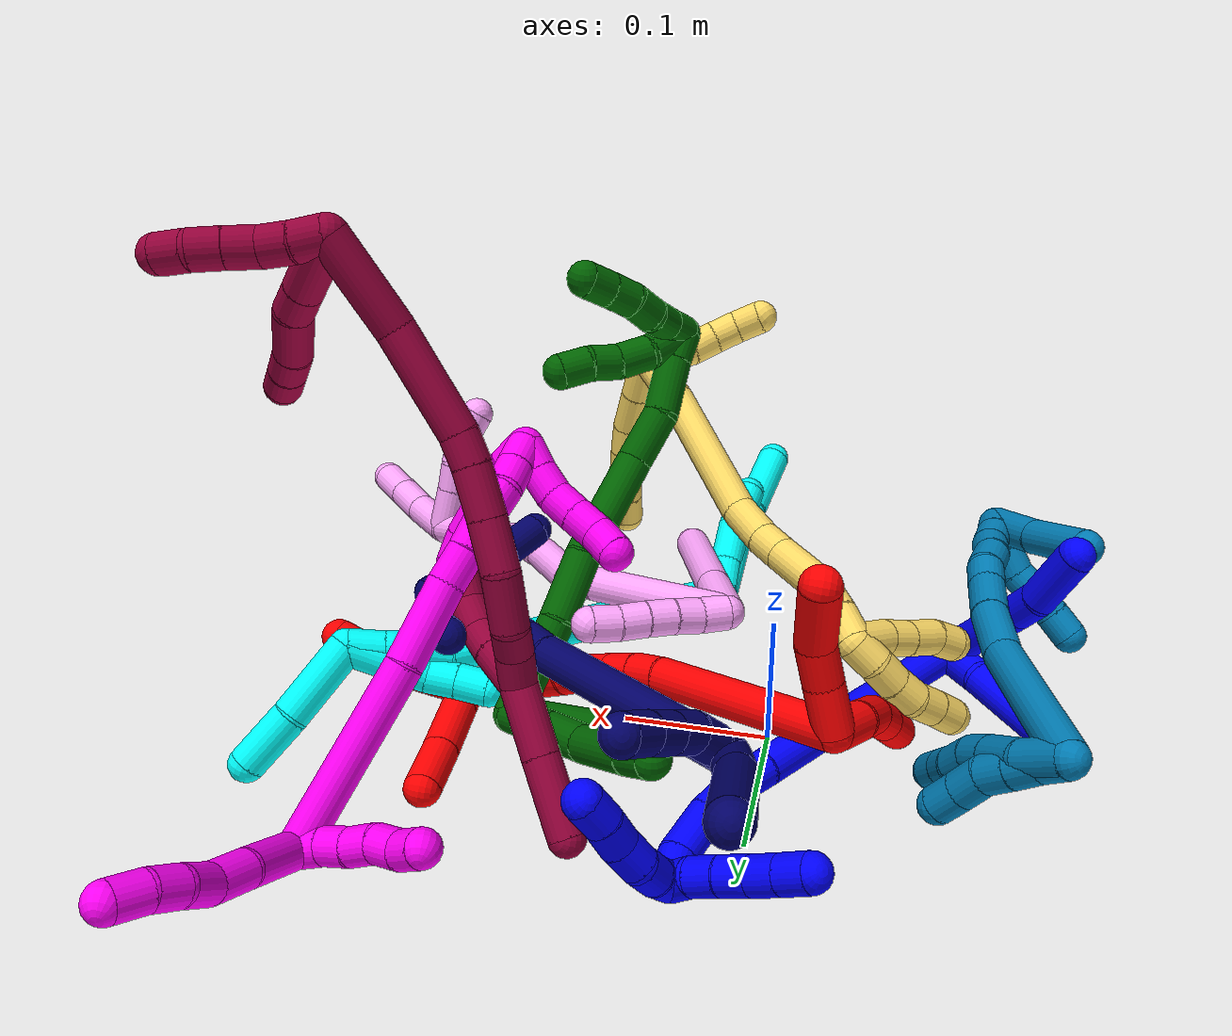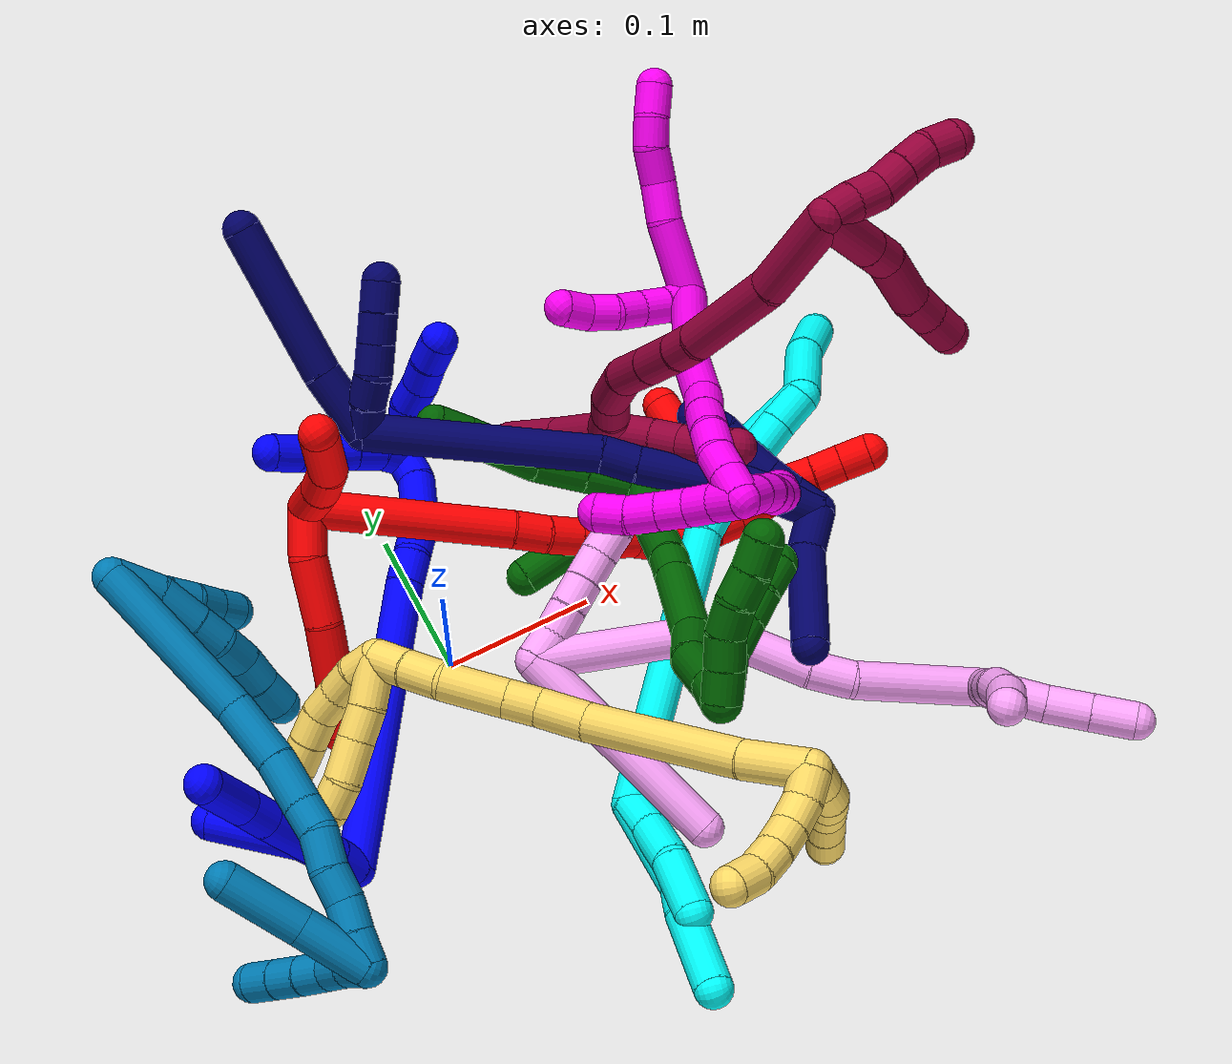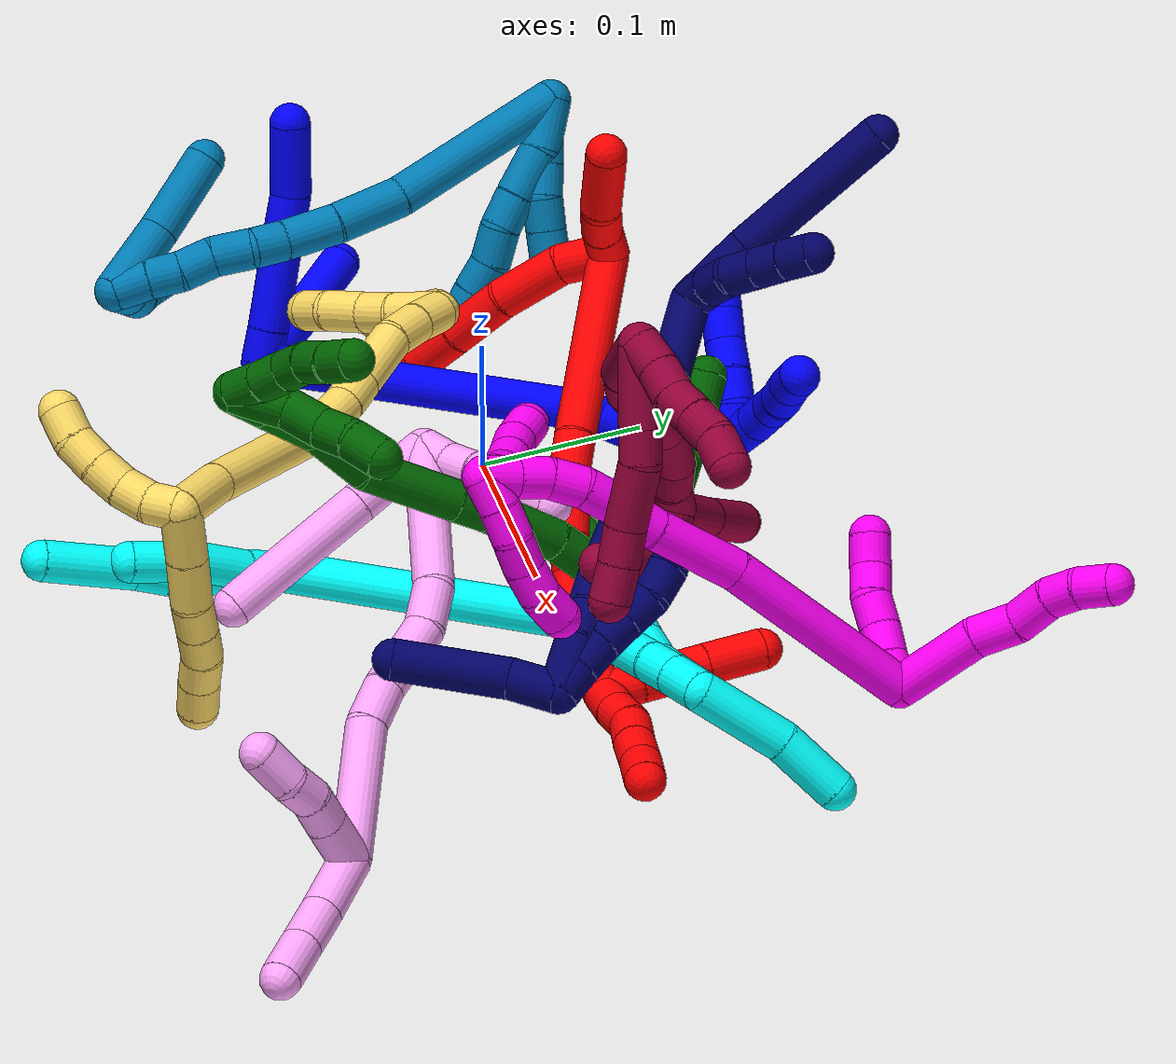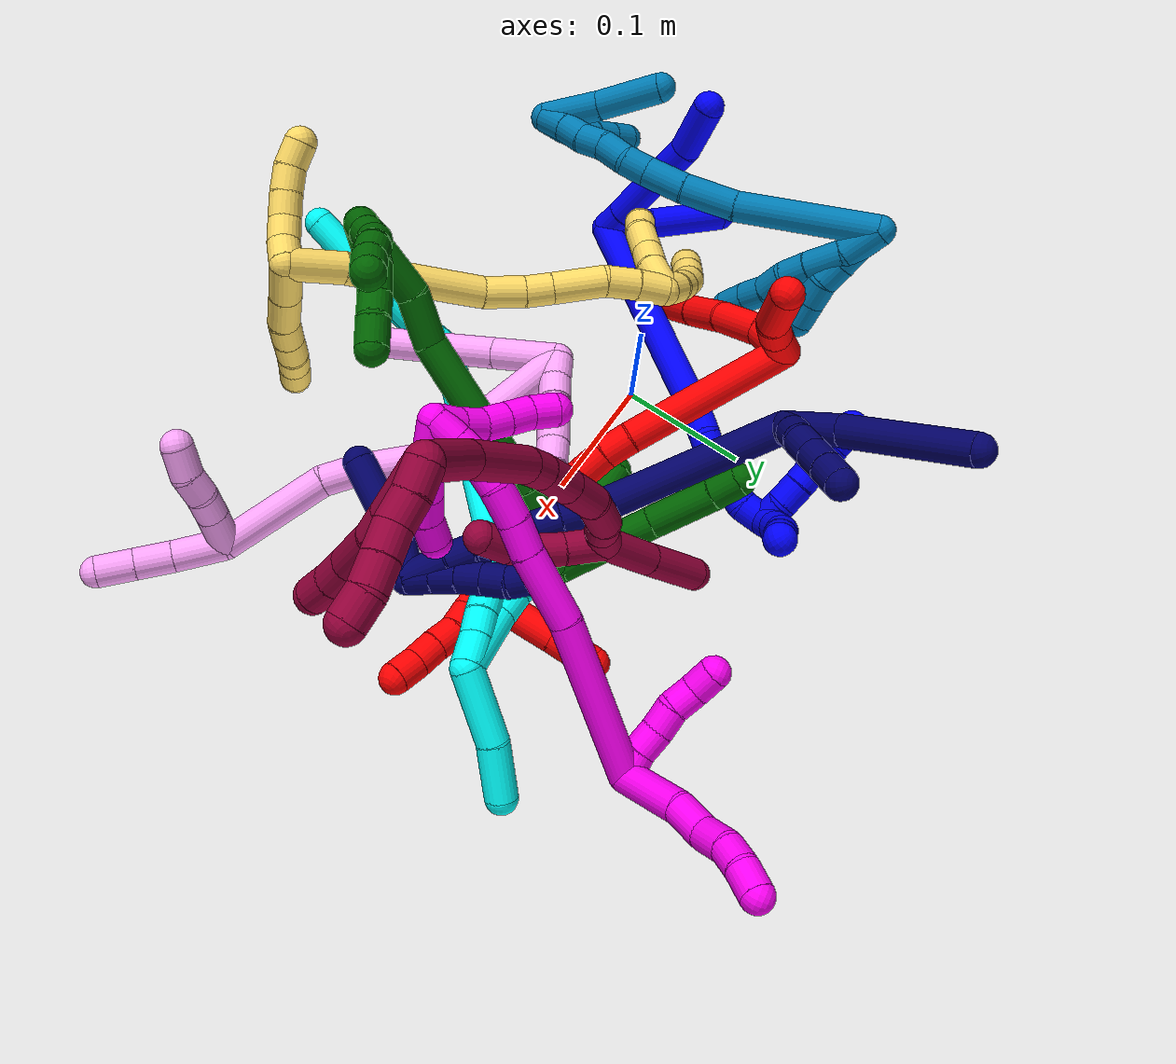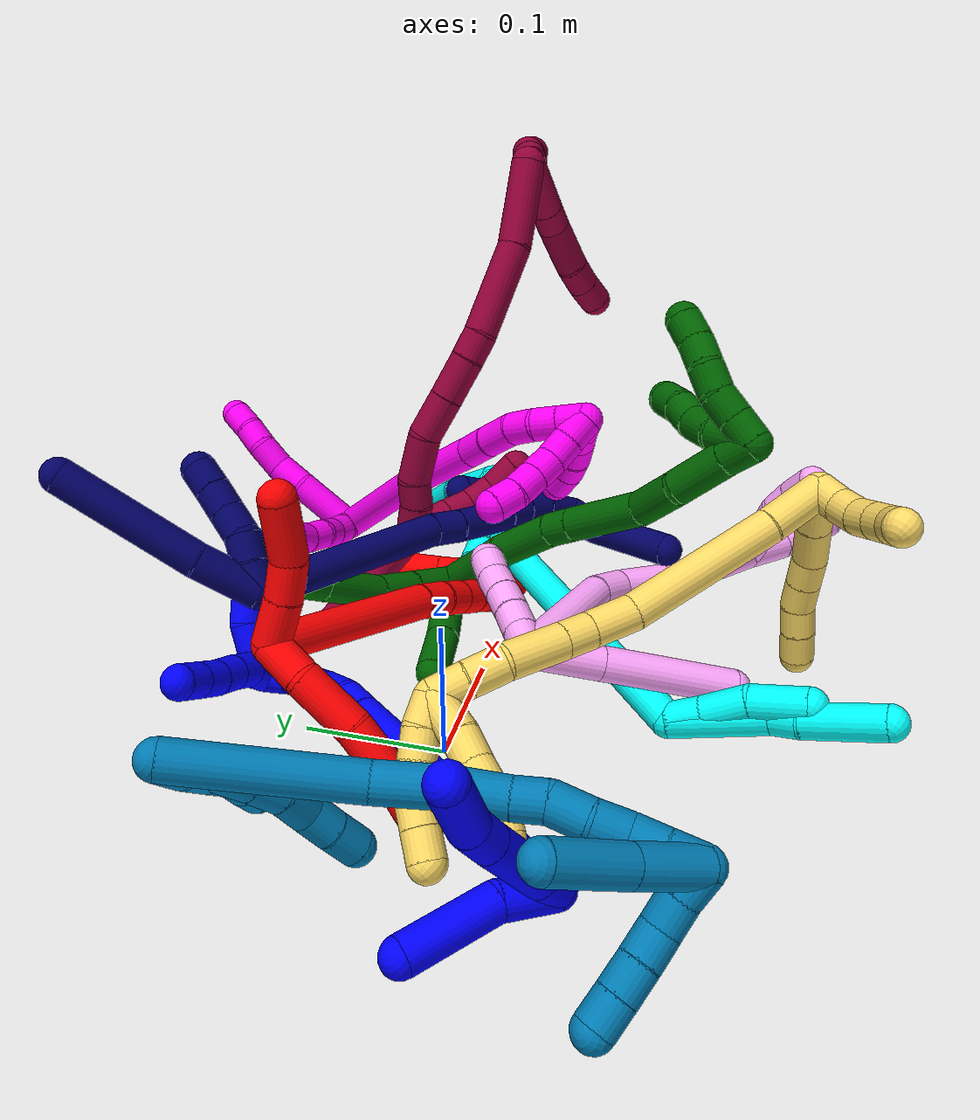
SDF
<sdf version="1.7">
 <world name="default">
  <plugin name="TubeGeneratorPlugin" filename="libtube_generator_plugin.so"/>
  <model name="photoneo_s_sensor">
   <static>1</static>
   <pose>0 0 2 1.57079 1.57079 3.14159</pose>
   <link name="link">
    <inertial><mass>0.1</mass></inertial>
    <sensor name="sensor" type="depth">
     <update_rate>30</update_rate>
     <camera>
      <horizontal_fov>1.22</horizontal_fov>
      <image><width>1920</width><height>1200</height><format>B8G8R8</format></image>
      <clip><near>0.1</near><far>4</far></clip>
      <depth_camera><output>points</output></depth_camera>
     </camera>
     <plugin name="camera_plugin" filename="libgazebo_ros_depth_camera.so">
      <baseline>0.2</baseline>
      <alwaysOn>1</alwaysOn>
      <updateRate>0.0</updateRate>
      <cameraName>camera_ir</cameraName>
      <imageTopicName>/camera/color/image_raw</imageTopicName>
      <cameraInfoTopicName>/camera/color/camera_info</cameraInfoTopicName>
      <depthImageTopicName>/camera/depth/image_raw</depthImageTopicName>
      <depthImageCameraInfoTopicName>/camera/depth/camera_info</depthImageCameraInfoTopicName>
      <pointCloudTopicName>/camera/depth/points</pointCloudTopicName>
      <frameName>fr_optical</frameName>
      <pointCloudCutoff>0.1</pointCloudCutoff>
      <pointCloudCutoffMax>2.0</pointCloudCutoffMax>
      <distortionK1>0</distortionK1>
      <distortionK2>0</distortionK2>
      <distortionK3>0</distortionK3>
      <distortionT1>0</distortionT1>
      <distortionT2>0</distortionT2>
      <CxPrime>0</CxPrime>
      <Cx>0</Cx>
      <Cy>0</Cy>
      <focalLength>0</focalLength>
      <hackBaseline>0</hackBaseline>
     </plugin>
    </sensor>
   </link>
  </model>
  <gravity>0 0 -9.8</gravity>
  <magnetic_field>6e-06 2.3e-05 -4.2e-05</magnetic_field>
  <atmosphere type="adiabatic"/>
  <physics name="default_physics" default="0" type="ode">
   <max_step_size>0.003</max_step_size>
   <real_time_factor>1</real_time_factor>
   <real_time_update_rate>1000</real_time_update_rate>
   <max_contacts>10000</max_contacts>
   <ode>
    <solver>
     <type>quick</type>
     <iters>100</iters>
     <sor>1.3</sor>
     <use_dynamic_moi_rescaling>0</use_dynamic_moi_rescaling>
    </solver>
    <constraints>
     <contact_max_correcting_vel>0</contact_max_correcting_vel>
     <contact_surface_layer>0.001</contact_surface_layer>
     <cfm>0</cfm>
     <erp>0.2</erp>
    </constraints>
   </ode>
  </physics>
  <scene><ambient>0.4 0.4 0.4 1</ambient><background>0.7 0.7 0.7 1</background><shadows>0</shadows></scene>
  <audio><device>default</device></audio>
  <spherical_coordinates>
   <surface_model>EARTH_WGS84</surface_model>
   <latitude_deg>0</latitude_deg>
   <longitude_deg>0</longitude_deg>
   <elevation>0</elevation>
   <heading_deg>0</heading_deg>
  </spherical_coordinates>
  <model name="bin">
   <static>1</static>
   <link name="bottom">
    <collision name="collision-bottom">
     <pose>0 0 -0.01 0 -0 0</pose>
     <geometry><box><size>0.8 0.6 0.02</size></box></geometry>
     <surface>
      <friction><ode><mu>100</mu><mu2>100</mu2></ode></friction>
      <contact><collide_bitmask>65535</collide_bitmask></contact>
     </surface>
    </collision>
   </link>
   <link name="west_wall">
    <collision name="collision-west_wall">
     <pose>-0.41 0 0.1 0 -0 0</pose>
     <geometry><box><size>0.02 0.6 0.2</size></box></geometry>
     <surface>
      <friction><ode><mu>100</mu><mu2>100</mu2></ode></friction>
      <contact><collide_bitmask>65535</collide_bitmask></contact>
     </surface>
    </collision>
   </link>
   <link name="east_wall">
    <collision name="collision-east_wall">
     <pose>0.41 0 0.1 0 -0 0</pose>
     <geometry><box><size>0.02 0.6 0.2</size></box></geometry>
     <surface>
      <friction><ode><mu>100</mu><mu2>100</mu2></ode></friction>
      <contact><collide_bitmask>65535</collide_bitmask></contact>
     </surface>
    </collision>
   </link>
   <link name="south_wall">
    <collision name="collision-south_wall">
     <pose>0 -0.31 0.1 0 -0 0</pose>
     <geometry><box><size>0.8 0.02 0.2</size></box></geometry>
     <surface>
      <friction><ode><mu>100</mu><mu2>100</mu2></ode></friction>
      <contact><collide_bitmask>65535</collide_bitmask></contact>
     </surface>
    </collision>
   </link>
   <link name="north_wall">
    <collision name="collision-north_wall">
     <pose>0 0.31 0.1 0 -0 0</pose>
     <geometry><box><size>0.8 0.02 0.2</size></box></geometry>
     <surface>
      <friction><ode><mu>100</mu><mu2>100</mu2></ode></friction>
      <contact><collide_bitmask>65535</collide_bitmask></contact>
     </surface>
    </collision>
   </link>
  </model>
  <model name="1">
   <static>0</static>
   <link name="1">
    <collision name="collision-cylinder-e_1_2_8">
     <pose>0.00047 -0.00067 0.010493 0.063764 0.044712 0.001426</pose>
     <geometry><cylinder><radius>0.0125</radius><length>0.021049</length></cylinder></geometry>
     <surface>
      <friction><ode><mu>1.16</mu><mu2>1.16</mu2><slip1>0</slip1><slip2>0</slip2></ode></friction>
      <contact><ode><kp>1e+06</kp><kd>1</kd><max_vel>0</max_vel><min_depth>0.001</min_depth></ode></contact>
     </surface>
    </collision>
    <visual name="visual-cylinder-e_1_2_8">
     <pose>0.00047 -0.00067 0.010493 0.063764 0.044712 0.001426</pose>
     <geometry><cylinder><radius>0.0125</radius><length>0.021049</length></cylinder></geometry>
     <material><ambient>0 0 1 1</ambient></material>
    </visual>
    <collision name="collision-cylinder-e_2_8_9">
     <pose>0.001425 -0.004283 0.051837 0.095112 0.015618 0.000743</pose>
     <geometry><cylinder><radius>0.0125</radius><length>0.061991</length></cylinder></geometry>
     <surface>
      <friction><ode><mu>1.16</mu><mu2>1.16</mu2><slip1>0</slip1><slip2>0</slip2></ode></friction>
      <contact><ode><kp>1e+06</kp><kd>1</kd><max_vel>0</max_vel><min_depth>0.001</min_depth></ode></contact>
     </surface>
    </collision>
    <visual name="visual-cylinder-e_2_8_9">
     <pose>0.001425 -0.004283 0.051837 0.095112 0.015618 0.000743</pose>
     <geometry><cylinder><radius>0.0125</radius><length>0.061991</length></cylinder></geometry>
     <material><ambient>0 0 1 1</ambient></material>
    </visual>
    <collision name="collision-cylinder-e_3_9_10">
     <pose>0.002473 -0.008212 0.093666 0.089525 0.051112 0.00229</pose>
     <geometry><cylinder><radius>0.0125</radius><length>0.022071</length></cylinder></geometry>
     <surface>
      <friction><ode><mu>1.16</mu><mu2>1.16</mu2><slip1>0</slip1><slip2>0</slip2></ode></friction>
      <contact><ode><kp>1e+06</kp><kd>1</kd><max_vel>0</max_vel><min_depth>0.001</min_depth></ode></contact>
     </surface>
    </collision>
    <visual name="visual-cylinder-e_3_9_10">
     <pose>0.002473 -0.008212 0.093666 0.089525 0.051112 0.00229</pose>
     <geometry><cylinder><radius>0.0125</radius><length>0.022071</length></cylinder></geometry>
     <material><ambient>0 0 1 1</ambient></material>
    </visual>
    <collision name="collision-cylinder-e_4_10_6">
     <pose>0.007057 -0.015916 0.125677 0.309169 0.180088 0.028137</pose>
     <geometry><cylinder><radius>0.0125</radius><length>0.044888</length></cylinder></geometry>
     <surface>
      <friction><ode><mu>1.16</mu><mu2>1.16</mu2><slip1>0</slip1><slip2>0</slip2></ode></friction>
      <contact><ode><kp>1e+06</kp><kd>1</kd><max_vel>0</max_vel><min_depth>0.001</min_depth></ode></contact>
     </surface>
    </collision>
    <visual name="visual-cylinder-e_4_10_6">
     <pose>0.007057 -0.015916 0.125677 0.309169 0.180088 0.028137</pose>
     <geometry><cylinder><radius>0.0125</radius><length>0.044888</length></cylinder></geometry>
     <material><ambient>0 0 1 1</ambient></material>
    </visual>
    <collision name="collision-cylinder-e_1_2_11">
     <pose>-0.008007 0.009609 0.014091 -0.598494 -0.438928 0.137414</pose>
     <geometry><cylinder><radius>0.0125</radius><length>0.037683</length></cylinder></geometry>
     <surface>
      <friction><ode><mu>1.16</mu><mu2>1.16</mu2><slip1>0</slip1><slip2>0</slip2></ode></friction>
      <contact><ode><kp>1e+06</kp><kd>1</kd><max_vel>0</max_vel><min_depth>0.001</min_depth></ode></contact>
     </surface>
    </collision>
    <visual name="visual-cylinder-e_1_2_11">
     <pose>-0.008007 0.009609 0.014091 -0.598494 -0.438928 0.137414</pose>
     <geometry><cylinder><radius>0.0125</radius><length>0.037683</length></cylinder></geometry>
     <material><ambient>0 0 1 1</ambient></material>
    </visual>
    <collision name="collision-cylinder-e_2_11_5">
     <pose>-0.037212 0.033475 0.046021 -0.674278 -0.748207 0.273505</pose>
     <geometry><cylinder><radius>0.0125</radius><length>0.062317</length></cylinder></geometry>
     <surface>
      <friction><ode><mu>1.16</mu><mu2>1.16</mu2><slip1>0</slip1><slip2>0</slip2></ode></friction>
      <contact><ode><kp>1e+06</kp><kd>1</kd><max_vel>0</max_vel><min_depth>0.001</min_depth></ode></contact>
     </surface>
    </collision>
    <visual name="visual-cylinder-e_2_11_5">
     <pose>-0.037212 0.033475 0.046021 -0.674278 -0.748207 0.273505</pose>
     <geometry><cylinder><radius>0.0125</radius><length>0.062317</length></cylinder></geometry>
     <material><ambient>0 0 1 1</ambient></material>
    </visual>
    <collision name="collision-cylinder-e_1_2_12">
     <pose>0.0486 0.082933 0.012314 -1.42339 0.525328 -0.455747</pose>
     <geometry><cylinder><radius>0.0125</radius><length>0.193818</length></cylinder></geometry>
     <surface>
      <friction><ode><mu>1.16</mu><mu2>1.16</mu2><slip1>0</slip1><slip2>0</slip2></ode></friction>
      <contact><ode><kp>1e+06</kp><kd>1</kd><max_vel>0</max_vel><min_depth>0.001</min_depth></ode></contact>
     </surface>
    </collision>
    <visual name="visual-cylinder-e_1_2_12">
     <pose>0.0486 0.082933 0.012314 -1.42339 0.525328 -0.455747</pose>
     <geometry><cylinder><radius>0.0125</radius><length>0.193818</length></cylinder></geometry>
     <material><ambient>0 0 1 1</ambient></material>
    </visual>
    <collision name="collision-cylinder-e_2_12_13">
     <pose>0.102754 0.175145 0.02505 -1.52529 0.538916 -0.516005</pose>
     <geometry><cylinder><radius>0.0125</radius><length>0.021647</length></cylinder></geometry>
     <surface>
      <friction><ode><mu>1.16</mu><mu2>1.16</mu2><slip1>0</slip1><slip2>0</slip2></ode></friction>
      <contact><ode><kp>1e+06</kp><kd>1</kd><max_vel>0</max_vel><min_depth>0.001</min_depth></ode></contact>
     </surface>
    </collision>
    <visual name="visual-cylinder-e_2_12_13">
     <pose>0.102754 0.175145 0.02505 -1.52529 0.538916 -0.516005</pose>
     <geometry><cylinder><radius>0.0125</radius><length>0.021647</length></cylinder></geometry>
     <material><ambient>0 0 1 1</ambient></material>
    </visual>
    <collision name="collision-cylinder-e_3_13_14">
     <pose>0.112834 0.198164 0.023356 -1.72365 0.314712 -0.365831</pose>
     <geometry><cylinder><radius>0.0125</radius><length>0.029239</length></cylinder></geometry>
     <surface>
      <friction><ode><mu>1.16</mu><mu2>1.16</mu2><slip1>0</slip1><slip2>0</slip2></ode></friction>
      <contact><ode><kp>1e+06</kp><kd>1</kd><max_vel>0</max_vel><min_depth>0.001</min_depth></ode></contact>
     </surface>
    </collision>
    <visual name="visual-cylinder-e_3_13_14">
     <pose>0.112834 0.198164 0.023356 -1.72365 0.314712 -0.365831</pose>
     <geometry><cylinder><radius>0.0125</radius><length>0.029239</length></cylinder></geometry>
     <material><ambient>0 0 1 1</ambient></material>
    </visual>
    <collision name="collision-cylinder-e_4_14_15">
     <pose>0.120871 0.228836 0.023358 -1.44631 0.202968 -0.179288</pose>
     <geometry><cylinder><radius>0.0125</radius><length>0.034844</length></cylinder></geometry>
     <surface>
      <friction><ode><mu>1.16</mu><mu2>1.16</mu2><slip1>0</slip1><slip2>0</slip2></ode></friction>
      <contact><ode><kp>1e+06</kp><kd>1</kd><max_vel>0</max_vel><min_depth>0.001</min_depth></ode></contact>
     </surface>
    </collision>
    <visual name="visual-cylinder-e_4_14_15">
     <pose>0.120871 0.228836 0.023358 -1.44631 0.202968 -0.179288</pose>
     <geometry><cylinder><radius>0.0125</radius><length>0.034844</length></cylinder></geometry>
     <material><ambient>0 0 1 1</ambient></material>
    </visual>
    <collision name="collision-cylinder-e_5_15_1">
     <pose>0.12392 0.255355 0.029006 -1.2181 -0.045261 0.031572</pose>
     <geometry><cylinder><radius>0.0125</radius><length>0.020452</length></cylinder></geometry>
     <surface>
      <friction><ode><mu>1.16</mu><mu2>1.16</mu2><slip1>0</slip1><slip2>0</slip2></ode></friction>
      <contact><ode><kp>1e+06</kp><kd>1</kd><max_vel>0</max_vel><min_depth>0.001</min_depth></ode></contact>
     </surface>
    </collision>
    <visual name="visual-cylinder-e_5_15_1">
     <pose>0.12392 0.255355 0.029006 -1.2181 -0.045261 0.031572</pose>
     <geometry><cylinder><radius>0.0125</radius><length>0.020452</length></cylinder></geometry>
     <material><ambient>0 0 1 1</ambient></material>
    </visual>
    <collision name="collision-cylinder-e_1_1_16">
     <pose>0.130369 0.267822 0.039163 -0.409924 0.763035 -0.166408</pose>
     <geometry><cylinder><radius>0.0125</radius><length>0.02</length></cylinder></geometry>
     <surface>
      <friction><ode><mu>1.16</mu><mu2>1.16</mu2><slip1>0</slip1><slip2>0</slip2></ode></friction>
      <contact><ode><kp>1e+06</kp><kd>1</kd><max_vel>0</max_vel><min_depth>0.001</min_depth></ode></contact>
     </surface>
    </collision>
    <visual name="visual-cylinder-e_1_1_16">
     <pose>0.130369 0.267822 0.039163 -0.409924 0.763035 -0.166408</pose>
     <geometry><cylinder><radius>0.0125</radius><length>0.02</length></cylinder></geometry>
     <material><ambient>0 0 1 1</ambient></material>
    </visual>
    <collision name="collision-cylinder-e_2_16_17">
     <pose>0.145018 0.272129 0.051964 -0.22718 0.884741 -0.107971</pose>
     <geometry><cylinder><radius>0.0125</radius><length>0.02</length></cylinder></geometry>
     <surface>
      <friction><ode><mu>1.16</mu><mu2>1.16</mu2><slip1>0</slip1><slip2>0</slip2></ode></friction>
      <contact><ode><kp>1e+06</kp><kd>1</kd><max_vel>0</max_vel><min_depth>0.001</min_depth></ode></contact>
     </surface>
    </collision>
    <visual name="visual-cylinder-e_2_16_17">
     <pose>0.145018 0.272129 0.051964 -0.22718 0.884741 -0.107971</pose>
     <geometry><cylinder><radius>0.0125</radius><length>0.02</length></cylinder></geometry>
     <material><ambient>0 0 1 1</ambient></material>
    </visual>
    <collision name="collision-cylinder-e_3_17_18">
     <pose>0.161866 0.272839 0.062195 0.17479 1.14596 0.112939</pose>
     <geometry><cylinder><radius>0.0125</radius><length>0.02</length></cylinder></geometry>
     <surface>
      <friction><ode><mu>1.16</mu><mu2>1.16</mu2><slip1>0</slip1><slip2>0</slip2></ode></friction>
      <contact><ode><kp>1e+06</kp><kd>1</kd><max_vel>0</max_vel><min_depth>0.001</min_depth></ode></contact>
     </surface>
    </collision>
    <visual name="visual-cylinder-e_3_17_18">
     <pose>0.161866 0.272839 0.062195 0.17479 1.14596 0.112939</pose>
     <geometry><cylinder><radius>0.0125</radius><length>0.02</length></cylinder></geometry>
     <material><ambient>0 0 1 1</ambient></material>
    </visual>
    <collision name="collision-cylinder-e_4_18_19">
     <pose>0.179333 0.270951 0.071621 0.21488 0.989242 0.11621</pose>
     <geometry><cylinder><radius>0.0125</radius><length>0.02</length></cylinder></geometry>
     <surface>
      <friction><ode><mu>1.16</mu><mu2>1.16</mu2><slip1>0</slip1><slip2>0</slip2></ode></friction>
      <contact><ode><kp>1e+06</kp><kd>1</kd><max_vel>0</max_vel><min_depth>0.001</min_depth></ode></contact>
     </surface>
    </collision>
    <visual name="visual-cylinder-e_4_18_19">
     <pose>0.179333 0.270951 0.071621 0.21488 0.989242 0.11621</pose>
     <geometry><cylinder><radius>0.0125</radius><length>0.02</length></cylinder></geometry>
     <material><ambient>0 0 1 1</ambient></material>
    </visual>
    <collision name="collision-cylinder-e_5_19_4">
     <pose>0.196591 0.269099 0.081493 0.150063 1.09771 0.091876</pose>
     <geometry><cylinder><radius>0.0125</radius><length>0.02</length></cylinder></geometry>
     <surface>
      <friction><ode><mu>1.16</mu><mu2>1.16</mu2><slip1>0</slip1><slip2>0</slip2></ode></friction>
      <contact><ode><kp>1e+06</kp><kd>1</kd><max_vel>0</max_vel><min_depth>0.001</min_depth></ode></contact>
     </surface>
    </collision>
    <visual name="visual-cylinder-e_5_19_4">
     <pose>0.196591 0.269099 0.081493 0.150063 1.09771 0.091876</pose>
     <geometry><cylinder><radius>0.0125</radius><length>0.02</length></cylinder></geometry>
     <material><ambient>0 0 1 1</ambient></material>
    </visual>
    <collision name="collision-cylinder-e_1_1_20">
     <pose>0.121237 0.263014 0.042092 0.199026 -0.223901 -0.022448</pose>
     <geometry><cylinder><radius>0.0125</radius><length>0.02</length></cylinder></geometry>
     <surface>
      <friction><ode><mu>1.16</mu><mu2>1.16</mu2><slip1>0</slip1><slip2>0</slip2></ode></friction>
      <contact><ode><kp>1e+06</kp><kd>1</kd><max_vel>0</max_vel><min_depth>0.001</min_depth></ode></contact>
     </surface>
    </collision>
    <visual name="visual-cylinder-e_1_1_20">
     <pose>0.121237 0.263014 0.042092 0.199026 -0.223901 -0.022448</pose>
     <geometry><cylinder><radius>0.0125</radius><length>0.02</length></cylinder></geometry>
     <material><ambient>0 0 1 1</ambient></material>
    </visual>
    <collision name="collision-cylinder-e_2_20_21">
     <pose>0.114082 0.258961 0.060084 0.246843 -0.516158 -0.065467</pose>
     <geometry><cylinder><radius>0.0125</radius><length>0.02</length></cylinder></geometry>
     <surface>
      <friction><ode><mu>1.16</mu><mu2>1.16</mu2><slip1>0</slip1><slip2>0</slip2></ode></friction>
      <contact><ode><kp>1e+06</kp><kd>1</kd><max_vel>0</max_vel><min_depth>0.001</min_depth></ode></contact>
     </surface>
    </collision>
    <visual name="visual-cylinder-e_2_20_21">
     <pose>0.114082 0.258961 0.060084 0.246843 -0.516158 -0.065467</pose>
     <geometry><cylinder><radius>0.0125</radius><length>0.02</length></cylinder></geometry>
     <material><ambient>0 0 1 1</ambient></material>
    </visual>
    <collision name="collision-cylinder-e_3_21_22">
     <pose>0.103555 0.25452 0.076478 0.283044 -0.59332 -0.087048</pose>
     <geometry><cylinder><radius>0.0125</radius><length>0.02</length></cylinder></geometry>
     <surface>
      <friction><ode><mu>1.16</mu><mu2>1.16</mu2><slip1>0</slip1><slip2>0</slip2></ode></friction>
      <contact><ode><kp>1e+06</kp><kd>1</kd><max_vel>0</max_vel><min_depth>0.001</min_depth></ode></contact>
     </surface>
    </collision>
    <visual name="visual-cylinder-e_3_21_22">
     <pose>0.103555 0.25452 0.076478 0.283044 -0.59332 -0.087048</pose>
     <geometry><cylinder><radius>0.0125</radius><length>0.02</length></cylinder></geometry>
     <material><ambient>0 0 1 1</ambient></material>
    </visual>
    <collision name="collision-cylinder-e_4_22_23">
     <pose>0.093307 0.250122 0.09304 0.237594 -0.484448 -0.058964</pose>
     <geometry><cylinder><radius>0.0125</radius><length>0.02</length></cylinder></geometry>
     <surface>
      <friction><ode><mu>1.16</mu><mu2>1.16</mu2><slip1>0</slip1><slip2>0</slip2></ode></friction>
      <contact><ode><kp>1e+06</kp><kd>1</kd><max_vel>0</max_vel><min_depth>0.001</min_depth></ode></contact>
     </surface>
    </collision>
    <visual name="visual-cylinder-e_4_22_23">
     <pose>0.093307 0.250122 0.09304 0.237594 -0.484448 -0.058964</pose>
     <geometry><cylinder><radius>0.0125</radius><length>0.02</length></cylinder></geometry>
     <material><ambient>0 0 1 1</ambient></material>
    </visual>
    <collision name="collision-cylinder-e_5_23_3">
     <pose>0.084121 0.245843 0.110282 0.248888 -0.469918 -0.05987</pose>
     <geometry><cylinder><radius>0.0125</radius><length>0.02</length></cylinder></geometry>
     <surface>
      <friction><ode><mu>1.16</mu><mu2>1.16</mu2><slip1>0</slip1><slip2>0</slip2></ode></friction>
      <contact><ode><kp>1e+06</kp><kd>1</kd><max_vel>0</max_vel><min_depth>0.001</min_depth></ode></contact>
     </surface>
    </collision>
    <visual name="visual-cylinder-e_5_23_3">
     <pose>0.084121 0.245843 0.110282 0.248888 -0.469918 -0.05987</pose>
     <geometry><cylinder><radius>0.0125</radius><length>0.02</length></cylinder></geometry>
     <material><ambient>0 0 1 1</ambient></material>
    </visual>
    <collision name="collision-sphere-3">
     <pose>0.079593 0.243647 0.118923 0 -0 0</pose>
     <geometry><sphere><radius>0.0125</radius></sphere></geometry>
     <surface>
      <friction><ode><mu>1.16</mu><mu2>1.16</mu2><slip1>0</slip1><slip2>0</slip2></ode></friction>
      <contact><ode><kp>1e+06</kp><kd>1</kd><max_vel>0</max_vel><min_depth>0.001</min_depth></ode></contact>
     </surface>
    </collision>
    <visual name="visual-sphere-3">
     <pose>0.079593 0.243647 0.118923 0 -0 0</pose>
     <geometry><sphere><radius>0.0125</radius></sphere></geometry>
     <material><ambient>0 0 1 1</ambient></material>
    </visual>
    <collision name="collision-sphere-23">
     <pose>0.088649 0.248039 0.101641 0 -0 0</pose>
     <geometry><sphere><radius>0.0125</radius></sphere></geometry>
     <surface>
      <friction><ode><mu>1.16</mu><mu2>1.16</mu2><slip1>0</slip1><slip2>0</slip2></ode></friction>
      <contact><ode><kp>1e+06</kp><kd>1</kd><max_vel>0</max_vel><min_depth>0.001</min_depth></ode></contact>
     </surface>
    </collision>
    <visual name="visual-sphere-23">
     <pose>0.088649 0.248039 0.101641 0 -0 0</pose>
     <geometry><sphere><radius>0.0125</radius></sphere></geometry>
     <material><ambient>0 0 1 1</ambient></material>
    </visual>
    <collision name="collision-sphere-22">
     <pose>0.097964 0.252205 0.084439 0 -0 0</pose>
     <geometry><sphere><radius>0.0125</radius></sphere></geometry>
     <surface>
      <friction><ode><mu>1.16</mu><mu2>1.16</mu2><slip1>0</slip1><slip2>0</slip2></ode></friction>
      <contact><ode><kp>1e+06</kp><kd>1</kd><max_vel>0</max_vel><min_depth>0.001</min_depth></ode></contact>
     </surface>
    </collision>
    <visual name="visual-sphere-22">
     <pose>0.097964 0.252205 0.084439 0 -0 0</pose>
     <geometry><sphere><radius>0.0125</radius></sphere></geometry>
     <material><ambient>0 0 1 1</ambient></material>
    </visual>
    <collision name="collision-sphere-21">
     <pose>0.109146 0.256836 0.068517 0 -0 0</pose>
     <geometry><sphere><radius>0.0125</radius></sphere></geometry>
     <surface>
      <friction><ode><mu>1.16</mu><mu2>1.16</mu2><slip1>0</slip1><slip2>0</slip2></ode></friction>
      <contact><ode><kp>1e+06</kp><kd>1</kd><max_vel>0</max_vel><min_depth>0.001</min_depth></ode></contact>
     </surface>
    </collision>
    <visual name="visual-sphere-21">
     <pose>0.109146 0.256836 0.068517 0 -0 0</pose>
     <geometry><sphere><radius>0.0125</radius></sphere></geometry>
     <material><ambient>0 0 1 1</ambient></material>
    </visual>
    <collision name="collision-sphere-20">
     <pose>0.119017 0.261086 0.05165 0 -0 0</pose>
     <geometry><sphere><radius>0.0125</radius></sphere></geometry>
     <surface>
      <friction><ode><mu>1.16</mu><mu2>1.16</mu2><slip1>0</slip1><slip2>0</slip2></ode></friction>
      <contact><ode><kp>1e+06</kp><kd>1</kd><max_vel>0</max_vel><min_depth>0.001</min_depth></ode></contact>
     </surface>
    </collision>
    <visual name="visual-sphere-20">
     <pose>0.119017 0.261086 0.05165 0 -0 0</pose>
     <geometry><sphere><radius>0.0125</radius></sphere></geometry>
     <material><ambient>0 0 1 1</ambient></material>
    </visual>
    <collision name="collision-sphere-4">
     <pose>0.205493 0.268417 0.085998 0 -0 0</pose>
     <geometry><sphere><radius>0.0125</radius></sphere></geometry>
     <surface>
      <friction><ode><mu>1.16</mu><mu2>1.16</mu2><slip1>0</slip1><slip2>0</slip2></ode></friction>
      <contact><ode><kp>1e+06</kp><kd>1</kd><max_vel>0</max_vel><min_depth>0.001</min_depth></ode></contact>
     </surface>
    </collision>
    <visual name="visual-sphere-4">
     <pose>0.205493 0.268417 0.085998 0 -0 0</pose>
     <geometry><sphere><radius>0.0125</radius></sphere></geometry>
     <material><ambient>0 0 1 1</ambient></material>
    </visual>
    <collision name="collision-sphere-11">
     <pose>-0.016014 0.019218 0.028182 0 -0 0</pose>
     <geometry><sphere><radius>0.0125</radius></sphere></geometry>
     <surface>
      <friction><ode><mu>1.16</mu><mu2>1.16</mu2><slip1>0</slip1><slip2>0</slip2></ode></friction>
      <contact><ode><kp>1e+06</kp><kd>1</kd><max_vel>0</max_vel><min_depth>0.001</min_depth></ode></contact>
     </surface>
    </collision>
    <visual name="visual-sphere-11">
     <pose>-0.016014 0.019218 0.028182 0 -0 0</pose>
     <geometry><sphere><radius>0.0125</radius></sphere></geometry>
     <material><ambient>0 0 1 1</ambient></material>
    </visual>
    <collision name="collision-sphere-6">
     <pose>0.011077 -0.022634 0.146712 0 -0 0</pose>
     <geometry><sphere><radius>0.0125</radius></sphere></geometry>
     <surface>
      <friction><ode><mu>1.16</mu><mu2>1.16</mu2><slip1>0</slip1><slip2>0</slip2></ode></friction>
      <contact><ode><kp>1e+06</kp><kd>1</kd><max_vel>0</max_vel><min_depth>0.001</min_depth></ode></contact>
     </surface>
    </collision>
    <visual name="visual-sphere-6">
     <pose>0.011077 -0.022634 0.146712 0 -0 0</pose>
     <geometry><sphere><radius>0.0125</radius></sphere></geometry>
     <material><ambient>0 0 1 1</ambient></material>
    </visual>
    <collision name="collision-sphere-10">
     <pose>0.003037 -0.009197 0.104643 0 -0 0</pose>
     <geometry><sphere><radius>0.0125</radius></sphere></geometry>
     <surface>
      <friction><ode><mu>1.16</mu><mu2>1.16</mu2><slip1>0</slip1><slip2>0</slip2></ode></friction>
      <contact><ode><kp>1e+06</kp><kd>1</kd><max_vel>0</max_vel><min_depth>0.001</min_depth></ode></contact>
     </surface>
    </collision>
    <visual name="visual-sphere-10">
     <pose>0.003037 -0.009197 0.104643 0 -0 0</pose>
     <geometry><sphere><radius>0.0125</radius></sphere></geometry>
     <material><ambient>0 0 1 1</ambient></material>
    </visual>
    <collision name="collision-sphere-9">
     <pose>0.001909 -0.007226 0.082689 0 -0 0</pose>
     <geometry><sphere><radius>0.0125</radius></sphere></geometry>
     <surface>
      <friction><ode><mu>1.16</mu><mu2>1.16</mu2><slip1>0</slip1><slip2>0</slip2></ode></friction>
      <contact><ode><kp>1e+06</kp><kd>1</kd><max_vel>0</max_vel><min_depth>0.001</min_depth></ode></contact>
     </surface>
    </collision>
    <visual name="visual-sphere-9">
     <pose>0.001909 -0.007226 0.082689 0 -0 0</pose>
     <geometry><sphere><radius>0.0125</radius></sphere></geometry>
     <material><ambient>0 0 1 1</ambient></material>
    </visual>
    <collision name="collision-sphere-2">
     <geometry><sphere><radius>0.0125</radius></sphere></geometry>
     <surface>
      <friction><ode><mu>1.16</mu><mu2>1.16</mu2><slip1>0</slip1><slip2>0</slip2></ode></friction>
      <contact><ode><kp>1e+06</kp><kd>1</kd><max_vel>0</max_vel><min_depth>0.001</min_depth></ode></contact>
     </surface>
    </collision>
    <visual name="visual-sphere-2">
     <geometry><sphere><radius>0.0125</radius></sphere></geometry>
     <material><ambient>0 0 1 1</ambient></material>
    </visual>
    <collision name="collision-sphere-19">
     <pose>0.187689 0.26978 0.076988 0 -0 0</pose>
     <geometry><sphere><radius>0.0125</radius></sphere></geometry>
     <surface>
      <friction><ode><mu>1.16</mu><mu2>1.16</mu2><slip1>0</slip1><slip2>0</slip2></ode></friction>
      <contact><ode><kp>1e+06</kp><kd>1</kd><max_vel>0</max_vel><min_depth>0.001</min_depth></ode></contact>
     </surface>
    </collision>
    <visual name="visual-sphere-19">
     <pose>0.187689 0.26978 0.076988 0 -0 0</pose>
     <geometry><sphere><radius>0.0125</radius></sphere></geometry>
     <material><ambient>0 0 1 1</ambient></material>
    </visual>
    <collision name="collision-sphere-8">
     <pose>0.000941 -0.00134 0.020986 0 -0 0</pose>
     <geometry><sphere><radius>0.0125</radius></sphere></geometry>
     <surface>
      <friction><ode><mu>1.16</mu><mu2>1.16</mu2><slip1>0</slip1><slip2>0</slip2></ode></friction>
      <contact><ode><kp>1e+06</kp><kd>1</kd><max_vel>0</max_vel><min_depth>0.001</min_depth></ode></contact>
     </surface>
    </collision>
    <visual name="visual-sphere-8">
     <pose>0.000941 -0.00134 0.020986 0 -0 0</pose>
     <geometry><sphere><radius>0.0125</radius></sphere></geometry>
     <material><ambient>0 0 1 1</ambient></material>
    </visual>
    <collision name="collision-sphere-5">
     <pose>-0.05841 0.047733 0.06386 0 -0 0</pose>
     <geometry><sphere><radius>0.0125</radius></sphere></geometry>
     <surface>
      <friction><ode><mu>1.16</mu><mu2>1.16</mu2><slip1>0</slip1><slip2>0</slip2></ode></friction>
      <contact><ode><kp>1e+06</kp><kd>1</kd><max_vel>0</max_vel><min_depth>0.001</min_depth></ode></contact>
     </surface>
    </collision>
    <visual name="visual-sphere-5">
     <pose>-0.05841 0.047733 0.06386 0 -0 0</pose>
     <geometry><sphere><radius>0.0125</radius></sphere></geometry>
     <material><ambient>0 0 1 1</ambient></material>
    </visual>
    <collision name="collision-sphere-12">
     <pose>0.097199 0.165865 0.024627 0 -0 0</pose>
     <geometry><sphere><radius>0.0125</radius></sphere></geometry>
     <surface>
      <friction><ode><mu>1.16</mu><mu2>1.16</mu2><slip1>0</slip1><slip2>0</slip2></ode></friction>
      <contact><ode><kp>1e+06</kp><kd>1</kd><max_vel>0</max_vel><min_depth>0.001</min_depth></ode></contact>
     </surface>
    </collision>
    <visual name="visual-sphere-12">
     <pose>0.097199 0.165865 0.024627 0 -0 0</pose>
     <geometry><sphere><radius>0.0125</radius></sphere></geometry>
     <material><ambient>0 0 1 1</ambient></material>
    </visual>
    <collision name="collision-sphere-13">
     <pose>0.108309 0.184425 0.025473 0 -0 0</pose>
     <geometry><sphere><radius>0.0125</radius></sphere></geometry>
     <surface>
      <friction><ode><mu>1.16</mu><mu2>1.16</mu2><slip1>0</slip1><slip2>0</slip2></ode></friction>
      <contact><ode><kp>1e+06</kp><kd>1</kd><max_vel>0</max_vel><min_depth>0.001</min_depth></ode></contact>
     </surface>
    </collision>
    <visual name="visual-sphere-13">
     <pose>0.108309 0.184425 0.025473 0 -0 0</pose>
     <geometry><sphere><radius>0.0125</radius></sphere></geometry>
     <material><ambient>0 0 1 1</ambient></material>
    </visual>
    <collision name="collision-sphere-14">
     <pose>0.117359 0.211904 0.021239 0 -0 0</pose>
     <geometry><sphere><radius>0.0125</radius></sphere></geometry>
     <surface>
      <friction><ode><mu>1.16</mu><mu2>1.16</mu2><slip1>0</slip1><slip2>0</slip2></ode></friction>
      <contact><ode><kp>1e+06</kp><kd>1</kd><max_vel>0</max_vel><min_depth>0.001</min_depth></ode></contact>
     </surface>
    </collision>
    <visual name="visual-sphere-14">
     <pose>0.117359 0.211904 0.021239 0 -0 0</pose>
     <geometry><sphere><radius>0.0125</radius></sphere></geometry>
     <material><ambient>0 0 1 1</ambient></material>
    </visual>
    <collision name="collision-sphere-15">
     <pose>0.124383 0.245768 0.025477 0 -0 0</pose>
     <geometry><sphere><radius>0.0125</radius></sphere></geometry>
     <surface>
      <friction><ode><mu>1.16</mu><mu2>1.16</mu2><slip1>0</slip1><slip2>0</slip2></ode></friction>
      <contact><ode><kp>1e+06</kp><kd>1</kd><max_vel>0</max_vel><min_depth>0.001</min_depth></ode></contact>
     </surface>
    </collision>
    <visual name="visual-sphere-15">
     <pose>0.124383 0.245768 0.025477 0 -0 0</pose>
     <geometry><sphere><radius>0.0125</radius></sphere></geometry>
     <material><ambient>0 0 1 1</ambient></material>
    </visual>
    <collision name="collision-sphere-1">
     <pose>0.123458 0.264942 0.032534 0 -0 0</pose>
     <geometry><sphere><radius>0.0125</radius></sphere></geometry>
     <surface>
      <friction><ode><mu>1.16</mu><mu2>1.16</mu2><slip1>0</slip1><slip2>0</slip2></ode></friction>
      <contact><ode><kp>1e+06</kp><kd>1</kd><max_vel>0</max_vel><min_depth>0.001</min_depth></ode></contact>
     </surface>
    </collision>
    <visual name="visual-sphere-1">
     <pose>0.123458 0.264942 0.032534 0 -0 0</pose>
     <geometry><sphere><radius>0.0125</radius></sphere></geometry>
     <material><ambient>0 0 1 1</ambient></material>
    </visual>
    <collision name="collision-sphere-18">
     <pose>0.170977 0.272123 0.066254 0 -0 0</pose>
     <geometry><sphere><radius>0.0125</radius></sphere></geometry>
     <surface>
      <friction><ode><mu>1.16</mu><mu2>1.16</mu2><slip1>0</slip1><slip2>0</slip2></ode></friction>
      <contact><ode><kp>1e+06</kp><kd>1</kd><max_vel>0</max_vel><min_depth>0.001</min_depth></ode></contact>
     </surface>
    </collision>
    <visual name="visual-sphere-18">
     <pose>0.170977 0.272123 0.066254 0 -0 0</pose>
     <geometry><sphere><radius>0.0125</radius></sphere></geometry>
     <material><ambient>0 0 1 1</ambient></material>
    </visual>
    <collision name="collision-sphere-16">
     <pose>0.13728 0.270702 0.045792 0 -0 0</pose>
     <geometry><sphere><radius>0.0125</radius></sphere></geometry>
     <surface>
      <friction><ode><mu>1.16</mu><mu2>1.16</mu2><slip1>0</slip1><slip2>0</slip2></ode></friction>
      <contact><ode><kp>1e+06</kp><kd>1</kd><max_vel>0</max_vel><min_depth>0.001</min_depth></ode></contact>
     </surface>
    </collision>
    <visual name="visual-sphere-16">
     <pose>0.13728 0.270702 0.045792 0 -0 0</pose>
     <geometry><sphere><radius>0.0125</radius></sphere></geometry>
     <material><ambient>0 0 1 1</ambient></material>
    </visual>
    <collision name="collision-sphere-17">
     <pose>0.152755 0.273556 0.058136 0 -0 0</pose>
     <geometry><sphere><radius>0.0125</radius></sphere></geometry>
     <surface>
      <friction><ode><mu>1.16</mu><mu2>1.16</mu2><slip1>0</slip1><slip2>0</slip2></ode></friction>
      <contact><ode><kp>1e+06</kp><kd>1</kd><max_vel>0</max_vel><min_depth>0.001</min_depth></ode></contact>
     </surface>
    </collision>
    <visual name="visual-sphere-17">
     <pose>0.152755 0.273556 0.058136 0 -0 0</pose>
     <geometry><sphere><radius>0.0125</radius></sphere></geometry>
     <material><ambient>0 0 1 1</ambient></material>
    </visual>
    <inertial>
     <pose>0.061503 0.123512 0.044439 0 -0 0</pose>
     <mass>0.75</mass>
     <inertia><ixx>0.000331</ixx><ixy>0</ixy><ixz>0</ixz><iyy>8e-05</iyy><iyz>0</iyz><izz>-0.000811</izz></inertia>
    </inertial>
   </link>
   <pose>-0.116153 -0.103449 0.012116 -0.433654 -0.581291 -0.021367</pose>
  </model>
  <model name="2">
   <static>0</static>
   <link name="2">
    <collision name="collision-cylinder-e_1_2_8">
     <pose>-0.006629 -0.011511 -0.008158 2.18736 -0.439203 -0.815173</pose>
     <geometry><cylinder><radius>0.0125</radius><length>0.031178</length></cylinder></geometry>
     <surface>
      <friction><ode><mu>1.16</mu><mu2>1.16</mu2><slip1>0</slip1><slip2>0</slip2></ode></friction>
      <contact><ode><kp>1e+06</kp><kd>1</kd><max_vel>0</max_vel><min_depth>0.001</min_depth></ode></contact>
     </surface>
    </collision>
    <visual name="visual-cylinder-e_1_2_8">
     <pose>-0.006629 -0.011511 -0.008158 2.18736 -0.439203 -0.815173</pose>
     <geometry><cylinder><radius>0.0125</radius><length>0.031178</length></cylinder></geometry>
     <material><ambient>1 0 0 1</ambient></material>
    </visual>
    <collision name="collision-cylinder-e_2_8_9">
     <pose>-0.019675 -0.04269 -0.02341 1.91694 -0.297857 -0.420899</pose>
     <geometry><cylinder><radius>0.0125</radius><length>0.04374</length></cylinder></geometry>
     <surface>
      <friction><ode><mu>1.16</mu><mu2>1.16</mu2><slip1>0</slip1><slip2>0</slip2></ode></friction>
      <contact><ode><kp>1e+06</kp><kd>1</kd><max_vel>0</max_vel><min_depth>0.001</min_depth></ode></contact>
     </surface>
    </collision>
    <visual name="visual-cylinder-e_2_8_9">
     <pose>-0.019675 -0.04269 -0.02341 1.91694 -0.297857 -0.420899</pose>
     <geometry><cylinder><radius>0.0125</radius><length>0.04374</length></cylinder></geometry>
     <material><ambient>1 0 0 1</ambient></material>
    </visual>
    <collision name="collision-cylinder-e_3_9_10">
     <pose>-0.028308 -0.081037 -0.037653 1.93633 -0.110259 -0.160077</pose>
     <geometry><cylinder><radius>0.0125</radius><length>0.040248</length></cylinder></geometry>
     <surface>
      <friction><ode><mu>1.16</mu><mu2>1.16</mu2><slip1>0</slip1><slip2>0</slip2></ode></friction>
      <contact><ode><kp>1e+06</kp><kd>1</kd><max_vel>0</max_vel><min_depth>0.001</min_depth></ode></contact>
     </surface>
    </collision>
    <visual name="visual-cylinder-e_3_9_10">
     <pose>-0.028308 -0.081037 -0.037653 1.93633 -0.110259 -0.160077</pose>
     <geometry><cylinder><radius>0.0125</radius><length>0.040248</length></cylinder></geometry>
     <material><ambient>1 0 0 1</ambient></material>
    </visual>
    <collision name="collision-cylinder-e_4_10_6">
     <pose>-0.031259 -0.11541 -0.052322 2.01763 -0.042279 -0.067125</pose>
     <geometry><cylinder><radius>0.0125</radius><length>0.034835</length></cylinder></geometry>
     <surface>
      <friction><ode><mu>1.16</mu><mu2>1.16</mu2><slip1>0</slip1><slip2>0</slip2></ode></friction>
      <contact><ode><kp>1e+06</kp><kd>1</kd><max_vel>0</max_vel><min_depth>0.001</min_depth></ode></contact>
     </surface>
    </collision>
    <visual name="visual-cylinder-e_4_10_6">
     <pose>-0.031259 -0.11541 -0.052322 2.01763 -0.042279 -0.067125</pose>
     <geometry><cylinder><radius>0.0125</radius><length>0.034835</length></cylinder></geometry>
     <material><ambient>1 0 0 1</ambient></material>
    </visual>
    <collision name="collision-cylinder-e_1_2_11">
     <pose>-0.011896 0.008539 0.006291 -0.935846 -0.842645 0.445445</pose>
     <geometry><cylinder><radius>0.0125</radius><length>0.031875</length></cylinder></geometry>
     <surface>
      <friction><ode><mu>1.16</mu><mu2>1.16</mu2><slip1>0</slip1><slip2>0</slip2></ode></friction>
      <contact><ode><kp>1e+06</kp><kd>1</kd><max_vel>0</max_vel><min_depth>0.001</min_depth></ode></contact>
     </surface>
    </collision>
    <visual name="visual-cylinder-e_1_2_11">
     <pose>-0.011896 0.008539 0.006291 -0.935846 -0.842645 0.445445</pose>
     <geometry><cylinder><radius>0.0125</radius><length>0.031875</length></cylinder></geometry>
     <material><ambient>1 0 0 1</ambient></material>
    </visual>
    <collision name="collision-cylinder-e_2_11_12">
     <pose>-0.032539 0.025295 0.01749 -1.03234 -0.740426 0.433568</pose>
     <geometry><cylinder><radius>0.0125</radius><length>0.025932</length></cylinder></geometry>
     <surface>
      <friction><ode><mu>1.16</mu><mu2>1.16</mu2><slip1>0</slip1><slip2>0</slip2></ode></friction>
      <contact><ode><kp>1e+06</kp><kd>1</kd><max_vel>0</max_vel><min_depth>0.001</min_depth></ode></contact>
     </surface>
    </collision>
    <visual name="visual-cylinder-e_2_11_12">
     <pose>-0.032539 0.025295 0.01749 -1.03234 -0.740426 0.433568</pose>
     <geometry><cylinder><radius>0.0125</radius><length>0.025932</length></cylinder></geometry>
     <material><ambient>1 0 0 1</ambient></material>
    </visual>
    <collision name="collision-cylinder-e_3_12_5">
     <pose>-0.052636 0.051051 0.025333 -1.405 -0.568103 0.484596</pose>
     <geometry><cylinder><radius>0.0125</radius><length>0.042193</length></cylinder></geometry>
     <surface>
      <friction><ode><mu>1.16</mu><mu2>1.16</mu2><slip1>0</slip1><slip2>0</slip2></ode></friction>
      <contact><ode><kp>1e+06</kp><kd>1</kd><max_vel>0</max_vel><min_depth>0.001</min_depth></ode></contact>
     </surface>
    </collision>
    <visual name="visual-cylinder-e_3_12_5">
     <pose>-0.052636 0.051051 0.025333 -1.405 -0.568103 0.484596</pose>
     <geometry><cylinder><radius>0.0125</radius><length>0.042193</length></cylinder></geometry>
     <material><ambient>1 0 0 1</ambient></material>
    </visual>
    <collision name="collision-cylinder-e_1_2_13">
     <pose>-0.013952 -0.039127 0.051825 0.646689 -0.21164 -0.071158</pose>
     <geometry><cylinder><radius>0.0125</radius><length>0.132837</length></cylinder></geometry>
     <surface>
      <friction><ode><mu>1.16</mu><mu2>1.16</mu2><slip1>0</slip1><slip2>0</slip2></ode></friction>
      <contact><ode><kp>1e+06</kp><kd>1</kd><max_vel>0</max_vel><min_depth>0.001</min_depth></ode></contact>
     </surface>
    </collision>
    <visual name="visual-cylinder-e_1_2_13">
     <pose>-0.013952 -0.039127 0.051825 0.646689 -0.21164 -0.071158</pose>
     <geometry><cylinder><radius>0.0125</radius><length>0.132837</length></cylinder></geometry>
     <material><ambient>1 0 0 1</ambient></material>
    </visual>
    <collision name="collision-cylinder-e_2_13_14">
     <pose>-0.029266 -0.085751 0.112018 0.730452 -0.120583 -0.046156</pose>
     <geometry><cylinder><radius>0.0125</radius><length>0.022634</length></cylinder></geometry>
     <surface>
      <friction><ode><mu>1.16</mu><mu2>1.16</mu2><slip1>0</slip1><slip2>0</slip2></ode></friction>
      <contact><ode><kp>1e+06</kp><kd>1</kd><max_vel>0</max_vel><min_depth>0.001</min_depth></ode></contact>
     </surface>
    </collision>
    <visual name="visual-cylinder-e_2_13_14">
     <pose>-0.029266 -0.085751 0.112018 0.730452 -0.120583 -0.046156</pose>
     <geometry><cylinder><radius>0.0125</radius><length>0.022634</length></cylinder></geometry>
     <material><ambient>1 0 0 1</ambient></material>
    </visual>
    <collision name="collision-cylinder-e_3_14_15">
     <pose>-0.030269 -0.100291 0.128559 0.711367 0.033175 0.012325</pose>
     <geometry><cylinder><radius>0.0125</radius><length>0.02159</length></cylinder></geometry>
     <surface>
      <friction><ode><mu>1.16</mu><mu2>1.16</mu2><slip1>0</slip1><slip2>0</slip2></ode></friction>
      <contact><ode><kp>1e+06</kp><kd>1</kd><max_vel>0</max_vel><min_depth>0.001</min_depth></ode></contact>
     </surface>
    </collision>
    <visual name="visual-cylinder-e_3_14_15">
     <pose>-0.030269 -0.100291 0.128559 0.711367 0.033175 0.012325</pose>
     <geometry><cylinder><radius>0.0125</radius><length>0.02159</length></cylinder></geometry>
     <material><ambient>1 0 0 1</ambient></material>
    </visual>
    <collision name="collision-cylinder-e_4_15_16">
     <pose>-0.02957 -0.113997 0.144348 0.718693 0.033653 0.012643</pose>
     <geometry><cylinder><radius>0.0125</radius><length>0.020249</length></cylinder></geometry>
     <surface>
      <friction><ode><mu>1.16</mu><mu2>1.16</mu2><slip1>0</slip1><slip2>0</slip2></ode></friction>
      <contact><ode><kp>1e+06</kp><kd>1</kd><max_vel>0</max_vel><min_depth>0.001</min_depth></ode></contact>
     </surface>
    </collision>
    <visual name="visual-cylinder-e_4_15_16">
     <pose>-0.02957 -0.113997 0.144348 0.718693 0.033653 0.012643</pose>
     <geometry><cylinder><radius>0.0125</radius><length>0.020249</length></cylinder></geometry>
     <material><ambient>1 0 0 1</ambient></material>
    </visual>
    <collision name="collision-cylinder-e_5_16_17">
     <pose>-0.027378 -0.127263 0.160418 0.663132 0.170869 0.058952</pose>
     <geometry><cylinder><radius>0.0125</radius><length>0.021773</length></cylinder></geometry>
     <surface>
      <friction><ode><mu>1.16</mu><mu2>1.16</mu2><slip1>0</slip1><slip2>0</slip2></ode></friction>
      <contact><ode><kp>1e+06</kp><kd>1</kd><max_vel>0</max_vel><min_depth>0.001</min_depth></ode></contact>
     </surface>
    </collision>
    <visual name="visual-cylinder-e_5_16_17">
     <pose>-0.027378 -0.127263 0.160418 0.663132 0.170869 0.058952</pose>
     <geometry><cylinder><radius>0.0125</radius><length>0.021773</length></cylinder></geometry>
     <material><ambient>1 0 0 1</ambient></material>
    </visual>
    <collision name="collision-cylinder-e_6_17_18">
     <pose>-0.024593 -0.140973 0.176032 0.781665 0.092391 0.03809</pose>
     <geometry><cylinder><radius>0.0125</radius><length>0.020261</length></cylinder></geometry>
     <surface>
      <friction><ode><mu>1.16</mu><mu2>1.16</mu2><slip1>0</slip1><slip2>0</slip2></ode></friction>
      <contact><ode><kp>1e+06</kp><kd>1</kd><max_vel>0</max_vel><min_depth>0.001</min_depth></ode></contact>
     </surface>
    </collision>
    <visual name="visual-cylinder-e_6_17_18">
     <pose>-0.024593 -0.140973 0.176032 0.781665 0.092391 0.03809</pose>
     <geometry><cylinder><radius>0.0125</radius><length>0.020261</length></cylinder></geometry>
     <material><ambient>1 0 0 1</ambient></material>
    </visual>
    <collision name="collision-cylinder-e_7_18_19">
     <pose>-0.021832 -0.153759 0.191554 0.596607 0.178694 0.055077</pose>
     <geometry><cylinder><radius>0.0125</radius><length>0.020546</length></cylinder></geometry>
     <surface>
      <friction><ode><mu>1.16</mu><mu2>1.16</mu2><slip1>0</slip1><slip2>0</slip2></ode></friction>
      <contact><ode><kp>1e+06</kp><kd>1</kd><max_vel>0</max_vel><min_depth>0.001</min_depth></ode></contact>
     </surface>
    </collision>
    <visual name="visual-cylinder-e_7_18_19">
     <pose>-0.021832 -0.153759 0.191554 0.596607 0.178694 0.055077</pose>
     <geometry><cylinder><radius>0.0125</radius><length>0.020546</length></cylinder></geometry>
     <material><ambient>1 0 0 1</ambient></material>
    </visual>
    <collision name="collision-cylinder-e_8_19_20">
     <pose>-0.017996 -0.162691 0.209177 0.337777 0.202062 0.034568</pose>
     <geometry><cylinder><radius>0.0125</radius><length>0.020037</length></cylinder></geometry>
     <surface>
      <friction><ode><mu>1.16</mu><mu2>1.16</mu2><slip1>0</slip1><slip2>0</slip2></ode></friction>
      <contact><ode><kp>1e+06</kp><kd>1</kd><max_vel>0</max_vel><min_depth>0.001</min_depth></ode></contact>
     </surface>
    </collision>
    <visual name="visual-cylinder-e_8_19_20">
     <pose>-0.017996 -0.162691 0.209177 0.337777 0.202062 0.034568</pose>
     <geometry><cylinder><radius>0.0125</radius><length>0.020037</length></cylinder></geometry>
     <material><ambient>1 0 0 1</ambient></material>
    </visual>
    <collision name="collision-cylinder-e_9_20_1">
     <pose>-0.013773 -0.168973 0.227746 0.314665 0.222179 0.035389</pose>
     <geometry><cylinder><radius>0.0125</radius><length>0.020073</length></cylinder></geometry>
     <surface>
      <friction><ode><mu>1.16</mu><mu2>1.16</mu2><slip1>0</slip1><slip2>0</slip2></ode></friction>
      <contact><ode><kp>1e+06</kp><kd>1</kd><max_vel>0</max_vel><min_depth>0.001</min_depth></ode></contact>
     </surface>
    </collision>
    <visual name="visual-cylinder-e_9_20_1">
     <pose>-0.013773 -0.168973 0.227746 0.314665 0.222179 0.035389</pose>
     <geometry><cylinder><radius>0.0125</radius><length>0.020073</length></cylinder></geometry>
     <material><ambient>1 0 0 1</ambient></material>
    </visual>
    <collision name="collision-cylinder-e_1_1_21">
     <pose>-0.012323 -0.171758 0.247023 -0.024581 -0.076147 0.000936</pose>
     <geometry><cylinder><radius>0.0125</radius><length>0.02</length></cylinder></geometry>
     <surface>
      <friction><ode><mu>1.16</mu><mu2>1.16</mu2><slip1>0</slip1><slip2>0</slip2></ode></friction>
      <contact><ode><kp>1e+06</kp><kd>1</kd><max_vel>0</max_vel><min_depth>0.001</min_depth></ode></contact>
     </surface>
    </collision>
    <visual name="visual-cylinder-e_1_1_21">
     <pose>-0.012323 -0.171758 0.247023 -0.024581 -0.076147 0.000936</pose>
     <geometry><cylinder><radius>0.0125</radius><length>0.02</length></cylinder></geometry>
     <material><ambient>1 0 0 1</ambient></material>
    </visual>
    <collision name="collision-cylinder-e_2_21_22">
     <pose>-0.013889 -0.169868 0.266822 -0.165794 -0.080679 0.006707</pose>
     <geometry><cylinder><radius>0.0125</radius><length>0.02</length></cylinder></geometry>
     <surface>
      <friction><ode><mu>1.16</mu><mu2>1.16</mu2><slip1>0</slip1><slip2>0</slip2></ode></friction>
      <contact><ode><kp>1e+06</kp><kd>1</kd><max_vel>0</max_vel><min_depth>0.001</min_depth></ode></contact>
     </surface>
    </collision>
    <visual name="visual-cylinder-e_2_21_22">
     <pose>-0.013889 -0.169868 0.266822 -0.165794 -0.080679 0.006707</pose>
     <geometry><cylinder><radius>0.0125</radius><length>0.02</length></cylinder></geometry>
     <material><ambient>1 0 0 1</ambient></material>
    </visual>
    <collision name="collision-cylinder-e_3_22_23">
     <pose>-0.017457 -0.169362 0.286196 0.118805 -0.279809 -0.01675</pose>
     <geometry><cylinder><radius>0.0125</radius><length>0.02</length></cylinder></geometry>
     <surface>
      <friction><ode><mu>1.16</mu><mu2>1.16</mu2><slip1>0</slip1><slip2>0</slip2></ode></friction>
      <contact><ode><kp>1e+06</kp><kd>1</kd><max_vel>0</max_vel><min_depth>0.001</min_depth></ode></contact>
     </surface>
    </collision>
    <visual name="visual-cylinder-e_3_22_23">
     <pose>-0.017457 -0.169362 0.286196 0.118805 -0.279809 -0.01675</pose>
     <geometry><cylinder><radius>0.0125</radius><length>0.02</length></cylinder></geometry>
     <material><ambient>1 0 0 1</ambient></material>
    </visual>
    <collision name="collision-cylinder-e_4_23_24">
     <pose>-0.022275 -0.171446 0.30548 0.096628 -0.207142 -0.010051</pose>
     <geometry><cylinder><radius>0.0125</radius><length>0.02</length></cylinder></geometry>
     <surface>
      <friction><ode><mu>1.16</mu><mu2>1.16</mu2><slip1>0</slip1><slip2>0</slip2></ode></friction>
      <contact><ode><kp>1e+06</kp><kd>1</kd><max_vel>0</max_vel><min_depth>0.001</min_depth></ode></contact>
     </surface>
    </collision>
    <visual name="visual-cylinder-e_4_23_24">
     <pose>-0.022275 -0.171446 0.30548 0.096628 -0.207142 -0.010051</pose>
     <geometry><cylinder><radius>0.0125</radius><length>0.02</length></cylinder></geometry>
     <material><ambient>1 0 0 1</ambient></material>
    </visual>
    <collision name="collision-cylinder-e_5_24_4">
     <pose>-0.027314 -0.17301 0.324746 0.064975 -0.30284 -0.009918</pose>
     <geometry><cylinder><radius>0.0125</radius><length>0.02</length></cylinder></geometry>
     <surface>
      <friction><ode><mu>1.16</mu><mu2>1.16</mu2><slip1>0</slip1><slip2>0</slip2></ode></friction>
      <contact><ode><kp>1e+06</kp><kd>1</kd><max_vel>0</max_vel><min_depth>0.001</min_depth></ode></contact>
     </surface>
    </collision>
    <visual name="visual-cylinder-e_5_24_4">
     <pose>-0.027314 -0.17301 0.324746 0.064975 -0.30284 -0.009918</pose>
     <geometry><cylinder><radius>0.0125</radius><length>0.02</length></cylinder></geometry>
     <material><ambient>1 0 0 1</ambient></material>
    </visual>
    <collision name="collision-cylinder-e_1_1_25">
     <pose>-0.002937 -0.16509 0.237437 -1.51572 0.894368 -0.852139</pose>
     <geometry><cylinder><radius>0.0125</radius><length>0.022121</length></cylinder></geometry>
     <surface>
      <friction><ode><mu>1.16</mu><mu2>1.16</mu2><slip1>0</slip1><slip2>0</slip2></ode></friction>
      <contact><ode><kp>1e+06</kp><kd>1</kd><max_vel>0</max_vel><min_depth>0.001</min_depth></ode></contact>
     </surface>
    </collision>
    <visual name="visual-cylinder-e_1_1_25">
     <pose>-0.002937 -0.16509 0.237437 -1.51572 0.894368 -0.852139</pose>
     <geometry><cylinder><radius>0.0125</radius><length>0.022121</length></cylinder></geometry>
     <material><ambient>1 0 0 1</ambient></material>
    </visual>
    <collision name="collision-cylinder-e_2_25_26">
     <pose>0.022467 -0.145419 0.238565 -1.51229 0.919893 -0.874158</pose>
     <geometry><cylinder><radius>0.0125</radius><length>0.042181</length></cylinder></geometry>
     <surface>
      <friction><ode><mu>1.16</mu><mu2>1.16</mu2><slip1>0</slip1><slip2>0</slip2></ode></friction>
      <contact><ode><kp>1e+06</kp><kd>1</kd><max_vel>0</max_vel><min_depth>0.001</min_depth></ode></contact>
     </surface>
    </collision>
    <visual name="visual-cylinder-e_2_25_26">
     <pose>0.022467 -0.145419 0.238565 -1.51229 0.919893 -0.874158</pose>
     <geometry><cylinder><radius>0.0125</radius><length>0.042181</length></cylinder></geometry>
     <material><ambient>1 0 0 1</ambient></material>
    </visual>
    <collision name="collision-cylinder-e_3_26_3">
     <pose>0.053381 -0.121821 0.240418 -1.46911 0.914017 -0.835888</pose>
     <geometry><cylinder><radius>0.0125</radius><length>0.035698</length></cylinder></geometry>
     <surface>
      <friction><ode><mu>1.16</mu><mu2>1.16</mu2><slip1>0</slip1><slip2>0</slip2></ode></friction>
      <contact><ode><kp>1e+06</kp><kd>1</kd><max_vel>0</max_vel><min_depth>0.001</min_depth></ode></contact>
     </surface>
    </collision>
    <visual name="visual-cylinder-e_3_26_3">
     <pose>0.053381 -0.121821 0.240418 -1.46911 0.914017 -0.835888</pose>
     <geometry><cylinder><radius>0.0125</radius><length>0.035698</length></cylinder></geometry>
     <material><ambient>1 0 0 1</ambient></material>
    </visual>
    <collision name="collision-sphere-3">
     <pose>0.067517 -0.110979 0.241525 0 -0 0</pose>
     <geometry><sphere><radius>0.0125</radius></sphere></geometry>
     <surface>
      <friction><ode><mu>1.16</mu><mu2>1.16</mu2><slip1>0</slip1><slip2>0</slip2></ode></friction>
      <contact><ode><kp>1e+06</kp><kd>1</kd><max_vel>0</max_vel><min_depth>0.001</min_depth></ode></contact>
     </surface>
    </collision>
    <visual name="visual-sphere-3">
     <pose>0.067517 -0.110979 0.241525 0 -0 0</pose>
     <geometry><sphere><radius>0.0125</radius></sphere></geometry>
     <material><ambient>1 0 0 1</ambient></material>
    </visual>
    <collision name="collision-sphere-26">
     <pose>0.039245 -0.132662 0.239312 0 -0 0</pose>
     <geometry><sphere><radius>0.0125</radius></sphere></geometry>
     <surface>
      <friction><ode><mu>1.16</mu><mu2>1.16</mu2><slip1>0</slip1><slip2>0</slip2></ode></friction>
      <contact><ode><kp>1e+06</kp><kd>1</kd><max_vel>0</max_vel><min_depth>0.001</min_depth></ode></contact>
     </surface>
    </collision>
    <visual name="visual-sphere-26">
     <pose>0.039245 -0.132662 0.239312 0 -0 0</pose>
     <geometry><sphere><radius>0.0125</radius></sphere></geometry>
     <material><ambient>1 0 0 1</ambient></material>
    </visual>
    <collision name="collision-sphere-25">
     <pose>0.005688 -0.158176 0.237818 0 -0 0</pose>
     <geometry><sphere><radius>0.0125</radius></sphere></geometry>
     <surface>
      <friction><ode><mu>1.16</mu><mu2>1.16</mu2><slip1>0</slip1><slip2>0</slip2></ode></friction>
      <contact><ode><kp>1e+06</kp><kd>1</kd><max_vel>0</max_vel><min_depth>0.001</min_depth></ode></contact>
     </surface>
    </collision>
    <visual name="visual-sphere-25">
     <pose>0.005688 -0.158176 0.237818 0 -0 0</pose>
     <geometry><sphere><radius>0.0125</radius></sphere></geometry>
     <material><ambient>1 0 0 1</ambient></material>
    </visual>
    <collision name="collision-sphere-4">
     <pose>-0.030296 -0.173629 0.33427 0 -0 0</pose>
     <geometry><sphere><radius>0.0125</radius></sphere></geometry>
     <surface>
      <friction><ode><mu>1.16</mu><mu2>1.16</mu2><slip1>0</slip1><slip2>0</slip2></ode></friction>
      <contact><ode><kp>1e+06</kp><kd>1</kd><max_vel>0</max_vel><min_depth>0.001</min_depth></ode></contact>
     </surface>
    </collision>
    <visual name="visual-sphere-4">
     <pose>-0.030296 -0.173629 0.33427 0 -0 0</pose>
     <geometry><sphere><radius>0.0125</radius></sphere></geometry>
     <material><ambient>1 0 0 1</ambient></material>
    </visual>
    <collision name="collision-sphere-24">
     <pose>-0.024332 -0.17239 0.315221 0 -0 0</pose>
     <geometry><sphere><radius>0.0125</radius></sphere></geometry>
     <surface>
      <friction><ode><mu>1.16</mu><mu2>1.16</mu2><slip1>0</slip1><slip2>0</slip2></ode></friction>
      <contact><ode><kp>1e+06</kp><kd>1</kd><max_vel>0</max_vel><min_depth>0.001</min_depth></ode></contact>
     </surface>
    </collision>
    <visual name="visual-sphere-24">
     <pose>-0.024332 -0.17239 0.315221 0 -0 0</pose>
     <geometry><sphere><radius>0.0125</radius></sphere></geometry>
     <material><ambient>1 0 0 1</ambient></material>
    </visual>
    <collision name="collision-sphere-23">
     <pose>-0.020219 -0.170502 0.29574 0 -0 0</pose>
     <geometry><sphere><radius>0.0125</radius></sphere></geometry>
     <surface>
      <friction><ode><mu>1.16</mu><mu2>1.16</mu2><slip1>0</slip1><slip2>0</slip2></ode></friction>
      <contact><ode><kp>1e+06</kp><kd>1</kd><max_vel>0</max_vel><min_depth>0.001</min_depth></ode></contact>
     </surface>
    </collision>
    <visual name="visual-sphere-23">
     <pose>-0.020219 -0.170502 0.29574 0 -0 0</pose>
     <geometry><sphere><radius>0.0125</radius></sphere></geometry>
     <material><ambient>1 0 0 1</ambient></material>
    </visual>
    <collision name="collision-sphere-22">
     <pose>-0.014695 -0.168223 0.276653 0 -0 0</pose>
     <geometry><sphere><radius>0.0125</radius></sphere></geometry>
     <surface>
      <friction><ode><mu>1.16</mu><mu2>1.16</mu2><slip1>0</slip1><slip2>0</slip2></ode></friction>
      <contact><ode><kp>1e+06</kp><kd>1</kd><max_vel>0</max_vel><min_depth>0.001</min_depth></ode></contact>
     </surface>
    </collision>
    <visual name="visual-sphere-22">
     <pose>-0.014695 -0.168223 0.276653 0 -0 0</pose>
     <geometry><sphere><radius>0.0125</radius></sphere></geometry>
     <material><ambient>1 0 0 1</ambient></material>
    </visual>
    <collision name="collision-sphere-21">
     <pose>-0.013083 -0.171513 0.256991 0 -0 0</pose>
     <geometry><sphere><radius>0.0125</radius></sphere></geometry>
     <surface>
      <friction><ode><mu>1.16</mu><mu2>1.16</mu2><slip1>0</slip1><slip2>0</slip2></ode></friction>
      <contact><ode><kp>1e+06</kp><kd>1</kd><max_vel>0</max_vel><min_depth>0.001</min_depth></ode></contact>
     </surface>
    </collision>
    <visual name="visual-sphere-21">
     <pose>-0.013083 -0.171513 0.256991 0 -0 0</pose>
     <geometry><sphere><radius>0.0125</radius></sphere></geometry>
     <material><ambient>1 0 0 1</ambient></material>
    </visual>
    <collision name="collision-sphere-1">
     <pose>-0.011562 -0.172003 0.237055 0 -0 0</pose>
     <geometry><sphere><radius>0.0125</radius></sphere></geometry>
     <surface>
      <friction><ode><mu>1.16</mu><mu2>1.16</mu2><slip1>0</slip1><slip2>0</slip2></ode></friction>
      <contact><ode><kp>1e+06</kp><kd>1</kd><max_vel>0</max_vel><min_depth>0.001</min_depth></ode></contact>
     </surface>
    </collision>
    <visual name="visual-sphere-1">
     <pose>-0.011562 -0.172003 0.237055 0 -0 0</pose>
     <geometry><sphere><radius>0.0125</radius></sphere></geometry>
     <material><ambient>1 0 0 1</ambient></material>
    </visual>
    <collision name="collision-sphere-11">
     <pose>-0.023792 0.017078 0.012582 0 -0 0</pose>
     <geometry><sphere><radius>0.0125</radius></sphere></geometry>
     <surface>
      <friction><ode><mu>1.16</mu><mu2>1.16</mu2><slip1>0</slip1><slip2>0</slip2></ode></friction>
      <contact><ode><kp>1e+06</kp><kd>1</kd><max_vel>0</max_vel><min_depth>0.001</min_depth></ode></contact>
     </surface>
    </collision>
    <visual name="visual-sphere-11">
     <pose>-0.023792 0.017078 0.012582 0 -0 0</pose>
     <geometry><sphere><radius>0.0125</radius></sphere></geometry>
     <material><ambient>1 0 0 1</ambient></material>
    </visual>
    <collision name="collision-sphere-6">
     <pose>-0.031995 -0.131104 -0.059841 0 -0 0</pose>
     <geometry><sphere><radius>0.0125</radius></sphere></geometry>
     <surface>
      <friction><ode><mu>1.16</mu><mu2>1.16</mu2><slip1>0</slip1><slip2>0</slip2></ode></friction>
      <contact><ode><kp>1e+06</kp><kd>1</kd><max_vel>0</max_vel><min_depth>0.001</min_depth></ode></contact>
     </surface>
    </collision>
    <visual name="visual-sphere-6">
     <pose>-0.031995 -0.131104 -0.059841 0 -0 0</pose>
     <geometry><sphere><radius>0.0125</radius></sphere></geometry>
     <material><ambient>1 0 0 1</ambient></material>
    </visual>
    <collision name="collision-sphere-10">
     <pose>-0.030522 -0.099717 -0.044802 0 -0 0</pose>
     <geometry><sphere><radius>0.0125</radius></sphere></geometry>
     <surface>
      <friction><ode><mu>1.16</mu><mu2>1.16</mu2><slip1>0</slip1><slip2>0</slip2></ode></friction>
      <contact><ode><kp>1e+06</kp><kd>1</kd><max_vel>0</max_vel><min_depth>0.001</min_depth></ode></contact>
     </surface>
    </collision>
    <visual name="visual-sphere-10">
     <pose>-0.030522 -0.099717 -0.044802 0 -0 0</pose>
     <geometry><sphere><radius>0.0125</radius></sphere></geometry>
     <material><ambient>1 0 0 1</ambient></material>
    </visual>
    <collision name="collision-sphere-9">
     <pose>-0.026094 -0.062356 -0.030503 0 -0 0</pose>
     <geometry><sphere><radius>0.0125</radius></sphere></geometry>
     <surface>
      <friction><ode><mu>1.16</mu><mu2>1.16</mu2><slip1>0</slip1><slip2>0</slip2></ode></friction>
      <contact><ode><kp>1e+06</kp><kd>1</kd><max_vel>0</max_vel><min_depth>0.001</min_depth></ode></contact>
     </surface>
    </collision>
    <visual name="visual-sphere-9">
     <pose>-0.026094 -0.062356 -0.030503 0 -0 0</pose>
     <geometry><sphere><radius>0.0125</radius></sphere></geometry>
     <material><ambient>1 0 0 1</ambient></material>
    </visual>
    <collision name="collision-sphere-2">
     <geometry><sphere><radius>0.0125</radius></sphere></geometry>
     <surface>
      <friction><ode><mu>1.16</mu><mu2>1.16</mu2><slip1>0</slip1><slip2>0</slip2></ode></friction>
      <contact><ode><kp>1e+06</kp><kd>1</kd><max_vel>0</max_vel><min_depth>0.001</min_depth></ode></contact>
     </surface>
    </collision>
    <visual name="visual-sphere-2">
     <geometry><sphere><radius>0.0125</radius></sphere></geometry>
     <material><ambient>1 0 0 1</ambient></material>
    </visual>
    <collision name="collision-sphere-19">
     <pose>-0.020006 -0.159439 0.199917 0 -0 0</pose>
     <geometry><sphere><radius>0.0125</radius></sphere></geometry>
     <surface>
      <friction><ode><mu>1.16</mu><mu2>1.16</mu2><slip1>0</slip1><slip2>0</slip2></ode></friction>
      <contact><ode><kp>1e+06</kp><kd>1</kd><max_vel>0</max_vel><min_depth>0.001</min_depth></ode></contact>
     </surface>
    </collision>
    <visual name="visual-sphere-19">
     <pose>-0.020006 -0.159439 0.199917 0 -0 0</pose>
     <geometry><sphere><radius>0.0125</radius></sphere></geometry>
     <material><ambient>1 0 0 1</ambient></material>
    </visual>
    <collision name="collision-sphere-8">
     <pose>-0.013257 -0.023023 -0.016317 0 -0 0</pose>
     <geometry><sphere><radius>0.0125</radius></sphere></geometry>
     <surface>
      <friction><ode><mu>1.16</mu><mu2>1.16</mu2><slip1>0</slip1><slip2>0</slip2></ode></friction>
      <contact><ode><kp>1e+06</kp><kd>1</kd><max_vel>0</max_vel><min_depth>0.001</min_depth></ode></contact>
     </surface>
    </collision>
    <visual name="visual-sphere-8">
     <pose>-0.013257 -0.023023 -0.016317 0 -0 0</pose>
     <geometry><sphere><radius>0.0125</radius></sphere></geometry>
     <material><ambient>1 0 0 1</ambient></material>
    </visual>
    <collision name="collision-sphere-12">
     <pose>-0.041286 0.033512 0.022399 0 -0 0</pose>
     <geometry><sphere><radius>0.0125</radius></sphere></geometry>
     <surface>
      <friction><ode><mu>1.16</mu><mu2>1.16</mu2><slip1>0</slip1><slip2>0</slip2></ode></friction>
      <contact><ode><kp>1e+06</kp><kd>1</kd><max_vel>0</max_vel><min_depth>0.001</min_depth></ode></contact>
     </surface>
    </collision>
    <visual name="visual-sphere-12">
     <pose>-0.041286 0.033512 0.022399 0 -0 0</pose>
     <geometry><sphere><radius>0.0125</radius></sphere></geometry>
     <material><ambient>1 0 0 1</ambient></material>
    </visual>
    <collision name="collision-sphere-5">
     <pose>-0.063987 0.06859 0.028268 0 -0 0</pose>
     <geometry><sphere><radius>0.0125</radius></sphere></geometry>
     <surface>
      <friction><ode><mu>1.16</mu><mu2>1.16</mu2><slip1>0</slip1><slip2>0</slip2></ode></friction>
      <contact><ode><kp>1e+06</kp><kd>1</kd><max_vel>0</max_vel><min_depth>0.001</min_depth></ode></contact>
     </surface>
    </collision>
    <visual name="visual-sphere-5">
     <pose>-0.063987 0.06859 0.028268 0 -0 0</pose>
     <geometry><sphere><radius>0.0125</radius></sphere></geometry>
     <material><ambient>1 0 0 1</ambient></material>
    </visual>
    <collision name="collision-sphere-13">
     <pose>-0.027904 -0.078255 0.10365 0 -0 0</pose>
     <geometry><sphere><radius>0.0125</radius></sphere></geometry>
     <surface>
      <friction><ode><mu>1.16</mu><mu2>1.16</mu2><slip1>0</slip1><slip2>0</slip2></ode></friction>
      <contact><ode><kp>1e+06</kp><kd>1</kd><max_vel>0</max_vel><min_depth>0.001</min_depth></ode></contact>
     </surface>
    </collision>
    <visual name="visual-sphere-13">
     <pose>-0.027904 -0.078255 0.10365 0 -0 0</pose>
     <geometry><sphere><radius>0.0125</radius></sphere></geometry>
     <material><ambient>1 0 0 1</ambient></material>
    </visual>
    <collision name="collision-sphere-14">
     <pose>-0.030627 -0.093247 0.120387 0 -0 0</pose>
     <geometry><sphere><radius>0.0125</radius></sphere></geometry>
     <surface>
      <friction><ode><mu>1.16</mu><mu2>1.16</mu2><slip1>0</slip1><slip2>0</slip2></ode></friction>
      <contact><ode><kp>1e+06</kp><kd>1</kd><max_vel>0</max_vel><min_depth>0.001</min_depth></ode></contact>
     </surface>
    </collision>
    <visual name="visual-sphere-14">
     <pose>-0.030627 -0.093247 0.120387 0 -0 0</pose>
     <geometry><sphere><radius>0.0125</radius></sphere></geometry>
     <material><ambient>1 0 0 1</ambient></material>
    </visual>
    <collision name="collision-sphere-15">
     <pose>-0.029911 -0.107334 0.136731 0 -0 0</pose>
     <geometry><sphere><radius>0.0125</radius></sphere></geometry>
     <surface>
      <friction><ode><mu>1.16</mu><mu2>1.16</mu2><slip1>0</slip1><slip2>0</slip2></ode></friction>
      <contact><ode><kp>1e+06</kp><kd>1</kd><max_vel>0</max_vel><min_depth>0.001</min_depth></ode></contact>
     </surface>
    </collision>
    <visual name="visual-sphere-15">
     <pose>-0.029911 -0.107334 0.136731 0 -0 0</pose>
     <geometry><sphere><radius>0.0125</radius></sphere></geometry>
     <material><ambient>1 0 0 1</ambient></material>
    </visual>
    <collision name="collision-sphere-16">
     <pose>-0.02923 -0.120659 0.151964 0 -0 0</pose>
     <geometry><sphere><radius>0.0125</radius></sphere></geometry>
     <surface>
      <friction><ode><mu>1.16</mu><mu2>1.16</mu2><slip1>0</slip1><slip2>0</slip2></ode></friction>
      <contact><ode><kp>1e+06</kp><kd>1</kd><max_vel>0</max_vel><min_depth>0.001</min_depth></ode></contact>
     </surface>
    </collision>
    <visual name="visual-sphere-16">
     <pose>-0.02923 -0.120659 0.151964 0 -0 0</pose>
     <geometry><sphere><radius>0.0125</radius></sphere></geometry>
     <material><ambient>1 0 0 1</ambient></material>
    </visual>
    <collision name="collision-sphere-17">
     <pose>-0.025527 -0.133867 0.168872 0 -0 0</pose>
     <geometry><sphere><radius>0.0125</radius></sphere></geometry>
     <surface>
      <friction><ode><mu>1.16</mu><mu2>1.16</mu2><slip1>0</slip1><slip2>0</slip2></ode></friction>
      <contact><ode><kp>1e+06</kp><kd>1</kd><max_vel>0</max_vel><min_depth>0.001</min_depth></ode></contact>
     </surface>
    </collision>
    <visual name="visual-sphere-17">
     <pose>-0.025527 -0.133867 0.168872 0 -0 0</pose>
     <geometry><sphere><radius>0.0125</radius></sphere></geometry>
     <material><ambient>1 0 0 1</ambient></material>
    </visual>
    <collision name="collision-sphere-18">
     <pose>-0.023658 -0.148079 0.183191 0 -0 0</pose>
     <geometry><sphere><radius>0.0125</radius></sphere></geometry>
     <surface>
      <friction><ode><mu>1.16</mu><mu2>1.16</mu2><slip1>0</slip1><slip2>0</slip2></ode></friction>
      <contact><ode><kp>1e+06</kp><kd>1</kd><max_vel>0</max_vel><min_depth>0.001</min_depth></ode></contact>
     </surface>
    </collision>
    <visual name="visual-sphere-18">
     <pose>-0.023658 -0.148079 0.183191 0 -0 0</pose>
     <geometry><sphere><radius>0.0125</radius></sphere></geometry>
     <material><ambient>1 0 0 1</ambient></material>
    </visual>
    <collision name="collision-sphere-20">
     <pose>-0.015985 -0.165943 0.218437 0 -0 0</pose>
     <geometry><sphere><radius>0.0125</radius></sphere></geometry>
     <surface>
      <friction><ode><mu>1.16</mu><mu2>1.16</mu2><slip1>0</slip1><slip2>0</slip2></ode></friction>
      <contact><ode><kp>1e+06</kp><kd>1</kd><max_vel>0</max_vel><min_depth>0.001</min_depth></ode></contact>
     </surface>
    </collision>
    <visual name="visual-sphere-20">
     <pose>-0.015985 -0.165943 0.218437 0 -0 0</pose>
     <geometry><sphere><radius>0.0125</radius></sphere></geometry>
     <material><ambient>1 0 0 1</ambient></material>
    </visual>
    <inertial>
     <pose>-0.015686 -0.086292 0.112648 0 -0 0</pose>
     <mass>0.75</mass>
     <inertia>
      <ixx>0.000226</ixx>
      <ixy>0</ixy>
      <ixz>0</ixz>
      <iyy>0.000153</iyy>
      <iyz>0</iyz>
      <izz>0.000196</izz>
     </inertia>
    </inertial>
   </link>
   <pose>-0.048644 0.096532 0.102959 1.38213 0.655683 1.54182</pose>
  </model>
  <model name="3">
   <static>0</static>
   <link name="3">
    <collision name="collision-cylinder-e_1_2_8">
     <pose>-0.02761 -0.019678 0.011037 1.05962 -0.885675 -0.541843</pose>
     <geometry><cylinder><radius>0.0125</radius><length>0.071312</length></cylinder></geometry>
     <surface>
      <friction><ode><mu>1.16</mu><mu2>1.16</mu2><slip1>0</slip1><slip2>0</slip2></ode></friction>
      <contact><ode><kp>1e+06</kp><kd>1</kd><max_vel>0</max_vel><min_depth>0.001</min_depth></ode></contact>
     </surface>
    </collision>
    <visual name="visual-cylinder-e_1_2_8">
     <pose>-0.02761 -0.019678 0.011037 1.05962 -0.885675 -0.541843</pose>
     <geometry><cylinder><radius>0.0125</radius><length>0.071312</length></cylinder></geometry>
     <material><ambient>0.003922 1 0.996078 1</ambient></material>
    </visual>
    <collision name="collision-cylinder-e_2_8_9">
     <pose>-0.064014 -0.044643 0.022452 1.49965 -1.02836 -0.968525</pose>
     <geometry><cylinder><radius>0.0125</radius><length>0.020537</length></cylinder></geometry>
     <surface>
      <friction><ode><mu>1.16</mu><mu2>1.16</mu2><slip1>0</slip1><slip2>0</slip2></ode></friction>
      <contact><ode><kp>1e+06</kp><kd>1</kd><max_vel>0</max_vel><min_depth>0.001</min_depth></ode></contact>
     </surface>
    </collision>
    <visual name="visual-cylinder-e_2_8_9">
     <pose>-0.064014 -0.044643 0.022452 1.49965 -1.02836 -0.968525</pose>
     <geometry><cylinder><radius>0.0125</radius><length>0.020537</length></cylinder></geometry>
     <material><ambient>0.003922 1 0.996078 1</ambient></material>
    </visual>
    <collision name="collision-cylinder-e_3_9_6">
     <pose>-0.097148 -0.064916 0.02816 1.22897 -0.991953 -0.729443</pose>
     <geometry><cylinder><radius>0.0125</radius><length>0.058151</length></cylinder></geometry>
     <surface>
      <friction><ode><mu>1.16</mu><mu2>1.16</mu2><slip1>0</slip1><slip2>0</slip2></ode></friction>
      <contact><ode><kp>1e+06</kp><kd>1</kd><max_vel>0</max_vel><min_depth>0.001</min_depth></ode></contact>
     </surface>
    </collision>
    <visual name="visual-cylinder-e_3_9_6">
     <pose>-0.097148 -0.064916 0.02816 1.22897 -0.991953 -0.729443</pose>
     <geometry><cylinder><radius>0.0125</radius><length>0.058151</length></cylinder></geometry>
     <material><ambient>0.003922 1 0.996078 1</ambient></material>
    </visual>
    <collision name="collision-cylinder-e_1_2_10">
     <pose>-0.010474 -0.00568 0.005208 0.828695 -0.93646 -0.437734</pose>
     <geometry><cylinder><radius>0.0125</radius><length>0.026008</length></cylinder></geometry>
     <surface>
      <friction><ode><mu>1.16</mu><mu2>1.16</mu2><slip1>0</slip1><slip2>0</slip2></ode></friction>
      <contact><ode><kp>1e+06</kp><kd>1</kd><max_vel>0</max_vel><min_depth>0.001</min_depth></ode></contact>
     </surface>
    </collision>
    <visual name="visual-cylinder-e_1_2_10">
     <pose>-0.010474 -0.00568 0.005208 0.828695 -0.93646 -0.437734</pose>
     <geometry><cylinder><radius>0.0125</radius><length>0.026008</length></cylinder></geometry>
     <material><ambient>0.003922 1 0.996078 1</ambient></material>
    </visual>
    <collision name="collision-cylinder-e_2_10_11">
     <pose>-0.035731 -0.017091 0.016242 0.777195 -1.06581 -0.473896</pose>
     <geometry><cylinder><radius>0.0125</radius><length>0.033782</length></cylinder></geometry>
     <surface>
      <friction><ode><mu>1.16</mu><mu2>1.16</mu2><slip1>0</slip1><slip2>0</slip2></ode></friction>
      <contact><ode><kp>1e+06</kp><kd>1</kd><max_vel>0</max_vel><min_depth>0.001</min_depth></ode></contact>
     </surface>
    </collision>
    <visual name="visual-cylinder-e_2_10_11">
     <pose>-0.035731 -0.017091 0.016242 0.777195 -1.06581 -0.473896</pose>
     <geometry><cylinder><radius>0.0125</radius><length>0.033782</length></cylinder></geometry>
     <material><ambient>0.003922 1 0.996078 1</ambient></material>
    </visual>
    <collision name="collision-cylinder-e_3_11_5">
     <pose>-0.066319 -0.034524 0.026249 1.22762 -0.904497 -0.659633</pose>
     <geometry><cylinder><radius>0.0125</radius><length>0.04021</length></cylinder></geometry>
     <surface>
      <friction><ode><mu>1.16</mu><mu2>1.16</mu2><slip1>0</slip1><slip2>0</slip2></ode></friction>
      <contact><ode><kp>1e+06</kp><kd>1</kd><max_vel>0</max_vel><min_depth>0.001</min_depth></ode></contact>
     </surface>
    </collision>
    <visual name="visual-cylinder-e_3_11_5">
     <pose>-0.066319 -0.034524 0.026249 1.22762 -0.904497 -0.659633</pose>
     <geometry><cylinder><radius>0.0125</radius><length>0.04021</length></cylinder></geometry>
     <material><ambient>0.003922 1 0.996078 1</ambient></material>
    </visual>
    <collision name="collision-cylinder-e_1_2_12">
     <pose>0.053323 0.061438 0.043918 -0.95018 0.614781 -0.323729</pose>
     <geometry><cylinder><radius>0.0125</radius><length>0.184898</length></cylinder></geometry>
     <surface>
      <friction><ode><mu>1.16</mu><mu2>1.16</mu2><slip1>0</slip1><slip2>0</slip2></ode></friction>
      <contact><ode><kp>1e+06</kp><kd>1</kd><max_vel>0</max_vel><min_depth>0.001</min_depth></ode></contact>
     </surface>
    </collision>
    <visual name="visual-cylinder-e_1_2_12">
     <pose>0.053323 0.061438 0.043918 -0.95018 0.614781 -0.323729</pose>
     <geometry><cylinder><radius>0.0125</radius><length>0.184898</length></cylinder></geometry>
     <material><ambient>0.003922 1 0.996078 1</ambient></material>
    </visual>
    <collision name="collision-cylinder-e_2_12_13">
     <pose>0.121258 0.133281 0.101881 -0.637632 0.696353 -0.238474</pose>
     <geometry><cylinder><radius>0.0125</radius><length>0.045565</length></cylinder></geometry>
     <surface>
      <friction><ode><mu>1.16</mu><mu2>1.16</mu2><slip1>0</slip1><slip2>0</slip2></ode></friction>
      <contact><ode><kp>1e+06</kp><kd>1</kd><max_vel>0</max_vel><min_depth>0.001</min_depth></ode></contact>
     </surface>
    </collision>
    <visual name="visual-cylinder-e_2_12_13">
     <pose>0.121258 0.133281 0.101881 -0.637632 0.696353 -0.238474</pose>
     <geometry><cylinder><radius>0.0125</radius><length>0.045565</length></cylinder></geometry>
     <material><ambient>0.003922 1 0.996078 1</ambient></material>
    </visual>
    <collision name="collision-cylinder-e_3_13_14">
     <pose>0.140736 0.148908 0.125896 -0.482419 0.407961 -0.101686</pose>
     <geometry><cylinder><radius>0.0125</radius><length>0.024524</length></cylinder></geometry>
     <surface>
      <friction><ode><mu>1.16</mu><mu2>1.16</mu2><slip1>0</slip1><slip2>0</slip2></ode></friction>
      <contact><ode><kp>1e+06</kp><kd>1</kd><max_vel>0</max_vel><min_depth>0.001</min_depth></ode></contact>
     </surface>
    </collision>
    <visual name="visual-cylinder-e_3_13_14">
     <pose>0.140736 0.148908 0.125896 -0.482419 0.407961 -0.101686</pose>
     <geometry><cylinder><radius>0.0125</radius><length>0.024524</length></cylinder></geometry>
     <material><ambient>0.003922 1 0.996078 1</ambient></material>
    </visual>
    <collision name="collision-cylinder-e_4_14_15">
     <pose>0.15051 0.158421 0.143636 -0.504666 0.505234 -0.132911</pose>
     <geometry><cylinder><radius>0.0125</radius><length>0.020284</length></cylinder></geometry>
     <surface>
      <friction><ode><mu>1.16</mu><mu2>1.16</mu2><slip1>0</slip1><slip2>0</slip2></ode></friction>
      <contact><ode><kp>1e+06</kp><kd>1</kd><max_vel>0</max_vel><min_depth>0.001</min_depth></ode></contact>
     </surface>
    </collision>
    <visual name="visual-cylinder-e_4_14_15">
     <pose>0.15051 0.158421 0.143636 -0.504666 0.505234 -0.132911</pose>
     <geometry><cylinder><radius>0.0125</radius><length>0.020284</length></cylinder></geometry>
     <material><ambient>0.003922 1 0.996078 1</ambient></material>
    </visual>
    <collision name="collision-cylinder-e_5_15_1">
     <pose>0.160815 0.167701 0.161348 -0.465077 0.451594 -0.108696</pose>
     <geometry><cylinder><radius>0.0125</radius><length>0.024729</length></cylinder></geometry>
     <surface>
      <friction><ode><mu>1.16</mu><mu2>1.16</mu2><slip1>0</slip1><slip2>0</slip2></ode></friction>
      <contact><ode><kp>1e+06</kp><kd>1</kd><max_vel>0</max_vel><min_depth>0.001</min_depth></ode></contact>
     </surface>
    </collision>
    <visual name="visual-cylinder-e_5_15_1">
     <pose>0.160815 0.167701 0.161348 -0.465077 0.451594 -0.108696</pose>
     <geometry><cylinder><radius>0.0125</radius><length>0.024729</length></cylinder></geometry>
     <material><ambient>0.003922 1 0.996078 1</ambient></material>
    </visual>
    <collision name="collision-cylinder-e_1_1_16">
     <pose>0.194385 0.177929 0.173288 -1.20657 1.3744 -1.02917</pose>
     <geometry><cylinder><radius>0.0125</radius><length>0.057453</length></cylinder></geometry>
     <surface>
      <friction><ode><mu>1.16</mu><mu2>1.16</mu2><slip1>0</slip1><slip2>0</slip2></ode></friction>
      <contact><ode><kp>1e+06</kp><kd>1</kd><max_vel>0</max_vel><min_depth>0.001</min_depth></ode></contact>
     </surface>
    </collision>
    <visual name="visual-cylinder-e_1_1_16">
     <pose>0.194385 0.177929 0.173288 -1.20657 1.3744 -1.02917</pose>
     <geometry><cylinder><radius>0.0125</radius><length>0.057453</length></cylinder></geometry>
     <material><ambient>0.003922 1 0.996078 1</ambient></material>
    </visual>
    <collision name="collision-cylinder-e_2_16_4">
     <pose>0.243477 0.183683 0.179124 -0.133649 1.38769 -0.111223</pose>
     <geometry><cylinder><radius>0.0125</radius><length>0.042547</length></cylinder></geometry>
     <surface>
      <friction><ode><mu>1.16</mu><mu2>1.16</mu2><slip1>0</slip1><slip2>0</slip2></ode></friction>
      <contact><ode><kp>1e+06</kp><kd>1</kd><max_vel>0</max_vel><min_depth>0.001</min_depth></ode></contact>
     </surface>
    </collision>
    <visual name="visual-cylinder-e_2_16_4">
     <pose>0.243477 0.183683 0.179124 -0.133649 1.38769 -0.111223</pose>
     <geometry><cylinder><radius>0.0125</radius><length>0.042547</length></cylinder></geometry>
     <material><ambient>0.003922 1 0.996078 1</ambient></material>
    </visual>
    <collision name="collision-cylinder-e_1_1_17">
     <pose>0.161023 0.16178 0.145492 2.74148 -0.183135 -0.850442</pose>
     <geometry><cylinder><radius>0.0125</radius><length>0.056977</length></cylinder></geometry>
     <surface>
      <friction><ode><mu>1.16</mu><mu2>1.16</mu2><slip1>0</slip1><slip2>0</slip2></ode></friction>
      <contact><ode><kp>1e+06</kp><kd>1</kd><max_vel>0</max_vel><min_depth>0.001</min_depth></ode></contact>
     </surface>
    </collision>
    <visual name="visual-cylinder-e_1_1_17">
     <pose>0.161023 0.16178 0.145492 2.74148 -0.183135 -0.850442</pose>
     <geometry><cylinder><radius>0.0125</radius><length>0.056977</length></cylinder></geometry>
     <material><ambient>0.003922 1 0.996078 1</ambient></material>
    </visual>
    <collision name="collision-cylinder-e_2_17_18">
     <pose>0.152167 0.149778 0.109839 3.03137 -0.35436 -2.54387</pose>
     <geometry><cylinder><radius>0.0125</radius><length>0.021141</length></cylinder></geometry>
     <surface>
      <friction><ode><mu>1.16</mu><mu2>1.16</mu2><slip1>0</slip1><slip2>0</slip2></ode></friction>
      <contact><ode><kp>1e+06</kp><kd>1</kd><max_vel>0</max_vel><min_depth>0.001</min_depth></ode></contact>
     </surface>
    </collision>
    <visual name="visual-cylinder-e_2_17_18">
     <pose>0.152167 0.149778 0.109839 3.03137 -0.35436 -2.54387</pose>
     <geometry><cylinder><radius>0.0125</radius><length>0.021141</length></cylinder></geometry>
     <material><ambient>0.003922 1 0.996078 1</ambient></material>
    </visual>
    <collision name="collision-cylinder-e_3_18_3">
     <pose>0.145166 0.147634 0.089618 3.04034 -0.309594 -2.51366</pose>
     <geometry><cylinder><radius>0.0125</radius><length>0.021883</length></cylinder></geometry>
     <surface>
      <friction><ode><mu>1.16</mu><mu2>1.16</mu2><slip1>0</slip1><slip2>0</slip2></ode></friction>
      <contact><ode><kp>1e+06</kp><kd>1</kd><max_vel>0</max_vel><min_depth>0.001</min_depth></ode></contact>
     </surface>
    </collision>
    <visual name="visual-cylinder-e_3_18_3">
     <pose>0.145166 0.147634 0.089618 3.04034 -0.309594 -2.51366</pose>
     <geometry><cylinder><radius>0.0125</radius><length>0.021883</length></cylinder></geometry>
     <material><ambient>0.003922 1 0.996078 1</ambient></material>
    </visual>
    <collision name="collision-sphere-3">
     <pose>0.141832 0.146581 0.07925 0 -0 0</pose>
     <geometry><sphere><radius>0.0125</radius></sphere></geometry>
     <surface>
      <friction><ode><mu>1.16</mu><mu2>1.16</mu2><slip1>0</slip1><slip2>0</slip2></ode></friction>
      <contact><ode><kp>1e+06</kp><kd>1</kd><max_vel>0</max_vel><min_depth>0.001</min_depth></ode></contact>
     </surface>
    </collision>
    <visual name="visual-sphere-3">
     <pose>0.141832 0.146581 0.07925 0 -0 0</pose>
     <geometry><sphere><radius>0.0125</radius></sphere></geometry>
     <material><ambient>0.003922 1 0.996078 1</ambient></material>
    </visual>
    <collision name="collision-sphere-11">
     <pose>-0.050514 -0.022822 0.022068 0 -0 0</pose>
     <geometry><sphere><radius>0.0125</radius></sphere></geometry>
     <surface>
      <friction><ode><mu>1.16</mu><mu2>1.16</mu2><slip1>0</slip1><slip2>0</slip2></ode></friction>
      <contact><ode><kp>1e+06</kp><kd>1</kd><max_vel>0</max_vel><min_depth>0.001</min_depth></ode></contact>
     </surface>
    </collision>
    <visual name="visual-sphere-11">
     <pose>-0.050514 -0.022822 0.022068 0 -0 0</pose>
     <geometry><sphere><radius>0.0125</radius></sphere></geometry>
     <material><ambient>0.003922 1 0.996078 1</ambient></material>
    </visual>
    <collision name="collision-sphere-10">
     <pose>-0.020948 -0.01136 0.010417 0 -0 0</pose>
     <geometry><sphere><radius>0.0125</radius></sphere></geometry>
     <surface>
      <friction><ode><mu>1.16</mu><mu2>1.16</mu2><slip1>0</slip1><slip2>0</slip2></ode></friction>
      <contact><ode><kp>1e+06</kp><kd>1</kd><max_vel>0</max_vel><min_depth>0.001</min_depth></ode></contact>
     </surface>
    </collision>
    <visual name="visual-sphere-10">
     <pose>-0.020948 -0.01136 0.010417 0 -0 0</pose>
     <geometry><sphere><radius>0.0125</radius></sphere></geometry>
     <material><ambient>0.003922 1 0.996078 1</ambient></material>
    </visual>
    <collision name="collision-sphere-6">
     <pose>-0.121487 -0.079902 0.033492 0 -0 0</pose>
     <geometry><sphere><radius>0.0125</radius></sphere></geometry>
     <surface>
      <friction><ode><mu>1.16</mu><mu2>1.16</mu2><slip1>0</slip1><slip2>0</slip2></ode></friction>
      <contact><ode><kp>1e+06</kp><kd>1</kd><max_vel>0</max_vel><min_depth>0.001</min_depth></ode></contact>
     </surface>
    </collision>
    <visual name="visual-sphere-6">
     <pose>-0.121487 -0.079902 0.033492 0 -0 0</pose>
     <geometry><sphere><radius>0.0125</radius></sphere></geometry>
     <material><ambient>0.003922 1 0.996078 1</ambient></material>
    </visual>
    <collision name="collision-sphere-9">
     <pose>-0.072809 -0.04993 0.022828 0 -0 0</pose>
     <geometry><sphere><radius>0.0125</radius></sphere></geometry>
     <surface>
      <friction><ode><mu>1.16</mu><mu2>1.16</mu2><slip1>0</slip1><slip2>0</slip2></ode></friction>
      <contact><ode><kp>1e+06</kp><kd>1</kd><max_vel>0</max_vel><min_depth>0.001</min_depth></ode></contact>
     </surface>
    </collision>
    <visual name="visual-sphere-9">
     <pose>-0.072809 -0.04993 0.022828 0 -0 0</pose>
     <geometry><sphere><radius>0.0125</radius></sphere></geometry>
     <material><ambient>0.003922 1 0.996078 1</ambient></material>
    </visual>
    <collision name="collision-sphere-2">
     <geometry><sphere><radius>0.0125</radius></sphere></geometry>
     <surface>
      <friction><ode><mu>1.16</mu><mu2>1.16</mu2><slip1>0</slip1><slip2>0</slip2></ode></friction>
      <contact><ode><kp>1e+06</kp><kd>1</kd><max_vel>0</max_vel><min_depth>0.001</min_depth></ode></contact>
     </surface>
    </collision>
    <visual name="visual-sphere-2">
     <geometry><sphere><radius>0.0125</radius></sphere></geometry>
     <material><ambient>0.003922 1 0.996078 1</ambient></material>
    </visual>
    <collision name="collision-sphere-8">
     <pose>-0.05522 -0.039356 0.022075 0 -0 0</pose>
     <geometry><sphere><radius>0.0125</radius></sphere></geometry>
     <surface>
      <friction><ode><mu>1.16</mu><mu2>1.16</mu2><slip1>0</slip1><slip2>0</slip2></ode></friction>
      <contact><ode><kp>1e+06</kp><kd>1</kd><max_vel>0</max_vel><min_depth>0.001</min_depth></ode></contact>
     </surface>
    </collision>
    <visual name="visual-sphere-8">
     <pose>-0.05522 -0.039356 0.022075 0 -0 0</pose>
     <geometry><sphere><radius>0.0125</radius></sphere></geometry>
     <material><ambient>0.003922 1 0.996078 1</ambient></material>
    </visual>
    <collision name="collision-sphere-5">
     <pose>-0.082124 -0.046226 0.030431 0 -0 0</pose>
     <geometry><sphere><radius>0.0125</radius></sphere></geometry>
     <surface>
      <friction><ode><mu>1.16</mu><mu2>1.16</mu2><slip1>0</slip1><slip2>0</slip2></ode></friction>
      <contact><ode><kp>1e+06</kp><kd>1</kd><max_vel>0</max_vel><min_depth>0.001</min_depth></ode></contact>
     </surface>
    </collision>
    <visual name="visual-sphere-5">
     <pose>-0.082124 -0.046226 0.030431 0 -0 0</pose>
     <geometry><sphere><radius>0.0125</radius></sphere></geometry>
     <material><ambient>0.003922 1 0.996078 1</ambient></material>
    </visual>
    <collision name="collision-sphere-12">
     <pose>0.106645 0.122876 0.087837 0 -0 0</pose>
     <geometry><sphere><radius>0.0125</radius></sphere></geometry>
     <surface>
      <friction><ode><mu>1.16</mu><mu2>1.16</mu2><slip1>0</slip1><slip2>0</slip2></ode></friction>
      <contact><ode><kp>1e+06</kp><kd>1</kd><max_vel>0</max_vel><min_depth>0.001</min_depth></ode></contact>
     </surface>
    </collision>
    <visual name="visual-sphere-12">
     <pose>0.106645 0.122876 0.087837 0 -0 0</pose>
     <geometry><sphere><radius>0.0125</radius></sphere></geometry>
     <material><ambient>0.003922 1 0.996078 1</ambient></material>
    </visual>
    <collision name="collision-sphere-13">
     <pose>0.135872 0.143686 0.115925 0 -0 0</pose>
     <geometry><sphere><radius>0.0125</radius></sphere></geometry>
     <surface>
      <friction><ode><mu>1.16</mu><mu2>1.16</mu2><slip1>0</slip1><slip2>0</slip2></ode></friction>
      <contact><ode><kp>1e+06</kp><kd>1</kd><max_vel>0</max_vel><min_depth>0.001</min_depth></ode></contact>
     </surface>
    </collision>
    <visual name="visual-sphere-13">
     <pose>0.135872 0.143686 0.115925 0 -0 0</pose>
     <geometry><sphere><radius>0.0125</radius></sphere></geometry>
     <material><ambient>0.003922 1 0.996078 1</ambient></material>
    </visual>
    <collision name="collision-sphere-14">
     <pose>0.145601 0.15413 0.135867 0 -0 0</pose>
     <geometry><sphere><radius>0.0125</radius></sphere></geometry>
     <surface>
      <friction><ode><mu>1.16</mu><mu2>1.16</mu2><slip1>0</slip1><slip2>0</slip2></ode></friction>
      <contact><ode><kp>1e+06</kp><kd>1</kd><max_vel>0</max_vel><min_depth>0.001</min_depth></ode></contact>
     </surface>
    </collision>
    <visual name="visual-sphere-14">
     <pose>0.145601 0.15413 0.135867 0 -0 0</pose>
     <geometry><sphere><radius>0.0125</radius></sphere></geometry>
     <material><ambient>0.003922 1 0.996078 1</ambient></material>
    </visual>
    <collision name="collision-sphere-15">
     <pose>0.155419 0.162712 0.151404 0 -0 0</pose>
     <geometry><sphere><radius>0.0125</radius></sphere></geometry>
     <surface>
      <friction><ode><mu>1.16</mu><mu2>1.16</mu2><slip1>0</slip1><slip2>0</slip2></ode></friction>
      <contact><ode><kp>1e+06</kp><kd>1</kd><max_vel>0</max_vel><min_depth>0.001</min_depth></ode></contact>
     </surface>
    </collision>
    <visual name="visual-sphere-15">
     <pose>0.155419 0.162712 0.151404 0 -0 0</pose>
     <geometry><sphere><radius>0.0125</radius></sphere></geometry>
     <material><ambient>0.003922 1 0.996078 1</ambient></material>
    </visual>
    <collision name="collision-sphere-1">
     <pose>0.166211 0.172691 0.171291 0 -0 0</pose>
     <geometry><sphere><radius>0.0125</radius></sphere></geometry>
     <surface>
      <friction><ode><mu>1.16</mu><mu2>1.16</mu2><slip1>0</slip1><slip2>0</slip2></ode></friction>
      <contact><ode><kp>1e+06</kp><kd>1</kd><max_vel>0</max_vel><min_depth>0.001</min_depth></ode></contact>
     </surface>
    </collision>
    <visual name="visual-sphere-1">
     <pose>0.166211 0.172691 0.171291 0 -0 0</pose>
     <geometry><sphere><radius>0.0125</radius></sphere></geometry>
     <material><ambient>0.003922 1 0.996078 1</ambient></material>
    </visual>
    <collision name="collision-sphere-18">
     <pose>0.148499 0.148687 0.099986 0 -0 0</pose>
     <geometry><sphere><radius>0.0125</radius></sphere></geometry>
     <surface>
      <friction><ode><mu>1.16</mu><mu2>1.16</mu2><slip1>0</slip1><slip2>0</slip2></ode></friction>
      <contact><ode><kp>1e+06</kp><kd>1</kd><max_vel>0</max_vel><min_depth>0.001</min_depth></ode></contact>
     </surface>
    </collision>
    <visual name="visual-sphere-18">
     <pose>0.148499 0.148687 0.099986 0 -0 0</pose>
     <geometry><sphere><radius>0.0125</radius></sphere></geometry>
     <material><ambient>0.003922 1 0.996078 1</ambient></material>
    </visual>
    <collision name="collision-sphere-16">
     <pose>0.22256 0.183167 0.175285 0 -0 0</pose>
     <geometry><sphere><radius>0.0125</radius></sphere></geometry>
     <surface>
      <friction><ode><mu>1.16</mu><mu2>1.16</mu2><slip1>0</slip1><slip2>0</slip2></ode></friction>
      <contact><ode><kp>1e+06</kp><kd>1</kd><max_vel>0</max_vel><min_depth>0.001</min_depth></ode></contact>
     </surface>
    </collision>
    <visual name="visual-sphere-16">
     <pose>0.22256 0.183167 0.175285 0 -0 0</pose>
     <geometry><sphere><radius>0.0125</radius></sphere></geometry>
     <material><ambient>0.003922 1 0.996078 1</ambient></material>
    </visual>
    <collision name="collision-sphere-4">
     <pose>0.264395 0.184199 0.182963 0 -0 0</pose>
     <geometry><sphere><radius>0.0125</radius></sphere></geometry>
     <surface>
      <friction><ode><mu>1.16</mu><mu2>1.16</mu2><slip1>0</slip1><slip2>0</slip2></ode></friction>
      <contact><ode><kp>1e+06</kp><kd>1</kd><max_vel>0</max_vel><min_depth>0.001</min_depth></ode></contact>
     </surface>
    </collision>
    <visual name="visual-sphere-4">
     <pose>0.264395 0.184199 0.182963 0 -0 0</pose>
     <geometry><sphere><radius>0.0125</radius></sphere></geometry>
     <material><ambient>0.003922 1 0.996078 1</ambient></material>
    </visual>
    <collision name="collision-sphere-17">
     <pose>0.155835 0.150868 0.119692 0 -0 0</pose>
     <geometry><sphere><radius>0.0125</radius></sphere></geometry>
     <surface>
      <friction><ode><mu>1.16</mu><mu2>1.16</mu2><slip1>0</slip1><slip2>0</slip2></ode></friction>
      <contact><ode><kp>1e+06</kp><kd>1</kd><max_vel>0</max_vel><min_depth>0.001</min_depth></ode></contact>
     </surface>
    </collision>
    <visual name="visual-sphere-17">
     <pose>0.155835 0.150868 0.119692 0 -0 0</pose>
     <geometry><sphere><radius>0.0125</radius></sphere></geometry>
     <material><ambient>0.003922 1 0.996078 1</ambient></material>
    </visual>
    <inertial>
     <pose>0.066509 0.071852 0.076705 0 -0 0</pose>
     <mass>0.75</mass>
     <inertia>
      <ixx>0.000292</ixx>
      <ixy>0</ixy>
      <ixz>0</ixz>
      <iyy>0.00028</iyy>
      <iyz>0</iyz>
      <izz>-0.000595</izz>
     </inertia>
    </inertial>
   </link>
   <pose>0.057707 -0.144284 0.011491 1.14825 0.743275 0.991347</pose>
  </model>
  <model name="4">
   <static>0</static>
   <link name="4">
    <collision name="collision-cylinder-e_1_2_8">
     <pose>0.007174 -0.011177 0.022217 0.466124 0.280848 0.067083</pose>
     <geometry><cylinder><radius>0.0125</radius><length>0.051768</length></cylinder></geometry>
     <surface>
      <friction><ode><mu>1.16</mu><mu2>1.16</mu2><slip1>0</slip1><slip2>0</slip2></ode></friction>
      <contact><ode><kp>1e+06</kp><kd>1</kd><max_vel>0</max_vel><min_depth>0.001</min_depth></ode></contact>
     </surface>
    </collision>
    <visual name="visual-cylinder-e_1_2_8">
     <pose>0.007174 -0.011177 0.022217 0.466124 0.280848 0.067083</pose>
     <geometry><cylinder><radius>0.0125</radius><length>0.051768</length></cylinder></geometry>
     <material><ambient>1 0.65098 0.996078 1</ambient></material>
    </visual>
    <collision name="collision-cylinder-e_2_8_6">
     <pose>0.02797 -0.043559 0.08659 0.466037 0.281008 0.067109</pose>
     <geometry><cylinder><radius>0.0125</radius><length>0.098232</length></cylinder></geometry>
     <surface>
      <friction><ode><mu>1.16</mu><mu2>1.16</mu2><slip1>0</slip1><slip2>0</slip2></ode></friction>
      <contact><ode><kp>1e+06</kp><kd>1</kd><max_vel>0</max_vel><min_depth>0.001</min_depth></ode></contact>
     </surface>
    </collision>
    <visual name="visual-cylinder-e_2_8_6">
     <pose>0.02797 -0.043559 0.08659 0.466037 0.281008 0.067109</pose>
     <geometry><cylinder><radius>0.0125</radius><length>0.098232</length></cylinder></geometry>
     <material><ambient>1 0.65098 0.996078 1</ambient></material>
    </visual>
    <collision name="collision-cylinder-e_1_2_9">
     <pose>-0.001706 0.009307 0.003235 -1.23631 -0.171468 0.122083</pose>
     <geometry><cylinder><radius>0.0125</radius><length>0.02</length></cylinder></geometry>
     <surface>
      <friction><ode><mu>1.16</mu><mu2>1.16</mu2><slip1>0</slip1><slip2>0</slip2></ode></friction>
      <contact><ode><kp>1e+06</kp><kd>1</kd><max_vel>0</max_vel><min_depth>0.001</min_depth></ode></contact>
     </surface>
    </collision>
    <visual name="visual-cylinder-e_1_2_9">
     <pose>-0.001706 0.009307 0.003235 -1.23631 -0.171468 0.122083</pose>
     <geometry><cylinder><radius>0.0125</radius><length>0.02</length></cylinder></geometry>
     <material><ambient>1 0.65098 0.996078 1</ambient></material>
    </visual>
    <collision name="collision-cylinder-e_2_9_10">
     <pose>-0.006602 0.027757 0.008969 -1.30393 -0.324566 0.248653</pose>
     <geometry><cylinder><radius>0.0125</radius><length>0.02</length></cylinder></geometry>
     <surface>
      <friction><ode><mu>1.16</mu><mu2>1.16</mu2><slip1>0</slip1><slip2>0</slip2></ode></friction>
      <contact><ode><kp>1e+06</kp><kd>1</kd><max_vel>0</max_vel><min_depth>0.001</min_depth></ode></contact>
     </surface>
    </collision>
    <visual name="visual-cylinder-e_2_9_10">
     <pose>-0.006602 0.027757 0.008969 -1.30393 -0.324566 0.248653</pose>
     <geometry><cylinder><radius>0.0125</radius><length>0.02</length></cylinder></geometry>
     <material><ambient>1 0.65098 0.996078 1</ambient></material>
    </visual>
    <collision name="collision-cylinder-e_3_10_11">
     <pose>-0.012315 0.04623 0.014032 -1.30259 -0.255184 0.194957</pose>
     <geometry><cylinder><radius>0.0125</radius><length>0.02</length></cylinder></geometry>
     <surface>
      <friction><ode><mu>1.16</mu><mu2>1.16</mu2><slip1>0</slip1><slip2>0</slip2></ode></friction>
      <contact><ode><kp>1e+06</kp><kd>1</kd><max_vel>0</max_vel><min_depth>0.001</min_depth></ode></contact>
     </surface>
    </collision>
    <visual name="visual-cylinder-e_3_10_11">
     <pose>-0.012315 0.04623 0.014032 -1.30259 -0.255184 0.194957</pose>
     <geometry><cylinder><radius>0.0125</radius><length>0.02</length></cylinder></geometry>
     <material><ambient>1 0.65098 0.996078 1</ambient></material>
    </visual>
    <collision name="collision-cylinder-e_4_11_12">
     <pose>-0.016907 0.065004 0.019152 -1.3065 -0.208331 0.159685</pose>
     <geometry><cylinder><radius>0.0125</radius><length>0.02</length></cylinder></geometry>
     <surface>
      <friction><ode><mu>1.16</mu><mu2>1.16</mu2><slip1>0</slip1><slip2>0</slip2></ode></friction>
      <contact><ode><kp>1e+06</kp><kd>1</kd><max_vel>0</max_vel><min_depth>0.001</min_depth></ode></contact>
     </surface>
    </collision>
    <visual name="visual-cylinder-e_4_11_12">
     <pose>-0.016907 0.065004 0.019152 -1.3065 -0.208331 0.159685</pose>
     <geometry><cylinder><radius>0.0125</radius><length>0.02</length></cylinder></geometry>
     <material><ambient>1 0.65098 0.996078 1</ambient></material>
    </visual>
    <collision name="collision-cylinder-e_5_12_5">
     <pose>-0.021674 0.083565 0.024806 -1.24327 -0.273228 0.196329</pose>
     <geometry><cylinder><radius>0.0125</radius><length>0.02</length></cylinder></geometry>
     <surface>
      <friction><ode><mu>1.16</mu><mu2>1.16</mu2><slip1>0</slip1><slip2>0</slip2></ode></friction>
      <contact><ode><kp>1e+06</kp><kd>1</kd><max_vel>0</max_vel><min_depth>0.001</min_depth></ode></contact>
     </surface>
    </collision>
    <visual name="visual-cylinder-e_5_12_5">
     <pose>-0.021674 0.083565 0.024806 -1.24327 -0.273228 0.196329</pose>
     <geometry><cylinder><radius>0.0125</radius><length>0.02</length></cylinder></geometry>
     <material><ambient>1 0.65098 0.996078 1</ambient></material>
    </visual>
    <collision name="collision-cylinder-e_1_2_13">
     <pose>0.001504 0.023634 0.047195 -0.464267 0.028484 -0.006734</pose>
     <geometry><cylinder><radius>0.0125</radius><length>0.105607</length></cylinder></geometry>
     <surface>
      <friction><ode><mu>1.16</mu><mu2>1.16</mu2><slip1>0</slip1><slip2>0</slip2></ode></friction>
      <contact><ode><kp>1e+06</kp><kd>1</kd><max_vel>0</max_vel><min_depth>0.001</min_depth></ode></contact>
     </surface>
    </collision>
    <visual name="visual-cylinder-e_1_2_13">
     <pose>0.001504 0.023634 0.047195 -0.464267 0.028484 -0.006734</pose>
     <geometry><cylinder><radius>0.0125</radius><length>0.105607</length></cylinder></geometry>
     <material><ambient>1 0.65098 0.996078 1</ambient></material>
    </visual>
    <collision name="collision-cylinder-e_2_13_14">
     <pose>0.00575 0.050274 0.10796 -0.217966 0.194818 -0.021383</pose>
     <geometry><cylinder><radius>0.0125</radius><length>0.028333</length></cylinder></geometry>
     <surface>
      <friction><ode><mu>1.16</mu><mu2>1.16</mu2><slip1>0</slip1><slip2>0</slip2></ode></friction>
      <contact><ode><kp>1e+06</kp><kd>1</kd><max_vel>0</max_vel><min_depth>0.001</min_depth></ode></contact>
     </surface>
    </collision>
    <visual name="visual-cylinder-e_2_13_14">
     <pose>0.00575 0.050274 0.10796 -0.217966 0.194818 -0.021383</pose>
     <geometry><cylinder><radius>0.0125</radius><length>0.028333</length></cylinder></geometry>
     <material><ambient>1 0.65098 0.996078 1</ambient></material>
    </visual>
    <collision name="collision-cylinder-e_3_14_15">
     <pose>0.01128 0.050906 0.145408 0.099076 0.115642 0.00574</pose>
     <geometry><cylinder><radius>0.0125</radius><length>0.048314</length></cylinder></geometry>
     <surface>
      <friction><ode><mu>1.16</mu><mu2>1.16</mu2><slip1>0</slip1><slip2>0</slip2></ode></friction>
      <contact><ode><kp>1e+06</kp><kd>1</kd><max_vel>0</max_vel><min_depth>0.001</min_depth></ode></contact>
     </surface>
    </collision>
    <visual name="visual-cylinder-e_3_14_15">
     <pose>0.01128 0.050906 0.145408 0.099076 0.115642 0.00574</pose>
     <geometry><cylinder><radius>0.0125</radius><length>0.048314</length></cylinder></geometry>
     <material><ambient>1 0.65098 0.996078 1</ambient></material>
    </visual>
    <collision name="collision-cylinder-e_4_15_16">
     <pose>0.015362 0.049248 0.183566 -0.050046 0.090269 -0.002261</pose>
     <geometry><cylinder><radius>0.0125</radius><length>0.028714</length></cylinder></geometry>
     <surface>
      <friction><ode><mu>1.16</mu><mu2>1.16</mu2><slip1>0</slip1><slip2>0</slip2></ode></friction>
      <contact><ode><kp>1e+06</kp><kd>1</kd><max_vel>0</max_vel><min_depth>0.001</min_depth></ode></contact>
     </surface>
    </collision>
    <visual name="visual-cylinder-e_4_15_16">
     <pose>0.015362 0.049248 0.183566 -0.050046 0.090269 -0.002261</pose>
     <geometry><cylinder><radius>0.0125</radius><length>0.028714</length></cylinder></geometry>
     <material><ambient>1 0.65098 0.996078 1</ambient></material>
    </visual>
    <collision name="collision-cylinder-e_5_16_1">
     <pose>0.025132 0.063479 0.239406 -0.314431 0.191586 -0.030462</pose>
     <geometry><cylinder><radius>0.0125</radius><length>0.089032</length></cylinder></geometry>
     <surface>
      <friction><ode><mu>1.16</mu><mu2>1.16</mu2><slip1>0</slip1><slip2>0</slip2></ode></friction>
      <contact><ode><kp>1e+06</kp><kd>1</kd><max_vel>0</max_vel><min_depth>0.001</min_depth></ode></contact>
     </surface>
    </collision>
    <visual name="visual-cylinder-e_5_16_1">
     <pose>0.025132 0.063479 0.239406 -0.314431 0.191586 -0.030462</pose>
     <geometry><cylinder><radius>0.0125</radius><length>0.089032</length></cylinder></geometry>
     <material><ambient>1 0.65098 0.996078 1</ambient></material>
    </visual>
    <collision name="collision-cylinder-e_1_1_17">
     <pose>0.034409 0.076934 0.301394 0.002978 0.039143 5.8e-05</pose>
     <geometry><cylinder><radius>0.0125</radius><length>0.04089</length></cylinder></geometry>
     <surface>
      <friction><ode><mu>1.16</mu><mu2>1.16</mu2><slip1>0</slip1><slip2>0</slip2></ode></friction>
      <contact><ode><kp>1e+06</kp><kd>1</kd><max_vel>0</max_vel><min_depth>0.001</min_depth></ode></contact>
     </surface>
    </collision>
    <visual name="visual-cylinder-e_1_1_17">
     <pose>0.034409 0.076934 0.301394 0.002978 0.039143 5.8e-05</pose>
     <geometry><cylinder><radius>0.0125</radius><length>0.04089</length></cylinder></geometry>
     <material><ambient>1 0.65098 0.996078 1</ambient></material>
    </visual>
    <collision name="collision-cylinder-e_2_17_18">
     <pose>0.033848 0.076974 0.336606 -0.006879 -0.091828 0.000316</pose>
     <geometry><cylinder><radius>0.0125</radius><length>0.02969</length></cylinder></geometry>
     <surface>
      <friction><ode><mu>1.16</mu><mu2>1.16</mu2><slip1>0</slip1><slip2>0</slip2></ode></friction>
      <contact><ode><kp>1e+06</kp><kd>1</kd><max_vel>0</max_vel><min_depth>0.001</min_depth></ode></contact>
     </surface>
    </collision>
    <visual name="visual-cylinder-e_2_17_18">
     <pose>0.033848 0.076974 0.336606 -0.006879 -0.091828 0.000316</pose>
     <geometry><cylinder><radius>0.0125</radius><length>0.02969</length></cylinder></geometry>
     <material><ambient>1 0.65098 0.996078 1</ambient></material>
    </visual>
    <collision name="collision-cylinder-e_3_18_4">
     <pose>0.031091 0.077144 0.366031 -0.004619 -0.094991 0.00022</pose>
     <geometry><cylinder><radius>0.0125</radius><length>0.029419</length></cylinder></geometry>
     <surface>
      <friction><ode><mu>1.16</mu><mu2>1.16</mu2><slip1>0</slip1><slip2>0</slip2></ode></friction>
      <contact><ode><kp>1e+06</kp><kd>1</kd><max_vel>0</max_vel><min_depth>0.001</min_depth></ode></contact>
     </surface>
    </collision>
    <visual name="visual-cylinder-e_3_18_4">
     <pose>0.031091 0.077144 0.366031 -0.004619 -0.094991 0.00022</pose>
     <geometry><cylinder><radius>0.0125</radius><length>0.029419</length></cylinder></geometry>
     <material><ambient>1 0.65098 0.996078 1</ambient></material>
    </visual>
    <collision name="collision-cylinder-e_1_1_19">
     <pose>0.018873 0.069067 0.282302 1.4037 -1.07134 -0.930226</pose>
     <geometry><cylinder><radius>0.0125</radius><length>0.033573</length></cylinder></geometry>
     <surface>
      <friction><ode><mu>1.16</mu><mu2>1.16</mu2><slip1>0</slip1><slip2>0</slip2></ode></friction>
      <contact><ode><kp>1e+06</kp><kd>1</kd><max_vel>0</max_vel><min_depth>0.001</min_depth></ode></contact>
     </surface>
    </collision>
    <visual name="visual-cylinder-e_1_1_19">
     <pose>0.018873 0.069067 0.282302 1.4037 -1.07134 -0.930226</pose>
     <geometry><cylinder><radius>0.0125</radius><length>0.033573</length></cylinder></geometry>
     <material><ambient>1 0.65098 0.996078 1</ambient></material>
    </visual>
    <collision name="collision-cylinder-e_2_19_20">
     <pose>-0.005316 0.056673 0.284722 1.33287 -1.11832 -0.914707</pose>
     <geometry><cylinder><radius>0.0125</radius><length>0.021022</length></cylinder></geometry>
     <surface>
      <friction><ode><mu>1.16</mu><mu2>1.16</mu2><slip1>0</slip1><slip2>0</slip2></ode></friction>
      <contact><ode><kp>1e+06</kp><kd>1</kd><max_vel>0</max_vel><min_depth>0.001</min_depth></ode></contact>
     </surface>
    </collision>
    <visual name="visual-cylinder-e_2_19_20">
     <pose>-0.005316 0.056673 0.284722 1.33287 -1.11832 -0.914707</pose>
     <geometry><cylinder><radius>0.0125</radius><length>0.021022</length></cylinder></geometry>
     <material><ambient>1 0.65098 0.996078 1</ambient></material>
    </visual>
    <collision name="collision-cylinder-e_3_20_21">
     <pose>-0.02267 0.046244 0.288752 1.11177 -0.871 -0.562774</pose>
     <geometry><cylinder><radius>0.0125</radius><length>0.020655</length></cylinder></geometry>
     <surface>
      <friction><ode><mu>1.16</mu><mu2>1.16</mu2><slip1>0</slip1><slip2>0</slip2></ode></friction>
      <contact><ode><kp>1e+06</kp><kd>1</kd><max_vel>0</max_vel><min_depth>0.001</min_depth></ode></contact>
     </surface>
    </collision>
    <visual name="visual-cylinder-e_3_20_21">
     <pose>-0.02267 0.046244 0.288752 1.11177 -0.871 -0.562774</pose>
     <geometry><cylinder><radius>0.0125</radius><length>0.020655</length></cylinder></geometry>
     <material><ambient>1 0.65098 0.996078 1</ambient></material>
    </visual>
    <collision name="collision-cylinder-e_4_21_3">
     <pose>-0.038996 0.031233 0.292236 1.51158 -0.748947 -0.709479</pose>
     <geometry><cylinder><radius>0.0125</radius><length>0.02475</length></cylinder></geometry>
     <surface>
      <friction><ode><mu>1.16</mu><mu2>1.16</mu2><slip1>0</slip1><slip2>0</slip2></ode></friction>
      <contact><ode><kp>1e+06</kp><kd>1</kd><max_vel>0</max_vel><min_depth>0.001</min_depth></ode></contact>
     </surface>
    </collision>
    <visual name="visual-cylinder-e_4_21_3">
     <pose>-0.038996 0.031233 0.292236 1.51158 -0.748947 -0.709479</pose>
     <geometry><cylinder><radius>0.0125</radius><length>0.02475</length></cylinder></geometry>
     <material><ambient>1 0.65098 0.996078 1</ambient></material>
    </visual>
    <collision name="collision-sphere-3">
     <pose>-0.047421 0.022186 0.292772 0 -0 0</pose>
     <geometry><sphere><radius>0.0125</radius></sphere></geometry>
     <surface>
      <friction><ode><mu>1.16</mu><mu2>1.16</mu2><slip1>0</slip1><slip2>0</slip2></ode></friction>
      <contact><ode><kp>1e+06</kp><kd>1</kd><max_vel>0</max_vel><min_depth>0.001</min_depth></ode></contact>
     </surface>
    </collision>
    <visual name="visual-sphere-3">
     <pose>-0.047421 0.022186 0.292772 0 -0 0</pose>
     <geometry><sphere><radius>0.0125</radius></sphere></geometry>
     <material><ambient>1 0.65098 0.996078 1</ambient></material>
    </visual>
    <collision name="collision-sphere-21">
     <pose>-0.03057 0.040281 0.291699 0 -0 0</pose>
     <geometry><sphere><radius>0.0125</radius></sphere></geometry>
     <surface>
      <friction><ode><mu>1.16</mu><mu2>1.16</mu2><slip1>0</slip1><slip2>0</slip2></ode></friction>
      <contact><ode><kp>1e+06</kp><kd>1</kd><max_vel>0</max_vel><min_depth>0.001</min_depth></ode></contact>
     </surface>
    </collision>
    <visual name="visual-sphere-21">
     <pose>-0.03057 0.040281 0.291699 0 -0 0</pose>
     <geometry><sphere><radius>0.0125</radius></sphere></geometry>
     <material><ambient>1 0.65098 0.996078 1</ambient></material>
    </visual>
    <collision name="collision-sphere-20">
     <pose>-0.014769 0.052207 0.285805 0 -0 0</pose>
     <geometry><sphere><radius>0.0125</radius></sphere></geometry>
     <surface>
      <friction><ode><mu>1.16</mu><mu2>1.16</mu2><slip1>0</slip1><slip2>0</slip2></ode></friction>
      <contact><ode><kp>1e+06</kp><kd>1</kd><max_vel>0</max_vel><min_depth>0.001</min_depth></ode></contact>
     </surface>
    </collision>
    <visual name="visual-sphere-20">
     <pose>-0.014769 0.052207 0.285805 0 -0 0</pose>
     <geometry><sphere><radius>0.0125</radius></sphere></geometry>
     <material><ambient>1 0.65098 0.996078 1</ambient></material>
    </visual>
    <collision name="collision-sphere-19">
     <pose>0.004137 0.061139 0.283639 0 -0 0</pose>
     <geometry><sphere><radius>0.0125</radius></sphere></geometry>
     <surface>
      <friction><ode><mu>1.16</mu><mu2>1.16</mu2><slip1>0</slip1><slip2>0</slip2></ode></friction>
      <contact><ode><kp>1e+06</kp><kd>1</kd><max_vel>0</max_vel><min_depth>0.001</min_depth></ode></contact>
     </surface>
    </collision>
    <visual name="visual-sphere-19">
     <pose>0.004137 0.061139 0.283639 0 -0 0</pose>
     <geometry><sphere><radius>0.0125</radius></sphere></geometry>
     <material><ambient>1 0.65098 0.996078 1</ambient></material>
    </visual>
    <collision name="collision-sphere-11">
     <pose>-0.014839 0.05556 0.016597 0 -0 0</pose>
     <geometry><sphere><radius>0.0125</radius></sphere></geometry>
     <surface>
      <friction><ode><mu>1.16</mu><mu2>1.16</mu2><slip1>0</slip1><slip2>0</slip2></ode></friction>
      <contact><ode><kp>1e+06</kp><kd>1</kd><max_vel>0</max_vel><min_depth>0.001</min_depth></ode></contact>
     </surface>
    </collision>
    <visual name="visual-sphere-11">
     <pose>-0.014839 0.05556 0.016597 0 -0 0</pose>
     <geometry><sphere><radius>0.0125</radius></sphere></geometry>
     <material><ambient>1 0.65098 0.996078 1</ambient></material>
    </visual>
    <collision name="collision-sphere-10">
     <pose>-0.009791 0.036899 0.011468 0 -0 0</pose>
     <geometry><sphere><radius>0.0125</radius></sphere></geometry>
     <surface>
      <friction><ode><mu>1.16</mu><mu2>1.16</mu2><slip1>0</slip1><slip2>0</slip2></ode></friction>
      <contact><ode><kp>1e+06</kp><kd>1</kd><max_vel>0</max_vel><min_depth>0.001</min_depth></ode></contact>
     </surface>
    </collision>
    <visual name="visual-sphere-10">
     <pose>-0.009791 0.036899 0.011468 0 -0 0</pose>
     <geometry><sphere><radius>0.0125</radius></sphere></geometry>
     <material><ambient>1 0.65098 0.996078 1</ambient></material>
    </visual>
    <collision name="collision-sphere-6">
     <pose>0.041591 -0.064763 0.128747 0 -0 0</pose>
     <geometry><sphere><radius>0.0125</radius></sphere></geometry>
     <surface>
      <friction><ode><mu>1.16</mu><mu2>1.16</mu2><slip1>0</slip1><slip2>0</slip2></ode></friction>
      <contact><ode><kp>1e+06</kp><kd>1</kd><max_vel>0</max_vel><min_depth>0.001</min_depth></ode></contact>
     </surface>
    </collision>
    <visual name="visual-sphere-6">
     <pose>0.041591 -0.064763 0.128747 0 -0 0</pose>
     <geometry><sphere><radius>0.0125</radius></sphere></geometry>
     <material><ambient>1 0.65098 0.996078 1</ambient></material>
    </visual>
    <collision name="collision-sphere-9">
     <pose>-0.003413 0.018615 0.006469 0 -0 0</pose>
     <geometry><sphere><radius>0.0125</radius></sphere></geometry>
     <surface>
      <friction><ode><mu>1.16</mu><mu2>1.16</mu2><slip1>0</slip1><slip2>0</slip2></ode></friction>
      <contact><ode><kp>1e+06</kp><kd>1</kd><max_vel>0</max_vel><min_depth>0.001</min_depth></ode></contact>
     </surface>
    </collision>
    <visual name="visual-sphere-9">
     <pose>-0.003413 0.018615 0.006469 0 -0 0</pose>
     <geometry><sphere><radius>0.0125</radius></sphere></geometry>
     <material><ambient>1 0.65098 0.996078 1</ambient></material>
    </visual>
    <collision name="collision-sphere-2">
     <geometry><sphere><radius>0.0125</radius></sphere></geometry>
     <surface>
      <friction><ode><mu>1.16</mu><mu2>1.16</mu2><slip1>0</slip1><slip2>0</slip2></ode></friction>
      <contact><ode><kp>1e+06</kp><kd>1</kd><max_vel>0</max_vel><min_depth>0.001</min_depth></ode></contact>
     </surface>
    </collision>
    <visual name="visual-sphere-2">
     <geometry><sphere><radius>0.0125</radius></sphere></geometry>
     <material><ambient>1 0.65098 0.996078 1</ambient></material>
    </visual>
    <collision name="collision-sphere-8">
     <pose>0.014349 -0.022354 0.044433 0 -0 0</pose>
     <geometry><sphere><radius>0.0125</radius></sphere></geometry>
     <surface>
      <friction><ode><mu>1.16</mu><mu2>1.16</mu2><slip1>0</slip1><slip2>0</slip2></ode></friction>
      <contact><ode><kp>1e+06</kp><kd>1</kd><max_vel>0</max_vel><min_depth>0.001</min_depth></ode></contact>
     </surface>
    </collision>
    <visual name="visual-sphere-8">
     <pose>0.014349 -0.022354 0.044433 0 -0 0</pose>
     <geometry><sphere><radius>0.0125</radius></sphere></geometry>
     <material><ambient>1 0.65098 0.996078 1</ambient></material>
    </visual>
    <collision name="collision-sphere-12">
     <pose>-0.018976 0.074448 0.021708 0 -0 0</pose>
     <geometry><sphere><radius>0.0125</radius></sphere></geometry>
     <surface>
      <friction><ode><mu>1.16</mu><mu2>1.16</mu2><slip1>0</slip1><slip2>0</slip2></ode></friction>
      <contact><ode><kp>1e+06</kp><kd>1</kd><max_vel>0</max_vel><min_depth>0.001</min_depth></ode></contact>
     </surface>
    </collision>
    <visual name="visual-sphere-12">
     <pose>-0.018976 0.074448 0.021708 0 -0 0</pose>
     <geometry><sphere><radius>0.0125</radius></sphere></geometry>
     <material><ambient>1 0.65098 0.996078 1</ambient></material>
    </visual>
    <collision name="collision-sphere-5">
     <pose>-0.024372 0.092682 0.027904 0 -0 0</pose>
     <geometry><sphere><radius>0.0125</radius></sphere></geometry>
     <surface>
      <friction><ode><mu>1.16</mu><mu2>1.16</mu2><slip1>0</slip1><slip2>0</slip2></ode></friction>
      <contact><ode><kp>1e+06</kp><kd>1</kd><max_vel>0</max_vel><min_depth>0.001</min_depth></ode></contact>
     </surface>
    </collision>
    <visual name="visual-sphere-5">
     <pose>-0.024372 0.092682 0.027904 0 -0 0</pose>
     <geometry><sphere><radius>0.0125</radius></sphere></geometry>
     <material><ambient>1 0.65098 0.996078 1</ambient></material>
    </visual>
    <collision name="collision-sphere-13">
     <pose>0.003008 0.047268 0.09439 0 -0 0</pose>
     <geometry><sphere><radius>0.0125</radius></sphere></geometry>
     <surface>
      <friction><ode><mu>1.16</mu><mu2>1.16</mu2><slip1>0</slip1><slip2>0</slip2></ode></friction>
      <contact><ode><kp>1e+06</kp><kd>1</kd><max_vel>0</max_vel><min_depth>0.001</min_depth></ode></contact>
     </surface>
    </collision>
    <visual name="visual-sphere-13">
     <pose>0.003008 0.047268 0.09439 0 -0 0</pose>
     <geometry><sphere><radius>0.0125</radius></sphere></geometry>
     <material><ambient>1 0.65098 0.996078 1</ambient></material>
    </visual>
    <collision name="collision-sphere-14">
     <pose>0.008493 0.053279 0.12153 0 -0 0</pose>
     <geometry><sphere><radius>0.0125</radius></sphere></geometry>
     <surface>
      <friction><ode><mu>1.16</mu><mu2>1.16</mu2><slip1>0</slip1><slip2>0</slip2></ode></friction>
      <contact><ode><kp>1e+06</kp><kd>1</kd><max_vel>0</max_vel><min_depth>0.001</min_depth></ode></contact>
     </surface>
    </collision>
    <visual name="visual-sphere-14">
     <pose>0.008493 0.053279 0.12153 0 -0 0</pose>
     <geometry><sphere><radius>0.0125</radius></sphere></geometry>
     <material><ambient>1 0.65098 0.996078 1</ambient></material>
    </visual>
    <collision name="collision-sphere-15">
     <pose>0.014067 0.048532 0.169286 0 -0 0</pose>
     <geometry><sphere><radius>0.0125</radius></sphere></geometry>
     <surface>
      <friction><ode><mu>1.16</mu><mu2>1.16</mu2><slip1>0</slip1><slip2>0</slip2></ode></friction>
      <contact><ode><kp>1e+06</kp><kd>1</kd><max_vel>0</max_vel><min_depth>0.001</min_depth></ode></contact>
     </surface>
    </collision>
    <visual name="visual-sphere-15">
     <pose>0.014067 0.048532 0.169286 0 -0 0</pose>
     <geometry><sphere><radius>0.0125</radius></sphere></geometry>
     <material><ambient>1 0.65098 0.996078 1</ambient></material>
    </visual>
    <collision name="collision-sphere-16">
     <pose>0.016656 0.049963 0.197847 0 -0 0</pose>
     <geometry><sphere><radius>0.0125</radius></sphere></geometry>
     <surface>
      <friction><ode><mu>1.16</mu><mu2>1.16</mu2><slip1>0</slip1><slip2>0</slip2></ode></friction>
      <contact><ode><kp>1e+06</kp><kd>1</kd><max_vel>0</max_vel><min_depth>0.001</min_depth></ode></contact>
     </surface>
    </collision>
    <visual name="visual-sphere-16">
     <pose>0.016656 0.049963 0.197847 0 -0 0</pose>
     <geometry><sphere><radius>0.0125</radius></sphere></geometry>
     <material><ambient>1 0.65098 0.996078 1</ambient></material>
    </visual>
    <collision name="collision-sphere-1">
     <pose>0.033609 0.076994 0.280965 0 -0 0</pose>
     <geometry><sphere><radius>0.0125</radius></sphere></geometry>
     <surface>
      <friction><ode><mu>1.16</mu><mu2>1.16</mu2><slip1>0</slip1><slip2>0</slip2></ode></friction>
      <contact><ode><kp>1e+06</kp><kd>1</kd><max_vel>0</max_vel><min_depth>0.001</min_depth></ode></contact>
     </surface>
    </collision>
    <visual name="visual-sphere-1">
     <pose>0.033609 0.076994 0.280965 0 -0 0</pose>
     <geometry><sphere><radius>0.0125</radius></sphere></geometry>
     <material><ambient>1 0.65098 0.996078 1</ambient></material>
    </visual>
    <collision name="collision-sphere-18">
     <pose>0.032487 0.077076 0.351388 0 -0 0</pose>
     <geometry><sphere><radius>0.0125</radius></sphere></geometry>
     <surface>
      <friction><ode><mu>1.16</mu><mu2>1.16</mu2><slip1>0</slip1><slip2>0</slip2></ode></friction>
      <contact><ode><kp>1e+06</kp><kd>1</kd><max_vel>0</max_vel><min_depth>0.001</min_depth></ode></contact>
     </surface>
    </collision>
    <visual name="visual-sphere-18">
     <pose>0.032487 0.077076 0.351388 0 -0 0</pose>
     <geometry><sphere><radius>0.0125</radius></sphere></geometry>
     <material><ambient>1 0.65098 0.996078 1</ambient></material>
    </visual>
    <collision name="collision-sphere-17">
     <pose>0.035209 0.076873 0.321824 0 -0 0</pose>
     <geometry><sphere><radius>0.0125</radius></sphere></geometry>
     <surface>
      <friction><ode><mu>1.16</mu><mu2>1.16</mu2><slip1>0</slip1><slip2>0</slip2></ode></friction>
      <contact><ode><kp>1e+06</kp><kd>1</kd><max_vel>0</max_vel><min_depth>0.001</min_depth></ode></contact>
     </surface>
    </collision>
    <visual name="visual-sphere-17">
     <pose>0.035209 0.076873 0.321824 0 -0 0</pose>
     <geometry><sphere><radius>0.0125</radius></sphere></geometry>
     <material><ambient>1 0.65098 0.996078 1</ambient></material>
    </visual>
    <collision name="collision-sphere-4">
     <pose>0.029696 0.077211 0.380674 0 -0 0</pose>
     <geometry><sphere><radius>0.0125</radius></sphere></geometry>
     <surface>
      <friction><ode><mu>1.16</mu><mu2>1.16</mu2><slip1>0</slip1><slip2>0</slip2></ode></friction>
      <contact><ode><kp>1e+06</kp><kd>1</kd><max_vel>0</max_vel><min_depth>0.001</min_depth></ode></contact>
     </surface>
    </collision>
    <visual name="visual-sphere-4">
     <pose>0.029696 0.077211 0.380674 0 -0 0</pose>
     <geometry><sphere><radius>0.0125</radius></sphere></geometry>
     <material><ambient>1 0.65098 0.996078 1</ambient></material>
    </visual>
    <inertial>
     <pose>0.010527 0.034886 0.152614 0 -0 0</pose>
     <mass>0.75</mass>
     <inertia>
      <ixx>0.000296</ixx>
      <ixy>0</ixy>
      <ixz>0</ixz>
      <iyy>0.000283</iyy>
      <iyz>0</iyz>
      <izz>-1.5e-05</izz>
     </inertia>
    </inertial>
   </link>
   <pose>0.038611 -0.04948 0.066165 -1.99788 1.47905 -2.72125</pose>
  </model>
  <model name="5">
   <static>0</static>
   <link name="5">
    <collision name="collision-cylinder-e_1_2_8">
     <pose>0.015395 0.004368 -0.004059 -2.31954 1.20124 -2.00831</pose>
     <geometry><cylinder><radius>0.0125</radius><length>0.033019</length></cylinder></geometry>
     <surface>
      <friction><ode><mu>1.16</mu><mu2>1.16</mu2><slip1>0</slip1><slip2>0</slip2></ode></friction>
      <contact><ode><kp>1e+06</kp><kd>1</kd><max_vel>0</max_vel><min_depth>0.001</min_depth></ode></contact>
     </surface>
    </collision>
    <visual name="visual-cylinder-e_1_2_8">
     <pose>0.015395 0.004368 -0.004059 -2.31954 1.20124 -2.00831</pose>
     <geometry><cylinder><radius>0.0125</radius><length>0.033019</length></cylinder></geometry>
     <material><ambient>1 0.858824 0.4 1</ambient></material>
    </visual>
    <collision name="collision-cylinder-e_2_8_9">
     <pose>0.045315 0.012494 -0.011693 -2.33116 1.22787 -2.04812</pose>
     <geometry><cylinder><radius>0.0125</radius><length>0.030845</length></cylinder></geometry>
     <surface>
      <friction><ode><mu>1.16</mu><mu2>1.16</mu2><slip1>0</slip1><slip2>0</slip2></ode></friction>
      <contact><ode><kp>1e+06</kp><kd>1</kd><max_vel>0</max_vel><min_depth>0.001</min_depth></ode></contact>
     </surface>
    </collision>
    <visual name="visual-cylinder-e_2_8_9">
     <pose>0.045315 0.012494 -0.011693 -2.33116 1.22787 -2.04812</pose>
     <geometry><cylinder><radius>0.0125</radius><length>0.030845</length></cylinder></geometry>
     <material><ambient>1 0.858824 0.4 1</ambient></material>
    </visual>
    <collision name="collision-cylinder-e_3_9_10">
     <pose>0.069263 0.019043 -0.019761 -2.58581 1.05921 -2.23469</pose>
     <geometry><cylinder><radius>0.0125</radius><length>0.021614</length></cylinder></geometry>
     <surface>
      <friction><ode><mu>1.16</mu><mu2>1.16</mu2><slip1>0</slip1><slip2>0</slip2></ode></friction>
      <contact><ode><kp>1e+06</kp><kd>1</kd><max_vel>0</max_vel><min_depth>0.001</min_depth></ode></contact>
     </surface>
    </collision>
    <visual name="visual-cylinder-e_3_9_10">
     <pose>0.069263 0.019043 -0.019761 -2.58581 1.05921 -2.23469</pose>
     <geometry><cylinder><radius>0.0125</radius><length>0.021614</length></cylinder></geometry>
     <material><ambient>1 0.858824 0.4 1</ambient></material>
    </visual>
    <collision name="collision-cylinder-e_4_10_11">
     <pose>0.087889 0.02425 -0.028923 -2.66403 1.05186 -2.34741</pose>
     <geometry><cylinder><radius>0.0125</radius><length>0.021196</length></cylinder></geometry>
     <surface>
      <friction><ode><mu>1.16</mu><mu2>1.16</mu2><slip1>0</slip1><slip2>0</slip2></ode></friction>
      <contact><ode><kp>1e+06</kp><kd>1</kd><max_vel>0</max_vel><min_depth>0.001</min_depth></ode></contact>
     </surface>
    </collision>
    <visual name="visual-cylinder-e_4_10_11">
     <pose>0.087889 0.02425 -0.028923 -2.66403 1.05186 -2.34741</pose>
     <geometry><cylinder><radius>0.0125</radius><length>0.021196</length></cylinder></geometry>
     <material><ambient>1 0.858824 0.4 1</ambient></material>
    </visual>
    <collision name="collision-cylinder-e_5_11_12">
     <pose>0.106624 0.026839 -0.037936 -3.10183 1.14287 -3.07976</pose>
     <geometry><cylinder><radius>0.0125</radius><length>0.020955</length></cylinder></geometry>
     <surface>
      <friction><ode><mu>1.16</mu><mu2>1.16</mu2><slip1>0</slip1><slip2>0</slip2></ode></friction>
      <contact><ode><kp>1e+06</kp><kd>1</kd><max_vel>0</max_vel><min_depth>0.001</min_depth></ode></contact>
     </surface>
    </collision>
    <visual name="visual-cylinder-e_5_11_12">
     <pose>0.106624 0.026839 -0.037936 -3.10183 1.14287 -3.07976</pose>
     <geometry><cylinder><radius>0.0125</radius><length>0.020955</length></cylinder></geometry>
     <material><ambient>1 0.858824 0.4 1</ambient></material>
    </visual>
    <collision name="collision-cylinder-e_6_12_6">
     <pose>0.126419 0.027821 -0.046655 -2.95861 1.16174 -2.86385</pose>
     <geometry><cylinder><radius>0.0125</radius><length>0.022371</length></cylinder></geometry>
     <surface>
      <friction><ode><mu>1.16</mu><mu2>1.16</mu2><slip1>0</slip1><slip2>0</slip2></ode></friction>
      <contact><ode><kp>1e+06</kp><kd>1</kd><max_vel>0</max_vel><min_depth>0.001</min_depth></ode></contact>
     </surface>
    </collision>
    <visual name="visual-cylinder-e_6_12_6">
     <pose>0.126419 0.027821 -0.046655 -2.95861 1.16174 -2.86385</pose>
     <geometry><cylinder><radius>0.0125</radius><length>0.022371</length></cylinder></geometry>
     <material><ambient>1 0.858824 0.4 1</ambient></material>
    </visual>
    <collision name="collision-cylinder-e_1_2_13">
     <pose>0.001662 -0.009456 -0.002798 1.85854 0.166957 0.223119</pose>
     <geometry><cylinder><radius>0.0125</radius><length>0.02</length></cylinder></geometry>
     <surface>
      <friction><ode><mu>1.16</mu><mu2>1.16</mu2><slip1>0</slip1><slip2>0</slip2></ode></friction>
      <contact><ode><kp>1e+06</kp><kd>1</kd><max_vel>0</max_vel><min_depth>0.001</min_depth></ode></contact>
     </surface>
    </collision>
    <visual name="visual-cylinder-e_1_2_13">
     <pose>0.001662 -0.009456 -0.002798 1.85854 0.166957 0.223119</pose>
     <geometry><cylinder><radius>0.0125</radius><length>0.02</length></cylinder></geometry>
     <material><ambient>1 0.858824 0.4 1</ambient></material>
    </visual>
    <collision name="collision-cylinder-e_2_13_14">
     <pose>0.002164 -0.02831 -0.008808 1.89996 -0.116194 -0.162302</pose>
     <geometry><cylinder><radius>0.0125</radius><length>0.02</length></cylinder></geometry>
     <surface>
      <friction><ode><mu>1.16</mu><mu2>1.16</mu2><slip1>0</slip1><slip2>0</slip2></ode></friction>
      <contact><ode><kp>1e+06</kp><kd>1</kd><max_vel>0</max_vel><min_depth>0.001</min_depth></ode></contact>
     </surface>
    </collision>
    <visual name="visual-cylinder-e_2_13_14">
     <pose>0.002164 -0.02831 -0.008808 1.89996 -0.116194 -0.162302</pose>
     <geometry><cylinder><radius>0.0125</radius><length>0.02</length></cylinder></geometry>
     <material><ambient>1 0.858824 0.4 1</ambient></material>
    </visual>
    <collision name="collision-cylinder-e_3_14_15">
     <pose>-0.002544 -0.046763 -0.014352 1.82307 -0.362832 -0.464868</pose>
     <geometry><cylinder><radius>0.0125</radius><length>0.02</length></cylinder></geometry>
     <surface>
      <friction><ode><mu>1.16</mu><mu2>1.16</mu2><slip1>0</slip1><slip2>0</slip2></ode></friction>
      <contact><ode><kp>1e+06</kp><kd>1</kd><max_vel>0</max_vel><min_depth>0.001</min_depth></ode></contact>
     </surface>
    </collision>
    <visual name="visual-cylinder-e_3_14_15">
     <pose>-0.002544 -0.046763 -0.014352 1.82307 -0.362832 -0.464868</pose>
     <geometry><cylinder><radius>0.0125</radius><length>0.02</length></cylinder></geometry>
     <material><ambient>1 0.858824 0.4 1</ambient></material>
    </visual>
    <collision name="collision-cylinder-e_4_15_16">
     <pose>-0.010269 -0.064412 -0.019629 1.90075 -0.430778 -0.594242</pose>
     <geometry><cylinder><radius>0.0125</radius><length>0.02</length></cylinder></geometry>
     <surface>
      <friction><ode><mu>1.16</mu><mu2>1.16</mu2><slip1>0</slip1><slip2>0</slip2></ode></friction>
      <contact><ode><kp>1e+06</kp><kd>1</kd><max_vel>0</max_vel><min_depth>0.001</min_depth></ode></contact>
     </surface>
    </collision>
    <visual name="visual-cylinder-e_4_15_16">
     <pose>-0.010269 -0.064412 -0.019629 1.90075 -0.430778 -0.594242</pose>
     <geometry><cylinder><radius>0.0125</radius><length>0.02</length></cylinder></geometry>
     <material><ambient>1 0.858824 0.4 1</ambient></material>
    </visual>
    <collision name="collision-cylinder-e_5_16_5">
     <pose>-0.020499 -0.07973 -0.026836 2.13602 -0.650287 -1.09986</pose>
     <geometry><cylinder><radius>0.0125</radius><length>0.02</length></cylinder></geometry>
     <surface>
      <friction><ode><mu>1.16</mu><mu2>1.16</mu2><slip1>0</slip1><slip2>0</slip2></ode></friction>
      <contact><ode><kp>1e+06</kp><kd>1</kd><max_vel>0</max_vel><min_depth>0.001</min_depth></ode></contact>
     </surface>
    </collision>
    <visual name="visual-cylinder-e_5_16_5">
     <pose>-0.020499 -0.07973 -0.026836 2.13602 -0.650287 -1.09986</pose>
     <geometry><cylinder><radius>0.0125</radius><length>0.02</length></cylinder></geometry>
     <material><ambient>1 0.858824 0.4 1</ambient></material>
    </visual>
    <collision name="collision-cylinder-e_1_2_17">
     <pose>-0.002443 0.00516 -0.02161 -2.90721 -0.109538 0.87162</pose>
     <geometry><cylinder><radius>0.0125</radius><length>0.044703</length></cylinder></geometry>
     <surface>
      <friction><ode><mu>1.16</mu><mu2>1.16</mu2><slip1>0</slip1><slip2>0</slip2></ode></friction>
      <contact><ode><kp>1e+06</kp><kd>1</kd><max_vel>0</max_vel><min_depth>0.001</min_depth></ode></contact>
     </surface>
    </collision>
    <visual name="visual-cylinder-e_1_2_17">
     <pose>-0.002443 0.00516 -0.02161 -2.90721 -0.109538 0.87162</pose>
     <geometry><cylinder><radius>0.0125</radius><length>0.044703</length></cylinder></geometry>
     <material><ambient>1 0.858824 0.4 1</ambient></material>
    </visual>
    <collision name="collision-cylinder-e_2_17_18">
     <pose>-0.009491 0.028394 -0.094629 -2.80352 -0.084284 0.484438</pose>
     <geometry><cylinder><radius>0.0125</radius><length>0.109376</length></cylinder></geometry>
     <surface>
      <friction><ode><mu>1.16</mu><mu2>1.16</mu2><slip1>0</slip1><slip2>0</slip2></ode></friction>
      <contact><ode><kp>1e+06</kp><kd>1</kd><max_vel>0</max_vel><min_depth>0.001</min_depth></ode></contact>
     </surface>
    </collision>
    <visual name="visual-cylinder-e_2_17_18">
     <pose>-0.009491 0.028394 -0.094629 -2.80352 -0.084284 0.484438</pose>
     <geometry><cylinder><radius>0.0125</radius><length>0.109376</length></cylinder></geometry>
     <material><ambient>1 0.858824 0.4 1</ambient></material>
    </visual>
    <collision name="collision-cylinder-e_3_18_19">
     <pose>-0.019542 0.050964 -0.160881 -2.84748 -0.337787 1.71111</pose>
     <geometry><cylinder><radius>0.0125</radius><length>0.032876</length></cylinder></geometry>
     <surface>
      <friction><ode><mu>1.16</mu><mu2>1.16</mu2><slip1>0</slip1><slip2>0</slip2></ode></friction>
      <contact><ode><kp>1e+06</kp><kd>1</kd><max_vel>0</max_vel><min_depth>0.001</min_depth></ode></contact>
     </surface>
    </collision>
    <visual name="visual-cylinder-e_3_18_19">
     <pose>-0.019542 0.050964 -0.160881 -2.84748 -0.337787 1.71111</pose>
     <geometry><cylinder><radius>0.0125</radius><length>0.032876</length></cylinder></geometry>
     <material><ambient>1 0.858824 0.4 1</ambient></material>
    </visual>
    <collision name="collision-cylinder-e_4_19_20">
     <pose>-0.029507 0.057502 -0.185224 -2.92979 -0.435136 2.24519</pose>
     <geometry><cylinder><radius>0.0125</radius><length>0.021431</length></cylinder></geometry>
     <surface>
      <friction><ode><mu>1.16</mu><mu2>1.16</mu2><slip1>0</slip1><slip2>0</slip2></ode></friction>
      <contact><ode><kp>1e+06</kp><kd>1</kd><max_vel>0</max_vel><min_depth>0.001</min_depth></ode></contact>
     </surface>
    </collision>
    <visual name="visual-cylinder-e_4_19_20">
     <pose>-0.029507 0.057502 -0.185224 -2.92979 -0.435136 2.24519</pose>
     <geometry><cylinder><radius>0.0125</radius><length>0.021431</length></cylinder></geometry>
     <material><ambient>1 0.858824 0.4 1</ambient></material>
    </visual>
    <collision name="collision-cylinder-e_5_20_21">
     <pose>-0.043301 0.063468 -0.21315 -2.93182 -0.45758 2.29246</pose>
     <geometry><cylinder><radius>0.0125</radius><length>0.042</length></cylinder></geometry>
     <surface>
      <friction><ode><mu>1.16</mu><mu2>1.16</mu2><slip1>0</slip1><slip2>0</slip2></ode></friction>
      <contact><ode><kp>1e+06</kp><kd>1</kd><max_vel>0</max_vel><min_depth>0.001</min_depth></ode></contact>
     </surface>
    </collision>
    <visual name="visual-cylinder-e_5_20_21">
     <pose>-0.043301 0.063468 -0.21315 -2.93182 -0.45758 2.29246</pose>
     <geometry><cylinder><radius>0.0125</radius><length>0.042</length></cylinder></geometry>
     <material><ambient>1 0.858824 0.4 1</ambient></material>
    </visual>
    <collision name="collision-cylinder-e_6_21_22">
     <pose>-0.055443 0.07191 -0.243326 -2.77439 -0.223787 1.08833</pose>
     <geometry><cylinder><radius>0.0125</radius><length>0.02582</length></cylinder></geometry>
     <surface>
      <friction><ode><mu>1.16</mu><mu2>1.16</mu2><slip1>0</slip1><slip2>0</slip2></ode></friction>
      <contact><ode><kp>1e+06</kp><kd>1</kd><max_vel>0</max_vel><min_depth>0.001</min_depth></ode></contact>
     </surface>
    </collision>
    <visual name="visual-cylinder-e_6_21_22">
     <pose>-0.055443 0.07191 -0.243326 -2.77439 -0.223787 1.08833</pose>
     <geometry><cylinder><radius>0.0125</radius><length>0.02582</length></cylinder></geometry>
     <material><ambient>1 0.858824 0.4 1</ambient></material>
    </visual>
    <collision name="collision-cylinder-e_7_22_1">
     <pose>-0.060047 0.081127 -0.265866 -2.73107 -0.146647 0.678378</pose>
     <geometry><cylinder><radius>0.0125</radius><length>0.023795</length></cylinder></geometry>
     <surface>
      <friction><ode><mu>1.16</mu><mu2>1.16</mu2><slip1>0</slip1><slip2>0</slip2></ode></friction>
      <contact><ode><kp>1e+06</kp><kd>1</kd><max_vel>0</max_vel><min_depth>0.001</min_depth></ode></contact>
     </surface>
    </collision>
    <visual name="visual-cylinder-e_7_22_1">
     <pose>-0.060047 0.081127 -0.265866 -2.73107 -0.146647 0.678378</pose>
     <geometry><cylinder><radius>0.0125</radius><length>0.023795</length></cylinder></geometry>
     <material><ambient>1 0.858824 0.4 1</ambient></material>
    </visual>
    <collision name="collision-cylinder-e_1_1_23">
     <pose>-0.058878 0.083594 -0.285963 2.90643 0.29495 1.798</pose>
     <geometry><cylinder><radius>0.0125</radius><length>0.02</length></cylinder></geometry>
     <surface>
      <friction><ode><mu>1.16</mu><mu2>1.16</mu2><slip1>0</slip1><slip2>0</slip2></ode></friction>
      <contact><ode><kp>1e+06</kp><kd>1</kd><max_vel>0</max_vel><min_depth>0.001</min_depth></ode></contact>
     </surface>
    </collision>
    <visual name="visual-cylinder-e_1_1_23">
     <pose>-0.058878 0.083594 -0.285963 2.90643 0.29495 1.798</pose>
     <geometry><cylinder><radius>0.0125</radius><length>0.02</length></cylinder></geometry>
     <material><ambient>1 0.858824 0.4 1</ambient></material>
    </visual>
    <collision name="collision-cylinder-e_2_23_24">
     <pose>-0.051241 0.078206 -0.303492 2.77485 0.492755 1.87078</pose>
     <geometry><cylinder><radius>0.0125</radius><length>0.02</length></cylinder></geometry>
     <surface>
      <friction><ode><mu>1.16</mu><mu2>1.16</mu2><slip1>0</slip1><slip2>0</slip2></ode></friction>
      <contact><ode><kp>1e+06</kp><kd>1</kd><max_vel>0</max_vel><min_depth>0.001</min_depth></ode></contact>
     </surface>
    </collision>
    <visual name="visual-cylinder-e_2_23_24">
     <pose>-0.051241 0.078206 -0.303492 2.77485 0.492755 1.87078</pose>
     <geometry><cylinder><radius>0.0125</radius><length>0.02</length></cylinder></geometry>
     <material><ambient>1 0.858824 0.4 1</ambient></material>
    </visual>
    <collision name="collision-cylinder-e_3_24_25">
     <pose>-0.042365 0.071022 -0.319879 2.68343 0.427447 1.49915</pose>
     <geometry><cylinder><radius>0.0125</radius><length>0.02</length></cylinder></geometry>
     <surface>
      <friction><ode><mu>1.16</mu><mu2>1.16</mu2><slip1>0</slip1><slip2>0</slip2></ode></friction>
      <contact><ode><kp>1e+06</kp><kd>1</kd><max_vel>0</max_vel><min_depth>0.001</min_depth></ode></contact>
     </surface>
    </collision>
    <visual name="visual-cylinder-e_3_24_25">
     <pose>-0.042365 0.071022 -0.319879 2.68343 0.427447 1.49915</pose>
     <geometry><cylinder><radius>0.0125</radius><length>0.02</length></cylinder></geometry>
     <material><ambient>1 0.858824 0.4 1</ambient></material>
    </visual>
    <collision name="collision-cylinder-e_4_25_26">
     <pose>-0.033533 0.060538 -0.334067 2.32161 0.487734 1.03991</pose>
     <geometry><cylinder><radius>0.0125</radius><length>0.02</length></cylinder></geometry>
     <surface>
      <friction><ode><mu>1.16</mu><mu2>1.16</mu2><slip1>0</slip1><slip2>0</slip2></ode></friction>
      <contact><ode><kp>1e+06</kp><kd>1</kd><max_vel>0</max_vel><min_depth>0.001</min_depth></ode></contact>
     </surface>
    </collision>
    <visual name="visual-cylinder-e_4_25_26">
     <pose>-0.033533 0.060538 -0.334067 2.32161 0.487734 1.03991</pose>
     <geometry><cylinder><radius>0.0125</radius><length>0.02</length></cylinder></geometry>
     <material><ambient>1 0.858824 0.4 1</ambient></material>
    </visual>
    <collision name="collision-cylinder-e_5_26_4">
     <pose>-0.023936 0.047856 -0.346191 2.34595 0.513291 1.11648</pose>
     <geometry><cylinder><radius>0.0125</radius><length>0.02</length></cylinder></geometry>
     <surface>
      <friction><ode><mu>1.16</mu><mu2>1.16</mu2><slip1>0</slip1><slip2>0</slip2></ode></friction>
      <contact><ode><kp>1e+06</kp><kd>1</kd><max_vel>0</max_vel><min_depth>0.001</min_depth></ode></contact>
     </surface>
    </collision>
    <visual name="visual-cylinder-e_5_26_4">
     <pose>-0.023936 0.047856 -0.346191 2.34595 0.513291 1.11648</pose>
     <geometry><cylinder><radius>0.0125</radius><length>0.02</length></cylinder></geometry>
     <material><ambient>1 0.858824 0.4 1</ambient></material>
    </visual>
    <collision name="collision-cylinder-e_1_1_27">
     <pose>-0.055814 0.072019 -0.280983 1.87441 0.391435 0.527186</pose>
     <geometry><cylinder><radius>0.0125</radius><length>0.0313</length></cylinder></geometry>
     <surface>
      <friction><ode><mu>1.16</mu><mu2>1.16</mu2><slip1>0</slip1><slip2>0</slip2></ode></friction>
      <contact><ode><kp>1e+06</kp><kd>1</kd><max_vel>0</max_vel><min_depth>0.001</min_depth></ode></contact>
     </surface>
    </collision>
    <visual name="visual-cylinder-e_1_1_27">
     <pose>-0.055814 0.072019 -0.280983 1.87441 0.391435 0.527186</pose>
     <geometry><cylinder><radius>0.0125</radius><length>0.0313</length></cylinder></geometry>
     <material><ambient>1 0.858824 0.4 1</ambient></material>
    </visual>
    <collision name="collision-cylinder-e_2_27_28">
     <pose>-0.046106 0.049374 -0.28988 2.04804 0.359277 0.579875</pose>
     <geometry><cylinder><radius>0.0125</radius><length>0.021262</length></cylinder></geometry>
     <surface>
      <friction><ode><mu>1.16</mu><mu2>1.16</mu2><slip1>0</slip1><slip2>0</slip2></ode></friction>
      <contact><ode><kp>1e+06</kp><kd>1</kd><max_vel>0</max_vel><min_depth>0.001</min_depth></ode></contact>
     </surface>
    </collision>
    <visual name="visual-cylinder-e_2_27_28">
     <pose>-0.046106 0.049374 -0.28988 2.04804 0.359277 0.579875</pose>
     <geometry><cylinder><radius>0.0125</radius><length>0.021262</length></cylinder></geometry>
     <material><ambient>1 0.858824 0.4 1</ambient></material>
    </visual>
    <collision name="collision-cylinder-e_3_28_29">
     <pose>-0.037928 0.028715 -0.299656 1.98559 0.331144 0.501549</pose>
     <geometry><cylinder><radius>0.0125</radius><length>0.027313</length></cylinder></geometry>
     <surface>
      <friction><ode><mu>1.16</mu><mu2>1.16</mu2><slip1>0</slip1><slip2>0</slip2></ode></friction>
      <contact><ode><kp>1e+06</kp><kd>1</kd><max_vel>0</max_vel><min_depth>0.001</min_depth></ode></contact>
     </surface>
    </collision>
    <visual name="visual-cylinder-e_3_28_29">
     <pose>-0.037928 0.028715 -0.299656 1.98559 0.331144 0.501549</pose>
     <geometry><cylinder><radius>0.0125</radius><length>0.027313</length></cylinder></geometry>
     <material><ambient>1 0.858824 0.4 1</ambient></material>
    </visual>
    <collision name="collision-cylinder-e_4_29_3">
     <pose>-0.029524 0.00975 -0.310733 2.25875 0.404868 0.819552</pose>
     <geometry><cylinder><radius>0.0125</radius><length>0.020125</length></cylinder></geometry>
     <surface>
      <friction><ode><mu>1.16</mu><mu2>1.16</mu2><slip1>0</slip1><slip2>0</slip2></ode></friction>
      <contact><ode><kp>1e+06</kp><kd>1</kd><max_vel>0</max_vel><min_depth>0.001</min_depth></ode></contact>
     </surface>
    </collision>
    <visual name="visual-cylinder-e_4_29_3">
     <pose>-0.029524 0.00975 -0.310733 2.25875 0.404868 0.819552</pose>
     <geometry><cylinder><radius>0.0125</radius><length>0.020125</length></cylinder></geometry>
     <material><ambient>1 0.858824 0.4 1</ambient></material>
    </visual>
    <collision name="collision-sphere-3">
     <pose>-0.025561 0.002605 -0.316606 0 -0 0</pose>
     <geometry><sphere><radius>0.0125</radius></sphere></geometry>
     <surface>
      <friction><ode><mu>1.16</mu><mu2>1.16</mu2><slip1>0</slip1><slip2>0</slip2></ode></friction>
      <contact><ode><kp>1e+06</kp><kd>1</kd><max_vel>0</max_vel><min_depth>0.001</min_depth></ode></contact>
     </surface>
    </collision>
    <visual name="visual-sphere-3">
     <pose>-0.025561 0.002605 -0.316606 0 -0 0</pose>
     <geometry><sphere><radius>0.0125</radius></sphere></geometry>
     <material><ambient>1 0.858824 0.4 1</ambient></material>
    </visual>
    <collision name="collision-sphere-29">
     <pose>-0.033488 0.016895 -0.30486 0 -0 0</pose>
     <geometry><sphere><radius>0.0125</radius></sphere></geometry>
     <surface>
      <friction><ode><mu>1.16</mu><mu2>1.16</mu2><slip1>0</slip1><slip2>0</slip2></ode></friction>
      <contact><ode><kp>1e+06</kp><kd>1</kd><max_vel>0</max_vel><min_depth>0.001</min_depth></ode></contact>
     </surface>
    </collision>
    <visual name="visual-sphere-29">
     <pose>-0.033488 0.016895 -0.30486 0 -0 0</pose>
     <geometry><sphere><radius>0.0125</radius></sphere></geometry>
     <material><ambient>1 0.858824 0.4 1</ambient></material>
    </visual>
    <collision name="collision-sphere-28">
     <pose>-0.042368 0.040534 -0.294451 0 -0 0</pose>
     <geometry><sphere><radius>0.0125</radius></sphere></geometry>
     <surface>
      <friction><ode><mu>1.16</mu><mu2>1.16</mu2><slip1>0</slip1><slip2>0</slip2></ode></friction>
      <contact><ode><kp>1e+06</kp><kd>1</kd><max_vel>0</max_vel><min_depth>0.001</min_depth></ode></contact>
     </surface>
    </collision>
    <visual name="visual-sphere-28">
     <pose>-0.042368 0.040534 -0.294451 0 -0 0</pose>
     <geometry><sphere><radius>0.0125</radius></sphere></geometry>
     <material><ambient>1 0.858824 0.4 1</ambient></material>
    </visual>
    <collision name="collision-sphere-27">
     <pose>-0.049844 0.058214 -0.285309 0 -0 0</pose>
     <geometry><sphere><radius>0.0125</radius></sphere></geometry>
     <surface>
      <friction><ode><mu>1.16</mu><mu2>1.16</mu2><slip1>0</slip1><slip2>0</slip2></ode></friction>
      <contact><ode><kp>1e+06</kp><kd>1</kd><max_vel>0</max_vel><min_depth>0.001</min_depth></ode></contact>
     </surface>
    </collision>
    <visual name="visual-sphere-27">
     <pose>-0.049844 0.058214 -0.285309 0 -0 0</pose>
     <geometry><sphere><radius>0.0125</radius></sphere></geometry>
     <material><ambient>1 0.858824 0.4 1</ambient></material>
    </visual>
    <collision name="collision-sphere-4">
     <pose>-0.019026 0.041634 -0.352287 0 -0 0</pose>
     <geometry><sphere><radius>0.0125</radius></sphere></geometry>
     <surface>
      <friction><ode><mu>1.16</mu><mu2>1.16</mu2><slip1>0</slip1><slip2>0</slip2></ode></friction>
      <contact><ode><kp>1e+06</kp><kd>1</kd><max_vel>0</max_vel><min_depth>0.001</min_depth></ode></contact>
     </surface>
    </collision>
    <visual name="visual-sphere-4">
     <pose>-0.019026 0.041634 -0.352287 0 -0 0</pose>
     <geometry><sphere><radius>0.0125</radius></sphere></geometry>
     <material><ambient>1 0.858824 0.4 1</ambient></material>
    </visual>
    <collision name="collision-sphere-26">
     <pose>-0.028847 0.054079 -0.340094 0 -0 0</pose>
     <geometry><sphere><radius>0.0125</radius></sphere></geometry>
     <surface>
      <friction><ode><mu>1.16</mu><mu2>1.16</mu2><slip1>0</slip1><slip2>0</slip2></ode></friction>
      <contact><ode><kp>1e+06</kp><kd>1</kd><max_vel>0</max_vel><min_depth>0.001</min_depth></ode></contact>
     </surface>
    </collision>
    <visual name="visual-sphere-26">
     <pose>-0.028847 0.054079 -0.340094 0 -0 0</pose>
     <geometry><sphere><radius>0.0125</radius></sphere></geometry>
     <material><ambient>1 0.858824 0.4 1</ambient></material>
    </visual>
    <collision name="collision-sphere-25">
     <pose>-0.038219 0.066997 -0.32804 0 -0 0</pose>
     <geometry><sphere><radius>0.0125</radius></sphere></geometry>
     <surface>
      <friction><ode><mu>1.16</mu><mu2>1.16</mu2><slip1>0</slip1><slip2>0</slip2></ode></friction>
      <contact><ode><kp>1e+06</kp><kd>1</kd><max_vel>0</max_vel><min_depth>0.001</min_depth></ode></contact>
     </surface>
    </collision>
    <visual name="visual-sphere-25">
     <pose>-0.038219 0.066997 -0.32804 0 -0 0</pose>
     <geometry><sphere><radius>0.0125</radius></sphere></geometry>
     <material><ambient>1 0.858824 0.4 1</ambient></material>
    </visual>
    <collision name="collision-sphere-24">
     <pose>-0.04651 0.075047 -0.311717 0 -0 0</pose>
     <geometry><sphere><radius>0.0125</radius></sphere></geometry>
     <surface>
      <friction><ode><mu>1.16</mu><mu2>1.16</mu2><slip1>0</slip1><slip2>0</slip2></ode></friction>
      <contact><ode><kp>1e+06</kp><kd>1</kd><max_vel>0</max_vel><min_depth>0.001</min_depth></ode></contact>
     </surface>
    </collision>
    <visual name="visual-sphere-24">
     <pose>-0.04651 0.075047 -0.311717 0 -0 0</pose>
     <geometry><sphere><radius>0.0125</radius></sphere></geometry>
     <material><ambient>1 0.858824 0.4 1</ambient></material>
    </visual>
    <collision name="collision-sphere-23">
     <pose>-0.055971 0.081365 -0.295268 0 -0 0</pose>
     <geometry><sphere><radius>0.0125</radius></sphere></geometry>
     <surface>
      <friction><ode><mu>1.16</mu><mu2>1.16</mu2><slip1>0</slip1><slip2>0</slip2></ode></friction>
      <contact><ode><kp>1e+06</kp><kd>1</kd><max_vel>0</max_vel><min_depth>0.001</min_depth></ode></contact>
     </surface>
    </collision>
    <visual name="visual-sphere-23">
     <pose>-0.055971 0.081365 -0.295268 0 -0 0</pose>
     <geometry><sphere><radius>0.0125</radius></sphere></geometry>
     <material><ambient>1 0.858824 0.4 1</ambient></material>
    </visual>
    <collision name="collision-sphere-1">
     <pose>-0.061785 0.085824 -0.276658 0 -0 0</pose>
     <geometry><sphere><radius>0.0125</radius></sphere></geometry>
     <surface>
      <friction><ode><mu>1.16</mu><mu2>1.16</mu2><slip1>0</slip1><slip2>0</slip2></ode></friction>
      <contact><ode><kp>1e+06</kp><kd>1</kd><max_vel>0</max_vel><min_depth>0.001</min_depth></ode></contact>
     </surface>
    </collision>
    <visual name="visual-sphere-1">
     <pose>-0.061785 0.085824 -0.276658 0 -0 0</pose>
     <geometry><sphere><radius>0.0125</radius></sphere></geometry>
     <material><ambient>1 0.858824 0.4 1</ambient></material>
    </visual>
    <collision name="collision-sphere-22">
     <pose>-0.058308 0.076429 -0.255074 0 -0 0</pose>
     <geometry><sphere><radius>0.0125</radius></sphere></geometry>
     <surface>
      <friction><ode><mu>1.16</mu><mu2>1.16</mu2><slip1>0</slip1><slip2>0</slip2></ode></friction>
      <contact><ode><kp>1e+06</kp><kd>1</kd><max_vel>0</max_vel><min_depth>0.001</min_depth></ode></contact>
     </surface>
    </collision>
    <visual name="visual-sphere-22">
     <pose>-0.058308 0.076429 -0.255074 0 -0 0</pose>
     <geometry><sphere><radius>0.0125</radius></sphere></geometry>
     <material><ambient>1 0.858824 0.4 1</ambient></material>
    </visual>
    <collision name="collision-sphere-21">
     <pose>-0.052578 0.067391 -0.231577 0 -0 0</pose>
     <geometry><sphere><radius>0.0125</radius></sphere></geometry>
     <surface>
      <friction><ode><mu>1.16</mu><mu2>1.16</mu2><slip1>0</slip1><slip2>0</slip2></ode></friction>
      <contact><ode><kp>1e+06</kp><kd>1</kd><max_vel>0</max_vel><min_depth>0.001</min_depth></ode></contact>
     </surface>
    </collision>
    <visual name="visual-sphere-21">
     <pose>-0.052578 0.067391 -0.231577 0 -0 0</pose>
     <geometry><sphere><radius>0.0125</radius></sphere></geometry>
     <material><ambient>1 0.858824 0.4 1</ambient></material>
    </visual>
    <collision name="collision-sphere-12">
     <pose>0.116157 0.027012 -0.042281 0 -0 0</pose>
     <geometry><sphere><radius>0.0125</radius></sphere></geometry>
     <surface>
      <friction><ode><mu>1.16</mu><mu2>1.16</mu2><slip1>0</slip1><slip2>0</slip2></ode></friction>
      <contact><ode><kp>1e+06</kp><kd>1</kd><max_vel>0</max_vel><min_depth>0.001</min_depth></ode></contact>
     </surface>
    </collision>
    <visual name="visual-sphere-12">
     <pose>0.116157 0.027012 -0.042281 0 -0 0</pose>
     <geometry><sphere><radius>0.0125</radius></sphere></geometry>
     <material><ambient>1 0.858824 0.4 1</ambient></material>
    </visual>
    <collision name="collision-sphere-11">
     <pose>0.097091 0.026666 -0.033591 0 -0 0</pose>
     <geometry><sphere><radius>0.0125</radius></sphere></geometry>
     <surface>
      <friction><ode><mu>1.16</mu><mu2>1.16</mu2><slip1>0</slip1><slip2>0</slip2></ode></friction>
      <contact><ode><kp>1e+06</kp><kd>1</kd><max_vel>0</max_vel><min_depth>0.001</min_depth></ode></contact>
     </surface>
    </collision>
    <visual name="visual-sphere-11">
     <pose>0.097091 0.026666 -0.033591 0 -0 0</pose>
     <geometry><sphere><radius>0.0125</radius></sphere></geometry>
     <material><ambient>1 0.858824 0.4 1</ambient></material>
    </visual>
    <collision name="collision-sphere-10">
     <pose>0.078686 0.021835 -0.024255 0 -0 0</pose>
     <geometry><sphere><radius>0.0125</radius></sphere></geometry>
     <surface>
      <friction><ode><mu>1.16</mu><mu2>1.16</mu2><slip1>0</slip1><slip2>0</slip2></ode></friction>
      <contact><ode><kp>1e+06</kp><kd>1</kd><max_vel>0</max_vel><min_depth>0.001</min_depth></ode></contact>
     </surface>
    </collision>
    <visual name="visual-sphere-10">
     <pose>0.078686 0.021835 -0.024255 0 -0 0</pose>
     <geometry><sphere><radius>0.0125</radius></sphere></geometry>
     <material><ambient>1 0.858824 0.4 1</ambient></material>
    </visual>
    <collision name="collision-sphere-9">
     <pose>0.059839 0.016252 -0.015267 0 -0 0</pose>
     <geometry><sphere><radius>0.0125</radius></sphere></geometry>
     <surface>
      <friction><ode><mu>1.16</mu><mu2>1.16</mu2><slip1>0</slip1><slip2>0</slip2></ode></friction>
      <contact><ode><kp>1e+06</kp><kd>1</kd><max_vel>0</max_vel><min_depth>0.001</min_depth></ode></contact>
     </surface>
    </collision>
    <visual name="visual-sphere-9">
     <pose>0.059839 0.016252 -0.015267 0 -0 0</pose>
     <geometry><sphere><radius>0.0125</radius></sphere></geometry>
     <material><ambient>1 0.858824 0.4 1</ambient></material>
    </visual>
    <collision name="collision-sphere-2">
     <geometry><sphere><radius>0.0125</radius></sphere></geometry>
     <surface>
      <friction><ode><mu>1.16</mu><mu2>1.16</mu2><slip1>0</slip1><slip2>0</slip2></ode></friction>
      <contact><ode><kp>1e+06</kp><kd>1</kd><max_vel>0</max_vel><min_depth>0.001</min_depth></ode></contact>
     </surface>
    </collision>
    <visual name="visual-sphere-2">
     <geometry><sphere><radius>0.0125</radius></sphere></geometry>
     <material><ambient>1 0.858824 0.4 1</ambient></material>
    </visual>
    <collision name="collision-sphere-19">
     <pose>-0.02499 0.05546 -0.175724 0 -0 0</pose>
     <geometry><sphere><radius>0.0125</radius></sphere></geometry>
     <surface>
      <friction><ode><mu>1.16</mu><mu2>1.16</mu2><slip1>0</slip1><slip2>0</slip2></ode></friction>
      <contact><ode><kp>1e+06</kp><kd>1</kd><max_vel>0</max_vel><min_depth>0.001</min_depth></ode></contact>
     </surface>
    </collision>
    <visual name="visual-sphere-19">
     <pose>-0.02499 0.05546 -0.175724 0 -0 0</pose>
     <geometry><sphere><radius>0.0125</radius></sphere></geometry>
     <material><ambient>1 0.858824 0.4 1</ambient></material>
    </visual>
    <collision name="collision-sphere-8">
     <pose>0.03079 0.008737 -0.008119 0 -0 0</pose>
     <geometry><sphere><radius>0.0125</radius></sphere></geometry>
     <surface>
      <friction><ode><mu>1.16</mu><mu2>1.16</mu2><slip1>0</slip1><slip2>0</slip2></ode></friction>
      <contact><ode><kp>1e+06</kp><kd>1</kd><max_vel>0</max_vel><min_depth>0.001</min_depth></ode></contact>
     </surface>
    </collision>
    <visual name="visual-sphere-8">
     <pose>0.03079 0.008737 -0.008119 0 -0 0</pose>
     <geometry><sphere><radius>0.0125</radius></sphere></geometry>
     <material><ambient>1 0.858824 0.4 1</ambient></material>
    </visual>
    <collision name="collision-sphere-6">
     <pose>0.136682 0.028631 -0.05103 0 -0 0</pose>
     <geometry><sphere><radius>0.0125</radius></sphere></geometry>
     <surface>
      <friction><ode><mu>1.16</mu><mu2>1.16</mu2><slip1>0</slip1><slip2>0</slip2></ode></friction>
      <contact><ode><kp>1e+06</kp><kd>1</kd><max_vel>0</max_vel><min_depth>0.001</min_depth></ode></contact>
     </surface>
    </collision>
    <visual name="visual-sphere-6">
     <pose>0.136682 0.028631 -0.05103 0 -0 0</pose>
     <geometry><sphere><radius>0.0125</radius></sphere></geometry>
     <material><ambient>1 0.858824 0.4 1</ambient></material>
    </visual>
    <collision name="collision-sphere-13">
     <pose>0.003324 -0.018911 -0.005597 0 -0 0</pose>
     <geometry><sphere><radius>0.0125</radius></sphere></geometry>
     <surface>
      <friction><ode><mu>1.16</mu><mu2>1.16</mu2><slip1>0</slip1><slip2>0</slip2></ode></friction>
      <contact><ode><kp>1e+06</kp><kd>1</kd><max_vel>0</max_vel><min_depth>0.001</min_depth></ode></contact>
     </surface>
    </collision>
    <visual name="visual-sphere-13">
     <pose>0.003324 -0.018911 -0.005597 0 -0 0</pose>
     <geometry><sphere><radius>0.0125</radius></sphere></geometry>
     <material><ambient>1 0.858824 0.4 1</ambient></material>
    </visual>
    <collision name="collision-sphere-14">
     <pose>0.001005 -0.03771 -0.012018 0 -0 0</pose>
     <geometry><sphere><radius>0.0125</radius></sphere></geometry>
     <surface>
      <friction><ode><mu>1.16</mu><mu2>1.16</mu2><slip1>0</slip1><slip2>0</slip2></ode></friction>
      <contact><ode><kp>1e+06</kp><kd>1</kd><max_vel>0</max_vel><min_depth>0.001</min_depth></ode></contact>
     </surface>
    </collision>
    <visual name="visual-sphere-14">
     <pose>0.001005 -0.03771 -0.012018 0 -0 0</pose>
     <geometry><sphere><radius>0.0125</radius></sphere></geometry>
     <material><ambient>1 0.858824 0.4 1</ambient></material>
    </visual>
    <collision name="collision-sphere-15">
     <pose>-0.006093 -0.055816 -0.016685 0 -0 0</pose>
     <geometry><sphere><radius>0.0125</radius></sphere></geometry>
     <surface>
      <friction><ode><mu>1.16</mu><mu2>1.16</mu2><slip1>0</slip1><slip2>0</slip2></ode></friction>
      <contact><ode><kp>1e+06</kp><kd>1</kd><max_vel>0</max_vel><min_depth>0.001</min_depth></ode></contact>
     </surface>
    </collision>
    <visual name="visual-sphere-15">
     <pose>-0.006093 -0.055816 -0.016685 0 -0 0</pose>
     <geometry><sphere><radius>0.0125</radius></sphere></geometry>
     <material><ambient>1 0.858824 0.4 1</ambient></material>
    </visual>
    <collision name="collision-sphere-16">
     <pose>-0.014445 -0.073008 -0.022573 0 -0 0</pose>
     <geometry><sphere><radius>0.0125</radius></sphere></geometry>
     <surface>
      <friction><ode><mu>1.16</mu><mu2>1.16</mu2><slip1>0</slip1><slip2>0</slip2></ode></friction>
      <contact><ode><kp>1e+06</kp><kd>1</kd><max_vel>0</max_vel><min_depth>0.001</min_depth></ode></contact>
     </surface>
    </collision>
    <visual name="visual-sphere-16">
     <pose>-0.014445 -0.073008 -0.022573 0 -0 0</pose>
     <geometry><sphere><radius>0.0125</radius></sphere></geometry>
     <material><ambient>1 0.858824 0.4 1</ambient></material>
    </visual>
    <collision name="collision-sphere-5">
     <pose>-0.026553 -0.086451 -0.031099 0 -0 0</pose>
     <geometry><sphere><radius>0.0125</radius></sphere></geometry>
     <surface>
      <friction><ode><mu>1.16</mu><mu2>1.16</mu2><slip1>0</slip1><slip2>0</slip2></ode></friction>
      <contact><ode><kp>1e+06</kp><kd>1</kd><max_vel>0</max_vel><min_depth>0.001</min_depth></ode></contact>
     </surface>
    </collision>
    <visual name="visual-sphere-5">
     <pose>-0.026553 -0.086451 -0.031099 0 -0 0</pose>
     <geometry><sphere><radius>0.0125</radius></sphere></geometry>
     <material><ambient>1 0.858824 0.4 1</ambient></material>
    </visual>
    <collision name="collision-sphere-17">
     <pose>-0.004887 0.01032 -0.04322 0 -0 0</pose>
     <geometry><sphere><radius>0.0125</radius></sphere></geometry>
     <surface>
      <friction><ode><mu>1.16</mu><mu2>1.16</mu2><slip1>0</slip1><slip2>0</slip2></ode></friction>
      <contact><ode><kp>1e+06</kp><kd>1</kd><max_vel>0</max_vel><min_depth>0.001</min_depth></ode></contact>
     </surface>
    </collision>
    <visual name="visual-sphere-17">
     <pose>-0.004887 0.01032 -0.04322 0 -0 0</pose>
     <geometry><sphere><radius>0.0125</radius></sphere></geometry>
     <material><ambient>1 0.858824 0.4 1</ambient></material>
    </visual>
    <collision name="collision-sphere-18">
     <pose>-0.014095 0.046468 -0.146038 0 -0 0</pose>
     <geometry><sphere><radius>0.0125</radius></sphere></geometry>
     <surface>
      <friction><ode><mu>1.16</mu><mu2>1.16</mu2><slip1>0</slip1><slip2>0</slip2></ode></friction>
      <contact><ode><kp>1e+06</kp><kd>1</kd><max_vel>0</max_vel><min_depth>0.001</min_depth></ode></contact>
     </surface>
    </collision>
    <visual name="visual-sphere-18">
     <pose>-0.014095 0.046468 -0.146038 0 -0 0</pose>
     <geometry><sphere><radius>0.0125</radius></sphere></geometry>
     <material><ambient>1 0.858824 0.4 1</ambient></material>
    </visual>
    <collision name="collision-sphere-20">
     <pose>-0.034024 0.059545 -0.194724 0 -0 0</pose>
     <geometry><sphere><radius>0.0125</radius></sphere></geometry>
     <surface>
      <friction><ode><mu>1.16</mu><mu2>1.16</mu2><slip1>0</slip1><slip2>0</slip2></ode></friction>
      <contact><ode><kp>1e+06</kp><kd>1</kd><max_vel>0</max_vel><min_depth>0.001</min_depth></ode></contact>
     </surface>
    </collision>
    <visual name="visual-sphere-20">
     <pose>-0.034024 0.059545 -0.194724 0 -0 0</pose>
     <geometry><sphere><radius>0.0125</radius></sphere></geometry>
     <material><ambient>1 0.858824 0.4 1</ambient></material>
    </visual>
    <inertial>
     <pose>-0.007892 0.029163 -0.144195 0 -0 0</pose>
     <mass>0.75</mass>
     <inertia><ixx>0.0002</ixx><ixy>0</ixy><ixz>0</ixz><iyy>-1e-05</iyy><iyz>0</iyz><izz>-6.8e-05</izz></inertia>
    </inertial>
   </link>
   <pose>0.134013 -0.227285 0.163349 -0.268491 1.09255 -0.83001</pose>
  </model>
  <model name="6">
   <static>0</static>
   <link name="6">
    <collision name="collision-cylinder-e_1_2_8">
     <pose>-0.014084 0.013528 0.007174 -1.0832 -0.743656 0.460877</pose>
     <geometry><cylinder><radius>0.0125</radius><length>0.041609</length></cylinder></geometry>
     <surface>
      <friction><ode><mu>1.16</mu><mu2>1.16</mu2><slip1>0</slip1><slip2>0</slip2></ode></friction>
      <contact><ode><kp>1e+06</kp><kd>1</kd><max_vel>0</max_vel><min_depth>0.001</min_depth></ode></contact>
     </surface>
    </collision>
    <visual name="visual-cylinder-e_1_2_8">
     <pose>-0.014084 0.013528 0.007174 -1.0832 -0.743656 0.460877</pose>
     <geometry><cylinder><radius>0.0125</radius><length>0.041609</length></cylinder></geometry>
     <material><ambient>0 0.392157 0.003922 1</ambient></material>
    </visual>
    <collision name="collision-cylinder-e_2_8_9">
     <pose>-0.039661 0.038265 0.020245 -1.08649 -0.736825 0.458039</pose>
     <geometry><cylinder><radius>0.0125</radius><length>0.034205</length></cylinder></geometry>
     <surface>
      <friction><ode><mu>1.16</mu><mu2>1.16</mu2><slip1>0</slip1><slip2>0</slip2></ode></friction>
      <contact><ode><kp>1e+06</kp><kd>1</kd><max_vel>0</max_vel><min_depth>0.001</min_depth></ode></contact>
     </surface>
    </collision>
    <visual name="visual-cylinder-e_2_8_9">
     <pose>-0.039661 0.038265 0.020245 -1.08649 -0.736825 0.458039</pose>
     <geometry><cylinder><radius>0.0125</radius><length>0.034205</length></cylinder></geometry>
     <material><ambient>0 0.392157 0.003922 1</ambient></material>
    </visual>
    <collision name="collision-cylinder-e_3_9_10">
     <pose>-0.065368 0.066415 0.039417 -0.906129 -0.583714 0.290469</pose>
     <geometry><cylinder><radius>0.0125</radius><length>0.051586</length></cylinder></geometry>
     <surface>
      <friction><ode><mu>1.16</mu><mu2>1.16</mu2><slip1>0</slip1><slip2>0</slip2></ode></friction>
      <contact><ode><kp>1e+06</kp><kd>1</kd><max_vel>0</max_vel><min_depth>0.001</min_depth></ode></contact>
     </surface>
    </collision>
    <visual name="visual-cylinder-e_3_9_10">
     <pose>-0.065368 0.066415 0.039417 -0.906129 -0.583714 0.290469</pose>
     <geometry><cylinder><radius>0.0125</radius><length>0.051586</length></cylinder></geometry>
     <material><ambient>0 0.392157 0.003922 1</ambient></material>
    </visual>
    <collision name="collision-cylinder-e_4_10_6">
     <pose>-0.086105 0.090264 0.058809 -0.846072 -0.615246 0.28415</pose>
     <geometry><cylinder><radius>0.0125</radius><length>0.0226</length></cylinder></geometry>
     <surface>
      <friction><ode><mu>1.16</mu><mu2>1.16</mu2><slip1>0</slip1><slip2>0</slip2></ode></friction>
      <contact><ode><kp>1e+06</kp><kd>1</kd><max_vel>0</max_vel><min_depth>0.001</min_depth></ode></contact>
     </surface>
    </collision>
    <visual name="visual-cylinder-e_4_10_6">
     <pose>-0.086105 0.090264 0.058809 -0.846072 -0.615246 0.28415</pose>
     <geometry><cylinder><radius>0.0125</radius><length>0.0226</length></cylinder></geometry>
     <material><ambient>0 0.392157 0.003922 1</ambient></material>
    </visual>
    <collision name="collision-cylinder-e_1_2_11">
     <pose>-0.031287 0.000875 -0.004205 -2.93636 -1.43436 2.90652</pose>
     <geometry><cylinder><radius>0.0125</radius><length>0.063161</length></cylinder></geometry>
     <surface>
      <friction><ode><mu>1.16</mu><mu2>1.16</mu2><slip1>0</slip1><slip2>0</slip2></ode></friction>
      <contact><ode><kp>1e+06</kp><kd>1</kd><max_vel>0</max_vel><min_depth>0.001</min_depth></ode></contact>
     </surface>
    </collision>
    <visual name="visual-cylinder-e_1_2_11">
     <pose>-0.031287 0.000875 -0.004205 -2.93636 -1.43436 2.90652</pose>
     <geometry><cylinder><radius>0.0125</radius><length>0.063161</length></cylinder></geometry>
     <material><ambient>0 0.392157 0.003922 1</ambient></material>
    </visual>
    <collision name="collision-cylinder-e_2_11_5">
     <pose>-0.080803 0.003681 -0.010216 -2.32265 -1.4268 2.21194</pose>
     <geometry><cylinder><radius>0.0125</radius><length>0.036839</length></cylinder></geometry>
     <surface>
      <friction><ode><mu>1.16</mu><mu2>1.16</mu2><slip1>0</slip1><slip2>0</slip2></ode></friction>
      <contact><ode><kp>1e+06</kp><kd>1</kd><max_vel>0</max_vel><min_depth>0.001</min_depth></ode></contact>
     </surface>
    </collision>
    <visual name="visual-cylinder-e_2_11_5">
     <pose>-0.080803 0.003681 -0.010216 -2.32265 -1.4268 2.21194</pose>
     <geometry><cylinder><radius>0.0125</radius><length>0.036839</length></cylinder></geometry>
     <material><ambient>0 0.392157 0.003922 1</ambient></material>
    </visual>
    <collision name="collision-cylinder-e_1_2_12">
     <pose>-0.013202 -0.022026 0.023243 0.758508 -0.391061 -0.157547</pose>
     <geometry><cylinder><radius>0.0125</radius><length>0.069273</length></cylinder></geometry>
     <surface>
      <friction><ode><mu>1.16</mu><mu2>1.16</mu2><slip1>0</slip1><slip2>0</slip2></ode></friction>
      <contact><ode><kp>1e+06</kp><kd>1</kd><max_vel>0</max_vel><min_depth>0.001</min_depth></ode></contact>
     </surface>
    </collision>
    <visual name="visual-cylinder-e_1_2_12">
     <pose>-0.013202 -0.022026 0.023243 0.758508 -0.391061 -0.157547</pose>
     <geometry><cylinder><radius>0.0125</radius><length>0.069273</length></cylinder></geometry>
     <material><ambient>0 0.392157 0.003922 1</ambient></material>
    </visual>
    <collision name="collision-cylinder-e_2_12_13">
     <pose>-0.033816 -0.062916 0.060269 0.939833 -0.307171 -0.156916</pose>
     <geometry><cylinder><radius>0.0125</radius><length>0.049019</length></cylinder></geometry>
     <surface>
      <friction><ode><mu>1.16</mu><mu2>1.16</mu2><slip1>0</slip1><slip2>0</slip2></ode></friction>
      <contact><ode><kp>1e+06</kp><kd>1</kd><max_vel>0</max_vel><min_depth>0.001</min_depth></ode></contact>
     </surface>
    </collision>
    <visual name="visual-cylinder-e_2_12_13">
     <pose>-0.033816 -0.062916 0.060269 0.939833 -0.307171 -0.156916</pose>
     <geometry><cylinder><radius>0.0125</radius><length>0.049019</length></cylinder></geometry>
     <material><ambient>0 0.392157 0.003922 1</ambient></material>
    </visual>
    <collision name="collision-cylinder-e_3_13_14">
     <pose>-0.045085 -0.089916 0.078757 1.04639 -0.389557 -0.226612</pose>
     <geometry><cylinder><radius>0.0125</radius><length>0.020319</length></cylinder></geometry>
     <surface>
      <friction><ode><mu>1.16</mu><mu2>1.16</mu2><slip1>0</slip1><slip2>0</slip2></ode></friction>
      <contact><ode><kp>1e+06</kp><kd>1</kd><max_vel>0</max_vel><min_depth>0.001</min_depth></ode></contact>
     </surface>
    </collision>
    <visual name="visual-cylinder-e_3_13_14">
     <pose>-0.045085 -0.089916 0.078757 1.04639 -0.389557 -0.226612</pose>
     <geometry><cylinder><radius>0.0125</radius><length>0.020319</length></cylinder></geometry>
     <material><ambient>0 0.392157 0.003922 1</ambient></material>
    </visual>
    <collision name="collision-cylinder-e_4_14_15">
     <pose>-0.060628 -0.12188 0.097021 1.05351 -0.402895 -0.236423</pose>
     <geometry><cylinder><radius>0.0125</radius><length>0.059605</length></cylinder></geometry>
     <surface>
      <friction><ode><mu>1.16</mu><mu2>1.16</mu2><slip1>0</slip1><slip2>0</slip2></ode></friction>
      <contact><ode><kp>1e+06</kp><kd>1</kd><max_vel>0</max_vel><min_depth>0.001</min_depth></ode></contact>
     </surface>
    </collision>
    <visual name="visual-cylinder-e_4_14_15">
     <pose>-0.060628 -0.12188 0.097021 1.05351 -0.402895 -0.236423</pose>
     <geometry><cylinder><radius>0.0125</radius><length>0.059605</length></cylinder></geometry>
     <material><ambient>0 0.392157 0.003922 1</ambient></material>
    </visual>
    <collision name="collision-cylinder-e_5_15_16">
     <pose>-0.080968 -0.157028 0.12372 0.710977 -0.462848 -0.174528</pose>
     <geometry><cylinder><radius>0.0125</radius><length>0.038766</length></cylinder></geometry>
     <surface>
      <friction><ode><mu>1.16</mu><mu2>1.16</mu2><slip1>0</slip1><slip2>0</slip2></ode></friction>
      <contact><ode><kp>1e+06</kp><kd>1</kd><max_vel>0</max_vel><min_depth>0.001</min_depth></ode></contact>
     </surface>
    </collision>
    <visual name="visual-cylinder-e_5_15_16">
     <pose>-0.080968 -0.157028 0.12372 0.710977 -0.462848 -0.174528</pose>
     <geometry><cylinder><radius>0.0125</radius><length>0.038766</length></cylinder></geometry>
     <material><ambient>0 0.392157 0.003922 1</ambient></material>
    </visual>
    <collision name="collision-cylinder-e_6_16_17">
     <pose>-0.093225 -0.183513 0.149885 0.861309 -0.178272 -0.082072</pose>
     <geometry><cylinder><radius>0.0125</radius><length>0.040625</length></cylinder></geometry>
     <surface>
      <friction><ode><mu>1.16</mu><mu2>1.16</mu2><slip1>0</slip1><slip2>0</slip2></ode></friction>
      <contact><ode><kp>1e+06</kp><kd>1</kd><max_vel>0</max_vel><min_depth>0.001</min_depth></ode></contact>
     </surface>
    </collision>
    <visual name="visual-cylinder-e_6_16_17">
     <pose>-0.093225 -0.183513 0.149885 0.861309 -0.178272 -0.082072</pose>
     <geometry><cylinder><radius>0.0125</radius><length>0.040625</length></cylinder></geometry>
     <material><ambient>0 0.392157 0.003922 1</ambient></material>
    </visual>
    <collision name="collision-cylinder-e_7_17_1">
     <pose>-0.099797 -0.206955 0.169838 0.87364 -0.268537 -0.125972</pose>
     <geometry><cylinder><radius>0.0125</radius><length>0.022391</length></cylinder></geometry>
     <surface>
      <friction><ode><mu>1.16</mu><mu2>1.16</mu2><slip1>0</slip1><slip2>0</slip2></ode></friction>
      <contact><ode><kp>1e+06</kp><kd>1</kd><max_vel>0</max_vel><min_depth>0.001</min_depth></ode></contact>
     </surface>
    </collision>
    <visual name="visual-cylinder-e_7_17_1">
     <pose>-0.099797 -0.206955 0.169838 0.87364 -0.268537 -0.125972</pose>
     <geometry><cylinder><radius>0.0125</radius><length>0.022391</length></cylinder></geometry>
     <material><ambient>0 0.392157 0.003922 1</ambient></material>
    </visual>
    <collision name="collision-cylinder-e_1_1_18">
     <pose>-0.090958 -0.20387 0.174527 -1.76564 0.795224 -0.94476</pose>
     <geometry><cylinder><radius>0.0125</radius><length>0.033081</length></cylinder></geometry>
     <surface>
      <friction><ode><mu>1.16</mu><mu2>1.16</mu2><slip1>0</slip1><slip2>0</slip2></ode></friction>
      <contact><ode><kp>1e+06</kp><kd>1</kd><max_vel>0</max_vel><min_depth>0.001</min_depth></ode></contact>
     </surface>
    </collision>
    <visual name="visual-cylinder-e_1_1_18">
     <pose>-0.090958 -0.20387 0.174527 -1.76564 0.795224 -0.94476</pose>
     <geometry><cylinder><radius>0.0125</radius><length>0.033081</length></cylinder></geometry>
     <material><ambient>0 0.392157 0.003922 1</ambient></material>
    </visual>
    <collision name="collision-cylinder-e_2_18_19">
     <pose>-0.068292 -0.187071 0.170679 -1.85789 1.08945 -1.36235</pose>
     <geometry><cylinder><radius>0.0125</radius><length>0.024495</length></cylinder></geometry>
     <surface>
      <friction><ode><mu>1.16</mu><mu2>1.16</mu2><slip1>0</slip1><slip2>0</slip2></ode></friction>
      <contact><ode><kp>1e+06</kp><kd>1</kd><max_vel>0</max_vel><min_depth>0.001</min_depth></ode></contact>
     </surface>
    </collision>
    <visual name="visual-cylinder-e_2_18_19">
     <pose>-0.068292 -0.187071 0.170679 -1.85789 1.08945 -1.36235</pose>
     <geometry><cylinder><radius>0.0125</radius><length>0.024495</length></cylinder></geometry>
     <material><ambient>0 0.392157 0.003922 1</ambient></material>
    </visual>
    <collision name="collision-cylinder-e_3_19_20">
     <pose>-0.047931 -0.177553 0.170197 -1.30199 1.15197 -0.918847</pose>
     <geometry><cylinder><radius>0.0125</radius><length>0.020807</length></cylinder></geometry>
     <surface>
      <friction><ode><mu>1.16</mu><mu2>1.16</mu2><slip1>0</slip1><slip2>0</slip2></ode></friction>
      <contact><ode><kp>1e+06</kp><kd>1</kd><max_vel>0</max_vel><min_depth>0.001</min_depth></ode></contact>
     </surface>
    </collision>
    <visual name="visual-cylinder-e_3_19_20">
     <pose>-0.047931 -0.177553 0.170197 -1.30199 1.15197 -0.918847</pose>
     <geometry><cylinder><radius>0.0125</radius><length>0.020807</length></cylinder></geometry>
     <material><ambient>0 0.392157 0.003922 1</ambient></material>
    </visual>
    <collision name="collision-cylinder-e_4_20_4">
     <pose>-0.028625 -0.169161 0.169861 -1.8971 1.1359 -1.45402</pose>
     <geometry><cylinder><radius>0.0125</radius><length>0.021617</length></cylinder></geometry>
     <surface>
      <friction><ode><mu>1.16</mu><mu2>1.16</mu2><slip1>0</slip1><slip2>0</slip2></ode></friction>
      <contact><ode><kp>1e+06</kp><kd>1</kd><max_vel>0</max_vel><min_depth>0.001</min_depth></ode></contact>
     </surface>
    </collision>
    <visual name="visual-cylinder-e_4_20_4">
     <pose>-0.028625 -0.169161 0.169861 -1.8971 1.1359 -1.45402</pose>
     <geometry><cylinder><radius>0.0125</radius><length>0.021617</length></cylinder></geometry>
     <material><ambient>0 0.392157 0.003922 1</ambient></material>
    </visual>
    <collision name="collision-cylinder-e_1_1_21">
     <pose>-0.0968 -0.209712 0.182594 -0.758444 0.639405 -0.262346</pose>
     <geometry><cylinder><radius>0.0125</radius><length>0.02</length></cylinder></geometry>
     <surface>
      <friction><ode><mu>1.16</mu><mu2>1.16</mu2><slip1>0</slip1><slip2>0</slip2></ode></friction>
      <contact><ode><kp>1e+06</kp><kd>1</kd><max_vel>0</max_vel><min_depth>0.001</min_depth></ode></contact>
     </surface>
    </collision>
    <visual name="visual-cylinder-e_1_1_21">
     <pose>-0.0968 -0.209712 0.182594 -0.758444 0.639405 -0.262346</pose>
     <geometry><cylinder><radius>0.0125</radius><length>0.02</length></cylinder></geometry>
     <material><ambient>0 0.392157 0.003922 1</ambient></material>
    </visual>
    <collision name="collision-cylinder-e_2_21_22">
     <pose>-0.08536 -0.198492 0.194547 -0.749223 0.579131 -0.233224</pose>
     <geometry><cylinder><radius>0.0125</radius><length>0.02</length></cylinder></geometry>
     <surface>
      <friction><ode><mu>1.16</mu><mu2>1.16</mu2><slip1>0</slip1><slip2>0</slip2></ode></friction>
      <contact><ode><kp>1e+06</kp><kd>1</kd><max_vel>0</max_vel><min_depth>0.001</min_depth></ode></contact>
     </surface>
    </collision>
    <visual name="visual-cylinder-e_2_21_22">
     <pose>-0.08536 -0.198492 0.194547 -0.749223 0.579131 -0.233224</pose>
     <geometry><cylinder><radius>0.0125</radius><length>0.02</length></cylinder></geometry>
     <material><ambient>0 0.392157 0.003922 1</ambient></material>
    </visual>
    <collision name="collision-cylinder-e_3_22_23">
     <pose>-0.073189 -0.189635 0.207395 -0.439215 0.734024 -0.171196</pose>
     <geometry><cylinder><radius>0.0125</radius><length>0.02</length></cylinder></geometry>
     <surface>
      <friction><ode><mu>1.16</mu><mu2>1.16</mu2><slip1>0</slip1><slip2>0</slip2></ode></friction>
      <contact><ode><kp>1e+06</kp><kd>1</kd><max_vel>0</max_vel><min_depth>0.001</min_depth></ode></contact>
     </surface>
    </collision>
    <visual name="visual-cylinder-e_3_22_23">
     <pose>-0.073189 -0.189635 0.207395 -0.439215 0.734024 -0.171196</pose>
     <geometry><cylinder><radius>0.0125</radius><length>0.02</length></cylinder></geometry>
     <material><ambient>0 0.392157 0.003922 1</ambient></material>
    </visual>
    <collision name="collision-cylinder-e_4_23_24">
     <pose>-0.058243 -0.183827 0.219111 -0.487815 0.969729 -0.260719</pose>
     <geometry><cylinder><radius>0.0125</radius><length>0.02</length></cylinder></geometry>
     <surface>
      <friction><ode><mu>1.16</mu><mu2>1.16</mu2><slip1>0</slip1><slip2>0</slip2></ode></friction>
      <contact><ode><kp>1e+06</kp><kd>1</kd><max_vel>0</max_vel><min_depth>0.001</min_depth></ode></contact>
     </surface>
    </collision>
    <visual name="visual-cylinder-e_4_23_24">
     <pose>-0.058243 -0.183827 0.219111 -0.487815 0.969729 -0.260719</pose>
     <geometry><cylinder><radius>0.0125</radius><length>0.02</length></cylinder></geometry>
     <material><ambient>0 0.392157 0.003922 1</ambient></material>
    </visual>
    <collision name="collision-cylinder-e_5_24_3">
     <pose>-0.042219 -0.177407 0.229139 -0.642878 0.890846 -0.315312</pose>
     <geometry><cylinder><radius>0.0125</radius><length>0.02</length></cylinder></geometry>
     <surface>
      <friction><ode><mu>1.16</mu><mu2>1.16</mu2><slip1>0</slip1><slip2>0</slip2></ode></friction>
      <contact><ode><kp>1e+06</kp><kd>1</kd><max_vel>0</max_vel><min_depth>0.001</min_depth></ode></contact>
     </surface>
    </collision>
    <visual name="visual-cylinder-e_5_24_3">
     <pose>-0.042219 -0.177407 0.229139 -0.642878 0.890846 -0.315312</pose>
     <geometry><cylinder><radius>0.0125</radius><length>0.02</length></cylinder></geometry>
     <material><ambient>0 0.392157 0.003922 1</ambient></material>
    </visual>
    <collision name="collision-sphere-3">
     <pose>-0.034443 -0.173638 0.234171 0 -0 0</pose>
     <geometry><sphere><radius>0.0125</radius></sphere></geometry>
     <surface>
      <friction><ode><mu>1.16</mu><mu2>1.16</mu2><slip1>0</slip1><slip2>0</slip2></ode></friction>
      <contact><ode><kp>1e+06</kp><kd>1</kd><max_vel>0</max_vel><min_depth>0.001</min_depth></ode></contact>
     </surface>
    </collision>
    <visual name="visual-sphere-3">
     <pose>-0.034443 -0.173638 0.234171 0 -0 0</pose>
     <geometry><sphere><radius>0.0125</radius></sphere></geometry>
     <material><ambient>0 0.392157 0.003922 1</ambient></material>
    </visual>
    <collision name="collision-sphere-24">
     <pose>-0.049995 -0.181177 0.224107 0 -0 0</pose>
     <geometry><sphere><radius>0.0125</radius></sphere></geometry>
     <surface>
      <friction><ode><mu>1.16</mu><mu2>1.16</mu2><slip1>0</slip1><slip2>0</slip2></ode></friction>
      <contact><ode><kp>1e+06</kp><kd>1</kd><max_vel>0</max_vel><min_depth>0.001</min_depth></ode></contact>
     </surface>
    </collision>
    <visual name="visual-sphere-24">
     <pose>-0.049995 -0.181177 0.224107 0 -0 0</pose>
     <geometry><sphere><radius>0.0125</radius></sphere></geometry>
     <material><ambient>0 0.392157 0.003922 1</ambient></material>
    </visual>
    <collision name="collision-sphere-23">
     <pose>-0.06649 -0.186478 0.214115 0 -0 0</pose>
     <geometry><sphere><radius>0.0125</radius></sphere></geometry>
     <surface>
      <friction><ode><mu>1.16</mu><mu2>1.16</mu2><slip1>0</slip1><slip2>0</slip2></ode></friction>
      <contact><ode><kp>1e+06</kp><kd>1</kd><max_vel>0</max_vel><min_depth>0.001</min_depth></ode></contact>
     </surface>
    </collision>
    <visual name="visual-sphere-23">
     <pose>-0.06649 -0.186478 0.214115 0 -0 0</pose>
     <geometry><sphere><radius>0.0125</radius></sphere></geometry>
     <material><ambient>0 0.392157 0.003922 1</ambient></material>
    </visual>
    <collision name="collision-sphere-22">
     <pose>-0.079887 -0.192792 0.200675 0 -0 0</pose>
     <geometry><sphere><radius>0.0125</radius></sphere></geometry>
     <surface>
      <friction><ode><mu>1.16</mu><mu2>1.16</mu2><slip1>0</slip1><slip2>0</slip2></ode></friction>
      <contact><ode><kp>1e+06</kp><kd>1</kd><max_vel>0</max_vel><min_depth>0.001</min_depth></ode></contact>
     </surface>
    </collision>
    <visual name="visual-sphere-22">
     <pose>-0.079887 -0.192792 0.200675 0 -0 0</pose>
     <geometry><sphere><radius>0.0125</radius></sphere></geometry>
     <material><ambient>0 0.392157 0.003922 1</ambient></material>
    </visual>
    <collision name="collision-sphere-21">
     <pose>-0.090833 -0.204193 0.188419 0 -0 0</pose>
     <geometry><sphere><radius>0.0125</radius></sphere></geometry>
     <surface>
      <friction><ode><mu>1.16</mu><mu2>1.16</mu2><slip1>0</slip1><slip2>0</slip2></ode></friction>
      <contact><ode><kp>1e+06</kp><kd>1</kd><max_vel>0</max_vel><min_depth>0.001</min_depth></ode></contact>
     </surface>
    </collision>
    <visual name="visual-sphere-21">
     <pose>-0.090833 -0.204193 0.188419 0 -0 0</pose>
     <geometry><sphere><radius>0.0125</radius></sphere></geometry>
     <material><ambient>0 0.392157 0.003922 1</ambient></material>
    </visual>
    <collision name="collision-sphere-4">
     <pose>-0.018822 -0.164847 0.168401 0 -0 0</pose>
     <geometry><sphere><radius>0.0125</radius></sphere></geometry>
     <surface>
      <friction><ode><mu>1.16</mu><mu2>1.16</mu2><slip1>0</slip1><slip2>0</slip2></ode></friction>
      <contact><ode><kp>1e+06</kp><kd>1</kd><max_vel>0</max_vel><min_depth>0.001</min_depth></ode></contact>
     </surface>
    </collision>
    <visual name="visual-sphere-4">
     <pose>-0.018822 -0.164847 0.168401 0 -0 0</pose>
     <geometry><sphere><radius>0.0125</radius></sphere></geometry>
     <material><ambient>0 0.392157 0.003922 1</ambient></material>
    </visual>
    <collision name="collision-sphere-20">
     <pose>-0.038427 -0.173474 0.171321 0 -0 0</pose>
     <geometry><sphere><radius>0.0125</radius></sphere></geometry>
     <surface>
      <friction><ode><mu>1.16</mu><mu2>1.16</mu2><slip1>0</slip1><slip2>0</slip2></ode></friction>
      <contact><ode><kp>1e+06</kp><kd>1</kd><max_vel>0</max_vel><min_depth>0.001</min_depth></ode></contact>
     </surface>
    </collision>
    <visual name="visual-sphere-20">
     <pose>-0.038427 -0.173474 0.171321 0 -0 0</pose>
     <geometry><sphere><radius>0.0125</radius></sphere></geometry>
     <material><ambient>0 0.392157 0.003922 1</ambient></material>
    </visual>
    <collision name="collision-sphere-11">
     <pose>-0.062574 0.001751 -0.008411 0 -0 0</pose>
     <geometry><sphere><radius>0.0125</radius></sphere></geometry>
     <surface>
      <friction><ode><mu>1.16</mu><mu2>1.16</mu2><slip1>0</slip1><slip2>0</slip2></ode></friction>
      <contact><ode><kp>1e+06</kp><kd>1</kd><max_vel>0</max_vel><min_depth>0.001</min_depth></ode></contact>
     </surface>
    </collision>
    <visual name="visual-sphere-11">
     <pose>-0.062574 0.001751 -0.008411 0 -0 0</pose>
     <geometry><sphere><radius>0.0125</radius></sphere></geometry>
     <material><ambient>0 0.392157 0.003922 1</ambient></material>
    </visual>
    <collision name="collision-sphere-6">
     <pose>-0.092627 0.097173 0.064927 0 -0 0</pose>
     <geometry><sphere><radius>0.0125</radius></sphere></geometry>
     <surface>
      <friction><ode><mu>1.16</mu><mu2>1.16</mu2><slip1>0</slip1><slip2>0</slip2></ode></friction>
      <contact><ode><kp>1e+06</kp><kd>1</kd><max_vel>0</max_vel><min_depth>0.001</min_depth></ode></contact>
     </surface>
    </collision>
    <visual name="visual-sphere-6">
     <pose>-0.092627 0.097173 0.064927 0 -0 0</pose>
     <geometry><sphere><radius>0.0125</radius></sphere></geometry>
     <material><ambient>0 0.392157 0.003922 1</ambient></material>
    </visual>
    <collision name="collision-sphere-10">
     <pose>-0.079583 0.083356 0.052692 0 -0 0</pose>
     <geometry><sphere><radius>0.0125</radius></sphere></geometry>
     <surface>
      <friction><ode><mu>1.16</mu><mu2>1.16</mu2><slip1>0</slip1><slip2>0</slip2></ode></friction>
      <contact><ode><kp>1e+06</kp><kd>1</kd><max_vel>0</max_vel><min_depth>0.001</min_depth></ode></contact>
     </surface>
    </collision>
    <visual name="visual-sphere-10">
     <pose>-0.079583 0.083356 0.052692 0 -0 0</pose>
     <geometry><sphere><radius>0.0125</radius></sphere></geometry>
     <material><ambient>0 0.392157 0.003922 1</ambient></material>
    </visual>
    <collision name="collision-sphere-9">
     <pose>-0.051153 0.049475 0.026142 0 -0 0</pose>
     <geometry><sphere><radius>0.0125</radius></sphere></geometry>
     <surface>
      <friction><ode><mu>1.16</mu><mu2>1.16</mu2><slip1>0</slip1><slip2>0</slip2></ode></friction>
      <contact><ode><kp>1e+06</kp><kd>1</kd><max_vel>0</max_vel><min_depth>0.001</min_depth></ode></contact>
     </surface>
    </collision>
    <visual name="visual-sphere-9">
     <pose>-0.051153 0.049475 0.026142 0 -0 0</pose>
     <geometry><sphere><radius>0.0125</radius></sphere></geometry>
     <material><ambient>0 0.392157 0.003922 1</ambient></material>
    </visual>
    <collision name="collision-sphere-2">
     <geometry><sphere><radius>0.0125</radius></sphere></geometry>
     <surface>
      <friction><ode><mu>1.16</mu><mu2>1.16</mu2><slip1>0</slip1><slip2>0</slip2></ode></friction>
      <contact><ode><kp>1e+06</kp><kd>1</kd><max_vel>0</max_vel><min_depth>0.001</min_depth></ode></contact>
     </surface>
    </collision>
    <visual name="visual-sphere-2">
     <geometry><sphere><radius>0.0125</radius></sphere></geometry>
     <material><ambient>0 0.392157 0.003922 1</ambient></material>
    </visual>
    <collision name="collision-sphere-19">
     <pose>-0.057436 -0.181632 0.169073 0 -0 0</pose>
     <geometry><sphere><radius>0.0125</radius></sphere></geometry>
     <surface>
      <friction><ode><mu>1.16</mu><mu2>1.16</mu2><slip1>0</slip1><slip2>0</slip2></ode></friction>
      <contact><ode><kp>1e+06</kp><kd>1</kd><max_vel>0</max_vel><min_depth>0.001</min_depth></ode></contact>
     </surface>
    </collision>
    <visual name="visual-sphere-19">
     <pose>-0.057436 -0.181632 0.169073 0 -0 0</pose>
     <geometry><sphere><radius>0.0125</radius></sphere></geometry>
     <material><ambient>0 0.392157 0.003922 1</ambient></material>
    </visual>
    <collision name="collision-sphere-8">
     <pose>-0.028169 0.027055 0.014348 0 -0 0</pose>
     <geometry><sphere><radius>0.0125</radius></sphere></geometry>
     <surface>
      <friction><ode><mu>1.16</mu><mu2>1.16</mu2><slip1>0</slip1><slip2>0</slip2></ode></friction>
      <contact><ode><kp>1e+06</kp><kd>1</kd><max_vel>0</max_vel><min_depth>0.001</min_depth></ode></contact>
     </surface>
    </collision>
    <visual name="visual-sphere-8">
     <pose>-0.028169 0.027055 0.014348 0 -0 0</pose>
     <geometry><sphere><radius>0.0125</radius></sphere></geometry>
     <material><ambient>0 0.392157 0.003922 1</ambient></material>
    </visual>
    <collision name="collision-sphere-5">
     <pose>-0.099032 0.005612 -0.012021 0 -0 0</pose>
     <geometry><sphere><radius>0.0125</radius></sphere></geometry>
     <surface>
      <friction><ode><mu>1.16</mu><mu2>1.16</mu2><slip1>0</slip1><slip2>0</slip2></ode></friction>
      <contact><ode><kp>1e+06</kp><kd>1</kd><max_vel>0</max_vel><min_depth>0.001</min_depth></ode></contact>
     </surface>
    </collision>
    <visual name="visual-sphere-5">
     <pose>-0.099032 0.005612 -0.012021 0 -0 0</pose>
     <geometry><sphere><radius>0.0125</radius></sphere></geometry>
     <material><ambient>0 0.392157 0.003922 1</ambient></material>
    </visual>
    <collision name="collision-sphere-12">
     <pose>-0.026405 -0.044051 0.046487 0 -0 0</pose>
     <geometry><sphere><radius>0.0125</radius></sphere></geometry>
     <surface>
      <friction><ode><mu>1.16</mu><mu2>1.16</mu2><slip1>0</slip1><slip2>0</slip2></ode></friction>
      <contact><ode><kp>1e+06</kp><kd>1</kd><max_vel>0</max_vel><min_depth>0.001</min_depth></ode></contact>
     </surface>
    </collision>
    <visual name="visual-sphere-12">
     <pose>-0.026405 -0.044051 0.046487 0 -0 0</pose>
     <geometry><sphere><radius>0.0125</radius></sphere></geometry>
     <material><ambient>0 0.392157 0.003922 1</ambient></material>
    </visual>
    <collision name="collision-sphere-13">
     <pose>-0.041226 -0.08178 0.074051 0 -0 0</pose>
     <geometry><sphere><radius>0.0125</radius></sphere></geometry>
     <surface>
      <friction><ode><mu>1.16</mu><mu2>1.16</mu2><slip1>0</slip1><slip2>0</slip2></ode></friction>
      <contact><ode><kp>1e+06</kp><kd>1</kd><max_vel>0</max_vel><min_depth>0.001</min_depth></ode></contact>
     </surface>
    </collision>
    <visual name="visual-sphere-13">
     <pose>-0.041226 -0.08178 0.074051 0 -0 0</pose>
     <geometry><sphere><radius>0.0125</radius></sphere></geometry>
     <material><ambient>0 0.392157 0.003922 1</ambient></material>
    </visual>
    <collision name="collision-sphere-14">
     <pose>-0.048943 -0.098051 0.083462 0 -0 0</pose>
     <geometry><sphere><radius>0.0125</radius></sphere></geometry>
     <surface>
      <friction><ode><mu>1.16</mu><mu2>1.16</mu2><slip1>0</slip1><slip2>0</slip2></ode></friction>
      <contact><ode><kp>1e+06</kp><kd>1</kd><max_vel>0</max_vel><min_depth>0.001</min_depth></ode></contact>
     </surface>
    </collision>
    <visual name="visual-sphere-14">
     <pose>-0.048943 -0.098051 0.083462 0 -0 0</pose>
     <geometry><sphere><radius>0.0125</radius></sphere></geometry>
     <material><ambient>0 0.392157 0.003922 1</ambient></material>
    </visual>
    <collision name="collision-sphere-15">
     <pose>-0.072314 -0.14571 0.110579 0 -0 0</pose>
     <geometry><sphere><radius>0.0125</radius></sphere></geometry>
     <surface>
      <friction><ode><mu>1.16</mu><mu2>1.16</mu2><slip1>0</slip1><slip2>0</slip2></ode></friction>
      <contact><ode><kp>1e+06</kp><kd>1</kd><max_vel>0</max_vel><min_depth>0.001</min_depth></ode></contact>
     </surface>
    </collision>
    <visual name="visual-sphere-15">
     <pose>-0.072314 -0.14571 0.110579 0 -0 0</pose>
     <geometry><sphere><radius>0.0125</radius></sphere></geometry>
     <material><ambient>0 0.392157 0.003922 1</ambient></material>
    </visual>
    <collision name="collision-sphere-16">
     <pose>-0.089623 -0.168346 0.136862 0 -0 0</pose>
     <geometry><sphere><radius>0.0125</radius></sphere></geometry>
     <surface>
      <friction><ode><mu>1.16</mu><mu2>1.16</mu2><slip1>0</slip1><slip2>0</slip2></ode></friction>
      <contact><ode><kp>1e+06</kp><kd>1</kd><max_vel>0</max_vel><min_depth>0.001</min_depth></ode></contact>
     </surface>
    </collision>
    <visual name="visual-sphere-16">
     <pose>-0.089623 -0.168346 0.136862 0 -0 0</pose>
     <geometry><sphere><radius>0.0125</radius></sphere></geometry>
     <material><ambient>0 0.392157 0.003922 1</ambient></material>
    </visual>
    <collision name="collision-sphere-17">
     <pose>-0.096827 -0.19868 0.162908 0 -0 0</pose>
     <geometry><sphere><radius>0.0125</radius></sphere></geometry>
     <surface>
      <friction><ode><mu>1.16</mu><mu2>1.16</mu2><slip1>0</slip1><slip2>0</slip2></ode></friction>
      <contact><ode><kp>1e+06</kp><kd>1</kd><max_vel>0</max_vel><min_depth>0.001</min_depth></ode></contact>
     </surface>
    </collision>
    <visual name="visual-sphere-17">
     <pose>-0.096827 -0.19868 0.162908 0 -0 0</pose>
     <geometry><sphere><radius>0.0125</radius></sphere></geometry>
     <material><ambient>0 0.392157 0.003922 1</ambient></material>
    </visual>
    <collision name="collision-sphere-1">
     <pose>-0.102768 -0.215231 0.176769 0 -0 0</pose>
     <geometry><sphere><radius>0.0125</radius></sphere></geometry>
     <surface>
      <friction><ode><mu>1.16</mu><mu2>1.16</mu2><slip1>0</slip1><slip2>0</slip2></ode></friction>
      <contact><ode><kp>1e+06</kp><kd>1</kd><max_vel>0</max_vel><min_depth>0.001</min_depth></ode></contact>
     </surface>
    </collision>
    <visual name="visual-sphere-1">
     <pose>-0.102768 -0.215231 0.176769 0 -0 0</pose>
     <geometry><sphere><radius>0.0125</radius></sphere></geometry>
     <material><ambient>0 0.392157 0.003922 1</ambient></material>
    </visual>
    <collision name="collision-sphere-18">
     <pose>-0.079147 -0.192509 0.172285 0 -0 0</pose>
     <geometry><sphere><radius>0.0125</radius></sphere></geometry>
     <surface>
      <friction><ode><mu>1.16</mu><mu2>1.16</mu2><slip1>0</slip1><slip2>0</slip2></ode></friction>
      <contact><ode><kp>1e+06</kp><kd>1</kd><max_vel>0</max_vel><min_depth>0.001</min_depth></ode></contact>
     </surface>
    </collision>
    <visual name="visual-sphere-18">
     <pose>-0.079147 -0.192509 0.172285 0 -0 0</pose>
     <geometry><sphere><radius>0.0125</radius></sphere></geometry>
     <material><ambient>0 0.392157 0.003922 1</ambient></material>
    </visual>
    <inertial>
     <pose>-0.055854 -0.082945 0.090894 0 -0 0</pose>
     <mass>0.75</mass>
     <inertia>
      <ixx>7.6e-05</ixx>
      <ixy>0</ixy>
      <ixz>0</ixz>
      <iyy>0.000104</iyy>
      <iyz>0</iyz>
      <izz>0.000111</izz>
     </inertia>
    </inertial>
   </link>
   <pose>0.166943 0.044143 0.030378 -0.039054 -0.056959 0.197092</pose>
  </model>
  <model name="7">
   <static>0</static>
   <link name="7">
    <collision name="collision-cylinder-e_1_2_8">
     <pose>0.001279 0.004385 0.022501 -0.192452 0.055724 -0.00538</pose>
     <geometry><cylinder><radius>0.0125</radius><length>0.04592</length></cylinder></geometry>
     <surface>
      <friction><ode><mu>1.16</mu><mu2>1.16</mu2><slip1>0</slip1><slip2>0</slip2></ode></friction>
      <contact><ode><kp>1e+06</kp><kd>1</kd><max_vel>0</max_vel><min_depth>0.001</min_depth></ode></contact>
     </surface>
    </collision>
    <visual name="visual-cylinder-e_1_2_8">
     <pose>0.001279 0.004385 0.022501 -0.192452 0.055724 -0.00538</pose>
     <geometry><cylinder><radius>0.0125</radius><length>0.04592</length></cylinder></geometry>
     <material><ambient>0.003922 0 0.403922 1</ambient></material>
    </visual>
    <collision name="collision-cylinder-e_2_8_6">
     <pose>0.010629 0.015922 0.095912 -0.139584 0.155733 -0.010909</pose>
     <geometry><cylinder><radius>0.0125</radius><length>0.10408</length></cylinder></geometry>
     <surface>
      <friction><ode><mu>1.16</mu><mu2>1.16</mu2><slip1>0</slip1><slip2>0</slip2></ode></friction>
      <contact><ode><kp>1e+06</kp><kd>1</kd><max_vel>0</max_vel><min_depth>0.001</min_depth></ode></contact>
     </surface>
    </collision>
    <visual name="visual-cylinder-e_2_8_6">
     <pose>0.010629 0.015922 0.095912 -0.139584 0.155733 -0.010909</pose>
     <geometry><cylinder><radius>0.0125</radius><length>0.10408</length></cylinder></geometry>
     <material><ambient>0.003922 0 0.403922 1</ambient></material>
    </visual>
    <collision name="collision-cylinder-e_1_2_9">
     <pose>0.004275 -0.004473 0.007856 0.517607 0.441761 0.118752</pose>
     <geometry><cylinder><radius>0.0125</radius><length>0.02</length></cylinder></geometry>
     <surface>
      <friction><ode><mu>1.16</mu><mu2>1.16</mu2><slip1>0</slip1><slip2>0</slip2></ode></friction>
      <contact><ode><kp>1e+06</kp><kd>1</kd><max_vel>0</max_vel><min_depth>0.001</min_depth></ode></contact>
     </surface>
    </collision>
    <visual name="visual-cylinder-e_1_2_9">
     <pose>0.004275 -0.004473 0.007856 0.517607 0.441761 0.118752</pose>
     <geometry><cylinder><radius>0.0125</radius><length>0.02</length></cylinder></geometry>
     <material><ambient>0.003922 0 0.403922 1</ambient></material>
    </visual>
    <collision name="collision-cylinder-e_2_9_10">
     <pose>0.013868 -0.013373 0.022932 0.549982 0.560629 0.162097</pose>
     <geometry><cylinder><radius>0.0125</radius><length>0.02</length></cylinder></geometry>
     <surface>
      <friction><ode><mu>1.16</mu><mu2>1.16</mu2><slip1>0</slip1><slip2>0</slip2></ode></friction>
      <contact><ode><kp>1e+06</kp><kd>1</kd><max_vel>0</max_vel><min_depth>0.001</min_depth></ode></contact>
     </surface>
    </collision>
    <visual name="visual-cylinder-e_2_9_10">
     <pose>0.013868 -0.013373 0.022932 0.549982 0.560629 0.162097</pose>
     <geometry><cylinder><radius>0.0125</radius><length>0.02</length></cylinder></geometry>
     <material><ambient>0.003922 0 0.403922 1</ambient></material>
    </visual>
    <collision name="collision-cylinder-e_3_10_11">
     <pose>0.025499 -0.01904 0.037807 0.160737 0.683345 0.057269</pose>
     <geometry><cylinder><radius>0.0125</radius><length>0.02</length></cylinder></geometry>
     <surface>
      <friction><ode><mu>1.16</mu><mu2>1.16</mu2><slip1>0</slip1><slip2>0</slip2></ode></friction>
      <contact><ode><kp>1e+06</kp><kd>1</kd><max_vel>0</max_vel><min_depth>0.001</min_depth></ode></contact>
     </surface>
    </collision>
    <visual name="visual-cylinder-e_3_10_11">
     <pose>0.025499 -0.01904 0.037807 0.160737 0.683345 0.057269</pose>
     <geometry><cylinder><radius>0.0125</radius><length>0.02</length></cylinder></geometry>
     <material><ambient>0.003922 0 0.403922 1</ambient></material>
    </visual>
    <collision name="collision-cylinder-e_4_11_12">
     <pose>0.038018 -0.021618 0.053189 0.171313 0.669418 0.05971</pose>
     <geometry><cylinder><radius>0.0125</radius><length>0.02</length></cylinder></geometry>
     <surface>
      <friction><ode><mu>1.16</mu><mu2>1.16</mu2><slip1>0</slip1><slip2>0</slip2></ode></friction>
      <contact><ode><kp>1e+06</kp><kd>1</kd><max_vel>0</max_vel><min_depth>0.001</min_depth></ode></contact>
     </surface>
    </collision>
    <visual name="visual-cylinder-e_4_11_12">
     <pose>0.038018 -0.021618 0.053189 0.171313 0.669418 0.05971</pose>
     <geometry><cylinder><radius>0.0125</radius><length>0.02</length></cylinder></geometry>
     <material><ambient>0.003922 0 0.403922 1</ambient></material>
    </visual>
    <collision name="collision-cylinder-e_5_12_5">
     <pose>0.050671 -0.023869 0.068505 0.11986 0.700642 0.043841</pose>
     <geometry><cylinder><radius>0.0125</radius><length>0.02</length></cylinder></geometry>
     <surface>
      <friction><ode><mu>1.16</mu><mu2>1.16</mu2><slip1>0</slip1><slip2>0</slip2></ode></friction>
      <contact><ode><kp>1e+06</kp><kd>1</kd><max_vel>0</max_vel><min_depth>0.001</min_depth></ode></contact>
     </surface>
    </collision>
    <visual name="visual-cylinder-e_5_12_5">
     <pose>0.050671 -0.023869 0.068505 0.11986 0.700642 0.043841</pose>
     <geometry><cylinder><radius>0.0125</radius><length>0.02</length></cylinder></geometry>
     <material><ambient>0.003922 0 0.403922 1</ambient></material>
    </visual>
    <collision name="collision-cylinder-e_1_2_13">
     <pose>0.045964 -0.042192 -0.044862 2.38686 0.641159 1.39462</pose>
     <geometry><cylinder><radius>0.0125</radius><length>0.153694</length></cylinder></geometry>
     <surface>
      <friction><ode><mu>1.16</mu><mu2>1.16</mu2><slip1>0</slip1><slip2>0</slip2></ode></friction>
      <contact><ode><kp>1e+06</kp><kd>1</kd><max_vel>0</max_vel><min_depth>0.001</min_depth></ode></contact>
     </surface>
    </collision>
    <visual name="visual-cylinder-e_1_2_13">
     <pose>0.045964 -0.042192 -0.044862 2.38686 0.641159 1.39462</pose>
     <geometry><cylinder><radius>0.0125</radius><length>0.153694</length></cylinder></geometry>
     <material><ambient>0.003922 0 0.403922 1</ambient></material>
    </visual>
    <collision name="collision-cylinder-e_2_13_14">
     <pose>0.097332 -0.090824 -0.098284 2.49652 0.467224 1.23748</pose>
     <geometry><cylinder><radius>0.0125</radius><length>0.023995</length></cylinder></geometry>
     <surface>
      <friction><ode><mu>1.16</mu><mu2>1.16</mu2><slip1>0</slip1><slip2>0</slip2></ode></friction>
      <contact><ode><kp>1e+06</kp><kd>1</kd><max_vel>0</max_vel><min_depth>0.001</min_depth></ode></contact>
     </surface>
    </collision>
    <visual name="visual-cylinder-e_2_13_14">
     <pose>0.097332 -0.090824 -0.098284 2.49652 0.467224 1.23748</pose>
     <geometry><cylinder><radius>0.0125</radius><length>0.023995</length></cylinder></geometry>
     <material><ambient>0.003922 0 0.403922 1</ambient></material>
    </visual>
    <collision name="collision-cylinder-e_3_14_15">
     <pose>0.114879 -0.109909 -0.12215 2.45115 0.548924 1.32851</pose>
     <geometry><cylinder><radius>0.0125</radius><length>0.046547</length></cylinder></geometry>
     <surface>
      <friction><ode><mu>1.16</mu><mu2>1.16</mu2><slip1>0</slip1><slip2>0</slip2></ode></friction>
      <contact><ode><kp>1e+06</kp><kd>1</kd><max_vel>0</max_vel><min_depth>0.001</min_depth></ode></contact>
     </surface>
    </collision>
    <visual name="visual-cylinder-e_3_14_15">
     <pose>0.114879 -0.109909 -0.12215 2.45115 0.548924 1.32851</pose>
     <geometry><cylinder><radius>0.0125</radius><length>0.046547</length></cylinder></geometry>
     <material><ambient>0.003922 0 0.403922 1</ambient></material>
    </visual>
    <collision name="collision-cylinder-e_4_15_16">
     <pose>0.132799 -0.128173 -0.143526 2.39467 0.609703 1.35315</pose>
     <geometry><cylinder><radius>0.0125</radius><length>0.020177</length></cylinder></geometry>
     <surface>
      <friction><ode><mu>1.16</mu><mu2>1.16</mu2><slip1>0</slip1><slip2>0</slip2></ode></friction>
      <contact><ode><kp>1e+06</kp><kd>1</kd><max_vel>0</max_vel><min_depth>0.001</min_depth></ode></contact>
     </surface>
    </collision>
    <visual name="visual-cylinder-e_4_15_16">
     <pose>0.132799 -0.128173 -0.143526 2.39467 0.609703 1.35315</pose>
     <geometry><cylinder><radius>0.0125</radius><length>0.020177</length></cylinder></geometry>
     <material><ambient>0.003922 0 0.403922 1</ambient></material>
    </visual>
    <collision name="collision-cylinder-e_5_16_17">
     <pose>0.143745 -0.13809 -0.157382 2.63726 0.526375 1.61552</pose>
     <geometry><cylinder><radius>0.0125</radius><length>0.020575</length></cylinder></geometry>
     <surface>
      <friction><ode><mu>1.16</mu><mu2>1.16</mu2><slip1>0</slip1><slip2>0</slip2></ode></friction>
      <contact><ode><kp>1e+06</kp><kd>1</kd><max_vel>0</max_vel><min_depth>0.001</min_depth></ode></contact>
     </surface>
    </collision>
    <visual name="visual-cylinder-e_5_16_17">
     <pose>0.143745 -0.13809 -0.157382 2.63726 0.526375 1.61552</pose>
     <geometry><cylinder><radius>0.0125</radius><length>0.020575</length></cylinder></geometry>
     <material><ambient>0.003922 0 0.403922 1</ambient></material>
    </visual>
    <collision name="collision-cylinder-e_6_17_1">
     <pose>0.157692 -0.147224 -0.179523 2.81665 0.525297 2.0466</pose>
     <geometry><cylinder><radius>0.0125</radius><length>0.035013</length></cylinder></geometry>
     <surface>
      <friction><ode><mu>1.16</mu><mu2>1.16</mu2><slip1>0</slip1><slip2>0</slip2></ode></friction>
      <contact><ode><kp>1e+06</kp><kd>1</kd><max_vel>0</max_vel><min_depth>0.001</min_depth></ode></contact>
     </surface>
    </collision>
    <visual name="visual-cylinder-e_6_17_1">
     <pose>0.157692 -0.147224 -0.179523 2.81665 0.525297 2.0466</pose>
     <geometry><cylinder><radius>0.0125</radius><length>0.035013</length></cylinder></geometry>
     <material><ambient>0.003922 0 0.403922 1</ambient></material>
    </visual>
    <collision name="collision-cylinder-e_1_1_18">
     <pose>0.164446 -0.147595 -0.18516 -0.473261 -0.203913 0.049335</pose>
     <geometry><cylinder><radius>0.0125</radius><length>0.02</length></cylinder></geometry>
     <surface>
      <friction><ode><mu>1.16</mu><mu2>1.16</mu2><slip1>0</slip1><slip2>0</slip2></ode></friction>
      <contact><ode><kp>1e+06</kp><kd>1</kd><max_vel>0</max_vel><min_depth>0.001</min_depth></ode></contact>
     </surface>
    </collision>
    <visual name="visual-cylinder-e_1_1_18">
     <pose>0.164446 -0.147595 -0.18516 -0.473261 -0.203913 0.049335</pose>
     <geometry><cylinder><radius>0.0125</radius><length>0.02</length></cylinder></geometry>
     <material><ambient>0.003922 0 0.403922 1</ambient></material>
    </visual>
    <collision name="collision-cylinder-e_2_18_19">
     <pose>0.160903 -0.138812 -0.167553 -0.452325 -0.152376 0.035126</pose>
     <geometry><cylinder><radius>0.0125</radius><length>0.02</length></cylinder></geometry>
     <surface>
      <friction><ode><mu>1.16</mu><mu2>1.16</mu2><slip1>0</slip1><slip2>0</slip2></ode></friction>
      <contact><ode><kp>1e+06</kp><kd>1</kd><max_vel>0</max_vel><min_depth>0.001</min_depth></ode></contact>
     </surface>
    </collision>
    <visual name="visual-cylinder-e_2_18_19">
     <pose>0.160903 -0.138812 -0.167553 -0.452325 -0.152376 0.035126</pose>
     <geometry><cylinder><radius>0.0125</radius><length>0.02</length></cylinder></geometry>
     <material><ambient>0.003922 0 0.403922 1</ambient></material>
    </visual>
    <collision name="collision-cylinder-e_3_19_20">
     <pose>0.158654 -0.129838 -0.149842 -0.48552 -0.07317 0.018128</pose>
     <geometry><cylinder><radius>0.0125</radius><length>0.02</length></cylinder></geometry>
     <surface>
      <friction><ode><mu>1.16</mu><mu2>1.16</mu2><slip1>0</slip1><slip2>0</slip2></ode></friction>
      <contact><ode><kp>1e+06</kp><kd>1</kd><max_vel>0</max_vel><min_depth>0.001</min_depth></ode></contact>
     </surface>
    </collision>
    <visual name="visual-cylinder-e_3_19_20">
     <pose>0.158654 -0.129838 -0.149842 -0.48552 -0.07317 0.018128</pose>
     <geometry><cylinder><radius>0.0125</radius><length>0.02</length></cylinder></geometry>
     <material><ambient>0.003922 0 0.403922 1</ambient></material>
    </visual>
    <collision name="collision-cylinder-e_4_20_21">
     <pose>0.157898 -0.121496 -0.131727 -0.377725 -0.00245 0.000468</pose>
     <geometry><cylinder><radius>0.0125</radius><length>0.02</length></cylinder></geometry>
     <surface>
      <friction><ode><mu>1.16</mu><mu2>1.16</mu2><slip1>0</slip1><slip2>0</slip2></ode></friction>
      <contact><ode><kp>1e+06</kp><kd>1</kd><max_vel>0</max_vel><min_depth>0.001</min_depth></ode></contact>
     </surface>
    </collision>
    <visual name="visual-cylinder-e_4_20_21">
     <pose>0.157898 -0.121496 -0.131727 -0.377725 -0.00245 0.000468</pose>
     <geometry><cylinder><radius>0.0125</radius><length>0.02</length></cylinder></geometry>
     <material><ambient>0.003922 0 0.403922 1</ambient></material>
    </visual>
    <collision name="collision-cylinder-e_5_21_4">
     <pose>0.154712 -0.114093 -0.113702 -0.402341 -0.321708 0.066153</pose>
     <geometry><cylinder><radius>0.0125</radius><length>0.02</length></cylinder></geometry>
     <surface>
      <friction><ode><mu>1.16</mu><mu2>1.16</mu2><slip1>0</slip1><slip2>0</slip2></ode></friction>
      <contact><ode><kp>1e+06</kp><kd>1</kd><max_vel>0</max_vel><min_depth>0.001</min_depth></ode></contact>
     </surface>
    </collision>
    <visual name="visual-cylinder-e_5_21_4">
     <pose>0.154712 -0.114093 -0.113702 -0.402341 -0.321708 0.066153</pose>
     <geometry><cylinder><radius>0.0125</radius><length>0.02</length></cylinder></geometry>
     <material><ambient>0.003922 0 0.403922 1</ambient></material>
    </visual>
    <collision name="collision-cylinder-e_1_1_22">
     <pose>0.152928 -0.155178 -0.200122 2.67847 -1.09483 -2.4034</pose>
     <geometry><cylinder><radius>0.0125</radius><length>0.030472</length></cylinder></geometry>
     <surface>
      <friction><ode><mu>1.16</mu><mu2>1.16</mu2><slip1>0</slip1><slip2>0</slip2></ode></friction>
      <contact><ode><kp>1e+06</kp><kd>1</kd><max_vel>0</max_vel><min_depth>0.001</min_depth></ode></contact>
     </surface>
    </collision>
    <visual name="visual-cylinder-e_1_1_22">
     <pose>0.152928 -0.155178 -0.200122 2.67847 -1.09483 -2.4034</pose>
     <geometry><cylinder><radius>0.0125</radius><length>0.030472</length></cylinder></geometry>
     <material><ambient>0.003922 0 0.403922 1</ambient></material>
    </visual>
    <collision name="collision-cylinder-e_2_22_3">
     <pose>0.112982 -0.173379 -0.223217 2.41147 -0.862554 -1.7554</pose>
     <geometry><cylinder><radius>0.0125</radius><length>0.069528</length></cylinder></geometry>
     <surface>
      <friction><ode><mu>1.16</mu><mu2>1.16</mu2><slip1>0</slip1><slip2>0</slip2></ode></friction>
      <contact><ode><kp>1e+06</kp><kd>1</kd><max_vel>0</max_vel><min_depth>0.001</min_depth></ode></contact>
     </surface>
    </collision>
    <visual name="visual-cylinder-e_2_22_3">
     <pose>0.112982 -0.173379 -0.223217 2.41147 -0.862554 -1.7554</pose>
     <geometry><cylinder><radius>0.0125</radius><length>0.069528</length></cylinder></geometry>
     <material><ambient>0.003922 0 0.403922 1</ambient></material>
    </visual>
    <collision name="collision-sphere-3">
     <pose>0.086579 -0.188462 -0.240066 0 -0 0</pose>
     <geometry><sphere><radius>0.0125</radius></sphere></geometry>
     <surface>
      <friction><ode><mu>1.16</mu><mu2>1.16</mu2><slip1>0</slip1><slip2>0</slip2></ode></friction>
      <contact><ode><kp>1e+06</kp><kd>1</kd><max_vel>0</max_vel><min_depth>0.001</min_depth></ode></contact>
     </surface>
    </collision>
    <visual name="visual-sphere-3">
     <pose>0.086579 -0.188462 -0.240066 0 -0 0</pose>
     <geometry><sphere><radius>0.0125</radius></sphere></geometry>
     <material><ambient>0.003922 0 0.403922 1</ambient></material>
    </visual>
    <collision name="collision-sphere-22">
     <pose>0.139386 -0.158296 -0.206367 0 -0 0</pose>
     <geometry><sphere><radius>0.0125</radius></sphere></geometry>
     <surface>
      <friction><ode><mu>1.16</mu><mu2>1.16</mu2><slip1>0</slip1><slip2>0</slip2></ode></friction>
      <contact><ode><kp>1e+06</kp><kd>1</kd><max_vel>0</max_vel><min_depth>0.001</min_depth></ode></contact>
     </surface>
    </collision>
    <visual name="visual-sphere-22">
     <pose>0.139386 -0.158296 -0.206367 0 -0 0</pose>
     <geometry><sphere><radius>0.0125</radius></sphere></geometry>
     <material><ambient>0.003922 0 0.403922 1</ambient></material>
    </visual>
    <collision name="collision-sphere-4">
     <pose>0.15155 -0.110378 -0.104973 0 -0 0</pose>
     <geometry><sphere><radius>0.0125</radius></sphere></geometry>
     <surface>
      <friction><ode><mu>1.16</mu><mu2>1.16</mu2><slip1>0</slip1><slip2>0</slip2></ode></friction>
      <contact><ode><kp>1e+06</kp><kd>1</kd><max_vel>0</max_vel><min_depth>0.001</min_depth></ode></contact>
     </surface>
    </collision>
    <visual name="visual-sphere-4">
     <pose>0.15155 -0.110378 -0.104973 0 -0 0</pose>
     <geometry><sphere><radius>0.0125</radius></sphere></geometry>
     <material><ambient>0.003922 0 0.403922 1</ambient></material>
    </visual>
    <collision name="collision-sphere-21">
     <pose>0.157874 -0.117808 -0.122431 0 -0 0</pose>
     <geometry><sphere><radius>0.0125</radius></sphere></geometry>
     <surface>
      <friction><ode><mu>1.16</mu><mu2>1.16</mu2><slip1>0</slip1><slip2>0</slip2></ode></friction>
      <contact><ode><kp>1e+06</kp><kd>1</kd><max_vel>0</max_vel><min_depth>0.001</min_depth></ode></contact>
     </surface>
    </collision>
    <visual name="visual-sphere-21">
     <pose>0.157874 -0.117808 -0.122431 0 -0 0</pose>
     <geometry><sphere><radius>0.0125</radius></sphere></geometry>
     <material><ambient>0.003922 0 0.403922 1</ambient></material>
    </visual>
    <collision name="collision-sphere-20">
     <pose>0.157923 -0.125184 -0.141022 0 -0 0</pose>
     <geometry><sphere><radius>0.0125</radius></sphere></geometry>
     <surface>
      <friction><ode><mu>1.16</mu><mu2>1.16</mu2><slip1>0</slip1><slip2>0</slip2></ode></friction>
      <contact><ode><kp>1e+06</kp><kd>1</kd><max_vel>0</max_vel><min_depth>0.001</min_depth></ode></contact>
     </surface>
    </collision>
    <visual name="visual-sphere-20">
     <pose>0.157923 -0.125184 -0.141022 0 -0 0</pose>
     <geometry><sphere><radius>0.0125</radius></sphere></geometry>
     <material><ambient>0.003922 0 0.403922 1</ambient></material>
    </visual>
    <collision name="collision-sphere-11">
     <pose>0.031813 -0.020281 0.045462 0 -0 0</pose>
     <geometry><sphere><radius>0.0125</radius></sphere></geometry>
     <surface>
      <friction><ode><mu>1.16</mu><mu2>1.16</mu2><slip1>0</slip1><slip2>0</slip2></ode></friction>
      <contact><ode><kp>1e+06</kp><kd>1</kd><max_vel>0</max_vel><min_depth>0.001</min_depth></ode></contact>
     </surface>
    </collision>
    <visual name="visual-sphere-11">
     <pose>0.031813 -0.020281 0.045462 0 -0 0</pose>
     <geometry><sphere><radius>0.0125</radius></sphere></geometry>
     <material><ambient>0.003922 0 0.403922 1</ambient></material>
    </visual>
    <collision name="collision-sphere-10">
     <pose>0.019185 -0.017799 0.030152 0 -0 0</pose>
     <geometry><sphere><radius>0.0125</radius></sphere></geometry>
     <surface>
      <friction><ode><mu>1.16</mu><mu2>1.16</mu2><slip1>0</slip1><slip2>0</slip2></ode></friction>
      <contact><ode><kp>1e+06</kp><kd>1</kd><max_vel>0</max_vel><min_depth>0.001</min_depth></ode></contact>
     </surface>
    </collision>
    <visual name="visual-sphere-10">
     <pose>0.019185 -0.017799 0.030152 0 -0 0</pose>
     <geometry><sphere><radius>0.0125</radius></sphere></geometry>
     <material><ambient>0.003922 0 0.403922 1</ambient></material>
    </visual>
    <collision name="collision-sphere-6">
     <pose>0.018701 0.023075 0.146823 0 -0 0</pose>
     <geometry><sphere><radius>0.0125</radius></sphere></geometry>
     <surface>
      <friction><ode><mu>1.16</mu><mu2>1.16</mu2><slip1>0</slip1><slip2>0</slip2></ode></friction>
      <contact><ode><kp>1e+06</kp><kd>1</kd><max_vel>0</max_vel><min_depth>0.001</min_depth></ode></contact>
     </surface>
    </collision>
    <visual name="visual-sphere-6">
     <pose>0.018701 0.023075 0.146823 0 -0 0</pose>
     <geometry><sphere><radius>0.0125</radius></sphere></geometry>
     <material><ambient>0.003922 0 0.403922 1</ambient></material>
    </visual>
    <collision name="collision-sphere-9">
     <pose>0.008551 -0.008946 0.015712 0 -0 0</pose>
     <geometry><sphere><radius>0.0125</radius></sphere></geometry>
     <surface>
      <friction><ode><mu>1.16</mu><mu2>1.16</mu2><slip1>0</slip1><slip2>0</slip2></ode></friction>
      <contact><ode><kp>1e+06</kp><kd>1</kd><max_vel>0</max_vel><min_depth>0.001</min_depth></ode></contact>
     </surface>
    </collision>
    <visual name="visual-sphere-9">
     <pose>0.008551 -0.008946 0.015712 0 -0 0</pose>
     <geometry><sphere><radius>0.0125</radius></sphere></geometry>
     <material><ambient>0.003922 0 0.403922 1</ambient></material>
    </visual>
    <collision name="collision-sphere-2">
     <geometry><sphere><radius>0.0125</radius></sphere></geometry>
     <surface>
      <friction><ode><mu>1.16</mu><mu2>1.16</mu2><slip1>0</slip1><slip2>0</slip2></ode></friction>
      <contact><ode><kp>1e+06</kp><kd>1</kd><max_vel>0</max_vel><min_depth>0.001</min_depth></ode></contact>
     </surface>
    </collision>
    <visual name="visual-sphere-2">
     <geometry><sphere><radius>0.0125</radius></sphere></geometry>
     <material><ambient>0.003922 0 0.403922 1</ambient></material>
    </visual>
    <collision name="collision-sphere-19">
     <pose>0.159385 -0.134492 -0.158663 0 -0 0</pose>
     <geometry><sphere><radius>0.0125</radius></sphere></geometry>
     <surface>
      <friction><ode><mu>1.16</mu><mu2>1.16</mu2><slip1>0</slip1><slip2>0</slip2></ode></friction>
      <contact><ode><kp>1e+06</kp><kd>1</kd><max_vel>0</max_vel><min_depth>0.001</min_depth></ode></contact>
     </surface>
    </collision>
    <visual name="visual-sphere-19">
     <pose>0.159385 -0.134492 -0.158663 0 -0 0</pose>
     <geometry><sphere><radius>0.0125</radius></sphere></geometry>
     <material><ambient>0.003922 0 0.403922 1</ambient></material>
    </visual>
    <collision name="collision-sphere-8">
     <pose>0.002558 0.008769 0.045002 0 -0 0</pose>
     <geometry><sphere><radius>0.0125</radius></sphere></geometry>
     <surface>
      <friction><ode><mu>1.16</mu><mu2>1.16</mu2><slip1>0</slip1><slip2>0</slip2></ode></friction>
      <contact><ode><kp>1e+06</kp><kd>1</kd><max_vel>0</max_vel><min_depth>0.001</min_depth></ode></contact>
     </surface>
    </collision>
    <visual name="visual-sphere-8">
     <pose>0.002558 0.008769 0.045002 0 -0 0</pose>
     <geometry><sphere><radius>0.0125</radius></sphere></geometry>
     <material><ambient>0.003922 0 0.403922 1</ambient></material>
    </visual>
    <collision name="collision-sphere-12">
     <pose>0.044223 -0.022955 0.060916 0 -0 0</pose>
     <geometry><sphere><radius>0.0125</radius></sphere></geometry>
     <surface>
      <friction><ode><mu>1.16</mu><mu2>1.16</mu2><slip1>0</slip1><slip2>0</slip2></ode></friction>
      <contact><ode><kp>1e+06</kp><kd>1</kd><max_vel>0</max_vel><min_depth>0.001</min_depth></ode></contact>
     </surface>
    </collision>
    <visual name="visual-sphere-12">
     <pose>0.044223 -0.022955 0.060916 0 -0 0</pose>
     <geometry><sphere><radius>0.0125</radius></sphere></geometry>
     <material><ambient>0.003922 0 0.403922 1</ambient></material>
    </visual>
    <collision name="collision-sphere-5">
     <pose>0.057118 -0.024783 0.076095 0 -0 0</pose>
     <geometry><sphere><radius>0.0125</radius></sphere></geometry>
     <surface>
      <friction><ode><mu>1.16</mu><mu2>1.16</mu2><slip1>0</slip1><slip2>0</slip2></ode></friction>
      <contact><ode><kp>1e+06</kp><kd>1</kd><max_vel>0</max_vel><min_depth>0.001</min_depth></ode></contact>
     </surface>
    </collision>
    <visual name="visual-sphere-5">
     <pose>0.057118 -0.024783 0.076095 0 -0 0</pose>
     <geometry><sphere><radius>0.0125</radius></sphere></geometry>
     <material><ambient>0.003922 0 0.403922 1</ambient></material>
    </visual>
    <collision name="collision-sphere-13">
     <pose>0.091928 -0.084384 -0.089725 0 -0 0</pose>
     <geometry><sphere><radius>0.0125</radius></sphere></geometry>
     <surface>
      <friction><ode><mu>1.16</mu><mu2>1.16</mu2><slip1>0</slip1><slip2>0</slip2></ode></friction>
      <contact><ode><kp>1e+06</kp><kd>1</kd><max_vel>0</max_vel><min_depth>0.001</min_depth></ode></contact>
     </surface>
    </collision>
    <visual name="visual-sphere-13">
     <pose>0.091928 -0.084384 -0.089725 0 -0 0</pose>
     <geometry><sphere><radius>0.0125</radius></sphere></geometry>
     <material><ambient>0.003922 0 0.403922 1</ambient></material>
    </visual>
    <collision name="collision-sphere-14">
     <pose>0.102736 -0.097264 -0.106843 0 -0 0</pose>
     <geometry><sphere><radius>0.0125</radius></sphere></geometry>
     <surface>
      <friction><ode><mu>1.16</mu><mu2>1.16</mu2><slip1>0</slip1><slip2>0</slip2></ode></friction>
      <contact><ode><kp>1e+06</kp><kd>1</kd><max_vel>0</max_vel><min_depth>0.001</min_depth></ode></contact>
     </surface>
    </collision>
    <visual name="visual-sphere-14">
     <pose>0.102736 -0.097264 -0.106843 0 -0 0</pose>
     <geometry><sphere><radius>0.0125</radius></sphere></geometry>
     <material><ambient>0.003922 0 0.403922 1</ambient></material>
    </visual>
    <collision name="collision-sphere-15">
     <pose>0.127023 -0.122554 -0.137457 0 -0 0</pose>
     <geometry><sphere><radius>0.0125</radius></sphere></geometry>
     <surface>
      <friction><ode><mu>1.16</mu><mu2>1.16</mu2><slip1>0</slip1><slip2>0</slip2></ode></friction>
      <contact><ode><kp>1e+06</kp><kd>1</kd><max_vel>0</max_vel><min_depth>0.001</min_depth></ode></contact>
     </surface>
    </collision>
    <visual name="visual-sphere-15">
     <pose>0.127023 -0.122554 -0.137457 0 -0 0</pose>
     <geometry><sphere><radius>0.0125</radius></sphere></geometry>
     <material><ambient>0.003922 0 0.403922 1</ambient></material>
    </visual>
    <collision name="collision-sphere-16">
     <pose>0.138576 -0.133792 -0.149594 0 -0 0</pose>
     <geometry><sphere><radius>0.0125</radius></sphere></geometry>
     <surface>
      <friction><ode><mu>1.16</mu><mu2>1.16</mu2><slip1>0</slip1><slip2>0</slip2></ode></friction>
      <contact><ode><kp>1e+06</kp><kd>1</kd><max_vel>0</max_vel><min_depth>0.001</min_depth></ode></contact>
     </surface>
    </collision>
    <visual name="visual-sphere-16">
     <pose>0.138576 -0.133792 -0.149594 0 -0 0</pose>
     <geometry><sphere><radius>0.0125</radius></sphere></geometry>
     <material><ambient>0.003922 0 0.403922 1</ambient></material>
    </visual>
    <collision name="collision-sphere-17">
     <pose>0.148913 -0.142388 -0.165169 0 -0 0</pose>
     <geometry><sphere><radius>0.0125</radius></sphere></geometry>
     <surface>
      <friction><ode><mu>1.16</mu><mu2>1.16</mu2><slip1>0</slip1><slip2>0</slip2></ode></friction>
      <contact><ode><kp>1e+06</kp><kd>1</kd><max_vel>0</max_vel><min_depth>0.001</min_depth></ode></contact>
     </surface>
    </collision>
    <visual name="visual-sphere-17">
     <pose>0.148913 -0.142388 -0.165169 0 -0 0</pose>
     <geometry><sphere><radius>0.0125</radius></sphere></geometry>
     <material><ambient>0.003922 0 0.403922 1</ambient></material>
    </visual>
    <collision name="collision-sphere-1">
     <pose>0.166471 -0.152059 -0.193876 0 -0 0</pose>
     <geometry><sphere><radius>0.0125</radius></sphere></geometry>
     <surface>
      <friction><ode><mu>1.16</mu><mu2>1.16</mu2><slip1>0</slip1><slip2>0</slip2></ode></friction>
      <contact><ode><kp>1e+06</kp><kd>1</kd><max_vel>0</max_vel><min_depth>0.001</min_depth></ode></contact>
     </surface>
    </collision>
    <visual name="visual-sphere-1">
     <pose>0.166471 -0.152059 -0.193876 0 -0 0</pose>
     <geometry><sphere><radius>0.0125</radius></sphere></geometry>
     <material><ambient>0.003922 0 0.403922 1</ambient></material>
    </visual>
    <collision name="collision-sphere-18">
     <pose>0.162421 -0.143132 -0.176443 0 -0 0</pose>
     <geometry><sphere><radius>0.0125</radius></sphere></geometry>
     <surface>
      <friction><ode><mu>1.16</mu><mu2>1.16</mu2><slip1>0</slip1><slip2>0</slip2></ode></friction>
      <contact><ode><kp>1e+06</kp><kd>1</kd><max_vel>0</max_vel><min_depth>0.001</min_depth></ode></contact>
     </surface>
    </collision>
    <visual name="visual-sphere-18">
     <pose>0.162421 -0.143132 -0.176443 0 -0 0</pose>
     <geometry><sphere><radius>0.0125</radius></sphere></geometry>
     <material><ambient>0.003922 0 0.403922 1</ambient></material>
    </visual>
    <inertial>
     <pose>0.077553 -0.071961 -0.065486 0 -0 0</pose>
     <mass>0.75</mass>
     <inertia><ixx>0.000409</ixx><ixy>0</ixy><ixz>0</ixz><iyy>0.00046</iyy><iyz>0</iyz><izz>-5e-06</izz></inertia>
    </inertial>
   </link>
   <pose>0.006497 0.129338 0.103951 -0.815992 0.128647 0.389056</pose>
  </model>
  <model name="8">
   <static>0</static>
   <link name="8">
    <collision name="collision-cylinder-e_1_2_8">
     <pose>0.02195 0.005044 -0.006837 -2.50594 1.20147 -2.24638</pose>
     <geometry><cylinder><radius>0.0125</radius><length>0.047074</length></cylinder></geometry>
     <surface>
      <friction><ode><mu>1.16</mu><mu2>1.16</mu2><slip1>0</slip1><slip2>0</slip2></ode></friction>
      <contact><ode><kp>1e+06</kp><kd>1</kd><max_vel>0</max_vel><min_depth>0.001</min_depth></ode></contact>
     </surface>
    </collision>
    <visual name="visual-cylinder-e_1_2_8">
     <pose>0.02195 0.005044 -0.006837 -2.50594 1.20147 -2.24638</pose>
     <geometry><cylinder><radius>0.0125</radius><length>0.047074</length></cylinder></geometry>
     <material><ambient>0.584314 0 0.227451 1</ambient></material>
    </visual>
    <collision name="collision-cylinder-e_2_8_9">
     <pose>0.053598 0.012251 -0.016677 -2.51752 1.20628 -2.26559</pose>
     <geometry><cylinder><radius>0.0125</radius><length>0.02076</length></cylinder></geometry>
     <surface>
      <friction><ode><mu>1.16</mu><mu2>1.16</mu2><slip1>0</slip1><slip2>0</slip2></ode></friction>
      <contact><ode><kp>1e+06</kp><kd>1</kd><max_vel>0</max_vel><min_depth>0.001</min_depth></ode></contact>
     </surface>
    </collision>
    <visual name="visual-cylinder-e_2_8_9">
     <pose>0.053598 0.012251 -0.016677 -2.51752 1.20628 -2.26559</pose>
     <geometry><cylinder><radius>0.0125</radius><length>0.02076</length></cylinder></geometry>
     <material><ambient>0.584314 0 0.227451 1</ambient></material>
    </visual>
    <collision name="collision-cylinder-e_3_9_10">
     <pose>0.079101 0.018482 -0.030273 -2.77491 0.94812 -2.44802</pose>
     <geometry><cylinder><radius>0.0125</radius><length>0.038913</length></cylinder></geometry>
     <surface>
      <friction><ode><mu>1.16</mu><mu2>1.16</mu2><slip1>0</slip1><slip2>0</slip2></ode></friction>
      <contact><ode><kp>1e+06</kp><kd>1</kd><max_vel>0</max_vel><min_depth>0.001</min_depth></ode></contact>
     </surface>
    </collision>
    <visual name="visual-cylinder-e_3_9_10">
     <pose>0.079101 0.018482 -0.030273 -2.77491 0.94812 -2.44802</pose>
     <geometry><cylinder><radius>0.0125</radius><length>0.038913</length></cylinder></geometry>
     <material><ambient>0.584314 0 0.227451 1</ambient></material>
    </visual>
    <collision name="collision-cylinder-e_4_10_11">
     <pose>0.104733 0.0237 -0.045522 -2.89942 1.11672 -2.75682</pose>
     <geometry><cylinder><radius>0.0125</radius><length>0.02187</length></cylinder></geometry>
     <surface>
      <friction><ode><mu>1.16</mu><mu2>1.16</mu2><slip1>0</slip1><slip2>0</slip2></ode></friction>
      <contact><ode><kp>1e+06</kp><kd>1</kd><max_vel>0</max_vel><min_depth>0.001</min_depth></ode></contact>
     </surface>
    </collision>
    <visual name="visual-cylinder-e_4_10_11">
     <pose>0.104733 0.0237 -0.045522 -2.89942 1.11672 -2.75682</pose>
     <geometry><cylinder><radius>0.0125</radius><length>0.02187</length></cylinder></geometry>
     <material><ambient>0.584314 0 0.227451 1</ambient></material>
    </visual>
    <collision name="collision-cylinder-e_5_11_6">
     <pose>0.124126 0.025106 -0.054945 -3.08796 1.10796 -3.05492</pose>
     <geometry><cylinder><radius>0.0125</radius><length>0.021383</length></cylinder></geometry>
     <surface>
      <friction><ode><mu>1.16</mu><mu2>1.16</mu2><slip1>0</slip1><slip2>0</slip2></ode></friction>
      <contact><ode><kp>1e+06</kp><kd>1</kd><max_vel>0</max_vel><min_depth>0.001</min_depth></ode></contact>
     </surface>
    </collision>
    <visual name="visual-cylinder-e_5_11_6">
     <pose>0.124126 0.025106 -0.054945 -3.08796 1.10796 -3.05492</pose>
     <geometry><cylinder><radius>0.0125</radius><length>0.021383</length></cylinder></geometry>
     <material><ambient>0.584314 0 0.227451 1</ambient></material>
    </visual>
    <collision name="collision-cylinder-e_1_2_12">
     <pose>0.008491 5e-05 0.005282 -0.009557 1.01432 -0.005311</pose>
     <geometry><cylinder><radius>0.0125</radius><length>0.02</length></cylinder></geometry>
     <surface>
      <friction><ode><mu>1.16</mu><mu2>1.16</mu2><slip1>0</slip1><slip2>0</slip2></ode></friction>
      <contact><ode><kp>1e+06</kp><kd>1</kd><max_vel>0</max_vel><min_depth>0.001</min_depth></ode></contact>
     </surface>
    </collision>
    <visual name="visual-cylinder-e_1_2_12">
     <pose>0.008491 5e-05 0.005282 -0.009557 1.01432 -0.005311</pose>
     <geometry><cylinder><radius>0.0125</radius><length>0.02</length></cylinder></geometry>
     <material><ambient>0.584314 0 0.227451 1</ambient></material>
    </visual>
    <collision name="collision-cylinder-e_2_12_13">
     <pose>0.025764 -0.001032 0.01521 0.239215 1.07205 0.142543</pose>
     <geometry><cylinder><radius>0.0125</radius><length>0.02</length></cylinder></geometry>
     <surface>
      <friction><ode><mu>1.16</mu><mu2>1.16</mu2><slip1>0</slip1><slip2>0</slip2></ode></friction>
      <contact><ode><kp>1e+06</kp><kd>1</kd><max_vel>0</max_vel><min_depth>0.001</min_depth></ode></contact>
     </surface>
    </collision>
    <visual name="visual-cylinder-e_2_12_13">
     <pose>0.025764 -0.001032 0.01521 0.239215 1.07205 0.142543</pose>
     <geometry><cylinder><radius>0.0125</radius><length>0.02</length></cylinder></geometry>
     <material><ambient>0.584314 0 0.227451 1</ambient></material>
    </visual>
    <collision name="collision-cylinder-e_3_13_14">
     <pose>0.041803 -0.003015 0.026685 0.123727 0.812072 0.053249</pose>
     <geometry><cylinder><radius>0.0125</radius><length>0.02</length></cylinder></geometry>
     <surface>
      <friction><ode><mu>1.16</mu><mu2>1.16</mu2><slip1>0</slip1><slip2>0</slip2></ode></friction>
      <contact><ode><kp>1e+06</kp><kd>1</kd><max_vel>0</max_vel><min_depth>0.001</min_depth></ode></contact>
     </surface>
    </collision>
    <visual name="visual-cylinder-e_3_13_14">
     <pose>0.041803 -0.003015 0.026685 0.123727 0.812072 0.053249</pose>
     <geometry><cylinder><radius>0.0125</radius><length>0.02</length></cylinder></geometry>
     <material><ambient>0.584314 0 0.227451 1</ambient></material>
    </visual>
    <collision name="collision-cylinder-e_4_14_15">
     <pose>0.056604 -0.004605 0.040035 0.113156 0.854702 0.051577</pose>
     <geometry><cylinder><radius>0.0125</radius><length>0.02</length></cylinder></geometry>
     <surface>
      <friction><ode><mu>1.16</mu><mu2>1.16</mu2><slip1>0</slip1><slip2>0</slip2></ode></friction>
      <contact><ode><kp>1e+06</kp><kd>1</kd><max_vel>0</max_vel><min_depth>0.001</min_depth></ode></contact>
     </surface>
    </collision>
    <visual name="visual-cylinder-e_4_14_15">
     <pose>0.056604 -0.004605 0.040035 0.113156 0.854702 0.051577</pose>
     <geometry><cylinder><radius>0.0125</radius><length>0.02</length></cylinder></geometry>
     <material><ambient>0.584314 0 0.227451 1</ambient></material>
    </visual>
    <collision name="collision-cylinder-e_5_15_5">
     <pose>0.073071 -0.006874 0.050804 0.345238 1.1025 0.213579</pose>
     <geometry><cylinder><radius>0.0125</radius><length>0.02</length></cylinder></geometry>
     <surface>
      <friction><ode><mu>1.16</mu><mu2>1.16</mu2><slip1>0</slip1><slip2>0</slip2></ode></friction>
      <contact><ode><kp>1e+06</kp><kd>1</kd><max_vel>0</max_vel><min_depth>0.001</min_depth></ode></contact>
     </surface>
    </collision>
    <visual name="visual-cylinder-e_5_15_5">
     <pose>0.073071 -0.006874 0.050804 0.345238 1.1025 0.213579</pose>
     <geometry><cylinder><radius>0.0125</radius><length>0.02</length></cylinder></geometry>
     <material><ambient>0.584314 0 0.227451 1</ambient></material>
    </visual>
    <collision name="collision-cylinder-e_1_2_16">
     <pose>0.001559 0.022532 -0.022492 -2.35531 0.048916 -0.117832</pose>
     <geometry><cylinder><radius>0.0125</radius><length>0.06375</length></cylinder></geometry>
     <surface>
      <friction><ode><mu>1.16</mu><mu2>1.16</mu2><slip1>0</slip1><slip2>0</slip2></ode></friction>
      <contact><ode><kp>1e+06</kp><kd>1</kd><max_vel>0</max_vel><min_depth>0.001</min_depth></ode></contact>
     </surface>
    </collision>
    <visual name="visual-cylinder-e_1_2_16">
     <pose>0.001559 0.022532 -0.022492 -2.35531 0.048916 -0.117832</pose>
     <geometry><cylinder><radius>0.0125</radius><length>0.06375</length></cylinder></geometry>
     <material><ambient>0.584314 0 0.227451 1</ambient></material>
    </visual>
    <collision name="collision-cylinder-e_2_16_17">
     <pose>0.002332 0.074094 -0.064452 -2.16151 -0.022467 0.042112</pose>
     <geometry><cylinder><radius>0.0125</radius><length>0.069926</length></cylinder></geometry>
     <surface>
      <friction><ode><mu>1.16</mu><mu2>1.16</mu2><slip1>0</slip1><slip2>0</slip2></ode></friction>
      <contact><ode><kp>1e+06</kp><kd>1</kd><max_vel>0</max_vel><min_depth>0.001</min_depth></ode></contact>
     </surface>
    </collision>
    <visual name="visual-cylinder-e_2_16_17">
     <pose>0.002332 0.074094 -0.064452 -2.16151 -0.022467 0.042112</pose>
     <geometry><cylinder><radius>0.0125</radius><length>0.069926</length></cylinder></geometry>
     <material><ambient>0.584314 0 0.227451 1</ambient></material>
    </visual>
    <collision name="collision-cylinder-e_3_17_18">
     <pose>0.002246 0.112334 -0.088277 -2.01271 0.068544 -0.108195</pose>
     <geometry><cylinder><radius>0.0125</radius><length>0.020423</length></cylinder></geometry>
     <surface>
      <friction><ode><mu>1.16</mu><mu2>1.16</mu2><slip1>0</slip1><slip2>0</slip2></ode></friction>
      <contact><ode><kp>1e+06</kp><kd>1</kd><max_vel>0</max_vel><min_depth>0.001</min_depth></ode></contact>
     </surface>
    </collision>
    <visual name="visual-cylinder-e_3_17_18">
     <pose>0.002246 0.112334 -0.088277 -2.01271 0.068544 -0.108195</pose>
     <geometry><cylinder><radius>0.0125</radius><length>0.020423</length></cylinder></geometry>
     <material><ambient>0.584314 0 0.227451 1</ambient></material>
    </visual>
    <collision name="collision-cylinder-e_4_18_19">
     <pose>0.005084 0.136606 -0.098471 -1.94051 0.131664 -0.191916</pose>
     <geometry><cylinder><radius>0.0125</radius><length>0.032592</length></cylinder></geometry>
     <surface>
      <friction><ode><mu>1.16</mu><mu2>1.16</mu2><slip1>0</slip1><slip2>0</slip2></ode></friction>
      <contact><ode><kp>1e+06</kp><kd>1</kd><max_vel>0</max_vel><min_depth>0.001</min_depth></ode></contact>
     </surface>
    </collision>
    <visual name="visual-cylinder-e_4_18_19">
     <pose>0.005084 0.136606 -0.098471 -1.94051 0.131664 -0.191916</pose>
     <geometry><cylinder><radius>0.0125</radius><length>0.032592</length></cylinder></geometry>
     <material><ambient>0.584314 0 0.227451 1</ambient></material>
    </visual>
    <collision name="collision-cylinder-e_5_19_20">
     <pose>0.009807 0.167067 -0.109776 -1.91196 0.156821 -0.221636</pose>
     <geometry><cylinder><radius>0.0125</radius><length>0.033084</length></cylinder></geometry>
     <surface>
      <friction><ode><mu>1.16</mu><mu2>1.16</mu2><slip1>0</slip1><slip2>0</slip2></ode></friction>
      <contact><ode><kp>1e+06</kp><kd>1</kd><max_vel>0</max_vel><min_depth>0.001</min_depth></ode></contact>
     </surface>
    </collision>
    <visual name="visual-cylinder-e_5_19_20">
     <pose>0.009807 0.167067 -0.109776 -1.91196 0.156821 -0.221636</pose>
     <geometry><cylinder><radius>0.0125</radius><length>0.033084</length></cylinder></geometry>
     <material><ambient>0.584314 0 0.227451 1</ambient></material>
    </visual>
    <collision name="collision-cylinder-e_6_20_21">
     <pose>0.019669 0.197134 -0.1236 -2.08862 0.406986 -0.682306</pose>
     <geometry><cylinder><radius>0.0125</radius><length>0.036771</length></cylinder></geometry>
     <surface>
      <friction><ode><mu>1.16</mu><mu2>1.16</mu2><slip1>0</slip1><slip2>0</slip2></ode></friction>
      <contact><ode><kp>1e+06</kp><kd>1</kd><max_vel>0</max_vel><min_depth>0.001</min_depth></ode></contact>
     </surface>
    </collision>
    <visual name="visual-cylinder-e_6_20_21">
     <pose>0.019669 0.197134 -0.1236 -2.08862 0.406986 -0.682306</pose>
     <geometry><cylinder><radius>0.0125</radius><length>0.036771</length></cylinder></geometry>
     <material><ambient>0.584314 0 0.227451 1</ambient></material>
    </visual>
    <collision name="collision-cylinder-e_7_21_22">
     <pose>0.032462 0.217582 -0.138008 -2.37934 0.58283 -1.28513</pose>
     <geometry><cylinder><radius>0.0125</radius><length>0.020042</length></cylinder></geometry>
     <surface>
      <friction><ode><mu>1.16</mu><mu2>1.16</mu2><slip1>0</slip1><slip2>0</slip2></ode></friction>
      <contact><ode><kp>1e+06</kp><kd>1</kd><max_vel>0</max_vel><min_depth>0.001</min_depth></ode></contact>
     </surface>
    </collision>
    <visual name="visual-cylinder-e_7_21_22">
     <pose>0.032462 0.217582 -0.138008 -2.37934 0.58283 -1.28513</pose>
     <geometry><cylinder><radius>0.0125</radius><length>0.020042</length></cylinder></geometry>
     <material><ambient>0.584314 0 0.227451 1</ambient></material>
    </visual>
    <collision name="collision-cylinder-e_8_22_1">
     <pose>0.043475 0.231986 -0.149752 -2.15409 0.488872 -0.867927</pose>
     <geometry><cylinder><radius>0.0125</radius><length>0.023413</length></cylinder></geometry>
     <surface>
      <friction><ode><mu>1.16</mu><mu2>1.16</mu2><slip1>0</slip1><slip2>0</slip2></ode></friction>
      <contact><ode><kp>1e+06</kp><kd>1</kd><max_vel>0</max_vel><min_depth>0.001</min_depth></ode></contact>
     </surface>
    </collision>
    <visual name="visual-cylinder-e_8_22_1">
     <pose>0.043475 0.231986 -0.149752 -2.15409 0.488872 -0.867927</pose>
     <geometry><cylinder><radius>0.0125</radius><length>0.023413</length></cylinder></geometry>
     <material><ambient>0.584314 0 0.227451 1</ambient></material>
    </visual>
    <collision name="collision-cylinder-e_1_1_23">
     <pose>0.058418 0.227702 -0.155321 1.56126 0.631626 0.626017</pose>
     <geometry><cylinder><radius>0.0125</radius><length>0.031995</length></cylinder></geometry>
     <surface>
      <friction><ode><mu>1.16</mu><mu2>1.16</mu2><slip1>0</slip1><slip2>0</slip2></ode></friction>
      <contact><ode><kp>1e+06</kp><kd>1</kd><max_vel>0</max_vel><min_depth>0.001</min_depth></ode></contact>
     </surface>
    </collision>
    <visual name="visual-cylinder-e_1_1_23">
     <pose>0.058418 0.227702 -0.155321 1.56126 0.631626 0.626017</pose>
     <geometry><cylinder><radius>0.0125</radius><length>0.031995</length></cylinder></geometry>
     <material><ambient>0.584314 0 0.227451 1</ambient></material>
    </visual>
    <collision name="collision-cylinder-e_2_23_24">
     <pose>0.073395 0.206113 -0.155585 1.61533 0.566962 0.591341</pose>
     <geometry><cylinder><radius>0.0125</radius><length>0.020596</length></cylinder></geometry>
     <surface>
      <friction><ode><mu>1.16</mu><mu2>1.16</mu2><slip1>0</slip1><slip2>0</slip2></ode></friction>
      <contact><ode><kp>1e+06</kp><kd>1</kd><max_vel>0</max_vel><min_depth>0.001</min_depth></ode></contact>
     </surface>
    </collision>
    <visual name="visual-cylinder-e_2_23_24">
     <pose>0.073395 0.206113 -0.155585 1.61533 0.566962 0.591341</pose>
     <geometry><cylinder><radius>0.0125</radius><length>0.020596</length></cylinder></geometry>
     <material><ambient>0.584314 0 0.227451 1</ambient></material>
    </visual>
    <collision name="collision-cylinder-e_3_24_25">
     <pose>0.08225 0.186868 -0.155419 1.51857 0.304336 0.289063</pose>
     <geometry><cylinder><radius>0.0125</radius><length>0.022183</length></cylinder></geometry>
     <surface>
      <friction><ode><mu>1.16</mu><mu2>1.16</mu2><slip1>0</slip1><slip2>0</slip2></ode></friction>
      <contact><ode><kp>1e+06</kp><kd>1</kd><max_vel>0</max_vel><min_depth>0.001</min_depth></ode></contact>
     </surface>
    </collision>
    <visual name="visual-cylinder-e_3_24_25">
     <pose>0.08225 0.186868 -0.155419 1.51857 0.304336 0.289063</pose>
     <geometry><cylinder><radius>0.0125</radius><length>0.022183</length></cylinder></geometry>
     <material><ambient>0.584314 0 0.227451 1</ambient></material>
    </visual>
    <collision name="collision-cylinder-e_4_25_4">
     <pose>0.086151 0.16383 -0.153063 1.42715 0.045784 0.03964</pose>
     <geometry><cylinder><radius>0.0125</radius><length>0.025226</length></cylinder></geometry>
     <surface>
      <friction><ode><mu>1.16</mu><mu2>1.16</mu2><slip1>0</slip1><slip2>0</slip2></ode></friction>
      <contact><ode><kp>1e+06</kp><kd>1</kd><max_vel>0</max_vel><min_depth>0.001</min_depth></ode></contact>
     </surface>
    </collision>
    <visual name="visual-cylinder-e_4_25_4">
     <pose>0.086151 0.16383 -0.153063 1.42715 0.045784 0.03964</pose>
     <geometry><cylinder><radius>0.0125</radius><length>0.025226</length></cylinder></geometry>
     <material><ambient>0.584314 0 0.227451 1</ambient></material>
    </visual>
    <collision name="collision-cylinder-e_1_1_26">
     <pose>0.048423 0.263616 -0.160632 -1.79259 -0.023291 0.029127</pose>
     <geometry><cylinder><radius>0.0125</radius><length>0.047176</length></cylinder></geometry>
     <surface>
      <friction><ode><mu>1.16</mu><mu2>1.16</mu2><slip1>0</slip1><slip2>0</slip2></ode></friction>
      <contact><ode><kp>1e+06</kp><kd>1</kd><max_vel>0</max_vel><min_depth>0.001</min_depth></ode></contact>
     </surface>
    </collision>
    <visual name="visual-cylinder-e_1_1_26">
     <pose>0.048423 0.263616 -0.160632 -1.79259 -0.023291 0.029127</pose>
     <geometry><cylinder><radius>0.0125</radius><length>0.047176</length></cylinder></geometry>
     <material><ambient>0.584314 0 0.227451 1</ambient></material>
    </visual>
    <collision name="collision-cylinder-e_2_26_3">
     <pose>0.046403 0.312427 -0.171248 -1.77812 -0.055719 0.068649</pose>
     <geometry><cylinder><radius>0.0125</radius><length>0.052824</length></cylinder></geometry>
     <surface>
      <friction><ode><mu>1.16</mu><mu2>1.16</mu2><slip1>0</slip1><slip2>0</slip2></ode></friction>
      <contact><ode><kp>1e+06</kp><kd>1</kd><max_vel>0</max_vel><min_depth>0.001</min_depth></ode></contact>
     </surface>
    </collision>
    <visual name="visual-cylinder-e_2_26_3">
     <pose>0.046403 0.312427 -0.171248 -1.77812 -0.055719 0.068649</pose>
     <geometry><cylinder><radius>0.0125</radius><length>0.052824</length></cylinder></geometry>
     <material><ambient>0.584314 0 0.227451 1</ambient></material>
    </visual>
    <collision name="collision-sphere-3">
     <pose>0.044932 0.338233 -0.176676 0 -0 0</pose>
     <geometry><sphere><radius>0.0125</radius></sphere></geometry>
     <surface>
      <friction><ode><mu>1.16</mu><mu2>1.16</mu2><slip1>0</slip1><slip2>0</slip2></ode></friction>
      <contact><ode><kp>1e+06</kp><kd>1</kd><max_vel>0</max_vel><min_depth>0.001</min_depth></ode></contact>
     </surface>
    </collision>
    <visual name="visual-sphere-3">
     <pose>0.044932 0.338233 -0.176676 0 -0 0</pose>
     <geometry><sphere><radius>0.0125</radius></sphere></geometry>
     <material><ambient>0.584314 0 0.227451 1</ambient></material>
    </visual>
    <collision name="collision-sphere-26">
     <pose>0.047874 0.28662 -0.16582 0 -0 0</pose>
     <geometry><sphere><radius>0.0125</radius></sphere></geometry>
     <surface>
      <friction><ode><mu>1.16</mu><mu2>1.16</mu2><slip1>0</slip1><slip2>0</slip2></ode></friction>
      <contact><ode><kp>1e+06</kp><kd>1</kd><max_vel>0</max_vel><min_depth>0.001</min_depth></ode></contact>
     </surface>
    </collision>
    <visual name="visual-sphere-26">
     <pose>0.047874 0.28662 -0.16582 0 -0 0</pose>
     <geometry><sphere><radius>0.0125</radius></sphere></geometry>
     <material><ambient>0.584314 0 0.227451 1</ambient></material>
    </visual>
    <collision name="collision-sphere-4">
     <pose>0.086728 0.15136 -0.15126 0 -0 0</pose>
     <geometry><sphere><radius>0.0125</radius></sphere></geometry>
     <surface>
      <friction><ode><mu>1.16</mu><mu2>1.16</mu2><slip1>0</slip1><slip2>0</slip2></ode></friction>
      <contact><ode><kp>1e+06</kp><kd>1</kd><max_vel>0</max_vel><min_depth>0.001</min_depth></ode></contact>
     </surface>
    </collision>
    <visual name="visual-sphere-4">
     <pose>0.086728 0.15136 -0.15126 0 -0 0</pose>
     <geometry><sphere><radius>0.0125</radius></sphere></geometry>
     <material><ambient>0.584314 0 0.227451 1</ambient></material>
    </visual>
    <collision name="collision-sphere-25">
     <pose>0.085573 0.1763 -0.154867 0 -0 0</pose>
     <geometry><sphere><radius>0.0125</radius></sphere></geometry>
     <surface>
      <friction><ode><mu>1.16</mu><mu2>1.16</mu2><slip1>0</slip1><slip2>0</slip2></ode></friction>
      <contact><ode><kp>1e+06</kp><kd>1</kd><max_vel>0</max_vel><min_depth>0.001</min_depth></ode></contact>
     </surface>
    </collision>
    <visual name="visual-sphere-25">
     <pose>0.085573 0.1763 -0.154867 0 -0 0</pose>
     <geometry><sphere><radius>0.0125</radius></sphere></geometry>
     <material><ambient>0.584314 0 0.227451 1</ambient></material>
    </visual>
    <collision name="collision-sphere-24">
     <pose>0.078926 0.197435 -0.155972 0 -0 0</pose>
     <geometry><sphere><radius>0.0125</radius></sphere></geometry>
     <surface>
      <friction><ode><mu>1.16</mu><mu2>1.16</mu2><slip1>0</slip1><slip2>0</slip2></ode></friction>
      <contact><ode><kp>1e+06</kp><kd>1</kd><max_vel>0</max_vel><min_depth>0.001</min_depth></ode></contact>
     </surface>
    </collision>
    <visual name="visual-sphere-24">
     <pose>0.078926 0.197435 -0.155972 0 -0 0</pose>
     <geometry><sphere><radius>0.0125</radius></sphere></geometry>
     <material><ambient>0.584314 0 0.227451 1</ambient></material>
    </visual>
    <collision name="collision-sphere-23">
     <pose>0.067864 0.214792 -0.155198 0 -0 0</pose>
     <geometry><sphere><radius>0.0125</radius></sphere></geometry>
     <surface>
      <friction><ode><mu>1.16</mu><mu2>1.16</mu2><slip1>0</slip1><slip2>0</slip2></ode></friction>
      <contact><ode><kp>1e+06</kp><kd>1</kd><max_vel>0</max_vel><min_depth>0.001</min_depth></ode></contact>
     </surface>
    </collision>
    <visual name="visual-sphere-23">
     <pose>0.067864 0.214792 -0.155198 0 -0 0</pose>
     <geometry><sphere><radius>0.0125</radius></sphere></geometry>
     <material><ambient>0.584314 0 0.227451 1</ambient></material>
    </visual>
    <collision name="collision-sphere-1">
     <pose>0.048973 0.240612 -0.155445 0 -0 0</pose>
     <geometry><sphere><radius>0.0125</radius></sphere></geometry>
     <surface>
      <friction><ode><mu>1.16</mu><mu2>1.16</mu2><slip1>0</slip1><slip2>0</slip2></ode></friction>
      <contact><ode><kp>1e+06</kp><kd>1</kd><max_vel>0</max_vel><min_depth>0.001</min_depth></ode></contact>
     </surface>
    </collision>
    <visual name="visual-sphere-1">
     <pose>0.048973 0.240612 -0.155445 0 -0 0</pose>
     <geometry><sphere><radius>0.0125</radius></sphere></geometry>
     <material><ambient>0.584314 0 0.227451 1</ambient></material>
    </visual>
    <collision name="collision-sphere-22">
     <pose>0.037977 0.22336 -0.14406 0 -0 0</pose>
     <geometry><sphere><radius>0.0125</radius></sphere></geometry>
     <surface>
      <friction><ode><mu>1.16</mu><mu2>1.16</mu2><slip1>0</slip1><slip2>0</slip2></ode></friction>
      <contact><ode><kp>1e+06</kp><kd>1</kd><max_vel>0</max_vel><min_depth>0.001</min_depth></ode></contact>
     </surface>
    </collision>
    <visual name="visual-sphere-22">
     <pose>0.037977 0.22336 -0.14406 0 -0 0</pose>
     <geometry><sphere><radius>0.0125</radius></sphere></geometry>
     <material><ambient>0.584314 0 0.227451 1</ambient></material>
    </visual>
    <collision name="collision-sphere-21">
     <pose>0.026946 0.211804 -0.131957 0 -0 0</pose>
     <geometry><sphere><radius>0.0125</radius></sphere></geometry>
     <surface>
      <friction><ode><mu>1.16</mu><mu2>1.16</mu2><slip1>0</slip1><slip2>0</slip2></ode></friction>
      <contact><ode><kp>1e+06</kp><kd>1</kd><max_vel>0</max_vel><min_depth>0.001</min_depth></ode></contact>
     </surface>
    </collision>
    <visual name="visual-sphere-21">
     <pose>0.026946 0.211804 -0.131957 0 -0 0</pose>
     <geometry><sphere><radius>0.0125</radius></sphere></geometry>
     <material><ambient>0.584314 0 0.227451 1</ambient></material>
    </visual>
    <collision name="collision-sphere-6">
     <pose>0.133693 0.025362 -0.059712 0 -0 0</pose>
     <geometry><sphere><radius>0.0125</radius></sphere></geometry>
     <surface>
      <friction><ode><mu>1.16</mu><mu2>1.16</mu2><slip1>0</slip1><slip2>0</slip2></ode></friction>
      <contact><ode><kp>1e+06</kp><kd>1</kd><max_vel>0</max_vel><min_depth>0.001</min_depth></ode></contact>
     </surface>
    </collision>
    <visual name="visual-sphere-6">
     <pose>0.133693 0.025362 -0.059712 0 -0 0</pose>
     <geometry><sphere><radius>0.0125</radius></sphere></geometry>
     <material><ambient>0.584314 0 0.227451 1</ambient></material>
    </visual>
    <collision name="collision-sphere-11">
     <pose>0.11456 0.02485 -0.050179 0 -0 0</pose>
     <geometry><sphere><radius>0.0125</radius></sphere></geometry>
     <surface>
      <friction><ode><mu>1.16</mu><mu2>1.16</mu2><slip1>0</slip1><slip2>0</slip2></ode></friction>
      <contact><ode><kp>1e+06</kp><kd>1</kd><max_vel>0</max_vel><min_depth>0.001</min_depth></ode></contact>
     </surface>
    </collision>
    <visual name="visual-sphere-11">
     <pose>0.11456 0.02485 -0.050179 0 -0 0</pose>
     <geometry><sphere><radius>0.0125</radius></sphere></geometry>
     <material><ambient>0.584314 0 0.227451 1</ambient></material>
    </visual>
    <collision name="collision-sphere-10">
     <pose>0.094906 0.02255 -0.040866 0 -0 0</pose>
     <geometry><sphere><radius>0.0125</radius></sphere></geometry>
     <surface>
      <friction><ode><mu>1.16</mu><mu2>1.16</mu2><slip1>0</slip1><slip2>0</slip2></ode></friction>
      <contact><ode><kp>1e+06</kp><kd>1</kd><max_vel>0</max_vel><min_depth>0.001</min_depth></ode></contact>
     </surface>
    </collision>
    <visual name="visual-sphere-10">
     <pose>0.094906 0.02255 -0.040866 0 -0 0</pose>
     <geometry><sphere><radius>0.0125</radius></sphere></geometry>
     <material><ambient>0.584314 0 0.227451 1</ambient></material>
    </visual>
    <collision name="collision-sphere-9">
     <pose>0.063296 0.014414 -0.01968 0 -0 0</pose>
     <geometry><sphere><radius>0.0125</radius></sphere></geometry>
     <surface>
      <friction><ode><mu>1.16</mu><mu2>1.16</mu2><slip1>0</slip1><slip2>0</slip2></ode></friction>
      <contact><ode><kp>1e+06</kp><kd>1</kd><max_vel>0</max_vel><min_depth>0.001</min_depth></ode></contact>
     </surface>
    </collision>
    <visual name="visual-sphere-9">
     <pose>0.063296 0.014414 -0.01968 0 -0 0</pose>
     <geometry><sphere><radius>0.0125</radius></sphere></geometry>
     <material><ambient>0.584314 0 0.227451 1</ambient></material>
    </visual>
    <collision name="collision-sphere-2">
     <geometry><sphere><radius>0.0125</radius></sphere></geometry>
     <surface>
      <friction><ode><mu>1.16</mu><mu2>1.16</mu2><slip1>0</slip1><slip2>0</slip2></ode></friction>
      <contact><ode><kp>1e+06</kp><kd>1</kd><max_vel>0</max_vel><min_depth>0.001</min_depth></ode></contact>
     </surface>
    </collision>
    <visual name="visual-sphere-2">
     <geometry><sphere><radius>0.0125</radius></sphere></geometry>
     <material><ambient>0.584314 0 0.227451 1</ambient></material>
    </visual>
    <collision name="collision-sphere-19">
     <pose>0.007224 0.15167 -0.104309 0 -0 0</pose>
     <geometry><sphere><radius>0.0125</radius></sphere></geometry>
     <surface>
      <friction><ode><mu>1.16</mu><mu2>1.16</mu2><slip1>0</slip1><slip2>0</slip2></ode></friction>
      <contact><ode><kp>1e+06</kp><kd>1</kd><max_vel>0</max_vel><min_depth>0.001</min_depth></ode></contact>
     </surface>
    </collision>
    <visual name="visual-sphere-19">
     <pose>0.007224 0.15167 -0.104309 0 -0 0</pose>
     <geometry><sphere><radius>0.0125</radius></sphere></geometry>
     <material><ambient>0.584314 0 0.227451 1</ambient></material>
    </visual>
    <collision name="collision-sphere-8">
     <pose>0.0439 0.010089 -0.013674 0 -0 0</pose>
     <geometry><sphere><radius>0.0125</radius></sphere></geometry>
     <surface>
      <friction><ode><mu>1.16</mu><mu2>1.16</mu2><slip1>0</slip1><slip2>0</slip2></ode></friction>
      <contact><ode><kp>1e+06</kp><kd>1</kd><max_vel>0</max_vel><min_depth>0.001</min_depth></ode></contact>
     </surface>
    </collision>
    <visual name="visual-sphere-8">
     <pose>0.0439 0.010089 -0.013674 0 -0 0</pose>
     <geometry><sphere><radius>0.0125</radius></sphere></geometry>
     <material><ambient>0.584314 0 0.227451 1</ambient></material>
    </visual>
    <collision name="collision-sphere-12">
     <pose>0.016982 0.000101 0.010563 0 -0 0</pose>
     <geometry><sphere><radius>0.0125</radius></sphere></geometry>
     <surface>
      <friction><ode><mu>1.16</mu><mu2>1.16</mu2><slip1>0</slip1><slip2>0</slip2></ode></friction>
      <contact><ode><kp>1e+06</kp><kd>1</kd><max_vel>0</max_vel><min_depth>0.001</min_depth></ode></contact>
     </surface>
    </collision>
    <visual name="visual-sphere-12">
     <pose>0.016982 0.000101 0.010563 0 -0 0</pose>
     <geometry><sphere><radius>0.0125</radius></sphere></geometry>
     <material><ambient>0.584314 0 0.227451 1</ambient></material>
    </visual>
    <collision name="collision-sphere-13">
     <pose>0.034546 -0.002166 0.019857 0 -0 0</pose>
     <geometry><sphere><radius>0.0125</radius></sphere></geometry>
     <surface>
      <friction><ode><mu>1.16</mu><mu2>1.16</mu2><slip1>0</slip1><slip2>0</slip2></ode></friction>
      <contact><ode><kp>1e+06</kp><kd>1</kd><max_vel>0</max_vel><min_depth>0.001</min_depth></ode></contact>
     </surface>
    </collision>
    <visual name="visual-sphere-13">
     <pose>0.034546 -0.002166 0.019857 0 -0 0</pose>
     <geometry><sphere><radius>0.0125</radius></sphere></geometry>
     <material><ambient>0.584314 0 0.227451 1</ambient></material>
    </visual>
    <collision name="collision-sphere-14">
     <pose>0.04906 -0.003864 0.033512 0 -0 0</pose>
     <geometry><sphere><radius>0.0125</radius></sphere></geometry>
     <surface>
      <friction><ode><mu>1.16</mu><mu2>1.16</mu2><slip1>0</slip1><slip2>0</slip2></ode></friction>
      <contact><ode><kp>1e+06</kp><kd>1</kd><max_vel>0</max_vel><min_depth>0.001</min_depth></ode></contact>
     </surface>
    </collision>
    <visual name="visual-sphere-14">
     <pose>0.04906 -0.003864 0.033512 0 -0 0</pose>
     <geometry><sphere><radius>0.0125</radius></sphere></geometry>
     <material><ambient>0.584314 0 0.227451 1</ambient></material>
    </visual>
    <collision name="collision-sphere-15">
     <pose>0.064148 -0.005346 0.046557 0 -0 0</pose>
     <geometry><sphere><radius>0.0125</radius></sphere></geometry>
     <surface>
      <friction><ode><mu>1.16</mu><mu2>1.16</mu2><slip1>0</slip1><slip2>0</slip2></ode></friction>
      <contact><ode><kp>1e+06</kp><kd>1</kd><max_vel>0</max_vel><min_depth>0.001</min_depth></ode></contact>
     </surface>
    </collision>
    <visual name="visual-sphere-15">
     <pose>0.064148 -0.005346 0.046557 0 -0 0</pose>
     <geometry><sphere><radius>0.0125</radius></sphere></geometry>
     <material><ambient>0.584314 0 0.227451 1</ambient></material>
    </visual>
    <collision name="collision-sphere-5">
     <pose>0.081995 -0.008401 0.055052 0 -0 0</pose>
     <geometry><sphere><radius>0.0125</radius></sphere></geometry>
     <surface>
      <friction><ode><mu>1.16</mu><mu2>1.16</mu2><slip1>0</slip1><slip2>0</slip2></ode></friction>
      <contact><ode><kp>1e+06</kp><kd>1</kd><max_vel>0</max_vel><min_depth>0.001</min_depth></ode></contact>
     </surface>
    </collision>
    <visual name="visual-sphere-5">
     <pose>0.081995 -0.008401 0.055052 0 -0 0</pose>
     <geometry><sphere><radius>0.0125</radius></sphere></geometry>
     <material><ambient>0.584314 0 0.227451 1</ambient></material>
    </visual>
    <collision name="collision-sphere-16">
     <pose>0.003117 0.045064 -0.044984 0 -0 0</pose>
     <geometry><sphere><radius>0.0125</radius></sphere></geometry>
     <surface>
      <friction><ode><mu>1.16</mu><mu2>1.16</mu2><slip1>0</slip1><slip2>0</slip2></ode></friction>
      <contact><ode><kp>1e+06</kp><kd>1</kd><max_vel>0</max_vel><min_depth>0.001</min_depth></ode></contact>
     </surface>
    </collision>
    <visual name="visual-sphere-16">
     <pose>0.003117 0.045064 -0.044984 0 -0 0</pose>
     <geometry><sphere><radius>0.0125</radius></sphere></geometry>
     <material><ambient>0.584314 0 0.227451 1</ambient></material>
    </visual>
    <collision name="collision-sphere-17">
     <pose>0.001546 0.103125 -0.08392 0 -0 0</pose>
     <geometry><sphere><radius>0.0125</radius></sphere></geometry>
     <surface>
      <friction><ode><mu>1.16</mu><mu2>1.16</mu2><slip1>0</slip1><slip2>0</slip2></ode></friction>
      <contact><ode><kp>1e+06</kp><kd>1</kd><max_vel>0</max_vel><min_depth>0.001</min_depth></ode></contact>
     </surface>
    </collision>
    <visual name="visual-sphere-17">
     <pose>0.001546 0.103125 -0.08392 0 -0 0</pose>
     <geometry><sphere><radius>0.0125</radius></sphere></geometry>
     <material><ambient>0.584314 0 0.227451 1</ambient></material>
    </visual>
    <collision name="collision-sphere-18">
     <pose>0.002945 0.121543 -0.092634 0 -0 0</pose>
     <geometry><sphere><radius>0.0125</radius></sphere></geometry>
     <surface>
      <friction><ode><mu>1.16</mu><mu2>1.16</mu2><slip1>0</slip1><slip2>0</slip2></ode></friction>
      <contact><ode><kp>1e+06</kp><kd>1</kd><max_vel>0</max_vel><min_depth>0.001</min_depth></ode></contact>
     </surface>
    </collision>
    <visual name="visual-sphere-18">
     <pose>0.002945 0.121543 -0.092634 0 -0 0</pose>
     <geometry><sphere><radius>0.0125</radius></sphere></geometry>
     <material><ambient>0.584314 0 0.227451 1</ambient></material>
    </visual>
    <collision name="collision-sphere-20">
     <pose>0.012391 0.182464 -0.115242 0 -0 0</pose>
     <geometry><sphere><radius>0.0125</radius></sphere></geometry>
     <surface>
      <friction><ode><mu>1.16</mu><mu2>1.16</mu2><slip1>0</slip1><slip2>0</slip2></ode></friction>
      <contact><ode><kp>1e+06</kp><kd>1</kd><max_vel>0</max_vel><min_depth>0.001</min_depth></ode></contact>
     </surface>
    </collision>
    <visual name="visual-sphere-20">
     <pose>0.012391 0.182464 -0.115242 0 -0 0</pose>
     <geometry><sphere><radius>0.0125</radius></sphere></geometry>
     <material><ambient>0.584314 0 0.227451 1</ambient></material>
    </visual>
    <inertial>
     <pose>0.03945 0.115516 -0.078353 0 -0 0</pose>
     <mass>0.75</mass>
     <inertia>
      <ixx>0.000113</ixx>
      <ixy>0</ixy>
      <ixz>0</ixz>
      <iyy>-3e-06</iyy>
      <iyz>0</iyz>
      <izz>-0.000126</izz>
     </inertia>
    </inertial>
   </link>
   <pose>0.263128 0.007425 0.341921 -0.852055 0.608428 -0.177581</pose>
  </model>
  <model name="9">
   <static>0</static>
   <link name="9">
    <collision name="collision-cylinder-e_1_2_8">
     <pose>-0.000189 0.001438 -0.016158 -3.05281 -0.011648 0.260756</pose>
     <geometry><cylinder><radius>0.0125</radius><length>0.032447</length></cylinder></geometry>
     <surface>
      <friction><ode><mu>1.16</mu><mu2>1.16</mu2><slip1>0</slip1><slip2>0</slip2></ode></friction>
      <contact><ode><kp>1e+06</kp><kd>1</kd><max_vel>0</max_vel><min_depth>0.001</min_depth></ode></contact>
     </surface>
    </collision>
    <visual name="visual-cylinder-e_1_2_8">
     <pose>-0.000189 0.001438 -0.016158 -3.05281 -0.011648 0.260756</pose>
     <geometry><cylinder><radius>0.0125</radius><length>0.032447</length></cylinder></geometry>
     <material><ambient>0 0.490196 0.709804 1</ambient></material>
    </visual>
    <collision name="collision-cylinder-e_2_8_9">
     <pose>-0.004041 0.001002 -0.047179 3.01611 -0.239801 -2.18027</pose>
     <geometry><cylinder><radius>0.0125</radius><length>0.030842</length></cylinder></geometry>
     <surface>
      <friction><ode><mu>1.16</mu><mu2>1.16</mu2><slip1>0</slip1><slip2>0</slip2></ode></friction>
      <contact><ode><kp>1e+06</kp><kd>1</kd><max_vel>0</max_vel><min_depth>0.001</min_depth></ode></contact>
     </surface>
    </collision>
    <visual name="visual-cylinder-e_2_8_9">
     <pose>-0.004041 0.001002 -0.047179 3.01611 -0.239801 -2.18027</pose>
     <geometry><cylinder><radius>0.0125</radius><length>0.030842</length></cylinder></geometry>
     <material><ambient>0 0.490196 0.709804 1</ambient></material>
    </visual>
    <collision name="collision-cylinder-e_3_9_10">
     <pose>-0.010517 -0.001549 -0.072388 3.0763 -0.264964 -2.66094</pose>
     <geometry><cylinder><radius>0.0125</radius><length>0.02149</length></cylinder></geometry>
     <surface>
      <friction><ode><mu>1.16</mu><mu2>1.16</mu2><slip1>0</slip1><slip2>0</slip2></ode></friction>
      <contact><ode><kp>1e+06</kp><kd>1</kd><max_vel>0</max_vel><min_depth>0.001</min_depth></ode></contact>
     </surface>
    </collision>
    <visual name="visual-cylinder-e_3_9_10">
     <pose>-0.010517 -0.001549 -0.072388 3.0763 -0.264964 -2.66094</pose>
     <geometry><cylinder><radius>0.0125</radius><length>0.02149</length></cylinder></geometry>
     <material><ambient>0 0.490196 0.709804 1</ambient></material>
    </visual>
    <collision name="collision-cylinder-e_4_10_11">
     <pose>-0.017576 -7.2e-05 -0.093139 -2.93744 -0.380186 2.16323</pose>
     <geometry><cylinder><radius>0.0125</radius><length>0.02288</length></cylinder></geometry>
     <surface>
      <friction><ode><mu>1.16</mu><mu2>1.16</mu2><slip1>0</slip1><slip2>0</slip2></ode></friction>
      <contact><ode><kp>1e+06</kp><kd>1</kd><max_vel>0</max_vel><min_depth>0.001</min_depth></ode></contact>
     </surface>
    </collision>
    <visual name="visual-cylinder-e_4_10_11">
     <pose>-0.017576 -7.2e-05 -0.093139 -2.93744 -0.380186 2.16323</pose>
     <geometry><cylinder><radius>0.0125</radius><length>0.02288</length></cylinder></geometry>
     <material><ambient>0 0.490196 0.709804 1</ambient></material>
    </visual>
    <collision name="collision-cylinder-e_5_11_12">
     <pose>-0.026731 0.001655 -0.112502 3.09403 -0.500777 -2.95611</pose>
     <geometry><cylinder><radius>0.0125</radius><length>0.020454</length></cylinder></geometry>
     <surface>
      <friction><ode><mu>1.16</mu><mu2>1.16</mu2><slip1>0</slip1><slip2>0</slip2></ode></friction>
      <contact><ode><kp>1e+06</kp><kd>1</kd><max_vel>0</max_vel><min_depth>0.001</min_depth></ode></contact>
     </surface>
    </collision>
    <visual name="visual-cylinder-e_5_11_12">
     <pose>-0.026731 0.001655 -0.112502 3.09403 -0.500777 -2.95611</pose>
     <geometry><cylinder><radius>0.0125</radius><length>0.020454</length></cylinder></geometry>
     <material><ambient>0 0.490196 0.709804 1</ambient></material>
    </visual>
    <collision name="collision-cylinder-e_6_12_6">
     <pose>-0.036261 0.00143 -0.131383 -3.1212 -0.435724 3.04955</pose>
     <geometry><cylinder><radius>0.0125</radius><length>0.021888</length></cylinder></geometry>
     <surface>
      <friction><ode><mu>1.16</mu><mu2>1.16</mu2><slip1>0</slip1><slip2>0</slip2></ode></friction>
      <contact><ode><kp>1e+06</kp><kd>1</kd><max_vel>0</max_vel><min_depth>0.001</min_depth></ode></contact>
     </surface>
    </collision>
    <visual name="visual-cylinder-e_6_12_6">
     <pose>-0.036261 0.00143 -0.131383 -3.1212 -0.435724 3.04955</pose>
     <geometry><cylinder><radius>0.0125</radius><length>0.021888</length></cylinder></geometry>
     <material><ambient>0 0.490196 0.709804 1</ambient></material>
    </visual>
    <collision name="collision-cylinder-e_1_2_13">
     <pose>-0.00133 0.001316 -0.009823 -3.00838 -0.133393 1.57218</pose>
     <geometry><cylinder><radius>0.0125</radius><length>0.02</length></cylinder></geometry>
     <surface>
      <friction><ode><mu>1.16</mu><mu2>1.16</mu2><slip1>0</slip1><slip2>0</slip2></ode></friction>
      <contact><ode><kp>1e+06</kp><kd>1</kd><max_vel>0</max_vel><min_depth>0.001</min_depth></ode></contact>
     </surface>
    </collision>
    <visual name="visual-cylinder-e_1_2_13">
     <pose>-0.00133 0.001316 -0.009823 -3.00838 -0.133393 1.57218</pose>
     <geometry><cylinder><radius>0.0125</radius><length>0.02</length></cylinder></geometry>
     <material><ambient>0 0.490196 0.709804 1</ambient></material>
    </visual>
    <collision name="collision-cylinder-e_2_13_14">
     <pose>-0.002487 0.00558 -0.029201 -2.84235 0.017314 -0.114733</pose>
     <geometry><cylinder><radius>0.0125</radius><length>0.02</length></cylinder></geometry>
     <surface>
      <friction><ode><mu>1.16</mu><mu2>1.16</mu2><slip1>0</slip1><slip2>0</slip2></ode></friction>
      <contact><ode><kp>1e+06</kp><kd>1</kd><max_vel>0</max_vel><min_depth>0.001</min_depth></ode></contact>
     </surface>
    </collision>
    <visual name="visual-cylinder-e_2_13_14">
     <pose>-0.002487 0.00558 -0.029201 -2.84235 0.017314 -0.114733</pose>
     <geometry><cylinder><radius>0.0125</radius><length>0.02</length></cylinder></geometry>
     <material><ambient>0 0.490196 0.709804 1</ambient></material>
    </visual>
    <collision name="collision-cylinder-e_3_14_15">
     <pose>-0.00214 0.011152 -0.048403 -2.87604 0.017355 -0.129759</pose>
     <geometry><cylinder><radius>0.0125</radius><length>0.02</length></cylinder></geometry>
     <surface>
      <friction><ode><mu>1.16</mu><mu2>1.16</mu2><slip1>0</slip1><slip2>0</slip2></ode></friction>
      <contact><ode><kp>1e+06</kp><kd>1</kd><max_vel>0</max_vel><min_depth>0.001</min_depth></ode></contact>
     </surface>
    </collision>
    <visual name="visual-cylinder-e_3_14_15">
     <pose>-0.00214 0.011152 -0.048403 -2.87604 0.017355 -0.129759</pose>
     <geometry><cylinder><radius>0.0125</radius><length>0.02</length></cylinder></geometry>
     <material><ambient>0 0.490196 0.709804 1</ambient></material>
    </visual>
    <collision name="collision-cylinder-e_4_15_16">
     <pose>-0.003446 0.018709 -0.066623 -2.61937 -0.148471 0.542915</pose>
     <geometry><cylinder><radius>0.0125</radius><length>0.02</length></cylinder></geometry>
     <surface>
      <friction><ode><mu>1.16</mu><mu2>1.16</mu2><slip1>0</slip1><slip2>0</slip2></ode></friction>
      <contact><ode><kp>1e+06</kp><kd>1</kd><max_vel>0</max_vel><min_depth>0.001</min_depth></ode></contact>
     </surface>
    </collision>
    <visual name="visual-cylinder-e_4_15_16">
     <pose>-0.003446 0.018709 -0.066623 -2.61937 -0.148471 0.542915</pose>
     <geometry><cylinder><radius>0.0125</radius><length>0.02</length></cylinder></geometry>
     <material><ambient>0 0.490196 0.709804 1</ambient></material>
    </visual>
    <collision name="collision-cylinder-e_5_16_5">
     <pose>-0.005976 0.028689 -0.083763 -2.60927 -0.105311 0.381928</pose>
     <geometry><cylinder><radius>0.0125</radius><length>0.02</length></cylinder></geometry>
     <surface>
      <friction><ode><mu>1.16</mu><mu2>1.16</mu2><slip1>0</slip1><slip2>0</slip2></ode></friction>
      <contact><ode><kp>1e+06</kp><kd>1</kd><max_vel>0</max_vel><min_depth>0.001</min_depth></ode></contact>
     </surface>
    </collision>
    <visual name="visual-cylinder-e_5_16_5">
     <pose>-0.005976 0.028689 -0.083763 -2.60927 -0.105311 0.381928</pose>
     <geometry><cylinder><radius>0.0125</radius><length>0.02</length></cylinder></geometry>
     <material><ambient>0 0.490196 0.709804 1</ambient></material>
    </visual>
    <collision name="collision-cylinder-e_1_2_17">
     <pose>-0.00865 -0.035504 -0.043935 2.46193 -0.151951 -0.424144</pose>
     <geometry><cylinder><radius>0.0125</radius><length>0.114292</length></cylinder></geometry>
     <surface>
      <friction><ode><mu>1.16</mu><mu2>1.16</mu2><slip1>0</slip1><slip2>0</slip2></ode></friction>
      <contact><ode><kp>1e+06</kp><kd>1</kd><max_vel>0</max_vel><min_depth>0.001</min_depth></ode></contact>
     </surface>
    </collision>
    <visual name="visual-cylinder-e_1_2_17">
     <pose>-0.00865 -0.035504 -0.043935 2.46193 -0.151951 -0.424144</pose>
     <geometry><cylinder><radius>0.0125</radius><length>0.114292</length></cylinder></geometry>
     <material><ambient>0 0.490196 0.709804 1</ambient></material>
    </visual>
    <collision name="collision-cylinder-e_2_17_18">
     <pose>-0.020498 -0.087255 -0.102315 2.29754 -0.146034 -0.322982</pose>
     <geometry><cylinder><radius>0.0125</radius><length>0.043947</length></cylinder></geometry>
     <surface>
      <friction><ode><mu>1.16</mu><mu2>1.16</mu2><slip1>0</slip1><slip2>0</slip2></ode></friction>
      <contact><ode><kp>1e+06</kp><kd>1</kd><max_vel>0</max_vel><min_depth>0.001</min_depth></ode></contact>
     </surface>
    </collision>
    <visual name="visual-cylinder-e_2_17_18">
     <pose>-0.020498 -0.087255 -0.102315 2.29754 -0.146034 -0.322982</pose>
     <geometry><cylinder><radius>0.0125</radius><length>0.043947</length></cylinder></geometry>
     <material><ambient>0 0.490196 0.709804 1</ambient></material>
    </visual>
    <collision name="collision-cylinder-e_3_18_19">
     <pose>-0.027871 -0.116654 -0.126701 2.21806 -0.248082 -0.49097</pose>
     <geometry><cylinder><radius>0.0125</radius><length>0.034014</length></cylinder></geometry>
     <surface>
      <friction><ode><mu>1.16</mu><mu2>1.16</mu2><slip1>0</slip1><slip2>0</slip2></ode></friction>
      <contact><ode><kp>1e+06</kp><kd>1</kd><max_vel>0</max_vel><min_depth>0.001</min_depth></ode></contact>
     </surface>
    </collision>
    <visual name="visual-cylinder-e_3_18_19">
     <pose>-0.027871 -0.116654 -0.126701 2.21806 -0.248082 -0.49097</pose>
     <geometry><cylinder><radius>0.0125</radius><length>0.034014</length></cylinder></geometry>
     <material><ambient>0 0.490196 0.709804 1</ambient></material>
    </visual>
    <collision name="collision-cylinder-e_4_19_20">
     <pose>-0.033873 -0.138206 -0.142082 2.14547 -0.180496 -0.329806</pose>
     <geometry><cylinder><radius>0.0125</radius><length>0.020347</length></cylinder></geometry>
     <surface>
      <friction><ode><mu>1.16</mu><mu2>1.16</mu2><slip1>0</slip1><slip2>0</slip2></ode></friction>
      <contact><ode><kp>1e+06</kp><kd>1</kd><max_vel>0</max_vel><min_depth>0.001</min_depth></ode></contact>
     </surface>
    </collision>
    <visual name="visual-cylinder-e_4_19_20">
     <pose>-0.033873 -0.138206 -0.142082 2.14547 -0.180496 -0.329806</pose>
     <geometry><cylinder><radius>0.0125</radius><length>0.020347</length></cylinder></geometry>
     <material><ambient>0 0.490196 0.709804 1</ambient></material>
    </visual>
    <collision name="collision-cylinder-e_5_20_21">
     <pose>-0.041569 -0.155621 -0.153023 2.1187 -0.50731 -0.865387</pose>
     <geometry><cylinder><radius>0.0125</radius><length>0.024165</length></cylinder></geometry>
     <surface>
      <friction><ode><mu>1.16</mu><mu2>1.16</mu2><slip1>0</slip1><slip2>0</slip2></ode></friction>
      <contact><ode><kp>1e+06</kp><kd>1</kd><max_vel>0</max_vel><min_depth>0.001</min_depth></ode></contact>
     </surface>
    </collision>
    <visual name="visual-cylinder-e_5_20_21">
     <pose>-0.041569 -0.155621 -0.153023 2.1187 -0.50731 -0.865387</pose>
     <geometry><cylinder><radius>0.0125</radius><length>0.024165</length></cylinder></geometry>
     <material><ambient>0 0.490196 0.709804 1</ambient></material>
    </visual>
    <collision name="collision-cylinder-e_6_21_22">
     <pose>-0.051722 -0.171522 -0.165504 2.36294 -0.411834 -0.941845</pose>
     <geometry><cylinder><radius>0.0125</radius><length>0.021398</length></cylinder></geometry>
     <surface>
      <friction><ode><mu>1.16</mu><mu2>1.16</mu2><slip1>0</slip1><slip2>0</slip2></ode></friction>
      <contact><ode><kp>1e+06</kp><kd>1</kd><max_vel>0</max_vel><min_depth>0.001</min_depth></ode></contact>
     </surface>
    </collision>
    <visual name="visual-cylinder-e_6_21_22">
     <pose>-0.051722 -0.171522 -0.165504 2.36294 -0.411834 -0.941845</pose>
     <geometry><cylinder><radius>0.0125</radius><length>0.021398</length></cylinder></geometry>
     <material><ambient>0 0.490196 0.709804 1</ambient></material>
    </visual>
    <collision name="collision-cylinder-e_7_22_23">
     <pose>-0.060819 -0.185943 -0.17738 2.14706 -0.491787 -0.86624</pose>
     <geometry><cylinder><radius>0.0125</radius><length>0.02039</length></cylinder></geometry>
     <surface>
      <friction><ode><mu>1.16</mu><mu2>1.16</mu2><slip1>0</slip1><slip2>0</slip2></ode></friction>
      <contact><ode><kp>1e+06</kp><kd>1</kd><max_vel>0</max_vel><min_depth>0.001</min_depth></ode></contact>
     </surface>
    </collision>
    <visual name="visual-cylinder-e_7_22_23">
     <pose>-0.060819 -0.185943 -0.17738 2.14706 -0.491787 -0.86624</pose>
     <geometry><cylinder><radius>0.0125</radius><length>0.02039</length></cylinder></geometry>
     <material><ambient>0 0.490196 0.709804 1</ambient></material>
    </visual>
    <collision name="collision-cylinder-e_8_23_1">
     <pose>-0.070524 -0.200841 -0.188349 2.26041 -0.473612 -0.946148</pose>
     <geometry><cylinder><radius>0.0125</radius><length>0.021448</length></cylinder></geometry>
     <surface>
      <friction><ode><mu>1.16</mu><mu2>1.16</mu2><slip1>0</slip1><slip2>0</slip2></ode></friction>
      <contact><ode><kp>1e+06</kp><kd>1</kd><max_vel>0</max_vel><min_depth>0.001</min_depth></ode></contact>
     </surface>
    </collision>
    <visual name="visual-cylinder-e_8_23_1">
     <pose>-0.070524 -0.200841 -0.188349 2.26041 -0.473612 -0.946148</pose>
     <geometry><cylinder><radius>0.0125</radius><length>0.021448</length></cylinder></geometry>
     <material><ambient>0 0.490196 0.709804 1</ambient></material>
    </visual>
    <collision name="collision-cylinder-e_1_1_24">
     <pose>-0.074618 -0.200411 -0.172344 -0.339354 0.034055 -0.005835</pose>
     <geometry><cylinder><radius>0.0125</radius><length>0.04685</length></cylinder></geometry>
     <surface>
      <friction><ode><mu>1.16</mu><mu2>1.16</mu2><slip1>0</slip1><slip2>0</slip2></ode></friction>
      <contact><ode><kp>1e+06</kp><kd>1</kd><max_vel>0</max_vel><min_depth>0.001</min_depth></ode></contact>
     </surface>
    </collision>
    <visual name="visual-cylinder-e_1_1_24">
     <pose>-0.074618 -0.200411 -0.172344 -0.339354 0.034055 -0.005835</pose>
     <geometry><cylinder><radius>0.0125</radius><length>0.04685</length></cylinder></geometry>
     <material><ambient>0 0.490196 0.709804 1</ambient></material>
    </visual>
    <collision name="collision-cylinder-e_2_24_4">
     <pose>-0.072405 -0.185423 -0.124725 -0.274566 0.053265 -0.00736</pose>
     <geometry><cylinder><radius>0.0125</radius><length>0.05315</length></cylinder></geometry>
     <surface>
      <friction><ode><mu>1.16</mu><mu2>1.16</mu2><slip1>0</slip1><slip2>0</slip2></ode></friction>
      <contact><ode><kp>1e+06</kp><kd>1</kd><max_vel>0</max_vel><min_depth>0.001</min_depth></ode></contact>
     </surface>
    </collision>
    <visual name="visual-cylinder-e_2_24_4">
     <pose>-0.072405 -0.185423 -0.124725 -0.274566 0.053265 -0.00736</pose>
     <geometry><cylinder><radius>0.0125</radius><length>0.05315</length></cylinder></geometry>
     <material><ambient>0 0.490196 0.709804 1</ambient></material>
    </visual>
    <collision name="collision-cylinder-e_1_1_25">
     <pose>-0.082011 -0.200927 -0.192538 -1.31756 -0.72021 0.567255</pose>
     <geometry><cylinder><radius>0.0125</radius><length>0.02</length></cylinder></geometry>
     <surface>
      <friction><ode><mu>1.16</mu><mu2>1.16</mu2><slip1>0</slip1><slip2>0</slip2></ode></friction>
      <contact><ode><kp>1e+06</kp><kd>1</kd><max_vel>0</max_vel><min_depth>0.001</min_depth></ode></contact>
     </surface>
    </collision>
    <visual name="visual-cylinder-e_1_1_25">
     <pose>-0.082011 -0.200927 -0.192538 -1.31756 -0.72021 0.567255</pose>
     <geometry><cylinder><radius>0.0125</radius><length>0.02</length></cylinder></geometry>
     <material><ambient>0 0.490196 0.709804 1</ambient></material>
    </visual>
    <collision name="collision-cylinder-e_2_25_26">
     <pose>-0.096087 -0.187256 -0.18888 -1.3001 -0.845187 0.658862</pose>
     <geometry><cylinder><radius>0.0125</radius><length>0.02</length></cylinder></geometry>
     <surface>
      <friction><ode><mu>1.16</mu><mu2>1.16</mu2><slip1>0</slip1><slip2>0</slip2></ode></friction>
      <contact><ode><kp>1e+06</kp><kd>1</kd><max_vel>0</max_vel><min_depth>0.001</min_depth></ode></contact>
     </surface>
    </collision>
    <visual name="visual-cylinder-e_2_25_26">
     <pose>-0.096087 -0.187256 -0.18888 -1.3001 -0.845187 0.658862</pose>
     <geometry><cylinder><radius>0.0125</radius><length>0.02</length></cylinder></geometry>
     <material><ambient>0 0.490196 0.709804 1</ambient></material>
    </visual>
    <collision name="collision-cylinder-e_3_26_27">
     <pose>-0.111235 -0.176191 -0.1827 -0.814633 -0.873613 0.39755</pose>
     <geometry><cylinder><radius>0.0125</radius><length>0.02</length></cylinder></geometry>
     <surface>
      <friction><ode><mu>1.16</mu><mu2>1.16</mu2><slip1>0</slip1><slip2>0</slip2></ode></friction>
      <contact><ode><kp>1e+06</kp><kd>1</kd><max_vel>0</max_vel><min_depth>0.001</min_depth></ode></contact>
     </surface>
    </collision>
    <visual name="visual-cylinder-e_3_26_27">
     <pose>-0.111235 -0.176191 -0.1827 -0.814633 -0.873613 0.39755</pose>
     <geometry><cylinder><radius>0.0125</radius><length>0.02</length></cylinder></geometry>
     <material><ambient>0 0.490196 0.709804 1</ambient></material>
    </visual>
    <collision name="collision-cylinder-e_4_27_28">
     <pose>-0.126412 -0.166362 -0.174174 -0.896723 -0.84968 0.42855</pose>
     <geometry><cylinder><radius>0.0125</radius><length>0.02</length></cylinder></geometry>
     <surface>
      <friction><ode><mu>1.16</mu><mu2>1.16</mu2><slip1>0</slip1><slip2>0</slip2></ode></friction>
      <contact><ode><kp>1e+06</kp><kd>1</kd><max_vel>0</max_vel><min_depth>0.001</min_depth></ode></contact>
     </surface>
    </collision>
    <visual name="visual-cylinder-e_4_27_28">
     <pose>-0.126412 -0.166362 -0.174174 -0.896723 -0.84968 0.42855</pose>
     <geometry><cylinder><radius>0.0125</radius><length>0.02</length></cylinder></geometry>
     <material><ambient>0 0.490196 0.709804 1</ambient></material>
    </visual>
    <collision name="collision-cylinder-e_5_28_3">
     <pose>-0.141368 -0.155878 -0.166028 -0.923695 -0.839906 0.437399</pose>
     <geometry><cylinder><radius>0.0125</radius><length>0.02</length></cylinder></geometry>
     <surface>
      <friction><ode><mu>1.16</mu><mu2>1.16</mu2><slip1>0</slip1><slip2>0</slip2></ode></friction>
      <contact><ode><kp>1e+06</kp><kd>1</kd><max_vel>0</max_vel><min_depth>0.001</min_depth></ode></contact>
     </surface>
    </collision>
    <visual name="visual-cylinder-e_5_28_3">
     <pose>-0.141368 -0.155878 -0.166028 -0.923695 -0.839906 0.437399</pose>
     <geometry><cylinder><radius>0.0125</radius><length>0.02</length></cylinder></geometry>
     <material><ambient>0 0.490196 0.709804 1</ambient></material>
    </visual>
    <collision name="collision-sphere-3">
     <pose>-0.148814 -0.150552 -0.162004 0 -0 0</pose>
     <geometry><sphere><radius>0.0125</radius></sphere></geometry>
     <surface>
      <friction><ode><mu>1.16</mu><mu2>1.16</mu2><slip1>0</slip1><slip2>0</slip2></ode></friction>
      <contact><ode><kp>1e+06</kp><kd>1</kd><max_vel>0</max_vel><min_depth>0.001</min_depth></ode></contact>
     </surface>
    </collision>
    <visual name="visual-sphere-3">
     <pose>-0.148814 -0.150552 -0.162004 0 -0 0</pose>
     <geometry><sphere><radius>0.0125</radius></sphere></geometry>
     <material><ambient>0 0.490196 0.709804 1</ambient></material>
    </visual>
    <collision name="collision-sphere-28">
     <pose>-0.133922 -0.161203 -0.170053 0 -0 0</pose>
     <geometry><sphere><radius>0.0125</radius></sphere></geometry>
     <surface>
      <friction><ode><mu>1.16</mu><mu2>1.16</mu2><slip1>0</slip1><slip2>0</slip2></ode></friction>
      <contact><ode><kp>1e+06</kp><kd>1</kd><max_vel>0</max_vel><min_depth>0.001</min_depth></ode></contact>
     </surface>
    </collision>
    <visual name="visual-sphere-28">
     <pose>-0.133922 -0.161203 -0.170053 0 -0 0</pose>
     <geometry><sphere><radius>0.0125</radius></sphere></geometry>
     <material><ambient>0 0.490196 0.709804 1</ambient></material>
    </visual>
    <collision name="collision-sphere-27">
     <pose>-0.118901 -0.17152 -0.178295 0 -0 0</pose>
     <geometry><sphere><radius>0.0125</radius></sphere></geometry>
     <surface>
      <friction><ode><mu>1.16</mu><mu2>1.16</mu2><slip1>0</slip1><slip2>0</slip2></ode></friction>
      <contact><ode><kp>1e+06</kp><kd>1</kd><max_vel>0</max_vel><min_depth>0.001</min_depth></ode></contact>
     </surface>
    </collision>
    <visual name="visual-sphere-27">
     <pose>-0.118901 -0.17152 -0.178295 0 -0 0</pose>
     <geometry><sphere><radius>0.0125</radius></sphere></geometry>
     <material><ambient>0 0.490196 0.709804 1</ambient></material>
    </visual>
    <collision name="collision-sphere-26">
     <pose>-0.103568 -0.180862 -0.187105 0 -0 0</pose>
     <geometry><sphere><radius>0.0125</radius></sphere></geometry>
     <surface>
      <friction><ode><mu>1.16</mu><mu2>1.16</mu2><slip1>0</slip1><slip2>0</slip2></ode></friction>
      <contact><ode><kp>1e+06</kp><kd>1</kd><max_vel>0</max_vel><min_depth>0.001</min_depth></ode></contact>
     </surface>
    </collision>
    <visual name="visual-sphere-26">
     <pose>-0.103568 -0.180862 -0.187105 0 -0 0</pose>
     <geometry><sphere><radius>0.0125</radius></sphere></geometry>
     <material><ambient>0 0.490196 0.709804 1</ambient></material>
    </visual>
    <collision name="collision-sphere-25">
     <pose>-0.088606 -0.19365 -0.190654 0 -0 0</pose>
     <geometry><sphere><radius>0.0125</radius></sphere></geometry>
     <surface>
      <friction><ode><mu>1.16</mu><mu2>1.16</mu2><slip1>0</slip1><slip2>0</slip2></ode></friction>
      <contact><ode><kp>1e+06</kp><kd>1</kd><max_vel>0</max_vel><min_depth>0.001</min_depth></ode></contact>
     </surface>
    </collision>
    <visual name="visual-sphere-25">
     <pose>-0.088606 -0.19365 -0.190654 0 -0 0</pose>
     <geometry><sphere><radius>0.0125</radius></sphere></geometry>
     <material><ambient>0 0.490196 0.709804 1</ambient></material>
    </visual>
    <collision name="collision-sphere-4">
     <pose>-0.07099 -0.178228 -0.099182 0 -0 0</pose>
     <geometry><sphere><radius>0.0125</radius></sphere></geometry>
     <surface>
      <friction><ode><mu>1.16</mu><mu2>1.16</mu2><slip1>0</slip1><slip2>0</slip2></ode></friction>
      <contact><ode><kp>1e+06</kp><kd>1</kd><max_vel>0</max_vel><min_depth>0.001</min_depth></ode></contact>
     </surface>
    </collision>
    <visual name="visual-sphere-4">
     <pose>-0.07099 -0.178228 -0.099182 0 -0 0</pose>
     <geometry><sphere><radius>0.0125</radius></sphere></geometry>
     <material><ambient>0 0.490196 0.709804 1</ambient></material>
    </visual>
    <collision name="collision-sphere-24">
     <pose>-0.07382 -0.192618 -0.150268 0 -0 0</pose>
     <geometry><sphere><radius>0.0125</radius></sphere></geometry>
     <surface>
      <friction><ode><mu>1.16</mu><mu2>1.16</mu2><slip1>0</slip1><slip2>0</slip2></ode></friction>
      <contact><ode><kp>1e+06</kp><kd>1</kd><max_vel>0</max_vel><min_depth>0.001</min_depth></ode></contact>
     </surface>
    </collision>
    <visual name="visual-sphere-24">
     <pose>-0.07382 -0.192618 -0.150268 0 -0 0</pose>
     <geometry><sphere><radius>0.0125</radius></sphere></geometry>
     <material><ambient>0 0.490196 0.709804 1</ambient></material>
    </visual>
    <collision name="collision-sphere-1">
     <pose>-0.075415 -0.208204 -0.194421 0 -0 0</pose>
     <geometry><sphere><radius>0.0125</radius></sphere></geometry>
     <surface>
      <friction><ode><mu>1.16</mu><mu2>1.16</mu2><slip1>0</slip1><slip2>0</slip2></ode></friction>
      <contact><ode><kp>1e+06</kp><kd>1</kd><max_vel>0</max_vel><min_depth>0.001</min_depth></ode></contact>
     </surface>
    </collision>
    <visual name="visual-sphere-1">
     <pose>-0.075415 -0.208204 -0.194421 0 -0 0</pose>
     <geometry><sphere><radius>0.0125</radius></sphere></geometry>
     <material><ambient>0 0.490196 0.709804 1</ambient></material>
    </visual>
    <collision name="collision-sphere-23">
     <pose>-0.065633 -0.193479 -0.182277 0 -0 0</pose>
     <geometry><sphere><radius>0.0125</radius></sphere></geometry>
     <surface>
      <friction><ode><mu>1.16</mu><mu2>1.16</mu2><slip1>0</slip1><slip2>0</slip2></ode></friction>
      <contact><ode><kp>1e+06</kp><kd>1</kd><max_vel>0</max_vel><min_depth>0.001</min_depth></ode></contact>
     </surface>
    </collision>
    <visual name="visual-sphere-23">
     <pose>-0.065633 -0.193479 -0.182277 0 -0 0</pose>
     <geometry><sphere><radius>0.0125</radius></sphere></geometry>
     <material><ambient>0 0.490196 0.709804 1</ambient></material>
    </visual>
    <collision name="collision-sphere-22">
     <pose>-0.056005 -0.178408 -0.172483 0 -0 0</pose>
     <geometry><sphere><radius>0.0125</radius></sphere></geometry>
     <surface>
      <friction><ode><mu>1.16</mu><mu2>1.16</mu2><slip1>0</slip1><slip2>0</slip2></ode></friction>
      <contact><ode><kp>1e+06</kp><kd>1</kd><max_vel>0</max_vel><min_depth>0.001</min_depth></ode></contact>
     </surface>
    </collision>
    <visual name="visual-sphere-22">
     <pose>-0.056005 -0.178408 -0.172483 0 -0 0</pose>
     <geometry><sphere><radius>0.0125</radius></sphere></geometry>
     <material><ambient>0 0.490196 0.709804 1</ambient></material>
    </visual>
    <collision name="collision-sphere-21">
     <pose>-0.047439 -0.164636 -0.158524 0 -0 0</pose>
     <geometry><sphere><radius>0.0125</radius></sphere></geometry>
     <surface>
      <friction><ode><mu>1.16</mu><mu2>1.16</mu2><slip1>0</slip1><slip2>0</slip2></ode></friction>
      <contact><ode><kp>1e+06</kp><kd>1</kd><max_vel>0</max_vel><min_depth>0.001</min_depth></ode></contact>
     </surface>
    </collision>
    <visual name="visual-sphere-21">
     <pose>-0.047439 -0.164636 -0.158524 0 -0 0</pose>
     <geometry><sphere><radius>0.0125</radius></sphere></geometry>
     <material><ambient>0 0.490196 0.709804 1</ambient></material>
    </visual>
    <collision name="collision-sphere-12">
     <pose>-0.031641 0.001228 -0.121463 0 -0 0</pose>
     <geometry><sphere><radius>0.0125</radius></sphere></geometry>
     <surface>
      <friction><ode><mu>1.16</mu><mu2>1.16</mu2><slip1>0</slip1><slip2>0</slip2></ode></friction>
      <contact><ode><kp>1e+06</kp><kd>1</kd><max_vel>0</max_vel><min_depth>0.001</min_depth></ode></contact>
     </surface>
    </collision>
    <visual name="visual-sphere-12">
     <pose>-0.031641 0.001228 -0.121463 0 -0 0</pose>
     <geometry><sphere><radius>0.0125</radius></sphere></geometry>
     <material><ambient>0 0.490196 0.709804 1</ambient></material>
    </visual>
    <collision name="collision-sphere-11">
     <pose>-0.021821 0.002081 -0.103541 0 -0 0</pose>
     <geometry><sphere><radius>0.0125</radius></sphere></geometry>
     <surface>
      <friction><ode><mu>1.16</mu><mu2>1.16</mu2><slip1>0</slip1><slip2>0</slip2></ode></friction>
      <contact><ode><kp>1e+06</kp><kd>1</kd><max_vel>0</max_vel><min_depth>0.001</min_depth></ode></contact>
     </surface>
    </collision>
    <visual name="visual-sphere-11">
     <pose>-0.021821 0.002081 -0.103541 0 -0 0</pose>
     <geometry><sphere><radius>0.0125</radius></sphere></geometry>
     <material><ambient>0 0.490196 0.709804 1</ambient></material>
    </visual>
    <collision name="collision-sphere-10">
     <pose>-0.013331 -0.002226 -0.082736 0 -0 0</pose>
     <geometry><sphere><radius>0.0125</radius></sphere></geometry>
     <surface>
      <friction><ode><mu>1.16</mu><mu2>1.16</mu2><slip1>0</slip1><slip2>0</slip2></ode></friction>
      <contact><ode><kp>1e+06</kp><kd>1</kd><max_vel>0</max_vel><min_depth>0.001</min_depth></ode></contact>
     </surface>
    </collision>
    <visual name="visual-sphere-10">
     <pose>-0.013331 -0.002226 -0.082736 0 -0 0</pose>
     <geometry><sphere><radius>0.0125</radius></sphere></geometry>
     <material><ambient>0 0.490196 0.709804 1</ambient></material>
    </visual>
    <collision name="collision-sphere-9">
     <pose>-0.007703 -0.000873 -0.06204 0 -0 0</pose>
     <geometry><sphere><radius>0.0125</radius></sphere></geometry>
     <surface>
      <friction><ode><mu>1.16</mu><mu2>1.16</mu2><slip1>0</slip1><slip2>0</slip2></ode></friction>
      <contact><ode><kp>1e+06</kp><kd>1</kd><max_vel>0</max_vel><min_depth>0.001</min_depth></ode></contact>
     </surface>
    </collision>
    <visual name="visual-sphere-9">
     <pose>-0.007703 -0.000873 -0.06204 0 -0 0</pose>
     <geometry><sphere><radius>0.0125</radius></sphere></geometry>
     <material><ambient>0 0.490196 0.709804 1</ambient></material>
    </visual>
    <collision name="collision-sphere-2">
     <geometry><sphere><radius>0.0125</radius></sphere></geometry>
     <surface>
      <friction><ode><mu>1.16</mu><mu2>1.16</mu2><slip1>0</slip1><slip2>0</slip2></ode></friction>
      <contact><ode><kp>1e+06</kp><kd>1</kd><max_vel>0</max_vel><min_depth>0.001</min_depth></ode></contact>
     </surface>
    </collision>
    <visual name="visual-sphere-2">
     <geometry><sphere><radius>0.0125</radius></sphere></geometry>
     <material><ambient>0 0.490196 0.709804 1</ambient></material>
    </visual>
    <collision name="collision-sphere-19">
     <pose>-0.032047 -0.129806 -0.136642 0 -0 0</pose>
     <geometry><sphere><radius>0.0125</radius></sphere></geometry>
     <surface>
      <friction><ode><mu>1.16</mu><mu2>1.16</mu2><slip1>0</slip1><slip2>0</slip2></ode></friction>
      <contact><ode><kp>1e+06</kp><kd>1</kd><max_vel>0</max_vel><min_depth>0.001</min_depth></ode></contact>
     </surface>
    </collision>
    <visual name="visual-sphere-19">
     <pose>-0.032047 -0.129806 -0.136642 0 -0 0</pose>
     <geometry><sphere><radius>0.0125</radius></sphere></geometry>
     <material><ambient>0 0.490196 0.709804 1</ambient></material>
    </visual>
    <collision name="collision-sphere-8">
     <pose>-0.000378 0.002877 -0.032317 0 -0 0</pose>
     <geometry><sphere><radius>0.0125</radius></sphere></geometry>
     <surface>
      <friction><ode><mu>1.16</mu><mu2>1.16</mu2><slip1>0</slip1><slip2>0</slip2></ode></friction>
      <contact><ode><kp>1e+06</kp><kd>1</kd><max_vel>0</max_vel><min_depth>0.001</min_depth></ode></contact>
     </surface>
    </collision>
    <visual name="visual-sphere-8">
     <pose>-0.000378 0.002877 -0.032317 0 -0 0</pose>
     <geometry><sphere><radius>0.0125</radius></sphere></geometry>
     <material><ambient>0 0.490196 0.709804 1</ambient></material>
    </visual>
    <collision name="collision-sphere-6">
     <pose>-0.04088 0.001633 -0.141302 0 -0 0</pose>
     <geometry><sphere><radius>0.0125</radius></sphere></geometry>
     <surface>
      <friction><ode><mu>1.16</mu><mu2>1.16</mu2><slip1>0</slip1><slip2>0</slip2></ode></friction>
      <contact><ode><kp>1e+06</kp><kd>1</kd><max_vel>0</max_vel><min_depth>0.001</min_depth></ode></contact>
     </surface>
    </collision>
    <visual name="visual-sphere-6">
     <pose>-0.04088 0.001633 -0.141302 0 -0 0</pose>
     <geometry><sphere><radius>0.0125</radius></sphere></geometry>
     <material><ambient>0 0.490196 0.709804 1</ambient></material>
    </visual>
    <collision name="collision-sphere-13">
     <pose>-0.00266 0.002633 -0.019647 0 -0 0</pose>
     <geometry><sphere><radius>0.0125</radius></sphere></geometry>
     <surface>
      <friction><ode><mu>1.16</mu><mu2>1.16</mu2><slip1>0</slip1><slip2>0</slip2></ode></friction>
      <contact><ode><kp>1e+06</kp><kd>1</kd><max_vel>0</max_vel><min_depth>0.001</min_depth></ode></contact>
     </surface>
    </collision>
    <visual name="visual-sphere-13">
     <pose>-0.00266 0.002633 -0.019647 0 -0 0</pose>
     <geometry><sphere><radius>0.0125</radius></sphere></geometry>
     <material><ambient>0 0.490196 0.709804 1</ambient></material>
    </visual>
    <collision name="collision-sphere-14">
     <pose>-0.002314 0.008528 -0.038755 0 -0 0</pose>
     <geometry><sphere><radius>0.0125</radius></sphere></geometry>
     <surface>
      <friction><ode><mu>1.16</mu><mu2>1.16</mu2><slip1>0</slip1><slip2>0</slip2></ode></friction>
      <contact><ode><kp>1e+06</kp><kd>1</kd><max_vel>0</max_vel><min_depth>0.001</min_depth></ode></contact>
     </surface>
    </collision>
    <visual name="visual-sphere-14">
     <pose>-0.002314 0.008528 -0.038755 0 -0 0</pose>
     <geometry><sphere><radius>0.0125</radius></sphere></geometry>
     <material><ambient>0 0.490196 0.709804 1</ambient></material>
    </visual>
    <collision name="collision-sphere-15">
     <pose>-0.001967 0.013776 -0.058051 0 -0 0</pose>
     <geometry><sphere><radius>0.0125</radius></sphere></geometry>
     <surface>
      <friction><ode><mu>1.16</mu><mu2>1.16</mu2><slip1>0</slip1><slip2>0</slip2></ode></friction>
      <contact><ode><kp>1e+06</kp><kd>1</kd><max_vel>0</max_vel><min_depth>0.001</min_depth></ode></contact>
     </surface>
    </collision>
    <visual name="visual-sphere-15">
     <pose>-0.001967 0.013776 -0.058051 0 -0 0</pose>
     <geometry><sphere><radius>0.0125</radius></sphere></geometry>
     <material><ambient>0 0.490196 0.709804 1</ambient></material>
    </visual>
    <collision name="collision-sphere-16">
     <pose>-0.004925 0.023642 -0.075195 0 -0 0</pose>
     <geometry><sphere><radius>0.0125</radius></sphere></geometry>
     <surface>
      <friction><ode><mu>1.16</mu><mu2>1.16</mu2><slip1>0</slip1><slip2>0</slip2></ode></friction>
      <contact><ode><kp>1e+06</kp><kd>1</kd><max_vel>0</max_vel><min_depth>0.001</min_depth></ode></contact>
     </surface>
    </collision>
    <visual name="visual-sphere-16">
     <pose>-0.004925 0.023642 -0.075195 0 -0 0</pose>
     <geometry><sphere><radius>0.0125</radius></sphere></geometry>
     <material><ambient>0 0.490196 0.709804 1</ambient></material>
    </visual>
    <collision name="collision-sphere-5">
     <pose>-0.007027 0.033737 -0.092332 0 -0 0</pose>
     <geometry><sphere><radius>0.0125</radius></sphere></geometry>
     <surface>
      <friction><ode><mu>1.16</mu><mu2>1.16</mu2><slip1>0</slip1><slip2>0</slip2></ode></friction>
      <contact><ode><kp>1e+06</kp><kd>1</kd><max_vel>0</max_vel><min_depth>0.001</min_depth></ode></contact>
     </surface>
    </collision>
    <visual name="visual-sphere-5">
     <pose>-0.007027 0.033737 -0.092332 0 -0 0</pose>
     <geometry><sphere><radius>0.0125</radius></sphere></geometry>
     <material><ambient>0 0.490196 0.709804 1</ambient></material>
    </visual>
    <collision name="collision-sphere-17">
     <pose>-0.0173 -0.071008 -0.08787 0 -0 0</pose>
     <geometry><sphere><radius>0.0125</radius></sphere></geometry>
     <surface>
      <friction><ode><mu>1.16</mu><mu2>1.16</mu2><slip1>0</slip1><slip2>0</slip2></ode></friction>
      <contact><ode><kp>1e+06</kp><kd>1</kd><max_vel>0</max_vel><min_depth>0.001</min_depth></ode></contact>
     </surface>
    </collision>
    <visual name="visual-sphere-17">
     <pose>-0.0173 -0.071008 -0.08787 0 -0 0</pose>
     <geometry><sphere><radius>0.0125</radius></sphere></geometry>
     <material><ambient>0 0.490196 0.709804 1</ambient></material>
    </visual>
    <collision name="collision-sphere-18">
     <pose>-0.023695 -0.103502 -0.11676 0 -0 0</pose>
     <geometry><sphere><radius>0.0125</radius></sphere></geometry>
     <surface>
      <friction><ode><mu>1.16</mu><mu2>1.16</mu2><slip1>0</slip1><slip2>0</slip2></ode></friction>
      <contact><ode><kp>1e+06</kp><kd>1</kd><max_vel>0</max_vel><min_depth>0.001</min_depth></ode></contact>
     </surface>
    </collision>
    <visual name="visual-sphere-18">
     <pose>-0.023695 -0.103502 -0.11676 0 -0 0</pose>
     <geometry><sphere><radius>0.0125</radius></sphere></geometry>
     <material><ambient>0 0.490196 0.709804 1</ambient></material>
    </visual>
    <collision name="collision-sphere-20">
     <pose>-0.0357 -0.146607 -0.147523 0 -0 0</pose>
     <geometry><sphere><radius>0.0125</radius></sphere></geometry>
     <surface>
      <friction><ode><mu>1.16</mu><mu2>1.16</mu2><slip1>0</slip1><slip2>0</slip2></ode></friction>
      <contact><ode><kp>1e+06</kp><kd>1</kd><max_vel>0</max_vel><min_depth>0.001</min_depth></ode></contact>
     </surface>
    </collision>
    <visual name="visual-sphere-20">
     <pose>-0.0357 -0.146607 -0.147523 0 -0 0</pose>
     <geometry><sphere><radius>0.0125</radius></sphere></geometry>
     <material><ambient>0 0.490196 0.709804 1</ambient></material>
    </visual>
    <inertial>
     <pose>-0.039045 -0.087683 -0.106671 0 -0 0</pose>
     <mass>0.75</mass>
     <inertia>
      <ixx>9.1e-05</ixx>
      <ixy>0</ixy>
      <ixz>0</ixz>
      <iyy>-0.000132</iyy>
      <iyz>0</iyz>
      <izz>9.2e-05</izz>
     </inertia>
    </inertial>
   </link>
   <pose>-0.177876 0.103253 0.113784 -0.797391 -0.712936 0.349974</pose>
  </model>
  <model name="10">
   <static>0</static>
   <link name="10">
    <collision name="collision-cylinder-e_1_2_8">
     <pose>-0.006817 -0.016516 0.020872 0.669415 -0.25075 -0.087613</pose>
     <geometry><cylinder><radius>0.0125</radius><length>0.054951</length></cylinder></geometry>
     <surface>
      <friction><ode><mu>1.16</mu><mu2>1.16</mu2><slip1>0</slip1><slip2>0</slip2></ode></friction>
      <contact><ode><kp>1e+06</kp><kd>1</kd><max_vel>0</max_vel><min_depth>0.001</min_depth></ode></contact>
     </surface>
    </collision>
    <visual name="visual-cylinder-e_1_2_8">
     <pose>-0.006817 -0.016516 0.020872 0.669415 -0.25075 -0.087613</pose>
     <geometry><cylinder><radius>0.0125</radius><length>0.054951</length></cylinder></geometry>
     <material><ambient>1 0 0.964706 1</ambient></material>
    </visual>
    <collision name="collision-cylinder-e_2_8_9">
     <pose>-0.013803 -0.041739 0.052457 0.682459 -0.012135 -0.004309</pose>
     <geometry><cylinder><radius>0.0125</radius><length>0.027612</length></cylinder></geometry>
     <surface>
      <friction><ode><mu>1.16</mu><mu2>1.16</mu2><slip1>0</slip1><slip2>0</slip2></ode></friction>
      <contact><ode><kp>1e+06</kp><kd>1</kd><max_vel>0</max_vel><min_depth>0.001</min_depth></ode></contact>
     </surface>
    </collision>
    <visual name="visual-cylinder-e_2_8_9">
     <pose>-0.013803 -0.041739 0.052457 0.682459 -0.012135 -0.004309</pose>
     <geometry><cylinder><radius>0.0125</radius><length>0.027612</length></cylinder></geometry>
     <material><ambient>1 0 0.964706 1</ambient></material>
    </visual>
    <collision name="collision-cylinder-e_3_9_10">
     <pose>-0.017808 -0.059602 0.071115 0.856065 -0.306641 -0.140776</pose>
     <geometry><cylinder><radius>0.0125</radius><length>0.025431</length></cylinder></geometry>
     <surface>
      <friction><ode><mu>1.16</mu><mu2>1.16</mu2><slip1>0</slip1><slip2>0</slip2></ode></friction>
      <contact><ode><kp>1e+06</kp><kd>1</kd><max_vel>0</max_vel><min_depth>0.001</min_depth></ode></contact>
     </surface>
    </collision>
    <visual name="visual-cylinder-e_3_9_10">
     <pose>-0.017808 -0.059602 0.071115 0.856065 -0.306641 -0.140776</pose>
     <geometry><cylinder><radius>0.0125</radius><length>0.025431</length></cylinder></geometry>
     <material><ambient>1 0 0.964706 1</ambient></material>
    </visual>
    <collision name="collision-cylinder-e_4_10_11">
     <pose>-0.021675 -0.07676 0.085283 0.909912 -0.002795 -0.001367</pose>
     <geometry><cylinder><radius>0.0125</radius><length>0.020274</length></cylinder></geometry>
     <surface>
      <friction><ode><mu>1.16</mu><mu2>1.16</mu2><slip1>0</slip1><slip2>0</slip2></ode></friction>
      <contact><ode><kp>1e+06</kp><kd>1</kd><max_vel>0</max_vel><min_depth>0.001</min_depth></ode></contact>
     </surface>
    </collision>
    <visual name="visual-cylinder-e_4_10_11">
     <pose>-0.021675 -0.07676 0.085283 0.909912 -0.002795 -0.001367</pose>
     <geometry><cylinder><radius>0.0125</radius><length>0.020274</length></cylinder></geometry>
     <material><ambient>1 0 0.964706 1</ambient></material>
    </visual>
    <collision name="collision-cylinder-e_5_11_6">
     <pose>-0.019442 -0.092574 0.098712 0.825567 0.209646 0.092086</pose>
     <geometry><cylinder><radius>0.0125</radius><length>0.021732</length></cylinder></geometry>
     <surface>
      <friction><ode><mu>1.16</mu><mu2>1.16</mu2><slip1>0</slip1><slip2>0</slip2></ode></friction>
      <contact><ode><kp>1e+06</kp><kd>1</kd><max_vel>0</max_vel><min_depth>0.001</min_depth></ode></contact>
     </surface>
    </collision>
    <visual name="visual-cylinder-e_5_11_6">
     <pose>-0.019442 -0.092574 0.098712 0.825567 0.209646 0.092086</pose>
     <geometry><cylinder><radius>0.0125</radius><length>0.021732</length></cylinder></geometry>
     <material><ambient>1 0 0.964706 1</ambient></material>
    </visual>
    <collision name="collision-cylinder-e_1_2_12">
     <pose>-0.009189 0.003851 0.000857 -1.35177 -1.16529 0.972222</pose>
     <geometry><cylinder><radius>0.0125</radius><length>0.02</length></cylinder></geometry>
     <surface>
      <friction><ode><mu>1.16</mu><mu2>1.16</mu2><slip1>0</slip1><slip2>0</slip2></ode></friction>
      <contact><ode><kp>1e+06</kp><kd>1</kd><max_vel>0</max_vel><min_depth>0.001</min_depth></ode></contact>
     </surface>
    </collision>
    <visual name="visual-cylinder-e_1_2_12">
     <pose>-0.009189 0.003851 0.000857 -1.35177 -1.16529 0.972222</pose>
     <geometry><cylinder><radius>0.0125</radius><length>0.02</length></cylinder></geometry>
     <material><ambient>1 0 0.964706 1</ambient></material>
    </visual>
    <collision name="collision-cylinder-e_2_12_13">
     <pose>-0.027225 0.011523 0.004384 -0.961038 -1.08579 0.60945</pose>
     <geometry><cylinder><radius>0.0125</radius><length>0.02</length></cylinder></geometry>
     <surface>
      <friction><ode><mu>1.16</mu><mu2>1.16</mu2><slip1>0</slip1><slip2>0</slip2></ode></friction>
      <contact><ode><kp>1e+06</kp><kd>1</kd><max_vel>0</max_vel><min_depth>0.001</min_depth></ode></contact>
     </surface>
    </collision>
    <visual name="visual-cylinder-e_2_12_13">
     <pose>-0.027225 0.011523 0.004384 -0.961038 -1.08579 0.60945</pose>
     <geometry><cylinder><radius>0.0125</radius><length>0.02</length></cylinder></geometry>
     <material><ambient>1 0 0.964706 1</ambient></material>
    </visual>
    <collision name="collision-cylinder-e_3_13_14">
     <pose>-0.045553 0.018074 0.008685 -1.03209 -1.24732 0.775036</pose>
     <geometry><cylinder><radius>0.0125</radius><length>0.02</length></cylinder></geometry>
     <surface>
      <friction><ode><mu>1.16</mu><mu2>1.16</mu2><slip1>0</slip1><slip2>0</slip2></ode></friction>
      <contact><ode><kp>1e+06</kp><kd>1</kd><max_vel>0</max_vel><min_depth>0.001</min_depth></ode></contact>
     </surface>
    </collision>
    <visual name="visual-cylinder-e_3_13_14">
     <pose>-0.045553 0.018074 0.008685 -1.03209 -1.24732 0.775036</pose>
     <geometry><cylinder><radius>0.0125</radius><length>0.02</length></cylinder></geometry>
     <material><ambient>1 0 0.964706 1</ambient></material>
    </visual>
    <collision name="collision-cylinder-e_4_14_15">
     <pose>-0.063201 0.024484 0.014759 -0.691906 -0.955691 0.369088</pose>
     <geometry><cylinder><radius>0.0125</radius><length>0.02</length></cylinder></geometry>
     <surface>
      <friction><ode><mu>1.16</mu><mu2>1.16</mu2><slip1>0</slip1><slip2>0</slip2></ode></friction>
      <contact><ode><kp>1e+06</kp><kd>1</kd><max_vel>0</max_vel><min_depth>0.001</min_depth></ode></contact>
     </surface>
    </collision>
    <visual name="visual-cylinder-e_4_14_15">
     <pose>-0.063201 0.024484 0.014759 -0.691906 -0.955691 0.369088</pose>
     <geometry><cylinder><radius>0.0125</radius><length>0.02</length></cylinder></geometry>
     <material><ambient>1 0 0.964706 1</ambient></material>
    </visual>
    <collision name="collision-cylinder-e_5_15_5">
     <pose>-0.080659 0.028855 0.022836 -0.187622 -1.19191 0.12745</pose>
     <geometry><cylinder><radius>0.0125</radius><length>0.02</length></cylinder></geometry>
     <surface>
      <friction><ode><mu>1.16</mu><mu2>1.16</mu2><slip1>0</slip1><slip2>0</slip2></ode></friction>
      <contact><ode><kp>1e+06</kp><kd>1</kd><max_vel>0</max_vel><min_depth>0.001</min_depth></ode></contact>
     </surface>
    </collision>
    <visual name="visual-cylinder-e_5_15_5">
     <pose>-0.080659 0.028855 0.022836 -0.187622 -1.19191 0.12745</pose>
     <geometry><cylinder><radius>0.0125</radius><length>0.02</length></cylinder></geometry>
     <material><ambient>1 0 0.964706 1</ambient></material>
    </visual>
    <collision name="collision-cylinder-e_1_2_16">
     <pose>-0.048427 -0.009457 -0.041449 2.91726 -0.850331 -2.65395</pose>
     <geometry><cylinder><radius>0.0125</radius><length>0.128881</length></cylinder></geometry>
     <surface>
      <friction><ode><mu>1.16</mu><mu2>1.16</mu2><slip1>0</slip1><slip2>0</slip2></ode></friction>
      <contact><ode><kp>1e+06</kp><kd>1</kd><max_vel>0</max_vel><min_depth>0.001</min_depth></ode></contact>
     </surface>
    </collision>
    <visual name="visual-cylinder-e_1_2_16">
     <pose>-0.048427 -0.009457 -0.041449 2.91726 -0.850331 -2.65395</pose>
     <geometry><cylinder><radius>0.0125</radius><length>0.128881</length></cylinder></geometry>
     <material><ambient>1 0 0.964706 1</ambient></material>
    </visual>
    <collision name="collision-cylinder-e_2_16_17">
     <pose>-0.115494 -0.023056 -0.104225 2.94984 -0.709072 -2.63322</pose>
     <geometry><cylinder><radius>0.0125</radius><length>0.057252</length></cylinder></geometry>
     <surface>
      <friction><ode><mu>1.16</mu><mu2>1.16</mu2><slip1>0</slip1><slip2>0</slip2></ode></friction>
      <contact><ode><kp>1e+06</kp><kd>1</kd><max_vel>0</max_vel><min_depth>0.001</min_depth></ode></contact>
     </surface>
    </collision>
    <visual name="visual-cylinder-e_2_16_17">
     <pose>-0.115494 -0.023056 -0.104225 2.94984 -0.709072 -2.63322</pose>
     <geometry><cylinder><radius>0.0125</radius><length>0.057252</length></cylinder></geometry>
     <material><ambient>1 0 0.964706 1</ambient></material>
    </visual>
    <collision name="collision-cylinder-e_3_17_18">
     <pose>-0.143332 -0.028597 -0.134007 2.97741 -0.820847 -2.76784</pose>
     <geometry><cylinder><radius>0.0125</radius><length>0.025144</length></cylinder></geometry>
     <surface>
      <friction><ode><mu>1.16</mu><mu2>1.16</mu2><slip1>0</slip1><slip2>0</slip2></ode></friction>
      <contact><ode><kp>1e+06</kp><kd>1</kd><max_vel>0</max_vel><min_depth>0.001</min_depth></ode></contact>
     </surface>
    </collision>
    <visual name="visual-cylinder-e_3_17_18">
     <pose>-0.143332 -0.028597 -0.134007 2.97741 -0.820847 -2.76784</pose>
     <geometry><cylinder><radius>0.0125</radius><length>0.025144</length></cylinder></geometry>
     <material><ambient>1 0 0.964706 1</ambient></material>
    </visual>
    <collision name="collision-cylinder-e_4_18_19">
     <pose>-0.161594 -0.031944 -0.152422 2.94863 -0.728923 -2.6447</pose>
     <geometry><cylinder><radius>0.0125</radius><length>0.027215</length></cylinder></geometry>
     <surface>
      <friction><ode><mu>1.16</mu><mu2>1.16</mu2><slip1>0</slip1><slip2>0</slip2></ode></friction>
      <contact><ode><kp>1e+06</kp><kd>1</kd><max_vel>0</max_vel><min_depth>0.001</min_depth></ode></contact>
     </surface>
    </collision>
    <visual name="visual-cylinder-e_4_18_19">
     <pose>-0.161594 -0.031944 -0.152422 2.94863 -0.728923 -2.6447</pose>
     <geometry><cylinder><radius>0.0125</radius><length>0.027215</length></cylinder></geometry>
     <material><ambient>1 0 0.964706 1</ambient></material>
    </visual>
    <collision name="collision-cylinder-e_5_19_20">
     <pose>-0.176415 -0.033539 -0.171388 -3.10256 -0.568449 3.00816</pose>
     <geometry><cylinder><radius>0.0125</radius><length>0.021388</length></cylinder></geometry>
     <surface>
      <friction><ode><mu>1.16</mu><mu2>1.16</mu2><slip1>0</slip1><slip2>0</slip2></ode></friction>
      <contact><ode><kp>1e+06</kp><kd>1</kd><max_vel>0</max_vel><min_depth>0.001</min_depth></ode></contact>
     </surface>
    </collision>
    <visual name="visual-cylinder-e_5_19_20">
     <pose>-0.176415 -0.033539 -0.171388 -3.10256 -0.568449 3.00816</pose>
     <geometry><cylinder><radius>0.0125</radius><length>0.021388</length></cylinder></geometry>
     <material><ambient>1 0 0.964706 1</ambient></material>
    </visual>
    <collision name="collision-cylinder-e_6_20_21">
     <pose>-0.185304 -0.033054 -0.189892 -3.12764 -0.318552 3.05476</pose>
     <geometry><cylinder><radius>0.0125</radius><length>0.020004</length></cylinder></geometry>
     <surface>
      <friction><ode><mu>1.16</mu><mu2>1.16</mu2><slip1>0</slip1><slip2>0</slip2></ode></friction>
      <contact><ode><kp>1e+06</kp><kd>1</kd><max_vel>0</max_vel><min_depth>0.001</min_depth></ode></contact>
     </surface>
    </collision>
    <visual name="visual-cylinder-e_6_20_21">
     <pose>-0.185304 -0.033054 -0.189892 -3.12764 -0.318552 3.05476</pose>
     <geometry><cylinder><radius>0.0125</radius><length>0.020004</length></cylinder></geometry>
     <material><ambient>1 0 0.964706 1</ambient></material>
    </visual>
    <collision name="collision-cylinder-e_7_21_1">
     <pose>-0.191579 -0.032747 -0.208943 -3.12328 -0.317712 3.02742</pose>
     <geometry><cylinder><radius>0.0125</radius><length>0.020116</length></cylinder></geometry>
     <surface>
      <friction><ode><mu>1.16</mu><mu2>1.16</mu2><slip1>0</slip1><slip2>0</slip2></ode></friction>
      <contact><ode><kp>1e+06</kp><kd>1</kd><max_vel>0</max_vel><min_depth>0.001</min_depth></ode></contact>
     </surface>
    </collision>
    <visual name="visual-cylinder-e_7_21_1">
     <pose>-0.191579 -0.032747 -0.208943 -3.12328 -0.317712 3.02742</pose>
     <geometry><cylinder><radius>0.0125</radius><length>0.020116</length></cylinder></geometry>
     <material><ambient>1 0 0.964706 1</ambient></material>
    </visual>
    <collision name="collision-cylinder-e_1_1_22">
     <pose>-0.194338 -0.02497 -0.21201 -0.864499 0.038237 -0.017642</pose>
     <geometry><cylinder><radius>0.0125</radius><length>0.02</length></cylinder></geometry>
     <surface>
      <friction><ode><mu>1.16</mu><mu2>1.16</mu2><slip1>0</slip1><slip2>0</slip2></ode></friction>
      <contact><ode><kp>1e+06</kp><kd>1</kd><max_vel>0</max_vel><min_depth>0.001</min_depth></ode></contact>
     </surface>
    </collision>
    <visual name="visual-cylinder-e_1_1_22">
     <pose>-0.194338 -0.02497 -0.21201 -0.864499 0.038237 -0.017642</pose>
     <geometry><cylinder><radius>0.0125</radius><length>0.02</length></cylinder></geometry>
     <material><ambient>1 0 0.964706 1</ambient></material>
    </visual>
    <collision name="collision-cylinder-e_2_22_23">
     <pose>-0.194692 -0.00957 -0.199307 -0.897642 -0.073603 0.03546</pose>
     <geometry><cylinder><radius>0.0125</radius><length>0.02</length></cylinder></geometry>
     <surface>
      <friction><ode><mu>1.16</mu><mu2>1.16</mu2><slip1>0</slip1><slip2>0</slip2></ode></friction>
      <contact><ode><kp>1e+06</kp><kd>1</kd><max_vel>0</max_vel><min_depth>0.001</min_depth></ode></contact>
     </surface>
    </collision>
    <visual name="visual-cylinder-e_2_22_23">
     <pose>-0.194692 -0.00957 -0.199307 -0.897642 -0.073603 0.03546</pose>
     <geometry><cylinder><radius>0.0125</radius><length>0.02</length></cylinder></geometry>
     <material><ambient>1 0 0.964706 1</ambient></material>
    </visual>
    <collision name="collision-cylinder-e_3_23_24">
     <pose>-0.198978 0.005327 -0.187008 -0.862496 -0.36306 0.168515</pose>
     <geometry><cylinder><radius>0.0125</radius><length>0.02</length></cylinder></geometry>
     <surface>
      <friction><ode><mu>1.16</mu><mu2>1.16</mu2><slip1>0</slip1><slip2>0</slip2></ode></friction>
      <contact><ode><kp>1e+06</kp><kd>1</kd><max_vel>0</max_vel><min_depth>0.001</min_depth></ode></contact>
     </surface>
    </collision>
    <visual name="visual-cylinder-e_3_23_24">
     <pose>-0.198978 0.005327 -0.187008 -0.862496 -0.36306 0.168515</pose>
     <geometry><cylinder><radius>0.0125</radius><length>0.02</length></cylinder></geometry>
     <material><ambient>1 0 0.964706 1</ambient></material>
    </visual>
    <collision name="collision-cylinder-e_4_24_25">
     <pose>-0.206335 0.019429 -0.174886 -0.859009 -0.390341 0.180597</pose>
     <geometry><cylinder><radius>0.0125</radius><length>0.02</length></cylinder></geometry>
     <surface>
      <friction><ode><mu>1.16</mu><mu2>1.16</mu2><slip1>0</slip1><slip2>0</slip2></ode></friction>
      <contact><ode><kp>1e+06</kp><kd>1</kd><max_vel>0</max_vel><min_depth>0.001</min_depth></ode></contact>
     </surface>
    </collision>
    <visual name="visual-cylinder-e_4_24_25">
     <pose>-0.206335 0.019429 -0.174886 -0.859009 -0.390341 0.180597</pose>
     <geometry><cylinder><radius>0.0125</radius><length>0.02</length></cylinder></geometry>
     <material><ambient>1 0 0.964706 1</ambient></material>
    </visual>
    <collision name="collision-cylinder-e_5_25_4">
     <pose>-0.213627 0.031901 -0.161235 -0.623186 -0.356259 0.115845</pose>
     <geometry><cylinder><radius>0.0125</radius><length>0.02</length></cylinder></geometry>
     <surface>
      <friction><ode><mu>1.16</mu><mu2>1.16</mu2><slip1>0</slip1><slip2>0</slip2></ode></friction>
      <contact><ode><kp>1e+06</kp><kd>1</kd><max_vel>0</max_vel><min_depth>0.001</min_depth></ode></contact>
     </surface>
    </collision>
    <visual name="visual-cylinder-e_5_25_4">
     <pose>-0.213627 0.031901 -0.161235 -0.623186 -0.356259 0.115845</pose>
     <geometry><cylinder><radius>0.0125</radius><length>0.02</length></cylinder></geometry>
     <material><ambient>1 0 0.964706 1</ambient></material>
    </visual>
    <collision name="collision-cylinder-e_1_1_26">
     <pose>-0.184935 -0.031821 -0.216576 -0.372748 1.3632 -0.303612</pose>
     <geometry><cylinder><radius>0.0125</radius><length>0.02</length></cylinder></geometry>
     <surface>
      <friction><ode><mu>1.16</mu><mu2>1.16</mu2><slip1>0</slip1><slip2>0</slip2></ode></friction>
      <contact><ode><kp>1e+06</kp><kd>1</kd><max_vel>0</max_vel><min_depth>0.001</min_depth></ode></contact>
     </surface>
    </collision>
    <visual name="visual-cylinder-e_1_1_26">
     <pose>-0.184935 -0.031821 -0.216576 -0.372748 1.3632 -0.303612</pose>
     <geometry><cylinder><radius>0.0125</radius><length>0.02</length></cylinder></geometry>
     <material><ambient>1 0 0.964706 1</ambient></material>
    </visual>
    <collision name="collision-cylinder-e_2_26_27">
     <pose>-0.165397 -0.029388 -0.213225 -0.865862 1.34807 -0.707356</pose>
     <geometry><cylinder><radius>0.0125</radius><length>0.02</length></cylinder></geometry>
     <surface>
      <friction><ode><mu>1.16</mu><mu2>1.16</mu2><slip1>0</slip1><slip2>0</slip2></ode></friction>
      <contact><ode><kp>1e+06</kp><kd>1</kd><max_vel>0</max_vel><min_depth>0.001</min_depth></ode></contact>
     </surface>
    </collision>
    <visual name="visual-cylinder-e_2_26_27">
     <pose>-0.165397 -0.029388 -0.213225 -0.865862 1.34807 -0.707356</pose>
     <geometry><cylinder><radius>0.0125</radius><length>0.02</length></cylinder></geometry>
     <material><ambient>1 0 0.964706 1</ambient></material>
    </visual>
    <collision name="collision-cylinder-e_3_27_28">
     <pose>-0.14667 -0.02378 -0.209781 -1.09709 1.1139 -0.727234</pose>
     <geometry><cylinder><radius>0.0125</radius><length>0.02</length></cylinder></geometry>
     <surface>
      <friction><ode><mu>1.16</mu><mu2>1.16</mu2><slip1>0</slip1><slip2>0</slip2></ode></friction>
      <contact><ode><kp>1e+06</kp><kd>1</kd><max_vel>0</max_vel><min_depth>0.001</min_depth></ode></contact>
     </surface>
    </collision>
    <visual name="visual-cylinder-e_3_27_28">
     <pose>-0.14667 -0.02378 -0.209781 -1.09709 1.1139 -0.727234</pose>
     <geometry><cylinder><radius>0.0125</radius><length>0.02</length></cylinder></geometry>
     <material><ambient>1 0 0.964706 1</ambient></material>
    </visual>
    <collision name="collision-cylinder-e_4_28_29">
     <pose>-0.128542 -0.017087 -0.204846 -0.758047 1.15653 -0.50865</pose>
     <geometry><cylinder><radius>0.0125</radius><length>0.02</length></cylinder></geometry>
     <surface>
      <friction><ode><mu>1.16</mu><mu2>1.16</mu2><slip1>0</slip1><slip2>0</slip2></ode></friction>
      <contact><ode><kp>1e+06</kp><kd>1</kd><max_vel>0</max_vel><min_depth>0.001</min_depth></ode></contact>
     </surface>
    </collision>
    <visual name="visual-cylinder-e_4_28_29">
     <pose>-0.128542 -0.017087 -0.204846 -0.758047 1.15653 -0.50865</pose>
     <geometry><cylinder><radius>0.0125</radius><length>0.02</length></cylinder></geometry>
     <material><ambient>1 0 0.964706 1</ambient></material>
    </visual>
    <collision name="collision-cylinder-e_5_29_3">
     <pose>-0.111594 -0.010768 -0.19676 -0.602496 0.893575 -0.295546</pose>
     <geometry><cylinder><radius>0.0125</radius><length>0.02</length></cylinder></geometry>
     <surface>
      <friction><ode><mu>1.16</mu><mu2>1.16</mu2><slip1>0</slip1><slip2>0</slip2></ode></friction>
      <contact><ode><kp>1e+06</kp><kd>1</kd><max_vel>0</max_vel><min_depth>0.001</min_depth></ode></contact>
     </surface>
    </collision>
    <visual name="visual-cylinder-e_5_29_3">
     <pose>-0.111594 -0.010768 -0.19676 -0.602496 0.893575 -0.295546</pose>
     <geometry><cylinder><radius>0.0125</radius><length>0.02</length></cylinder></geometry>
     <material><ambient>1 0 0.964706 1</ambient></material>
    </visual>
    <collision name="collision-sphere-3">
     <pose>-0.103801 -0.007217 -0.191597 0 -0 0</pose>
     <geometry><sphere><radius>0.0125</radius></sphere></geometry>
     <surface>
      <friction><ode><mu>1.16</mu><mu2>1.16</mu2><slip1>0</slip1><slip2>0</slip2></ode></friction>
      <contact><ode><kp>1e+06</kp><kd>1</kd><max_vel>0</max_vel><min_depth>0.001</min_depth></ode></contact>
     </surface>
    </collision>
    <visual name="visual-sphere-3">
     <pose>-0.103801 -0.007217 -0.191597 0 -0 0</pose>
     <geometry><sphere><radius>0.0125</radius></sphere></geometry>
     <material><ambient>1 0 0.964706 1</ambient></material>
    </visual>
    <collision name="collision-sphere-29">
     <pose>-0.119387 -0.014319 -0.201923 0 -0 0</pose>
     <geometry><sphere><radius>0.0125</radius></sphere></geometry>
     <surface>
      <friction><ode><mu>1.16</mu><mu2>1.16</mu2><slip1>0</slip1><slip2>0</slip2></ode></friction>
      <contact><ode><kp>1e+06</kp><kd>1</kd><max_vel>0</max_vel><min_depth>0.001</min_depth></ode></contact>
     </surface>
    </collision>
    <visual name="visual-sphere-29">
     <pose>-0.119387 -0.014319 -0.201923 0 -0 0</pose>
     <geometry><sphere><radius>0.0125</radius></sphere></geometry>
     <material><ambient>1 0 0.964706 1</ambient></material>
    </visual>
    <collision name="collision-sphere-28">
     <pose>-0.137696 -0.019854 -0.207769 0 -0 0</pose>
     <geometry><sphere><radius>0.0125</radius></sphere></geometry>
     <surface>
      <friction><ode><mu>1.16</mu><mu2>1.16</mu2><slip1>0</slip1><slip2>0</slip2></ode></friction>
      <contact><ode><kp>1e+06</kp><kd>1</kd><max_vel>0</max_vel><min_depth>0.001</min_depth></ode></contact>
     </surface>
    </collision>
    <visual name="visual-sphere-28">
     <pose>-0.137696 -0.019854 -0.207769 0 -0 0</pose>
     <geometry><sphere><radius>0.0125</radius></sphere></geometry>
     <material><ambient>1 0 0.964706 1</ambient></material>
    </visual>
    <collision name="collision-sphere-27">
     <pose>-0.155644 -0.027706 -0.211794 0 -0 0</pose>
     <geometry><sphere><radius>0.0125</radius></sphere></geometry>
     <surface>
      <friction><ode><mu>1.16</mu><mu2>1.16</mu2><slip1>0</slip1><slip2>0</slip2></ode></friction>
      <contact><ode><kp>1e+06</kp><kd>1</kd><max_vel>0</max_vel><min_depth>0.001</min_depth></ode></contact>
     </surface>
    </collision>
    <visual name="visual-sphere-27">
     <pose>-0.155644 -0.027706 -0.211794 0 -0 0</pose>
     <geometry><sphere><radius>0.0125</radius></sphere></geometry>
     <material><ambient>1 0 0.964706 1</ambient></material>
    </visual>
    <collision name="collision-sphere-26">
     <pose>-0.17515 -0.031071 -0.214656 0 -0 0</pose>
     <geometry><sphere><radius>0.0125</radius></sphere></geometry>
     <surface>
      <friction><ode><mu>1.16</mu><mu2>1.16</mu2><slip1>0</slip1><slip2>0</slip2></ode></friction>
      <contact><ode><kp>1e+06</kp><kd>1</kd><max_vel>0</max_vel><min_depth>0.001</min_depth></ode></contact>
     </surface>
    </collision>
    <visual name="visual-sphere-26">
     <pose>-0.17515 -0.031071 -0.214656 0 -0 0</pose>
     <geometry><sphere><radius>0.0125</radius></sphere></geometry>
     <material><ambient>1 0 0.964706 1</ambient></material>
    </visual>
    <collision name="collision-sphere-4">
     <pose>-0.217115 0.037371 -0.153625 0 -0 0</pose>
     <geometry><sphere><radius>0.0125</radius></sphere></geometry>
     <surface>
      <friction><ode><mu>1.16</mu><mu2>1.16</mu2><slip1>0</slip1><slip2>0</slip2></ode></friction>
      <contact><ode><kp>1e+06</kp><kd>1</kd><max_vel>0</max_vel><min_depth>0.001</min_depth></ode></contact>
     </surface>
    </collision>
    <visual name="visual-sphere-4">
     <pose>-0.217115 0.037371 -0.153625 0 -0 0</pose>
     <geometry><sphere><radius>0.0125</radius></sphere></geometry>
     <material><ambient>1 0 0.964706 1</ambient></material>
    </visual>
    <collision name="collision-sphere-25">
     <pose>-0.21014 0.026431 -0.168845 0 -0 0</pose>
     <geometry><sphere><radius>0.0125</radius></sphere></geometry>
     <surface>
      <friction><ode><mu>1.16</mu><mu2>1.16</mu2><slip1>0</slip1><slip2>0</slip2></ode></friction>
      <contact><ode><kp>1e+06</kp><kd>1</kd><max_vel>0</max_vel><min_depth>0.001</min_depth></ode></contact>
     </surface>
    </collision>
    <visual name="visual-sphere-25">
     <pose>-0.21014 0.026431 -0.168845 0 -0 0</pose>
     <geometry><sphere><radius>0.0125</radius></sphere></geometry>
     <material><ambient>1 0 0.964706 1</ambient></material>
    </visual>
    <collision name="collision-sphere-24">
     <pose>-0.20253 0.012426 -0.180926 0 -0 0</pose>
     <geometry><sphere><radius>0.0125</radius></sphere></geometry>
     <surface>
      <friction><ode><mu>1.16</mu><mu2>1.16</mu2><slip1>0</slip1><slip2>0</slip2></ode></friction>
      <contact><ode><kp>1e+06</kp><kd>1</kd><max_vel>0</max_vel><min_depth>0.001</min_depth></ode></contact>
     </surface>
    </collision>
    <visual name="visual-sphere-24">
     <pose>-0.20253 0.012426 -0.180926 0 -0 0</pose>
     <geometry><sphere><radius>0.0125</radius></sphere></geometry>
     <material><ambient>1 0 0.964706 1</ambient></material>
    </visual>
    <collision name="collision-sphere-23">
     <pose>-0.195427 -0.001773 -0.193089 0 -0 0</pose>
     <geometry><sphere><radius>0.0125</radius></sphere></geometry>
     <surface>
      <friction><ode><mu>1.16</mu><mu2>1.16</mu2><slip1>0</slip1><slip2>0</slip2></ode></friction>
      <contact><ode><kp>1e+06</kp><kd>1</kd><max_vel>0</max_vel><min_depth>0.001</min_depth></ode></contact>
     </surface>
    </collision>
    <visual name="visual-sphere-23">
     <pose>-0.195427 -0.001773 -0.193089 0 -0 0</pose>
     <geometry><sphere><radius>0.0125</radius></sphere></geometry>
     <material><ambient>1 0 0.964706 1</ambient></material>
    </visual>
    <collision name="collision-sphere-22">
     <pose>-0.193956 -0.017368 -0.205525 0 -0 0</pose>
     <geometry><sphere><radius>0.0125</radius></sphere></geometry>
     <surface>
      <friction><ode><mu>1.16</mu><mu2>1.16</mu2><slip1>0</slip1><slip2>0</slip2></ode></friction>
      <contact><ode><kp>1e+06</kp><kd>1</kd><max_vel>0</max_vel><min_depth>0.001</min_depth></ode></contact>
     </surface>
    </collision>
    <visual name="visual-sphere-22">
     <pose>-0.193956 -0.017368 -0.205525 0 -0 0</pose>
     <geometry><sphere><radius>0.0125</radius></sphere></geometry>
     <material><ambient>1 0 0.964706 1</ambient></material>
    </visual>
    <collision name="collision-sphere-1">
     <pose>-0.194721 -0.032572 -0.218496 0 -0 0</pose>
     <geometry><sphere><radius>0.0125</radius></sphere></geometry>
     <surface>
      <friction><ode><mu>1.16</mu><mu2>1.16</mu2><slip1>0</slip1><slip2>0</slip2></ode></friction>
      <contact><ode><kp>1e+06</kp><kd>1</kd><max_vel>0</max_vel><min_depth>0.001</min_depth></ode></contact>
     </surface>
    </collision>
    <visual name="visual-sphere-1">
     <pose>-0.194721 -0.032572 -0.218496 0 -0 0</pose>
     <geometry><sphere><radius>0.0125</radius></sphere></geometry>
     <material><ambient>1 0 0.964706 1</ambient></material>
    </visual>
    <collision name="collision-sphere-21">
     <pose>-0.188437 -0.032922 -0.199389 0 -0 0</pose>
     <geometry><sphere><radius>0.0125</radius></sphere></geometry>
     <surface>
      <friction><ode><mu>1.16</mu><mu2>1.16</mu2><slip1>0</slip1><slip2>0</slip2></ode></friction>
      <contact><ode><kp>1e+06</kp><kd>1</kd><max_vel>0</max_vel><min_depth>0.001</min_depth></ode></contact>
     </surface>
    </collision>
    <visual name="visual-sphere-21">
     <pose>-0.188437 -0.032922 -0.199389 0 -0 0</pose>
     <geometry><sphere><radius>0.0125</radius></sphere></geometry>
     <material><ambient>1 0 0.964706 1</ambient></material>
    </visual>
    <collision name="collision-sphere-6">
     <pose>-0.017181 -0.100384 0.10592 0 -0 0</pose>
     <geometry><sphere><radius>0.0125</radius></sphere></geometry>
     <surface>
      <friction><ode><mu>1.16</mu><mu2>1.16</mu2><slip1>0</slip1><slip2>0</slip2></ode></friction>
      <contact><ode><kp>1e+06</kp><kd>1</kd><max_vel>0</max_vel><min_depth>0.001</min_depth></ode></contact>
     </surface>
    </collision>
    <visual name="visual-sphere-6">
     <pose>-0.017181 -0.100384 0.10592 0 -0 0</pose>
     <geometry><sphere><radius>0.0125</radius></sphere></geometry>
     <material><ambient>1 0 0.964706 1</ambient></material>
    </visual>
    <collision name="collision-sphere-11">
     <pose>-0.021703 -0.084763 0.091505 0 -0 0</pose>
     <geometry><sphere><radius>0.0125</radius></sphere></geometry>
     <surface>
      <friction><ode><mu>1.16</mu><mu2>1.16</mu2><slip1>0</slip1><slip2>0</slip2></ode></friction>
      <contact><ode><kp>1e+06</kp><kd>1</kd><max_vel>0</max_vel><min_depth>0.001</min_depth></ode></contact>
     </surface>
    </collision>
    <visual name="visual-sphere-11">
     <pose>-0.021703 -0.084763 0.091505 0 -0 0</pose>
     <geometry><sphere><radius>0.0125</radius></sphere></geometry>
     <material><ambient>1 0 0.964706 1</ambient></material>
    </visual>
    <collision name="collision-sphere-10">
     <pose>-0.021647 -0.068757 0.079061 0 -0 0</pose>
     <geometry><sphere><radius>0.0125</radius></sphere></geometry>
     <surface>
      <friction><ode><mu>1.16</mu><mu2>1.16</mu2><slip1>0</slip1><slip2>0</slip2></ode></friction>
      <contact><ode><kp>1e+06</kp><kd>1</kd><max_vel>0</max_vel><min_depth>0.001</min_depth></ode></contact>
     </surface>
    </collision>
    <visual name="visual-sphere-10">
     <pose>-0.021647 -0.068757 0.079061 0 -0 0</pose>
     <geometry><sphere><radius>0.0125</radius></sphere></geometry>
     <material><ambient>1 0 0.964706 1</ambient></material>
    </visual>
    <collision name="collision-sphere-9">
     <pose>-0.01397 -0.050446 0.06317 0 -0 0</pose>
     <geometry><sphere><radius>0.0125</radius></sphere></geometry>
     <surface>
      <friction><ode><mu>1.16</mu><mu2>1.16</mu2><slip1>0</slip1><slip2>0</slip2></ode></friction>
      <contact><ode><kp>1e+06</kp><kd>1</kd><max_vel>0</max_vel><min_depth>0.001</min_depth></ode></contact>
     </surface>
    </collision>
    <visual name="visual-sphere-9">
     <pose>-0.01397 -0.050446 0.06317 0 -0 0</pose>
     <geometry><sphere><radius>0.0125</radius></sphere></geometry>
     <material><ambient>1 0 0.964706 1</ambient></material>
    </visual>
    <collision name="collision-sphere-2">
     <geometry><sphere><radius>0.0125</radius></sphere></geometry>
     <surface>
      <friction><ode><mu>1.16</mu><mu2>1.16</mu2><slip1>0</slip1><slip2>0</slip2></ode></friction>
      <contact><ode><kp>1e+06</kp><kd>1</kd><max_vel>0</max_vel><min_depth>0.001</min_depth></ode></contact>
     </surface>
    </collision>
    <visual name="visual-sphere-2">
     <geometry><sphere><radius>0.0125</radius></sphere></geometry>
     <material><ambient>1 0 0.964706 1</ambient></material>
    </visual>
    <collision name="collision-sphere-19">
     <pose>-0.170658 -0.03389 -0.162383 0 -0 0</pose>
     <geometry><sphere><radius>0.0125</radius></sphere></geometry>
     <surface>
      <friction><ode><mu>1.16</mu><mu2>1.16</mu2><slip1>0</slip1><slip2>0</slip2></ode></friction>
      <contact><ode><kp>1e+06</kp><kd>1</kd><max_vel>0</max_vel><min_depth>0.001</min_depth></ode></contact>
     </surface>
    </collision>
    <visual name="visual-sphere-19">
     <pose>-0.170658 -0.03389 -0.162383 0 -0 0</pose>
     <geometry><sphere><radius>0.0125</radius></sphere></geometry>
     <material><ambient>1 0 0.964706 1</ambient></material>
    </visual>
    <collision name="collision-sphere-8">
     <pose>-0.013635 -0.033032 0.041744 0 -0 0</pose>
     <geometry><sphere><radius>0.0125</radius></sphere></geometry>
     <surface>
      <friction><ode><mu>1.16</mu><mu2>1.16</mu2><slip1>0</slip1><slip2>0</slip2></ode></friction>
      <contact><ode><kp>1e+06</kp><kd>1</kd><max_vel>0</max_vel><min_depth>0.001</min_depth></ode></contact>
     </surface>
    </collision>
    <visual name="visual-sphere-8">
     <pose>-0.013635 -0.033032 0.041744 0 -0 0</pose>
     <geometry><sphere><radius>0.0125</radius></sphere></geometry>
     <material><ambient>1 0 0.964706 1</ambient></material>
    </visual>
    <collision name="collision-sphere-12">
     <pose>-0.018378 0.007701 0.001714 0 -0 0</pose>
     <geometry><sphere><radius>0.0125</radius></sphere></geometry>
     <surface>
      <friction><ode><mu>1.16</mu><mu2>1.16</mu2><slip1>0</slip1><slip2>0</slip2></ode></friction>
      <contact><ode><kp>1e+06</kp><kd>1</kd><max_vel>0</max_vel><min_depth>0.001</min_depth></ode></contact>
     </surface>
    </collision>
    <visual name="visual-sphere-12">
     <pose>-0.018378 0.007701 0.001714 0 -0 0</pose>
     <geometry><sphere><radius>0.0125</radius></sphere></geometry>
     <material><ambient>1 0 0.964706 1</ambient></material>
    </visual>
    <collision name="collision-sphere-13">
     <pose>-0.036072 0.015345 0.007054 0 -0 0</pose>
     <geometry><sphere><radius>0.0125</radius></sphere></geometry>
     <surface>
      <friction><ode><mu>1.16</mu><mu2>1.16</mu2><slip1>0</slip1><slip2>0</slip2></ode></friction>
      <contact><ode><kp>1e+06</kp><kd>1</kd><max_vel>0</max_vel><min_depth>0.001</min_depth></ode></contact>
     </surface>
    </collision>
    <visual name="visual-sphere-13">
     <pose>-0.036072 0.015345 0.007054 0 -0 0</pose>
     <geometry><sphere><radius>0.0125</radius></sphere></geometry>
     <material><ambient>1 0 0.964706 1</ambient></material>
    </visual>
    <collision name="collision-sphere-14">
     <pose>-0.055034 0.020802 0.010315 0 -0 0</pose>
     <geometry><sphere><radius>0.0125</radius></sphere></geometry>
     <surface>
      <friction><ode><mu>1.16</mu><mu2>1.16</mu2><slip1>0</slip1><slip2>0</slip2></ode></friction>
      <contact><ode><kp>1e+06</kp><kd>1</kd><max_vel>0</max_vel><min_depth>0.001</min_depth></ode></contact>
     </surface>
    </collision>
    <visual name="visual-sphere-14">
     <pose>-0.055034 0.020802 0.010315 0 -0 0</pose>
     <geometry><sphere><radius>0.0125</radius></sphere></geometry>
     <material><ambient>1 0 0.964706 1</ambient></material>
    </visual>
    <collision name="collision-sphere-15">
     <pose>-0.071368 0.028165 0.019202 0 -0 0</pose>
     <geometry><sphere><radius>0.0125</radius></sphere></geometry>
     <surface>
      <friction><ode><mu>1.16</mu><mu2>1.16</mu2><slip1>0</slip1><slip2>0</slip2></ode></friction>
      <contact><ode><kp>1e+06</kp><kd>1</kd><max_vel>0</max_vel><min_depth>0.001</min_depth></ode></contact>
     </surface>
    </collision>
    <visual name="visual-sphere-15">
     <pose>-0.071368 0.028165 0.019202 0 -0 0</pose>
     <geometry><sphere><radius>0.0125</radius></sphere></geometry>
     <material><ambient>1 0 0.964706 1</ambient></material>
    </visual>
    <collision name="collision-sphere-5">
     <pose>-0.08995 0.029545 0.02647 0 -0 0</pose>
     <geometry><sphere><radius>0.0125</radius></sphere></geometry>
     <surface>
      <friction><ode><mu>1.16</mu><mu2>1.16</mu2><slip1>0</slip1><slip2>0</slip2></ode></friction>
      <contact><ode><kp>1e+06</kp><kd>1</kd><max_vel>0</max_vel><min_depth>0.001</min_depth></ode></contact>
     </surface>
    </collision>
    <visual name="visual-sphere-5">
     <pose>-0.08995 0.029545 0.02647 0 -0 0</pose>
     <geometry><sphere><radius>0.0125</radius></sphere></geometry>
     <material><ambient>1 0 0.964706 1</ambient></material>
    </visual>
    <collision name="collision-sphere-16">
     <pose>-0.096854 -0.018915 -0.082897 0 -0 0</pose>
     <geometry><sphere><radius>0.0125</radius></sphere></geometry>
     <surface>
      <friction><ode><mu>1.16</mu><mu2>1.16</mu2><slip1>0</slip1><slip2>0</slip2></ode></friction>
      <contact><ode><kp>1e+06</kp><kd>1</kd><max_vel>0</max_vel><min_depth>0.001</min_depth></ode></contact>
     </surface>
    </collision>
    <visual name="visual-sphere-16">
     <pose>-0.096854 -0.018915 -0.082897 0 -0 0</pose>
     <geometry><sphere><radius>0.0125</radius></sphere></geometry>
     <material><ambient>1 0 0.964706 1</ambient></material>
    </visual>
    <collision name="collision-sphere-17">
     <pose>-0.134133 -0.027196 -0.125553 0 -0 0</pose>
     <geometry><sphere><radius>0.0125</radius></sphere></geometry>
     <surface>
      <friction><ode><mu>1.16</mu><mu2>1.16</mu2><slip1>0</slip1><slip2>0</slip2></ode></friction>
      <contact><ode><kp>1e+06</kp><kd>1</kd><max_vel>0</max_vel><min_depth>0.001</min_depth></ode></contact>
     </surface>
    </collision>
    <visual name="visual-sphere-17">
     <pose>-0.134133 -0.027196 -0.125553 0 -0 0</pose>
     <geometry><sphere><radius>0.0125</radius></sphere></geometry>
     <material><ambient>1 0 0.964706 1</ambient></material>
    </visual>
    <collision name="collision-sphere-18">
     <pose>-0.152531 -0.029997 -0.14246 0 -0 0</pose>
     <geometry><sphere><radius>0.0125</radius></sphere></geometry>
     <surface>
      <friction><ode><mu>1.16</mu><mu2>1.16</mu2><slip1>0</slip1><slip2>0</slip2></ode></friction>
      <contact><ode><kp>1e+06</kp><kd>1</kd><max_vel>0</max_vel><min_depth>0.001</min_depth></ode></contact>
     </surface>
    </collision>
    <visual name="visual-sphere-18">
     <pose>-0.152531 -0.029997 -0.14246 0 -0 0</pose>
     <geometry><sphere><radius>0.0125</radius></sphere></geometry>
     <material><ambient>1 0 0.964706 1</ambient></material>
    </visual>
    <collision name="collision-sphere-20">
     <pose>-0.182171 -0.033187 -0.180394 0 -0 0</pose>
     <geometry><sphere><radius>0.0125</radius></sphere></geometry>
     <surface>
      <friction><ode><mu>1.16</mu><mu2>1.16</mu2><slip1>0</slip1><slip2>0</slip2></ode></friction>
      <contact><ode><kp>1e+06</kp><kd>1</kd><max_vel>0</max_vel><min_depth>0.001</min_depth></ode></contact>
     </surface>
    </collision>
    <visual name="visual-sphere-20">
     <pose>-0.182171 -0.033187 -0.180394 0 -0 0</pose>
     <geometry><sphere><radius>0.0125</radius></sphere></geometry>
     <material><ambient>1 0 0.964706 1</ambient></material>
    </visual>
    <inertial>
     <pose>-0.098238 -0.01785 -0.080931 0 -0 0</pose>
     <mass>0.75</mass>
     <inertia>
      <ixx>-0.000174</ixx>
      <ixy>0</ixy>
      <ixz>0</ixz>
      <iyy>0.00017</iyy>
      <iyz>0</iyz>
      <izz>0.000198</izz>
     </inertia>
    </inertial>
   </link>
   <pose>0.266262 0.169758 0.012592 -1.64436 0.720834 0.119477</pose>
  </model>
 </world>
</sdf>
